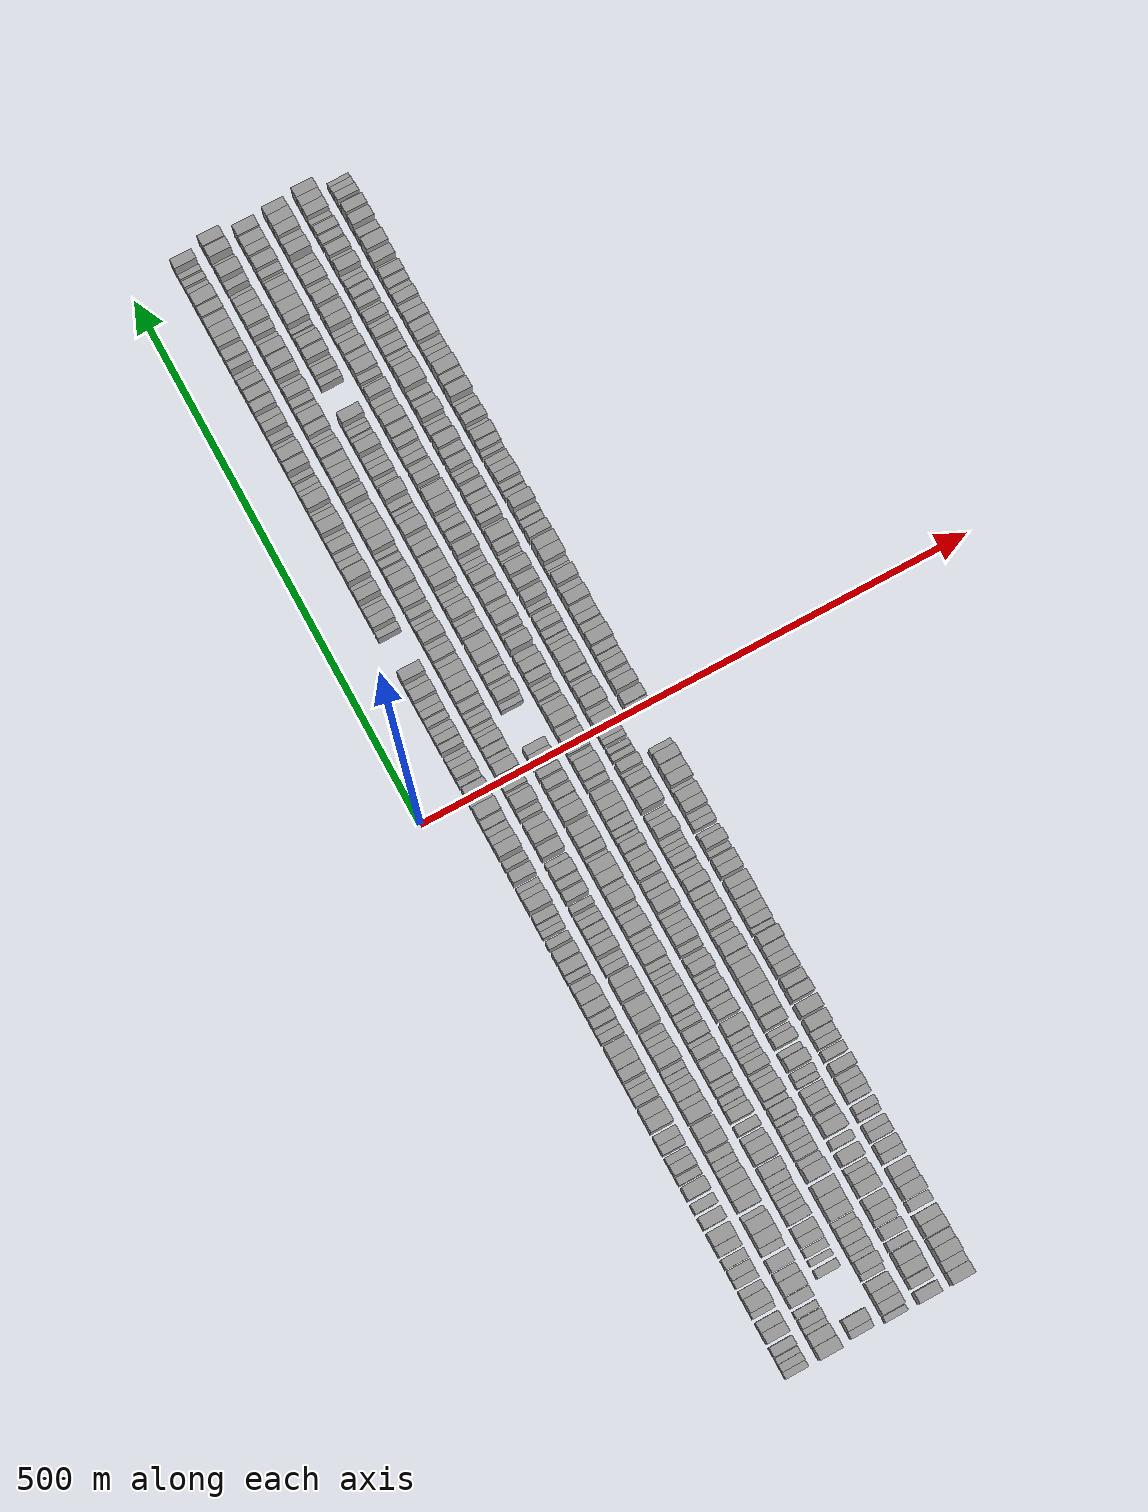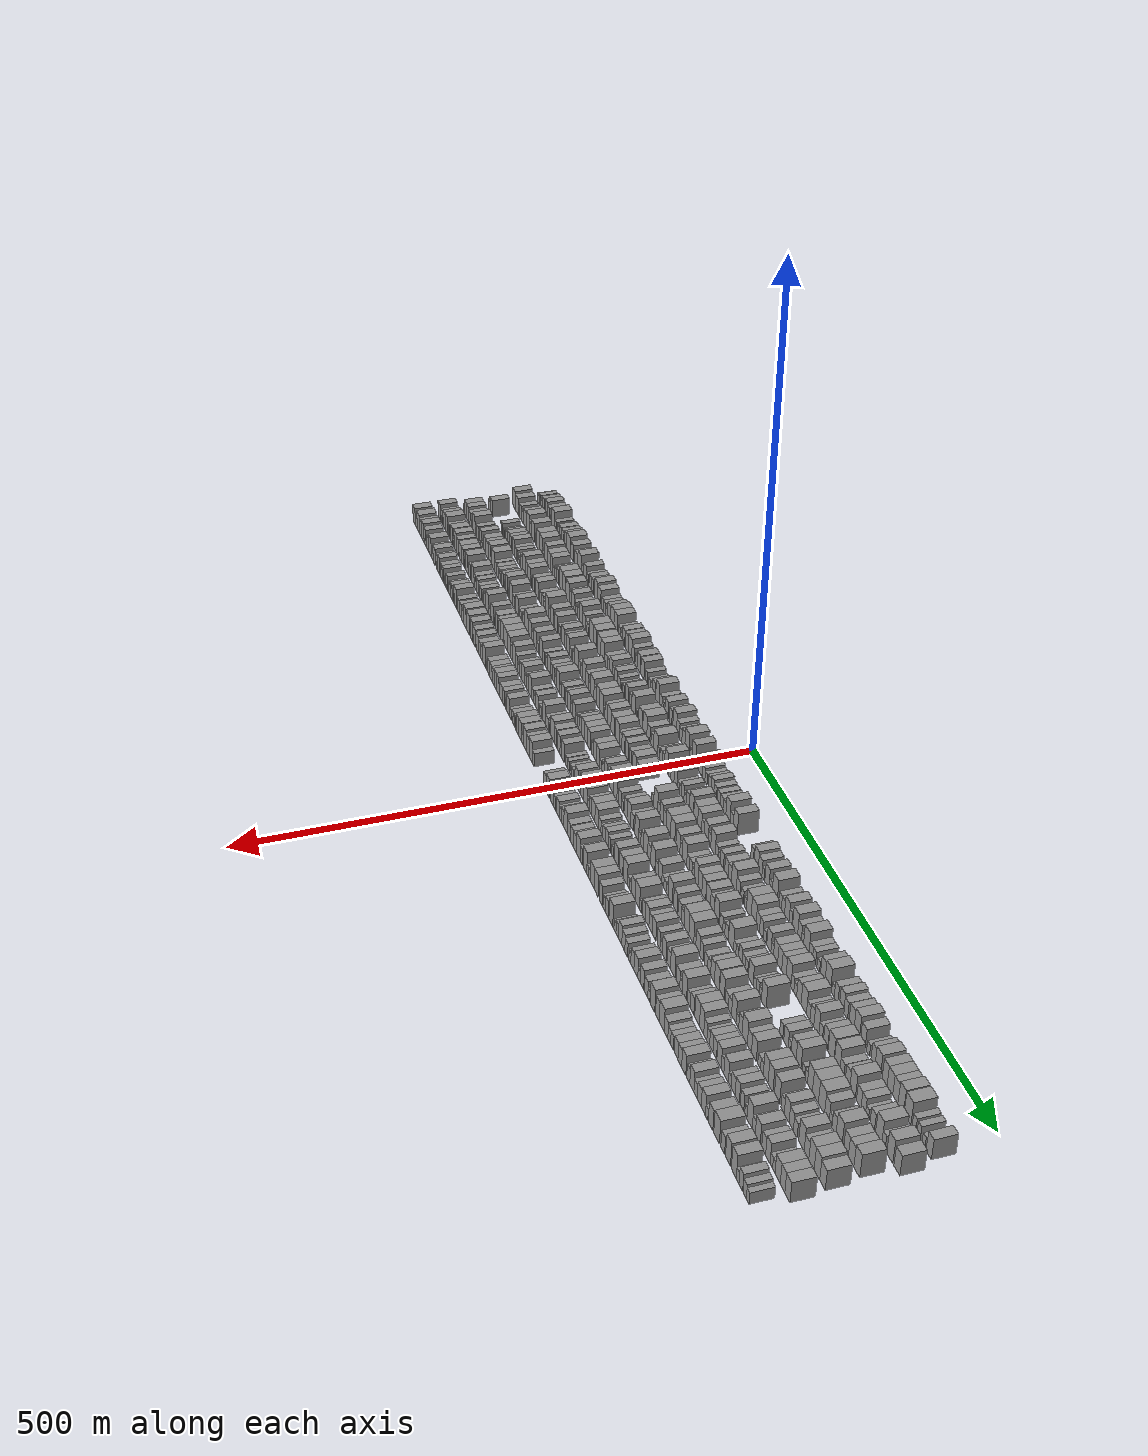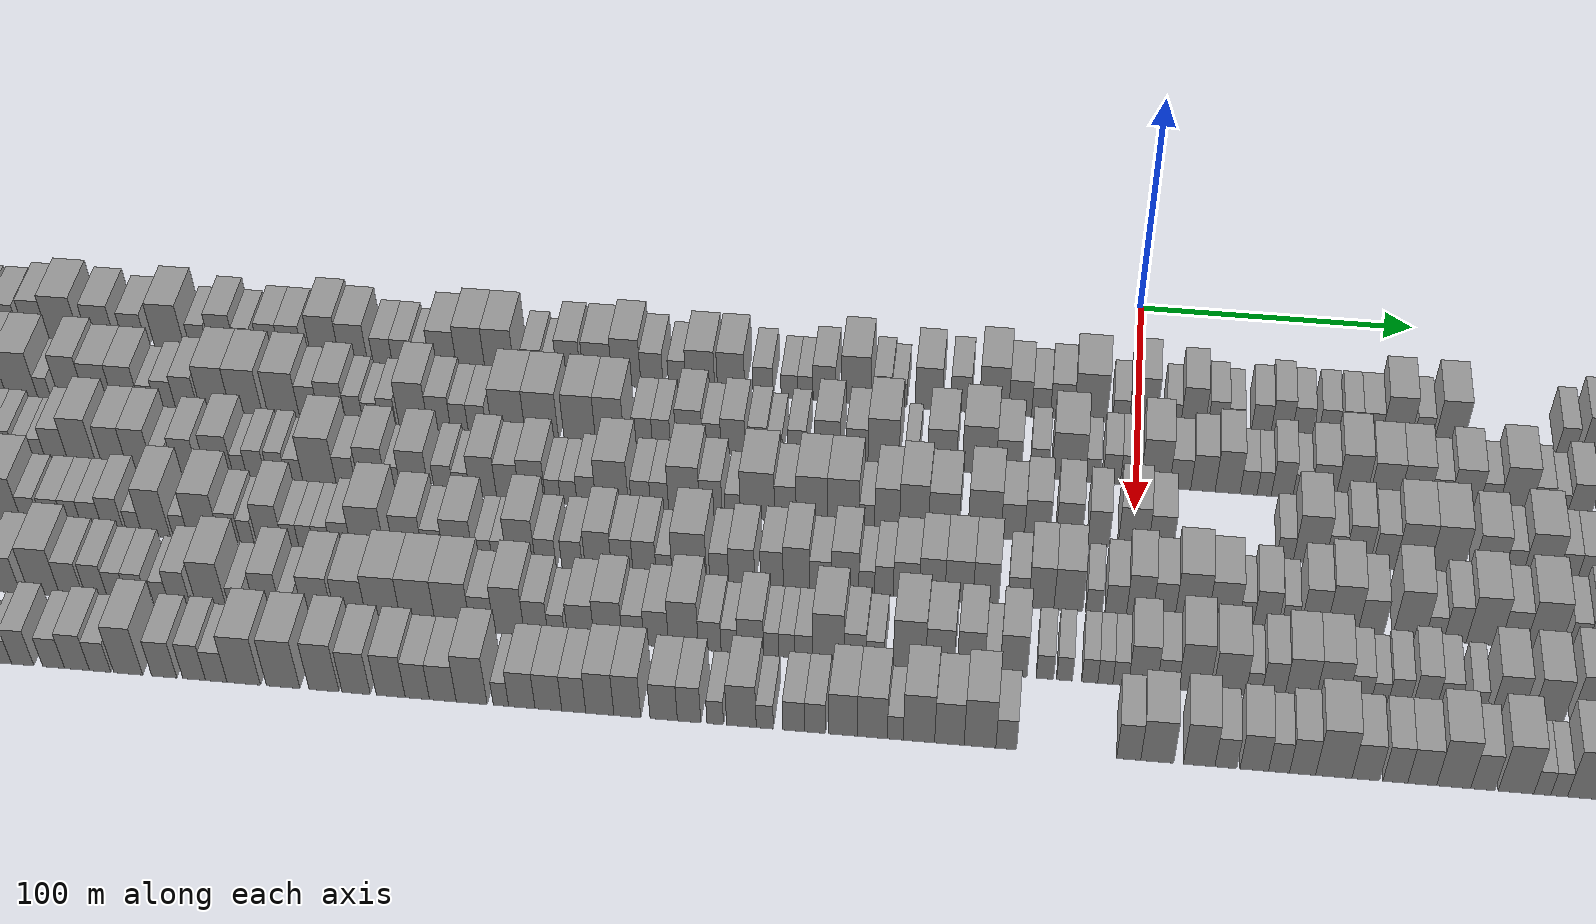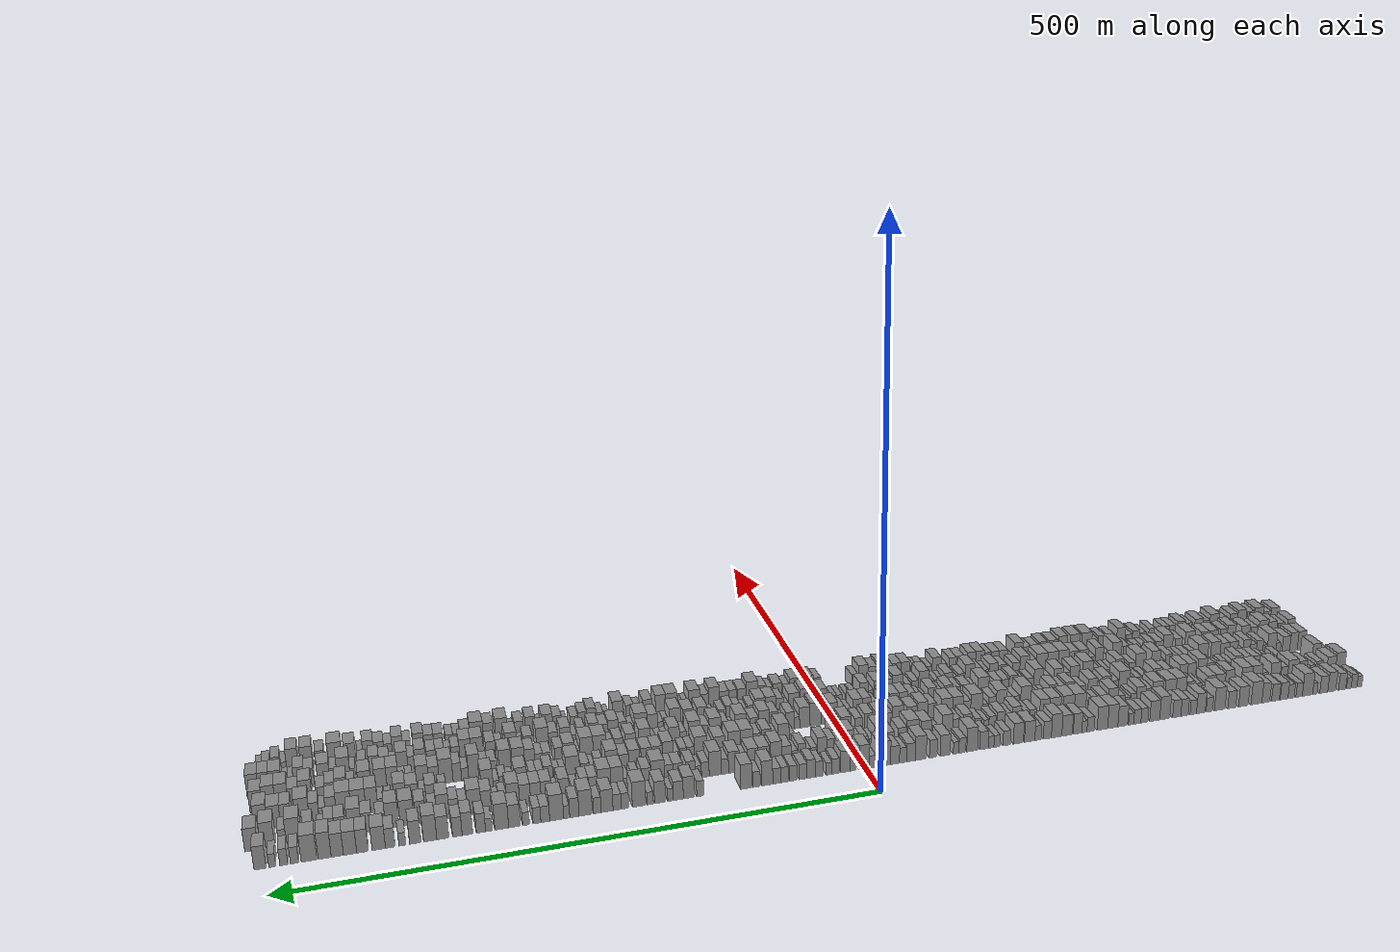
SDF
<sdf version="1.6">
 <world name="default">
  <scene>
   <sky><clouds><speed>12</speed></clouds></sky>
   <ambient>0.4 0.4 0.4 1</ambient>
   <background>0.7 0.7 0.7 1</background>
   <shadows>1</shadows>
  </scene>
  <gravity>0 0 -9.8066</gravity>
  <magnetic_field>6e-06 2.3e-05 -4.2e-05</magnetic_field>
  <physics default="0" name="default_physics" type="ode">
   <ode>
    <solver>
     <type>quick</type>
     <iters>10</iters>
     <sor>1.0</sor>
     <use_dynamic_moi_rescaling>0</use_dynamic_moi_rescaling>
    </solver>
    <constraints>
     <cfm>0</cfm>
     <erp>0.2</erp>
     <contact_max_correcting_vel>100</contact_max_correcting_vel>
     <contact_surface_layer>0.001</contact_surface_layer>
    </constraints>
   </ode>
   <max_step_size>0.004</max_step_size>
   <real_time_factor>1</real_time_factor>
   <real_time_update_rate>250</real_time_update_rate>
  </physics>
  <light name="sun" type="directional">
   <pose>0 0 10 0 0 0</pose>
   <diffuse>0.8 0.8 0.8 1</diffuse>
   <specular>0.2 0.2 0.2 1</specular>
   <attenuation>
    <range>1000</range>
    <constant>0.9</constant>
    <linear>0.01</linear>
    <quadratic>0.001</quadratic>
   </attenuation>
   <direction>-0.5 0.1 -0.9</direction>
  </light>
  <model name="building_1">
   <static>1</static>
   <pose>50.0000 -507.1129 0 0.000000 0.000000 0.000000</pose>
   <link name="link">
    <pose>0 0 6.00 0 0 0</pose>
    <collision name="collision"><geometry><box><size>20.0000 5.7743 12.0000</size></box></geometry></collision>
    <visual name="visual">
     <cast_shadows>0</cast_shadows>
     <geometry><box><size>20.0000 5.7743 12.0000</size></box></geometry>
     <material>
      <script>
       <uri>model://grey_wall/materials/scripts</uri>
       <uri>model://grey_wall/materials/textures</uri>
       <name>vrc/grey_wall</name>
      </script>
     </material>
    </visual>
   </link>
  </model>
  <model name="building_2">
   <static>1</static>
   <pose>50.0000 -500.9743 0 0.000000 0.000000 0.000000</pose>
   <link name="link">
    <pose>0 0 7.50 0 0 0</pose>
    <collision name="collision"><geometry><box><size>20.0000 6.5029 15.0000</size></box></geometry></collision>
    <visual name="visual">
     <cast_shadows>0</cast_shadows>
     <geometry><box><size>20.0000 6.5029 15.0000</size></box></geometry>
     <material>
      <script>
       <uri>model://grey_wall/materials/scripts</uri>
       <uri>model://grey_wall/materials/textures</uri>
       <name>vrc/grey_wall</name>
      </script>
     </material>
    </visual>
   </link>
  </model>
  <model name="building_3">
   <static>1</static>
   <pose>50.0000 -495.0810 0 0.000000 0.000000 0.000000</pose>
   <link name="link">
    <pose>0 0 6.00 0 0 0</pose>
    <collision name="collision"><geometry><box><size>20.0000 5.2837 12.0000</size></box></geometry></collision>
    <visual name="visual">
     <cast_shadows>0</cast_shadows>
     <geometry><box><size>20.0000 5.2837 12.0000</size></box></geometry>
     <material>
      <script>
       <uri>model://grey_wall/materials/scripts</uri>
       <uri>model://grey_wall/materials/textures</uri>
       <name>vrc/grey_wall</name>
      </script>
     </material>
    </visual>
   </link>
  </model>
  <model name="building_4">
   <static>1</static>
   <pose>50.0000 -487.4331 0 0.000000 0.000000 0.000000</pose>
   <link name="link">
    <pose>0 0 9.00 0 0 0</pose>
    <collision name="collision"><geometry><box><size>20.0000 8.0121 18.0000</size></box></geometry></collision>
    <visual name="visual">
     <cast_shadows>0</cast_shadows>
     <geometry><box><size>20.0000 8.0121 18.0000</size></box></geometry>
     <material>
      <script>
       <uri>model://grey_wall/materials/scripts</uri>
       <uri>model://grey_wall/materials/textures</uri>
       <name>vrc/grey_wall</name>
      </script>
     </material>
    </visual>
   </link>
  </model>
  <model name="building_5">
   <static>1</static>
   <pose>50.0000 -475.8678 0 0.000000 0.000000 0.000000</pose>
   <link name="link">
    <pose>0 0 10.50 0 0 0</pose>
    <collision name="collision"><geometry><box><size>20.0000 9.1184 21.0000</size></box></geometry></collision>
    <visual name="visual">
     <cast_shadows>0</cast_shadows>
     <geometry><box><size>20.0000 9.1184 21.0000</size></box></geometry>
     <material>
      <script>
       <uri>model://grey_wall/materials/scripts</uri>
       <uri>model://grey_wall/materials/textures</uri>
       <name>vrc/grey_wall</name>
      </script>
     </material>
    </visual>
   </link>
  </model>
  <model name="building_6">
   <static>1</static>
   <pose>50.0000 -466.8552 0 0.000000 0.000000 0.000000</pose>
   <link name="link">
    <pose>0 0 9.00 0 0 0</pose>
    <collision name="collision"><geometry><box><size>20.0000 8.9067 18.0000</size></box></geometry></collision>
    <visual name="visual">
     <cast_shadows>0</cast_shadows>
     <geometry><box><size>20.0000 8.9067 18.0000</size></box></geometry>
     <material>
      <script>
       <uri>model://grey_wall/materials/scripts</uri>
       <uri>model://grey_wall/materials/textures</uri>
       <name>vrc/grey_wall</name>
      </script>
     </material>
    </visual>
   </link>
  </model>
  <model name="building_7">
   <static>1</static>
   <pose>50.0000 -456.9294 0 0.000000 0.000000 0.000000</pose>
   <link name="link">
    <pose>0 0 6.00 0 0 0</pose>
    <collision name="collision"><geometry><box><size>20.0000 4.9449 12.0000</size></box></geometry></collision>
    <visual name="visual">
     <cast_shadows>0</cast_shadows>
     <geometry><box><size>20.0000 4.9449 12.0000</size></box></geometry>
     <material>
      <script>
       <uri>model://grey_wall/materials/scripts</uri>
       <uri>model://grey_wall/materials/textures</uri>
       <name>vrc/grey_wall</name>
      </script>
     </material>
    </visual>
   </link>
  </model>
  <model name="building_8">
   <static>1</static>
   <pose>50.0000 -448.7046 0 0.000000 0.000000 0.000000</pose>
   <link name="link">
    <pose>0 0 12.00 0 0 0</pose>
    <collision name="collision"><geometry><box><size>20.0000 11.5046 24.0000</size></box></geometry></collision>
    <visual name="visual">
     <cast_shadows>0</cast_shadows>
     <geometry><box><size>20.0000 11.5046 24.0000</size></box></geometry>
     <material>
      <script>
       <uri>model://grey_wall/materials/scripts</uri>
       <uri>model://grey_wall/materials/textures</uri>
       <name>vrc/grey_wall</name>
      </script>
     </material>
    </visual>
   </link>
  </model>
  <model name="building_9">
   <static>1</static>
   <pose>50.0000 -439.4274 0 0.000000 0.000000 0.000000</pose>
   <link name="link">
    <pose>0 0 7.50 0 0 0</pose>
    <collision name="collision"><geometry><box><size>20.0000 7.0497 15.0000</size></box></geometry></collision>
    <visual name="visual">
     <cast_shadows>0</cast_shadows>
     <geometry><box><size>20.0000 7.0497 15.0000</size></box></geometry>
     <material>
      <script>
       <uri>model://grey_wall/materials/scripts</uri>
       <uri>model://grey_wall/materials/textures</uri>
       <name>vrc/grey_wall</name>
      </script>
     </material>
    </visual>
   </link>
  </model>
  <model name="building_10">
   <static>1</static>
   <pose>50.0000 -430.5206 0 0.000000 0.000000 0.000000</pose>
   <link name="link">
    <pose>0 0 7.50 0 0 0</pose>
    <collision name="collision"><geometry><box><size>20.0000 6.7640 15.0000</size></box></geometry></collision>
    <visual name="visual">
     <cast_shadows>0</cast_shadows>
     <geometry><box><size>20.0000 6.7640 15.0000</size></box></geometry>
     <material>
      <script>
       <uri>model://grey_wall/materials/scripts</uri>
       <uri>model://grey_wall/materials/textures</uri>
       <name>vrc/grey_wall</name>
      </script>
     </material>
    </visual>
   </link>
  </model>
  <model name="building_11">
   <static>1</static>
   <pose>50.0000 -422.8623 0 0.000000 0.000000 0.000000</pose>
   <link name="link">
    <pose>0 0 9.00 0 0 0</pose>
    <collision name="collision"><geometry><box><size>20.0000 8.5525 18.0000</size></box></geometry></collision>
    <visual name="visual">
     <cast_shadows>0</cast_shadows>
     <geometry><box><size>20.0000 8.5525 18.0000</size></box></geometry>
     <material>
      <script>
       <uri>model://grey_wall/materials/scripts</uri>
       <uri>model://grey_wall/materials/textures</uri>
       <name>vrc/grey_wall</name>
      </script>
     </material>
    </visual>
   </link>
  </model>
  <model name="building_12">
   <static>1</static>
   <pose>50.0000 -413.3588 0 0.000000 0.000000 0.000000</pose>
   <link name="link">
    <pose>0 0 9.00 0 0 0</pose>
    <collision name="collision"><geometry><box><size>20.0000 8.4544 18.0000</size></box></geometry></collision>
    <visual name="visual">
     <cast_shadows>0</cast_shadows>
     <geometry><box><size>20.0000 8.4544 18.0000</size></box></geometry>
     <material>
      <script>
       <uri>model://grey_wall/materials/scripts</uri>
       <uri>model://grey_wall/materials/textures</uri>
       <name>vrc/grey_wall</name>
      </script>
     </material>
    </visual>
   </link>
  </model>
  <model name="building_13">
   <static>1</static>
   <pose>50.0000 -402.8247 0 0.000000 0.000000 0.000000</pose>
   <link name="link">
    <pose>0 0 10.50 0 0 0</pose>
    <collision name="collision"><geometry><box><size>20.0000 8.6138 21.0000</size></box></geometry></collision>
    <visual name="visual">
     <cast_shadows>0</cast_shadows>
     <geometry><box><size>20.0000 8.6138 21.0000</size></box></geometry>
     <material>
      <script>
       <uri>model://grey_wall/materials/scripts</uri>
       <uri>model://grey_wall/materials/textures</uri>
       <name>vrc/grey_wall</name>
      </script>
     </material>
    </visual>
   </link>
  </model>
  <model name="building_14">
   <static>1</static>
   <pose>50.0000 -392.5506 0 0.000000 0.000000 0.000000</pose>
   <link name="link">
    <pose>0 0 12.00 0 0 0</pose>
    <collision name="collision"><geometry><box><size>20.0000 11.9344 24.0000</size></box></geometry></collision>
    <visual name="visual">
     <cast_shadows>0</cast_shadows>
     <geometry><box><size>20.0000 11.9344 24.0000</size></box></geometry>
     <material>
      <script>
       <uri>model://grey_wall/materials/scripts</uri>
       <uri>model://grey_wall/materials/textures</uri>
       <name>vrc/grey_wall</name>
      </script>
     </material>
    </visual>
   </link>
  </model>
  <model name="building_15">
   <static>1</static>
   <pose>50.0000 -378.4107 0 0.000000 0.000000 0.000000</pose>
   <link name="link">
    <pose>0 0 10.50 0 0 0</pose>
    <collision name="collision"><geometry><box><size>20.0000 10.3454 21.0000</size></box></geometry></collision>
    <visual name="visual">
     <cast_shadows>0</cast_shadows>
     <geometry><box><size>20.0000 10.3454 21.0000</size></box></geometry>
     <material>
      <script>
       <uri>model://grey_wall/materials/scripts</uri>
       <uri>model://grey_wall/materials/textures</uri>
       <name>vrc/grey_wall</name>
      </script>
     </material>
    </visual>
   </link>
  </model>
  <model name="building_16">
   <static>1</static>
   <pose>50.0000 -365.9358 0 0.000000 0.000000 0.000000</pose>
   <link name="link">
    <pose>0 0 9.00 0 0 0</pose>
    <collision name="collision"><geometry><box><size>20.0000 8.6044 18.0000</size></box></geometry></collision>
    <visual name="visual">
     <cast_shadows>0</cast_shadows>
     <geometry><box><size>20.0000 8.6044 18.0000</size></box></geometry>
     <material>
      <script>
       <uri>model://grey_wall/materials/scripts</uri>
       <uri>model://grey_wall/materials/textures</uri>
       <name>vrc/grey_wall</name>
      </script>
     </material>
    </visual>
   </link>
  </model>
  <model name="building_17">
   <static>1</static>
   <pose>50.0000 -352.9570 0 0.000000 0.000000 0.000000</pose>
   <link name="link">
    <pose>0 0 12.00 0 0 0</pose>
    <collision name="collision"><geometry><box><size>20.0000 11.3531 24.0000</size></box></geometry></collision>
    <visual name="visual">
     <cast_shadows>0</cast_shadows>
     <geometry><box><size>20.0000 11.3531 24.0000</size></box></geometry>
     <material>
      <script>
       <uri>model://grey_wall/materials/scripts</uri>
       <uri>model://grey_wall/materials/textures</uri>
       <name>vrc/grey_wall</name>
      </script>
     </material>
    </visual>
   </link>
  </model>
  <model name="building_18">
   <static>1</static>
   <pose>50.0000 -341.8874 0 0.000000 0.000000 0.000000</pose>
   <link name="link">
    <pose>0 0 7.50 0 0 0</pose>
    <collision name="collision"><geometry><box><size>20.0000 6.7861 15.0000</size></box></geometry></collision>
    <visual name="visual">
     <cast_shadows>0</cast_shadows>
     <geometry><box><size>20.0000 6.7861 15.0000</size></box></geometry>
     <material>
      <script>
       <uri>model://grey_wall/materials/scripts</uri>
       <uri>model://grey_wall/materials/textures</uri>
       <name>vrc/grey_wall</name>
      </script>
     </material>
    </visual>
   </link>
  </model>
  <model name="building_19">
   <static>1</static>
   <pose>50.0000 -332.8574 0 0.000000 0.000000 0.000000</pose>
   <link name="link">
    <pose>0 0 10.50 0 0 0</pose>
    <collision name="collision"><geometry><box><size>20.0000 9.2741 21.0000</size></box></geometry></collision>
    <visual name="visual">
     <cast_shadows>0</cast_shadows>
     <geometry><box><size>20.0000 9.2741 21.0000</size></box></geometry>
     <material>
      <script>
       <uri>model://grey_wall/materials/scripts</uri>
       <uri>model://grey_wall/materials/textures</uri>
       <name>vrc/grey_wall</name>
      </script>
     </material>
    </visual>
   </link>
  </model>
  <model name="building_20">
   <static>1</static>
   <pose>50.0000 -324.8339 0 0.000000 0.000000 0.000000</pose>
   <link name="link">
    <pose>0 0 7.50 0 0 0</pose>
    <collision name="collision"><geometry><box><size>20.0000 6.7730 15.0000</size></box></geometry></collision>
    <visual name="visual">
     <cast_shadows>0</cast_shadows>
     <geometry><box><size>20.0000 6.7730 15.0000</size></box></geometry>
     <material>
      <script>
       <uri>model://grey_wall/materials/scripts</uri>
       <uri>model://grey_wall/materials/textures</uri>
       <name>vrc/grey_wall</name>
      </script>
     </material>
    </visual>
   </link>
  </model>
  <model name="building_21">
   <static>1</static>
   <pose>50.0000 -315.5316 0 0.000000 0.000000 0.000000</pose>
   <link name="link">
    <pose>0 0 9.00 0 0 0</pose>
    <collision name="collision"><geometry><box><size>20.0000 7.8315 18.0000</size></box></geometry></collision>
    <visual name="visual">
     <cast_shadows>0</cast_shadows>
     <geometry><box><size>20.0000 7.8315 18.0000</size></box></geometry>
     <material>
      <script>
       <uri>model://grey_wall/materials/scripts</uri>
       <uri>model://grey_wall/materials/textures</uri>
       <name>vrc/grey_wall</name>
      </script>
     </material>
    </visual>
   </link>
  </model>
  <model name="building_22">
   <static>1</static>
   <pose>50.0000 -307.3242 0 0.000000 0.000000 0.000000</pose>
   <link name="link">
    <pose>0 0 9.00 0 0 0</pose>
    <collision name="collision"><geometry><box><size>20.0000 8.5833 18.0000</size></box></geometry></collision>
    <visual name="visual">
     <cast_shadows>0</cast_shadows>
     <geometry><box><size>20.0000 8.5833 18.0000</size></box></geometry>
     <material>
      <script>
       <uri>model://grey_wall/materials/scripts</uri>
       <uri>model://grey_wall/materials/textures</uri>
       <name>vrc/grey_wall</name>
      </script>
     </material>
    </visual>
   </link>
  </model>
  <model name="building_23">
   <static>1</static>
   <pose>50.0000 -294.7615 0 0.000000 0.000000 0.000000</pose>
   <link name="link">
    <pose>0 0 12.00 0 0 0</pose>
    <collision name="collision"><geometry><box><size>20.0000 10.5422 24.0000</size></box></geometry></collision>
    <visual name="visual">
     <cast_shadows>0</cast_shadows>
     <geometry><box><size>20.0000 10.5422 24.0000</size></box></geometry>
     <material>
      <script>
       <uri>model://grey_wall/materials/scripts</uri>
       <uri>model://grey_wall/materials/textures</uri>
       <name>vrc/grey_wall</name>
      </script>
     </material>
    </visual>
   </link>
  </model>
  <model name="building_24">
   <static>1</static>
   <pose>50.0000 -284.2985 0 0.000000 0.000000 0.000000</pose>
   <link name="link">
    <pose>0 0 10.50 0 0 0</pose>
    <collision name="collision"><geometry><box><size>20.0000 10.3838 21.0000</size></box></geometry></collision>
    <visual name="visual">
     <cast_shadows>0</cast_shadows>
     <geometry><box><size>20.0000 10.3838 21.0000</size></box></geometry>
     <material>
      <script>
       <uri>model://grey_wall/materials/scripts</uri>
       <uri>model://grey_wall/materials/textures</uri>
       <name>vrc/grey_wall</name>
      </script>
     </material>
    </visual>
   </link>
  </model>
  <model name="building_25">
   <static>1</static>
   <pose>50.0000 -273.5292 0 0.000000 0.000000 0.000000</pose>
   <link name="link">
    <pose>0 0 7.50 0 0 0</pose>
    <collision name="collision"><geometry><box><size>20.0000 7.1548 15.0000</size></box></geometry></collision>
    <visual name="visual">
     <cast_shadows>0</cast_shadows>
     <geometry><box><size>20.0000 7.1548 15.0000</size></box></geometry>
     <material>
      <script>
       <uri>model://grey_wall/materials/scripts</uri>
       <uri>model://grey_wall/materials/textures</uri>
       <name>vrc/grey_wall</name>
      </script>
     </material>
    </visual>
   </link>
  </model>
  <model name="building_26">
   <static>1</static>
   <pose>50.0000 -266.2333 0 0.000000 0.000000 0.000000</pose>
   <link name="link">
    <pose>0 0 7.50 0 0 0</pose>
    <collision name="collision"><geometry><box><size>20.0000 7.4371 15.0000</size></box></geometry></collision>
    <visual name="visual">
     <cast_shadows>0</cast_shadows>
     <geometry><box><size>20.0000 7.4371 15.0000</size></box></geometry>
     <material>
      <script>
       <uri>model://grey_wall/materials/scripts</uri>
       <uri>model://grey_wall/materials/textures</uri>
       <name>vrc/grey_wall</name>
      </script>
     </material>
    </visual>
   </link>
  </model>
  <model name="building_27">
   <static>1</static>
   <pose>50.0000 -259.8109 0 0.000000 0.000000 0.000000</pose>
   <link name="link">
    <pose>0 0 6.00 0 0 0</pose>
    <collision name="collision"><geometry><box><size>20.0000 5.4075 12.0000</size></box></geometry></collision>
    <visual name="visual">
     <cast_shadows>0</cast_shadows>
     <geometry><box><size>20.0000 5.4075 12.0000</size></box></geometry>
     <material>
      <script>
       <uri>model://grey_wall/materials/scripts</uri>
       <uri>model://grey_wall/materials/textures</uri>
       <name>vrc/grey_wall</name>
      </script>
     </material>
    </visual>
   </link>
  </model>
  <model name="building_28">
   <static>1</static>
   <pose>50.0000 -251.1375 0 0.000000 0.000000 0.000000</pose>
   <link name="link">
    <pose>0 0 10.50 0 0 0</pose>
    <collision name="collision"><geometry><box><size>20.0000 9.9392 21.0000</size></box></geometry></collision>
    <visual name="visual">
     <cast_shadows>0</cast_shadows>
     <geometry><box><size>20.0000 9.9392 21.0000</size></box></geometry>
     <material>
      <script>
       <uri>model://grey_wall/materials/scripts</uri>
       <uri>model://grey_wall/materials/textures</uri>
       <name>vrc/grey_wall</name>
      </script>
     </material>
    </visual>
   </link>
  </model>
  <model name="building_29">
   <static>1</static>
   <pose>50.0000 -240.9504 0 0.000000 0.000000 0.000000</pose>
   <link name="link">
    <pose>0 0 12.00 0 0 0</pose>
    <collision name="collision"><geometry><box><size>20.0000 10.4351 24.0000</size></box></geometry></collision>
    <visual name="visual">
     <cast_shadows>0</cast_shadows>
     <geometry><box><size>20.0000 10.4351 24.0000</size></box></geometry>
     <material>
      <script>
       <uri>model://grey_wall/materials/scripts</uri>
       <uri>model://grey_wall/materials/textures</uri>
       <name>vrc/grey_wall</name>
      </script>
     </material>
    </visual>
   </link>
  </model>
  <model name="building_30">
   <static>1</static>
   <pose>50.0000 -230.3285 0 0.000000 0.000000 0.000000</pose>
   <link name="link">
    <pose>0 0 12.00 0 0 0</pose>
    <collision name="collision"><geometry><box><size>20.0000 10.8086 24.0000</size></box></geometry></collision>
    <visual name="visual">
     <cast_shadows>0</cast_shadows>
     <geometry><box><size>20.0000 10.8086 24.0000</size></box></geometry>
     <material>
      <script>
       <uri>model://grey_wall/materials/scripts</uri>
       <uri>model://grey_wall/materials/textures</uri>
       <name>vrc/grey_wall</name>
      </script>
     </material>
    </visual>
   </link>
  </model>
  <model name="building_31">
   <static>1</static>
   <pose>50.0000 -218.2917 0 0.000000 0.000000 0.000000</pose>
   <link name="link">
    <pose>0 0 7.50 0 0 0</pose>
    <collision name="collision"><geometry><box><size>20.0000 7.2650 15.0000</size></box></geometry></collision>
    <visual name="visual">
     <cast_shadows>0</cast_shadows>
     <geometry><box><size>20.0000 7.2650 15.0000</size></box></geometry>
     <material>
      <script>
       <uri>model://grey_wall/materials/scripts</uri>
       <uri>model://grey_wall/materials/textures</uri>
       <name>vrc/grey_wall</name>
      </script>
     </material>
    </visual>
   </link>
  </model>
  <model name="building_32">
   <static>1</static>
   <pose>50.0000 -212.0230 0 0.000000 0.000000 0.000000</pose>
   <link name="link">
    <pose>0 0 6.00 0 0 0</pose>
    <collision name="collision"><geometry><box><size>20.0000 5.2725 12.0000</size></box></geometry></collision>
    <visual name="visual">
     <cast_shadows>0</cast_shadows>
     <geometry><box><size>20.0000 5.2725 12.0000</size></box></geometry>
     <material>
      <script>
       <uri>model://grey_wall/materials/scripts</uri>
       <uri>model://grey_wall/materials/textures</uri>
       <name>vrc/grey_wall</name>
      </script>
     </material>
    </visual>
   </link>
  </model>
  <model name="building_33">
   <static>1</static>
   <pose>50.0000 -205.0334 0 0.000000 0.000000 0.000000</pose>
   <link name="link">
    <pose>0 0 10.50 0 0 0</pose>
    <collision name="collision"><geometry><box><size>20.0000 8.7068 21.0000</size></box></geometry></collision>
    <visual name="visual">
     <cast_shadows>0</cast_shadows>
     <geometry><box><size>20.0000 8.7068 21.0000</size></box></geometry>
     <material>
      <script>
       <uri>model://grey_wall/materials/scripts</uri>
       <uri>model://grey_wall/materials/textures</uri>
       <name>vrc/grey_wall</name>
      </script>
     </material>
    </visual>
   </link>
  </model>
  <model name="building_34">
   <static>1</static>
   <pose>50.0000 -194.4521 0 0.000000 0.000000 0.000000</pose>
   <link name="link">
    <pose>0 0 10.50 0 0 0</pose>
    <collision name="collision"><geometry><box><size>20.0000 10.4557 21.0000</size></box></geometry></collision>
    <visual name="visual">
     <cast_shadows>0</cast_shadows>
     <geometry><box><size>20.0000 10.4557 21.0000</size></box></geometry>
     <material>
      <script>
       <uri>model://grey_wall/materials/scripts</uri>
       <uri>model://grey_wall/materials/textures</uri>
       <name>vrc/grey_wall</name>
      </script>
     </material>
    </visual>
   </link>
  </model>
  <model name="building_35">
   <static>1</static>
   <pose>50.0000 -183.9868 0 0.000000 0.000000 0.000000</pose>
   <link name="link">
    <pose>0 0 12.00 0 0 0</pose>
    <collision name="collision"><geometry><box><size>20.0000 10.4749 24.0000</size></box></geometry></collision>
    <visual name="visual">
     <cast_shadows>0</cast_shadows>
     <geometry><box><size>20.0000 10.4749 24.0000</size></box></geometry>
     <material>
      <script>
       <uri>model://grey_wall/materials/scripts</uri>
       <uri>model://grey_wall/materials/textures</uri>
       <name>vrc/grey_wall</name>
      </script>
     </material>
    </visual>
   </link>
  </model>
  <model name="building_36">
   <static>1</static>
   <pose>50.0000 -174.6977 0 0.000000 0.000000 0.000000</pose>
   <link name="link">
    <pose>0 0 9.00 0 0 0</pose>
    <collision name="collision"><geometry><box><size>20.0000 8.1034 18.0000</size></box></geometry></collision>
    <visual name="visual">
     <cast_shadows>0</cast_shadows>
     <geometry><box><size>20.0000 8.1034 18.0000</size></box></geometry>
     <material>
      <script>
       <uri>model://grey_wall/materials/scripts</uri>
       <uri>model://grey_wall/materials/textures</uri>
       <name>vrc/grey_wall</name>
      </script>
     </material>
    </visual>
   </link>
  </model>
  <model name="building_37">
   <static>1</static>
   <pose>50.0000 -165.4682 0 0.000000 0.000000 0.000000</pose>
   <link name="link">
    <pose>0 0 7.50 0 0 0</pose>
    <collision name="collision"><geometry><box><size>20.0000 6.3556 15.0000</size></box></geometry></collision>
    <visual name="visual">
     <cast_shadows>0</cast_shadows>
     <geometry><box><size>20.0000 6.3556 15.0000</size></box></geometry>
     <material>
      <script>
       <uri>model://grey_wall/materials/scripts</uri>
       <uri>model://grey_wall/materials/textures</uri>
       <name>vrc/grey_wall</name>
      </script>
     </material>
    </visual>
   </link>
  </model>
  <model name="building_38">
   <static>1</static>
   <pose>50.0000 -157.0802 0 0.000000 0.000000 0.000000</pose>
   <link name="link">
    <pose>0 0 10.50 0 0 0</pose>
    <collision name="collision"><geometry><box><size>20.0000 10.4205 21.0000</size></box></geometry></collision>
    <visual name="visual">
     <cast_shadows>0</cast_shadows>
     <geometry><box><size>20.0000 10.4205 21.0000</size></box></geometry>
     <material>
      <script>
       <uri>model://grey_wall/materials/scripts</uri>
       <uri>model://grey_wall/materials/textures</uri>
       <name>vrc/grey_wall</name>
      </script>
     </material>
    </visual>
   </link>
  </model>
  <model name="building_39">
   <static>1</static>
   <pose>50.0000 -145.9283 0 0.000000 0.000000 0.000000</pose>
   <link name="link">
    <pose>0 0 10.50 0 0 0</pose>
    <collision name="collision"><geometry><box><size>20.0000 9.8833 21.0000</size></box></geometry></collision>
    <visual name="visual">
     <cast_shadows>0</cast_shadows>
     <geometry><box><size>20.0000 9.8833 21.0000</size></box></geometry>
     <material>
      <script>
       <uri>model://grey_wall/materials/scripts</uri>
       <uri>model://grey_wall/materials/textures</uri>
       <name>vrc/grey_wall</name>
      </script>
     </material>
    </visual>
   </link>
  </model>
  <model name="building_40">
   <static>1</static>
   <pose>50.0000 -134.4075 0 0.000000 0.000000 0.000000</pose>
   <link name="link">
    <pose>0 0 7.50 0 0 0</pose>
    <collision name="collision"><geometry><box><size>20.0000 7.1582 15.0000</size></box></geometry></collision>
    <visual name="visual">
     <cast_shadows>0</cast_shadows>
     <geometry><box><size>20.0000 7.1582 15.0000</size></box></geometry>
     <material>
      <script>
       <uri>model://grey_wall/materials/scripts</uri>
       <uri>model://grey_wall/materials/textures</uri>
       <name>vrc/grey_wall</name>
      </script>
     </material>
    </visual>
   </link>
  </model>
  <model name="building_41">
   <static>1</static>
   <pose>50.0000 -124.8479 0 0.000000 0.000000 0.000000</pose>
   <link name="link">
    <pose>0 0 6.00 0 0 0</pose>
    <collision name="collision"><geometry><box><size>20.0000 5.9610 12.0000</size></box></geometry></collision>
    <visual name="visual">
     <cast_shadows>0</cast_shadows>
     <geometry><box><size>20.0000 5.9610 12.0000</size></box></geometry>
     <material>
      <script>
       <uri>model://grey_wall/materials/scripts</uri>
       <uri>model://grey_wall/materials/textures</uri>
       <name>vrc/grey_wall</name>
      </script>
     </material>
    </visual>
   </link>
  </model>
  <model name="building_42">
   <static>1</static>
   <pose>50.0000 -119.0805 0 0.000000 0.000000 0.000000</pose>
   <link name="link">
    <pose>0 0 6.00 0 0 0</pose>
    <collision name="collision"><geometry><box><size>20.0000 5.5739 12.0000</size></box></geometry></collision>
    <visual name="visual">
     <cast_shadows>0</cast_shadows>
     <geometry><box><size>20.0000 5.5739 12.0000</size></box></geometry>
     <material>
      <script>
       <uri>model://grey_wall/materials/scripts</uri>
       <uri>model://grey_wall/materials/textures</uri>
       <name>vrc/grey_wall</name>
      </script>
     </material>
    </visual>
   </link>
  </model>
  <model name="building_43">
   <static>1</static>
   <pose>50.0000 -112.1648 0 0.000000 0.000000 0.000000</pose>
   <link name="link">
    <pose>0 0 9.00 0 0 0</pose>
    <collision name="collision"><geometry><box><size>20.0000 8.2574 18.0000</size></box></geometry></collision>
    <visual name="visual">
     <cast_shadows>0</cast_shadows>
     <geometry><box><size>20.0000 8.2574 18.0000</size></box></geometry>
     <material>
      <script>
       <uri>model://grey_wall/materials/scripts</uri>
       <uri>model://grey_wall/materials/textures</uri>
       <name>vrc/grey_wall</name>
      </script>
     </material>
    </visual>
   </link>
  </model>
  <model name="building_44">
   <static>1</static>
   <pose>50.0000 -100.7540 0 0.000000 0.000000 0.000000</pose>
   <link name="link">
    <pose>0 0 12.00 0 0 0</pose>
    <collision name="collision"><geometry><box><size>20.0000 10.5642 24.0000</size></box></geometry></collision>
    <visual name="visual">
     <cast_shadows>0</cast_shadows>
     <geometry><box><size>20.0000 10.5642 24.0000</size></box></geometry>
     <material>
      <script>
       <uri>model://grey_wall/materials/scripts</uri>
       <uri>model://grey_wall/materials/textures</uri>
       <name>vrc/grey_wall</name>
      </script>
     </material>
    </visual>
   </link>
  </model>
  <model name="building_45">
   <static>1</static>
   <pose>50.0000 -91.1865 0 0.000000 0.000000 0.000000</pose>
   <link name="link">
    <pose>0 0 7.50 0 0 0</pose>
    <collision name="collision"><geometry><box><size>20.0000 6.5709 15.0000</size></box></geometry></collision>
    <visual name="visual">
     <cast_shadows>0</cast_shadows>
     <geometry><box><size>20.0000 6.5709 15.0000</size></box></geometry>
     <material>
      <script>
       <uri>model://grey_wall/materials/scripts</uri>
       <uri>model://grey_wall/materials/textures</uri>
       <name>vrc/grey_wall</name>
      </script>
     </material>
    </visual>
   </link>
  </model>
  <model name="building_46">
   <static>1</static>
   <pose>50.0000 -85.2072 0 0.000000 0.000000 0.000000</pose>
   <link name="link">
    <pose>0 0 6.00 0 0 0</pose>
    <collision name="collision"><geometry><box><size>20.0000 5.3876 12.0000</size></box></geometry></collision>
    <visual name="visual">
     <cast_shadows>0</cast_shadows>
     <geometry><box><size>20.0000 5.3876 12.0000</size></box></geometry>
     <material>
      <script>
       <uri>model://grey_wall/materials/scripts</uri>
       <uri>model://grey_wall/materials/textures</uri>
       <name>vrc/grey_wall</name>
      </script>
     </material>
    </visual>
   </link>
  </model>
  <model name="building_47">
   <static>1</static>
   <pose>50.0000 -74.6740 0 0.000000 0.000000 0.000000</pose>
   <link name="link">
    <pose>0 0 10.50 0 0 0</pose>
    <collision name="collision"><geometry><box><size>20.0000 9.6788 21.0000</size></box></geometry></collision>
    <visual name="visual">
     <cast_shadows>0</cast_shadows>
     <geometry><box><size>20.0000 9.6788 21.0000</size></box></geometry>
     <material>
      <script>
       <uri>model://grey_wall/materials/scripts</uri>
       <uri>model://grey_wall/materials/textures</uri>
       <name>vrc/grey_wall</name>
      </script>
     </material>
    </visual>
   </link>
  </model>
  <model name="building_48">
   <static>1</static>
   <pose>50.0000 -63.1917 0 0.000000 0.000000 0.000000</pose>
   <link name="link">
    <pose>0 0 9.00 0 0 0</pose>
    <collision name="collision"><geometry><box><size>20.0000 7.2860 18.0000</size></box></geometry></collision>
    <visual name="visual">
     <cast_shadows>0</cast_shadows>
     <geometry><box><size>20.0000 7.2860 18.0000</size></box></geometry>
     <material>
      <script>
       <uri>model://grey_wall/materials/scripts</uri>
       <uri>model://grey_wall/materials/textures</uri>
       <name>vrc/grey_wall</name>
      </script>
     </material>
    </visual>
   </link>
  </model>
  <model name="building_49">
   <static>1</static>
   <pose>50.0000 -51.3033 0 0.000000 0.000000 0.000000</pose>
   <link name="link">
    <pose>0 0 12.00 0 0 0</pose>
    <collision name="collision"><geometry><box><size>20.0000 10.4907 24.0000</size></box></geometry></collision>
    <visual name="visual">
     <cast_shadows>0</cast_shadows>
     <geometry><box><size>20.0000 10.4907 24.0000</size></box></geometry>
     <material>
      <script>
       <uri>model://grey_wall/materials/scripts</uri>
       <uri>model://grey_wall/materials/textures</uri>
       <name>vrc/grey_wall</name>
      </script>
     </material>
    </visual>
   </link>
  </model>
  <model name="building_50">
   <static>1</static>
   <pose>50.0000 -41.9349 0 0.000000 0.000000 0.000000</pose>
   <link name="link">
    <pose>0 0 9.00 0 0 0</pose>
    <collision name="collision"><geometry><box><size>20.0000 8.2460 18.0000</size></box></geometry></collision>
    <visual name="visual">
     <cast_shadows>0</cast_shadows>
     <geometry><box><size>20.0000 8.2460 18.0000</size></box></geometry>
     <material>
      <script>
       <uri>model://grey_wall/materials/scripts</uri>
       <uri>model://grey_wall/materials/textures</uri>
       <name>vrc/grey_wall</name>
      </script>
     </material>
    </visual>
   </link>
  </model>
  <model name="building_51">
   <static>1</static>
   <pose>50.0000 -34.5024 0 0.000000 0.000000 0.000000</pose>
   <link name="link">
    <pose>0 0 7.50 0 0 0</pose>
    <collision name="collision"><geometry><box><size>20.0000 6.6191 15.0000</size></box></geometry></collision>
    <visual name="visual">
     <cast_shadows>0</cast_shadows>
     <geometry><box><size>20.0000 6.6191 15.0000</size></box></geometry>
     <material>
      <script>
       <uri>model://grey_wall/materials/scripts</uri>
       <uri>model://grey_wall/materials/textures</uri>
       <name>vrc/grey_wall</name>
      </script>
     </material>
    </visual>
   </link>
  </model>
  <model name="building_52">
   <static>1</static>
   <pose>50.0000 -27.0388 0 0.000000 0.000000 0.000000</pose>
   <link name="link">
    <pose>0 0 9.00 0 0 0</pose>
    <collision name="collision"><geometry><box><size>20.0000 8.3081 18.0000</size></box></geometry></collision>
    <visual name="visual">
     <cast_shadows>0</cast_shadows>
     <geometry><box><size>20.0000 8.3081 18.0000</size></box></geometry>
     <material>
      <script>
       <uri>model://grey_wall/materials/scripts</uri>
       <uri>model://grey_wall/materials/textures</uri>
       <name>vrc/grey_wall</name>
      </script>
     </material>
    </visual>
   </link>
  </model>
  <model name="building_53">
   <static>1</static>
   <pose>50.0000 -16.9919 0 0.000000 0.000000 0.000000</pose>
   <link name="link">
    <pose>0 0 12.00 0 0 0</pose>
    <collision name="collision"><geometry><box><size>20.0000 11.7858 24.0000</size></box></geometry></collision>
    <visual name="visual">
     <cast_shadows>0</cast_shadows>
     <geometry><box><size>20.0000 11.7858 24.0000</size></box></geometry>
     <material>
      <script>
       <uri>model://grey_wall/materials/scripts</uri>
       <uri>model://grey_wall/materials/textures</uri>
       <name>vrc/grey_wall</name>
      </script>
     </material>
    </visual>
   </link>
  </model>
  <model name="building_54">
   <static>1</static>
   <pose>50.0000 -6.1153 0 0.000000 0.000000 0.000000</pose>
   <link name="link">
    <pose>0 0 6.00 0 0 0</pose>
    <collision name="collision"><geometry><box><size>20.0000 5.9674 12.0000</size></box></geometry></collision>
    <visual name="visual">
     <cast_shadows>0</cast_shadows>
     <geometry><box><size>20.0000 5.9674 12.0000</size></box></geometry>
     <material>
      <script>
       <uri>model://grey_wall/materials/scripts</uri>
       <uri>model://grey_wall/materials/textures</uri>
       <name>vrc/grey_wall</name>
      </script>
     </material>
    </visual>
   </link>
  </model>
  <model name="building_55">
   <static>1</static>
   <pose>50.0000 1.6876 0 0.000000 0.000000 0.000000</pose>
   <link name="link">
    <pose>0 0 12.00 0 0 0</pose>
    <collision name="collision"><geometry><box><size>20.0000 9.6382 24.0000</size></box></geometry></collision>
    <visual name="visual">
     <cast_shadows>0</cast_shadows>
     <geometry><box><size>20.0000 9.6382 24.0000</size></box></geometry>
     <material>
      <script>
       <uri>model://grey_wall/materials/scripts</uri>
       <uri>model://grey_wall/materials/textures</uri>
       <name>vrc/grey_wall</name>
      </script>
     </material>
    </visual>
   </link>
  </model>
  <model name="building_56">
   <static>1</static>
   <pose>50.0000 12.2809 0 0.000000 0.000000 0.000000</pose>
   <link name="link">
    <pose>0 0 6.00 0 0 0</pose>
    <collision name="collision"><geometry><box><size>20.0000 5.5483 12.0000</size></box></geometry></collision>
    <visual name="visual">
     <cast_shadows>0</cast_shadows>
     <geometry><box><size>20.0000 5.5483 12.0000</size></box></geometry>
     <material>
      <script>
       <uri>model://grey_wall/materials/scripts</uri>
       <uri>model://grey_wall/materials/textures</uri>
       <name>vrc/grey_wall</name>
      </script>
     </material>
    </visual>
   </link>
  </model>
  <model name="building_57">
   <static>1</static>
   <pose>50.0000 19.3455 0 0.000000 0.000000 0.000000</pose>
   <link name="link">
    <pose>0 0 10.50 0 0 0</pose>
    <collision name="collision"><geometry><box><size>20.0000 8.5810 21.0000</size></box></geometry></collision>
    <visual name="visual">
     <cast_shadows>0</cast_shadows>
     <geometry><box><size>20.0000 8.5810 21.0000</size></box></geometry>
     <material>
      <script>
       <uri>model://grey_wall/materials/scripts</uri>
       <uri>model://grey_wall/materials/textures</uri>
       <name>vrc/grey_wall</name>
      </script>
     </material>
    </visual>
   </link>
  </model>
  <model name="building_58">
   <static>1</static>
   <pose>50.0000 28.0210 0 0.000000 0.000000 0.000000</pose>
   <link name="link">
    <pose>0 0 7.50 0 0 0</pose>
    <collision name="collision"><geometry><box><size>20.0000 6.7700 15.0000</size></box></geometry></collision>
    <visual name="visual">
     <cast_shadows>0</cast_shadows>
     <geometry><box><size>20.0000 6.7700 15.0000</size></box></geometry>
     <material>
      <script>
       <uri>model://grey_wall/materials/scripts</uri>
       <uri>model://grey_wall/materials/textures</uri>
       <name>vrc/grey_wall</name>
      </script>
     </material>
    </visual>
   </link>
  </model>
  <model name="building_59">
   <static>1</static>
   <pose>50.0000 34.2155 0 0.000000 0.000000 0.000000</pose>
   <link name="link">
    <pose>0 0 6.00 0 0 0</pose>
    <collision name="collision"><geometry><box><size>20.0000 5.6189 12.0000</size></box></geometry></collision>
    <visual name="visual">
     <cast_shadows>0</cast_shadows>
     <geometry><box><size>20.0000 5.6189 12.0000</size></box></geometry>
     <material>
      <script>
       <uri>model://grey_wall/materials/scripts</uri>
       <uri>model://grey_wall/materials/textures</uri>
       <name>vrc/grey_wall</name>
      </script>
     </material>
    </visual>
   </link>
  </model>
  <model name="building_60">
   <static>1</static>
   <pose>50.0000 43.4858 0 0.000000 0.000000 0.000000</pose>
   <link name="link">
    <pose>0 0 7.50 0 0 0</pose>
    <collision name="collision"><geometry><box><size>20.0000 6.9217 15.0000</size></box></geometry></collision>
    <visual name="visual">
     <cast_shadows>0</cast_shadows>
     <geometry><box><size>20.0000 6.9217 15.0000</size></box></geometry>
     <material>
      <script>
       <uri>model://grey_wall/materials/scripts</uri>
       <uri>model://grey_wall/materials/textures</uri>
       <name>vrc/grey_wall</name>
      </script>
     </material>
    </visual>
   </link>
  </model>
  <model name="building_61">
   <static>1</static>
   <pose>50.0000 50.6278 0 0.000000 0.000000 0.000000</pose>
   <link name="link">
    <pose>0 0 9.00 0 0 0</pose>
    <collision name="collision"><geometry><box><size>20.0000 7.3623 18.0000</size></box></geometry></collision>
    <visual name="visual">
     <cast_shadows>0</cast_shadows>
     <geometry><box><size>20.0000 7.3623 18.0000</size></box></geometry>
     <material>
      <script>
       <uri>model://grey_wall/materials/scripts</uri>
       <uri>model://grey_wall/materials/textures</uri>
       <name>vrc/grey_wall</name>
      </script>
     </material>
    </visual>
   </link>
  </model>
  <model name="building_62">
   <static>1</static>
   <pose>50.0000 57.8925 0 0.000000 0.000000 0.000000</pose>
   <link name="link">
    <pose>0 0 7.50 0 0 0</pose>
    <collision name="collision"><geometry><box><size>20.0000 7.1673 15.0000</size></box></geometry></collision>
    <visual name="visual">
     <cast_shadows>0</cast_shadows>
     <geometry><box><size>20.0000 7.1673 15.0000</size></box></geometry>
     <material>
      <script>
       <uri>model://grey_wall/materials/scripts</uri>
       <uri>model://grey_wall/materials/textures</uri>
       <name>vrc/grey_wall</name>
      </script>
     </material>
    </visual>
   </link>
  </model>
  <model name="building_63">
   <static>1</static>
   <pose>50.0000 66.8989 0 0.000000 0.000000 0.000000</pose>
   <link name="link">
    <pose>0 0 7.50 0 0 0</pose>
    <collision name="collision"><geometry><box><size>20.0000 6.8454 15.0000</size></box></geometry></collision>
    <visual name="visual">
     <cast_shadows>0</cast_shadows>
     <geometry><box><size>20.0000 6.8454 15.0000</size></box></geometry>
     <material>
      <script>
       <uri>model://grey_wall/materials/scripts</uri>
       <uri>model://grey_wall/materials/textures</uri>
       <name>vrc/grey_wall</name>
      </script>
     </material>
    </visual>
   </link>
  </model>
  <model name="building_64">
   <static>1</static>
   <pose>50.0000 74.6538 0 0.000000 0.000000 0.000000</pose>
   <link name="link">
    <pose>0 0 7.50 0 0 0</pose>
    <collision name="collision"><geometry><box><size>20.0000 6.6643 15.0000</size></box></geometry></collision>
    <visual name="visual">
     <cast_shadows>0</cast_shadows>
     <geometry><box><size>20.0000 6.6643 15.0000</size></box></geometry>
     <material>
      <script>
       <uri>model://grey_wall/materials/scripts</uri>
       <uri>model://grey_wall/materials/textures</uri>
       <name>vrc/grey_wall</name>
      </script>
     </material>
    </visual>
   </link>
  </model>
  <model name="building_65">
   <static>1</static>
   <pose>50.0000 81.7126 0 0.000000 0.000000 0.000000</pose>
   <link name="link">
    <pose>0 0 7.50 0 0 0</pose>
    <collision name="collision"><geometry><box><size>20.0000 7.4533 15.0000</size></box></geometry></collision>
    <visual name="visual">
     <cast_shadows>0</cast_shadows>
     <geometry><box><size>20.0000 7.4533 15.0000</size></box></geometry>
     <material>
      <script>
       <uri>model://grey_wall/materials/scripts</uri>
       <uri>model://grey_wall/materials/textures</uri>
       <name>vrc/grey_wall</name>
      </script>
     </material>
    </visual>
   </link>
  </model>
  <model name="building_66">
   <static>1</static>
   <pose>50.0000 90.5444 0 0.000000 0.000000 0.000000</pose>
   <link name="link">
    <pose>0 0 12.00 0 0 0</pose>
    <collision name="collision"><geometry><box><size>20.0000 10.2104 24.0000</size></box></geometry></collision>
    <visual name="visual">
     <cast_shadows>0</cast_shadows>
     <geometry><box><size>20.0000 10.2104 24.0000</size></box></geometry>
     <material>
      <script>
       <uri>model://grey_wall/materials/scripts</uri>
       <uri>model://grey_wall/materials/textures</uri>
       <name>vrc/grey_wall</name>
      </script>
     </material>
    </visual>
   </link>
  </model>
  <model name="building_67">
   <static>1</static>
   <pose>50.0000 99.7578 0 0.000000 0.000000 0.000000</pose>
   <link name="link">
    <pose>0 0 7.50 0 0 0</pose>
    <collision name="collision"><geometry><box><size>20.0000 6.2163 15.0000</size></box></geometry></collision>
    <visual name="visual">
     <cast_shadows>0</cast_shadows>
     <geometry><box><size>20.0000 6.2163 15.0000</size></box></geometry>
     <material>
      <script>
       <uri>model://grey_wall/materials/scripts</uri>
       <uri>model://grey_wall/materials/textures</uri>
       <name>vrc/grey_wall</name>
      </script>
     </material>
    </visual>
   </link>
  </model>
  <model name="building_68">
   <static>1</static>
   <pose>50.0000 108.9361 0 0.000000 0.000000 0.000000</pose>
   <link name="link">
    <pose>0 0 12.00 0 0 0</pose>
    <collision name="collision"><geometry><box><size>20.0000 10.1404 24.0000</size></box></geometry></collision>
    <visual name="visual">
     <cast_shadows>0</cast_shadows>
     <geometry><box><size>20.0000 10.1404 24.0000</size></box></geometry>
     <material>
      <script>
       <uri>model://grey_wall/materials/scripts</uri>
       <uri>model://grey_wall/materials/textures</uri>
       <name>vrc/grey_wall</name>
      </script>
     </material>
    </visual>
   </link>
  </model>
  <model name="building_69">
   <static>1</static>
   <pose>50.0000 149.5872 0 0.000000 0.000000 0.000000</pose>
   <link name="link">
    <pose>0 0 7.50 0 0 0</pose>
    <collision name="collision"><geometry><box><size>20.0000 6.3872 15.0000</size></box></geometry></collision>
    <visual name="visual">
     <cast_shadows>0</cast_shadows>
     <geometry><box><size>20.0000 6.3872 15.0000</size></box></geometry>
     <material>
      <script>
       <uri>model://grey_wall/materials/scripts</uri>
       <uri>model://grey_wall/materials/textures</uri>
       <name>vrc/grey_wall</name>
      </script>
     </material>
    </visual>
   </link>
  </model>
  <model name="building_70">
   <static>1</static>
   <pose>50.0000 159.5993 0 0.000000 0.000000 0.000000</pose>
   <link name="link">
    <pose>0 0 10.50 0 0 0</pose>
    <collision name="collision"><geometry><box><size>20.0000 9.6369 21.0000</size></box></geometry></collision>
    <visual name="visual">
     <cast_shadows>0</cast_shadows>
     <geometry><box><size>20.0000 9.6369 21.0000</size></box></geometry>
     <material>
      <script>
       <uri>model://grey_wall/materials/scripts</uri>
       <uri>model://grey_wall/materials/textures</uri>
       <name>vrc/grey_wall</name>
      </script>
     </material>
    </visual>
   </link>
  </model>
  <model name="building_71">
   <static>1</static>
   <pose>50.0000 168.7643 0 0.000000 0.000000 0.000000</pose>
   <link name="link">
    <pose>0 0 9.00 0 0 0</pose>
    <collision name="collision"><geometry><box><size>20.0000 8.6932 18.0000</size></box></geometry></collision>
    <visual name="visual">
     <cast_shadows>0</cast_shadows>
     <geometry><box><size>20.0000 8.6932 18.0000</size></box></geometry>
     <material>
      <script>
       <uri>model://grey_wall/materials/scripts</uri>
       <uri>model://grey_wall/materials/textures</uri>
       <name>vrc/grey_wall</name>
      </script>
     </material>
    </visual>
   </link>
  </model>
  <model name="building_72">
   <static>1</static>
   <pose>50.0000 175.5228 0 0.000000 0.000000 0.000000</pose>
   <link name="link">
    <pose>0 0 6.00 0 0 0</pose>
    <collision name="collision"><geometry><box><size>20.0000 4.8237 12.0000</size></box></geometry></collision>
    <visual name="visual">
     <cast_shadows>0</cast_shadows>
     <geometry><box><size>20.0000 4.8237 12.0000</size></box></geometry>
     <material>
      <script>
       <uri>model://grey_wall/materials/scripts</uri>
       <uri>model://grey_wall/materials/textures</uri>
       <name>vrc/grey_wall</name>
      </script>
     </material>
    </visual>
   </link>
  </model>
  <model name="building_73">
   <static>1</static>
   <pose>50.0000 184.6478 0 0.000000 0.000000 0.000000</pose>
   <link name="link">
    <pose>0 0 10.50 0 0 0</pose>
    <collision name="collision"><geometry><box><size>20.0000 9.4262 21.0000</size></box></geometry></collision>
    <visual name="visual">
     <cast_shadows>0</cast_shadows>
     <geometry><box><size>20.0000 9.4262 21.0000</size></box></geometry>
     <material>
      <script>
       <uri>model://grey_wall/materials/scripts</uri>
       <uri>model://grey_wall/materials/textures</uri>
       <name>vrc/grey_wall</name>
      </script>
     </material>
    </visual>
   </link>
  </model>
  <model name="building_74">
   <static>1</static>
   <pose>50.0000 193.0706 0 0.000000 0.000000 0.000000</pose>
   <link name="link">
    <pose>0 0 6.00 0 0 0</pose>
    <collision name="collision"><geometry><box><size>20.0000 5.4195 12.0000</size></box></geometry></collision>
    <visual name="visual">
     <cast_shadows>0</cast_shadows>
     <geometry><box><size>20.0000 5.4195 12.0000</size></box></geometry>
     <material>
      <script>
       <uri>model://grey_wall/materials/scripts</uri>
       <uri>model://grey_wall/materials/textures</uri>
       <name>vrc/grey_wall</name>
      </script>
     </material>
    </visual>
   </link>
  </model>
  <model name="building_75">
   <static>1</static>
   <pose>50.0000 202.5491 0 0.000000 0.000000 0.000000</pose>
   <link name="link">
    <pose>0 0 12.00 0 0 0</pose>
    <collision name="collision"><geometry><box><size>20.0000 11.5376 24.0000</size></box></geometry></collision>
    <visual name="visual">
     <cast_shadows>0</cast_shadows>
     <geometry><box><size>20.0000 11.5376 24.0000</size></box></geometry>
     <material>
      <script>
       <uri>model://grey_wall/materials/scripts</uri>
       <uri>model://grey_wall/materials/textures</uri>
       <name>vrc/grey_wall</name>
      </script>
     </material>
    </visual>
   </link>
  </model>
  <model name="building_76">
   <static>1</static>
   <pose>50.0000 214.5191 0 0.000000 0.000000 0.000000</pose>
   <link name="link">
    <pose>0 0 7.50 0 0 0</pose>
    <collision name="collision"><geometry><box><size>20.0000 6.4022 15.0000</size></box></geometry></collision>
    <visual name="visual">
     <cast_shadows>0</cast_shadows>
     <geometry><box><size>20.0000 6.4022 15.0000</size></box></geometry>
     <material>
      <script>
       <uri>model://grey_wall/materials/scripts</uri>
       <uri>model://grey_wall/materials/textures</uri>
       <name>vrc/grey_wall</name>
      </script>
     </material>
    </visual>
   </link>
  </model>
  <model name="building_77">
   <static>1</static>
   <pose>50.0000 221.2365 0 0.000000 0.000000 0.000000</pose>
   <link name="link">
    <pose>0 0 7.50 0 0 0</pose>
    <collision name="collision"><geometry><box><size>20.0000 7.0326 15.0000</size></box></geometry></collision>
    <visual name="visual">
     <cast_shadows>0</cast_shadows>
     <geometry><box><size>20.0000 7.0326 15.0000</size></box></geometry>
     <material>
      <script>
       <uri>model://grey_wall/materials/scripts</uri>
       <uri>model://grey_wall/materials/textures</uri>
       <name>vrc/grey_wall</name>
      </script>
     </material>
    </visual>
   </link>
  </model>
  <model name="building_78">
   <static>1</static>
   <pose>50.0000 229.7647 0 0.000000 0.000000 0.000000</pose>
   <link name="link">
    <pose>0 0 10.50 0 0 0</pose>
    <collision name="collision"><geometry><box><size>20.0000 10.0237 21.0000</size></box></geometry></collision>
    <visual name="visual">
     <cast_shadows>0</cast_shadows>
     <geometry><box><size>20.0000 10.0237 21.0000</size></box></geometry>
     <material>
      <script>
       <uri>model://grey_wall/materials/scripts</uri>
       <uri>model://grey_wall/materials/textures</uri>
       <name>vrc/grey_wall</name>
      </script>
     </material>
    </visual>
   </link>
  </model>
  <model name="building_79">
   <static>1</static>
   <pose>50.0000 237.9701 0 0.000000 0.000000 0.000000</pose>
   <link name="link">
    <pose>0 0 7.50 0 0 0</pose>
    <collision name="collision"><geometry><box><size>20.0000 6.3873 15.0000</size></box></geometry></collision>
    <visual name="visual">
     <cast_shadows>0</cast_shadows>
     <geometry><box><size>20.0000 6.3873 15.0000</size></box></geometry>
     <material>
      <script>
       <uri>model://grey_wall/materials/scripts</uri>
       <uri>model://grey_wall/materials/textures</uri>
       <name>vrc/grey_wall</name>
      </script>
     </material>
    </visual>
   </link>
  </model>
  <model name="building_80">
   <static>1</static>
   <pose>50.0000 247.7538 0 0.000000 0.000000 0.000000</pose>
   <link name="link">
    <pose>0 0 12.00 0 0 0</pose>
    <collision name="collision"><geometry><box><size>20.0000 11.1800 24.0000</size></box></geometry></collision>
    <visual name="visual">
     <cast_shadows>0</cast_shadows>
     <geometry><box><size>20.0000 11.1800 24.0000</size></box></geometry>
     <material>
      <script>
       <uri>model://grey_wall/materials/scripts</uri>
       <uri>model://grey_wall/materials/textures</uri>
       <name>vrc/grey_wall</name>
      </script>
     </material>
    </visual>
   </link>
  </model>
  <model name="building_81">
   <static>1</static>
   <pose>50.0000 257.2533 0 0.000000 0.000000 0.000000</pose>
   <link name="link">
    <pose>0 0 9.00 0 0 0</pose>
    <collision name="collision"><geometry><box><size>20.0000 7.8191 18.0000</size></box></geometry></collision>
    <visual name="visual">
     <cast_shadows>0</cast_shadows>
     <geometry><box><size>20.0000 7.8191 18.0000</size></box></geometry>
     <material>
      <script>
       <uri>model://grey_wall/materials/scripts</uri>
       <uri>model://grey_wall/materials/textures</uri>
       <name>vrc/grey_wall</name>
      </script>
     </material>
    </visual>
   </link>
  </model>
  <model name="building_82">
   <static>1</static>
   <pose>50.0000 263.6505 0 0.000000 0.000000 0.000000</pose>
   <link name="link">
    <pose>0 0 6.00 0 0 0</pose>
    <collision name="collision"><geometry><box><size>20.0000 4.9752 12.0000</size></box></geometry></collision>
    <visual name="visual">
     <cast_shadows>0</cast_shadows>
     <geometry><box><size>20.0000 4.9752 12.0000</size></box></geometry>
     <material>
      <script>
       <uri>model://grey_wall/materials/scripts</uri>
       <uri>model://grey_wall/materials/textures</uri>
       <name>vrc/grey_wall</name>
      </script>
     </material>
    </visual>
   </link>
  </model>
  <model name="building_83">
   <static>1</static>
   <pose>50.0000 271.9562 0 0.000000 0.000000 0.000000</pose>
   <link name="link">
    <pose>0 0 12.00 0 0 0</pose>
    <collision name="collision"><geometry><box><size>20.0000 11.6362 24.0000</size></box></geometry></collision>
    <visual name="visual">
     <cast_shadows>0</cast_shadows>
     <geometry><box><size>20.0000 11.6362 24.0000</size></box></geometry>
     <material>
      <script>
       <uri>model://grey_wall/materials/scripts</uri>
       <uri>model://grey_wall/materials/textures</uri>
       <name>vrc/grey_wall</name>
      </script>
     </material>
    </visual>
   </link>
  </model>
  <model name="building_84">
   <static>1</static>
   <pose>50.0000 281.4406 0 0.000000 0.000000 0.000000</pose>
   <link name="link">
    <pose>0 0 7.50 0 0 0</pose>
    <collision name="collision"><geometry><box><size>20.0000 7.3326 15.0000</size></box></geometry></collision>
    <visual name="visual">
     <cast_shadows>0</cast_shadows>
     <geometry><box><size>20.0000 7.3326 15.0000</size></box></geometry>
     <material>
      <script>
       <uri>model://grey_wall/materials/scripts</uri>
       <uri>model://grey_wall/materials/textures</uri>
       <name>vrc/grey_wall</name>
      </script>
     </material>
    </visual>
   </link>
  </model>
  <model name="building_85">
   <static>1</static>
   <pose>50.0000 288.3060 0 0.000000 0.000000 0.000000</pose>
   <link name="link">
    <pose>0 0 7.50 0 0 0</pose>
    <collision name="collision"><geometry><box><size>20.0000 6.3982 15.0000</size></box></geometry></collision>
    <visual name="visual">
     <cast_shadows>0</cast_shadows>
     <geometry><box><size>20.0000 6.3982 15.0000</size></box></geometry>
     <material>
      <script>
       <uri>model://grey_wall/materials/scripts</uri>
       <uri>model://grey_wall/materials/textures</uri>
       <name>vrc/grey_wall</name>
      </script>
     </material>
    </visual>
   </link>
  </model>
  <model name="building_86">
   <static>1</static>
   <pose>50.0000 297.3018 0 0.000000 0.000000 0.000000</pose>
   <link name="link">
    <pose>0 0 6.00 0 0 0</pose>
    <collision name="collision"><geometry><box><size>20.0000 5.5934 12.0000</size></box></geometry></collision>
    <visual name="visual">
     <cast_shadows>0</cast_shadows>
     <geometry><box><size>20.0000 5.5934 12.0000</size></box></geometry>
     <material>
      <script>
       <uri>model://grey_wall/materials/scripts</uri>
       <uri>model://grey_wall/materials/textures</uri>
       <name>vrc/grey_wall</name>
      </script>
     </material>
    </visual>
   </link>
  </model>
  <model name="building_87">
   <static>1</static>
   <pose>50.0000 306.8211 0 0.000000 0.000000 0.000000</pose>
   <link name="link">
    <pose>0 0 10.50 0 0 0</pose>
    <collision name="collision"><geometry><box><size>20.0000 9.4453 21.0000</size></box></geometry></collision>
    <visual name="visual">
     <cast_shadows>0</cast_shadows>
     <geometry><box><size>20.0000 9.4453 21.0000</size></box></geometry>
     <material>
      <script>
       <uri>model://grey_wall/materials/scripts</uri>
       <uri>model://grey_wall/materials/textures</uri>
       <name>vrc/grey_wall</name>
      </script>
     </material>
    </visual>
   </link>
  </model>
  <model name="building_88">
   <static>1</static>
   <pose>50.0000 317.1719 0 0.000000 0.000000 0.000000</pose>
   <link name="link">
    <pose>0 0 12.00 0 0 0</pose>
    <collision name="collision"><geometry><box><size>20.0000 11.2561 24.0000</size></box></geometry></collision>
    <visual name="visual">
     <cast_shadows>0</cast_shadows>
     <geometry><box><size>20.0000 11.2561 24.0000</size></box></geometry>
     <material>
      <script>
       <uri>model://grey_wall/materials/scripts</uri>
       <uri>model://grey_wall/materials/textures</uri>
       <name>vrc/grey_wall</name>
      </script>
     </material>
    </visual>
   </link>
  </model>
  <model name="building_89">
   <static>1</static>
   <pose>50.0000 327.5423 0 0.000000 0.000000 0.000000</pose>
   <link name="link">
    <pose>0 0 6.00 0 0 0</pose>
    <collision name="collision"><geometry><box><size>20.0000 5.4848 12.0000</size></box></geometry></collision>
    <visual name="visual">
     <cast_shadows>0</cast_shadows>
     <geometry><box><size>20.0000 5.4848 12.0000</size></box></geometry>
     <material>
      <script>
       <uri>model://grey_wall/materials/scripts</uri>
       <uri>model://grey_wall/materials/textures</uri>
       <name>vrc/grey_wall</name>
      </script>
     </material>
    </visual>
   </link>
  </model>
  <model name="building_90">
   <static>1</static>
   <pose>50.0000 333.9742 0 0.000000 0.000000 0.000000</pose>
   <link name="link">
    <pose>0 0 9.00 0 0 0</pose>
    <collision name="collision"><geometry><box><size>20.0000 7.3790 18.0000</size></box></geometry></collision>
    <visual name="visual">
     <cast_shadows>0</cast_shadows>
     <geometry><box><size>20.0000 7.3790 18.0000</size></box></geometry>
     <material>
      <script>
       <uri>model://grey_wall/materials/scripts</uri>
       <uri>model://grey_wall/materials/textures</uri>
       <name>vrc/grey_wall</name>
      </script>
     </material>
    </visual>
   </link>
  </model>
  <model name="building_91">
   <static>1</static>
   <pose>50.0000 344.9111 0 0.000000 0.000000 0.000000</pose>
   <link name="link">
    <pose>0 0 10.50 0 0 0</pose>
    <collision name="collision"><geometry><box><size>20.0000 8.4949 21.0000</size></box></geometry></collision>
    <visual name="visual">
     <cast_shadows>0</cast_shadows>
     <geometry><box><size>20.0000 8.4949 21.0000</size></box></geometry>
     <material>
      <script>
       <uri>model://grey_wall/materials/scripts</uri>
       <uri>model://grey_wall/materials/textures</uri>
       <name>vrc/grey_wall</name>
      </script>
     </material>
    </visual>
   </link>
  </model>
  <model name="building_92">
   <static>1</static>
   <pose>50.0000 352.9924 0 0.000000 0.000000 0.000000</pose>
   <link name="link">
    <pose>0 0 9.00 0 0 0</pose>
    <collision name="collision"><geometry><box><size>20.0000 7.6675 18.0000</size></box></geometry></collision>
    <visual name="visual">
     <cast_shadows>0</cast_shadows>
     <geometry><box><size>20.0000 7.6675 18.0000</size></box></geometry>
     <material>
      <script>
       <uri>model://grey_wall/materials/scripts</uri>
       <uri>model://grey_wall/materials/textures</uri>
       <name>vrc/grey_wall</name>
      </script>
     </material>
    </visual>
   </link>
  </model>
  <model name="building_93">
   <static>1</static>
   <pose>50.0000 364.6114 0 0.000000 0.000000 0.000000</pose>
   <link name="link">
    <pose>0 0 10.50 0 0 0</pose>
    <collision name="collision"><geometry><box><size>20.0000 9.5706 21.0000</size></box></geometry></collision>
    <visual name="visual">
     <cast_shadows>0</cast_shadows>
     <geometry><box><size>20.0000 9.5706 21.0000</size></box></geometry>
     <material>
      <script>
       <uri>model://grey_wall/materials/scripts</uri>
       <uri>model://grey_wall/materials/textures</uri>
       <name>vrc/grey_wall</name>
      </script>
     </material>
    </visual>
   </link>
  </model>
  <model name="building_94">
   <static>1</static>
   <pose>50.0000 374.6663 0 0.000000 0.000000 0.000000</pose>
   <link name="link">
    <pose>0 0 12.00 0 0 0</pose>
    <collision name="collision"><geometry><box><size>20.0000 10.5391 24.0000</size></box></geometry></collision>
    <visual name="visual">
     <cast_shadows>0</cast_shadows>
     <geometry><box><size>20.0000 10.5391 24.0000</size></box></geometry>
     <material>
      <script>
       <uri>model://grey_wall/materials/scripts</uri>
       <uri>model://grey_wall/materials/textures</uri>
       <name>vrc/grey_wall</name>
      </script>
     </material>
    </visual>
   </link>
  </model>
  <model name="building_95">
   <static>1</static>
   <pose>50.0000 386.4221 0 0.000000 0.000000 0.000000</pose>
   <link name="link">
    <pose>0 0 10.50 0 0 0</pose>
    <collision name="collision"><geometry><box><size>20.0000 8.9727 21.0000</size></box></geometry></collision>
    <visual name="visual">
     <cast_shadows>0</cast_shadows>
     <geometry><box><size>20.0000 8.9727 21.0000</size></box></geometry>
     <material>
      <script>
       <uri>model://grey_wall/materials/scripts</uri>
       <uri>model://grey_wall/materials/textures</uri>
       <name>vrc/grey_wall</name>
      </script>
     </material>
    </visual>
   </link>
  </model>
  <model name="building_96">
   <static>1</static>
   <pose>50.0000 396.6335 0 0.000000 0.000000 0.000000</pose>
   <link name="link">
    <pose>0 0 6.00 0 0 0</pose>
    <collision name="collision"><geometry><box><size>20.0000 5.4501 12.0000</size></box></geometry></collision>
    <visual name="visual">
     <cast_shadows>0</cast_shadows>
     <geometry><box><size>20.0000 5.4501 12.0000</size></box></geometry>
     <material>
      <script>
       <uri>model://grey_wall/materials/scripts</uri>
       <uri>model://grey_wall/materials/textures</uri>
       <name>vrc/grey_wall</name>
      </script>
     </material>
    </visual>
   </link>
  </model>
  <model name="building_97">
   <static>1</static>
   <pose>50.0000 406.1082 0 0.000000 0.000000 0.000000</pose>
   <link name="link">
    <pose>0 0 9.00 0 0 0</pose>
    <collision name="collision"><geometry><box><size>20.0000 7.4992 18.0000</size></box></geometry></collision>
    <visual name="visual">
     <cast_shadows>0</cast_shadows>
     <geometry><box><size>20.0000 7.4992 18.0000</size></box></geometry>
     <material>
      <script>
       <uri>model://grey_wall/materials/scripts</uri>
       <uri>model://grey_wall/materials/textures</uri>
       <name>vrc/grey_wall</name>
      </script>
     </material>
    </visual>
   </link>
  </model>
  <model name="building_98">
   <static>1</static>
   <pose>50.0000 415.0534 0 0.000000 0.000000 0.000000</pose>
   <link name="link">
    <pose>0 0 10.50 0 0 0</pose>
    <collision name="collision"><geometry><box><size>20.0000 10.3913 21.0000</size></box></geometry></collision>
    <visual name="visual">
     <cast_shadows>0</cast_shadows>
     <geometry><box><size>20.0000 10.3913 21.0000</size></box></geometry>
     <material>
      <script>
       <uri>model://grey_wall/materials/scripts</uri>
       <uri>model://grey_wall/materials/textures</uri>
       <name>vrc/grey_wall</name>
      </script>
     </material>
    </visual>
   </link>
  </model>
  <model name="building_99">
   <static>1</static>
   <pose>50.0000 427.6912 0 0.000000 0.000000 0.000000</pose>
   <link name="link">
    <pose>0 0 10.50 0 0 0</pose>
    <collision name="collision"><geometry><box><size>20.0000 8.8844 21.0000</size></box></geometry></collision>
    <visual name="visual">
     <cast_shadows>0</cast_shadows>
     <geometry><box><size>20.0000 8.8844 21.0000</size></box></geometry>
     <material>
      <script>
       <uri>model://grey_wall/materials/scripts</uri>
       <uri>model://grey_wall/materials/textures</uri>
       <name>vrc/grey_wall</name>
      </script>
     </material>
    </visual>
   </link>
  </model>
  <model name="building_100">
   <static>1</static>
   <pose>50.0000 437.2732 0 0.000000 0.000000 0.000000</pose>
   <link name="link">
    <pose>0 0 10.50 0 0 0</pose>
    <collision name="collision"><geometry><box><size>20.0000 10.2796 21.0000</size></box></geometry></collision>
    <visual name="visual">
     <cast_shadows>0</cast_shadows>
     <geometry><box><size>20.0000 10.2796 21.0000</size></box></geometry>
     <material>
      <script>
       <uri>model://grey_wall/materials/scripts</uri>
       <uri>model://grey_wall/materials/textures</uri>
       <name>vrc/grey_wall</name>
      </script>
     </material>
    </visual>
   </link>
  </model>
  <model name="building_101">
   <static>1</static>
   <pose>50.0000 447.0912 0 0.000000 0.000000 0.000000</pose>
   <link name="link">
    <pose>0 0 10.50 0 0 0</pose>
    <collision name="collision"><geometry><box><size>20.0000 9.3565 21.0000</size></box></geometry></collision>
    <visual name="visual">
     <cast_shadows>0</cast_shadows>
     <geometry><box><size>20.0000 9.3565 21.0000</size></box></geometry>
     <material>
      <script>
       <uri>model://grey_wall/materials/scripts</uri>
       <uri>model://grey_wall/materials/textures</uri>
       <name>vrc/grey_wall</name>
      </script>
     </material>
    </visual>
   </link>
  </model>
  <model name="building_102">
   <static>1</static>
   <pose>50.0000 456.7532 0 0.000000 0.000000 0.000000</pose>
   <link name="link">
    <pose>0 0 12.00 0 0 0</pose>
    <collision name="collision"><geometry><box><size>20.0000 9.9675 24.0000</size></box></geometry></collision>
    <visual name="visual">
     <cast_shadows>0</cast_shadows>
     <geometry><box><size>20.0000 9.9675 24.0000</size></box></geometry>
     <material>
      <script>
       <uri>model://grey_wall/materials/scripts</uri>
       <uri>model://grey_wall/materials/textures</uri>
       <name>vrc/grey_wall</name>
      </script>
     </material>
    </visual>
   </link>
  </model>
  <model name="building_103">
   <static>1</static>
   <pose>50.0000 468.7152 0 0.000000 0.000000 0.000000</pose>
   <link name="link">
    <pose>0 0 12.00 0 0 0</pose>
    <collision name="collision"><geometry><box><size>20.0000 11.9565 24.0000</size></box></geometry></collision>
    <visual name="visual">
     <cast_shadows>0</cast_shadows>
     <geometry><box><size>20.0000 11.9565 24.0000</size></box></geometry>
     <material>
      <script>
       <uri>model://grey_wall/materials/scripts</uri>
       <uri>model://grey_wall/materials/textures</uri>
       <name>vrc/grey_wall</name>
      </script>
     </material>
    </visual>
   </link>
  </model>
  <model name="building_104">
   <static>1</static>
   <pose>50.0000 479.7528 0 0.000000 0.000000 0.000000</pose>
   <link name="link">
    <pose>0 0 7.50 0 0 0</pose>
    <collision name="collision"><geometry><box><size>20.0000 6.1187 15.0000</size></box></geometry></collision>
    <visual name="visual">
     <cast_shadows>0</cast_shadows>
     <geometry><box><size>20.0000 6.1187 15.0000</size></box></geometry>
     <material>
      <script>
       <uri>model://grey_wall/materials/scripts</uri>
       <uri>model://grey_wall/materials/textures</uri>
       <name>vrc/grey_wall</name>
      </script>
     </material>
    </visual>
   </link>
  </model>
  <model name="building_105">
   <static>1</static>
   <pose>50.0000 487.8474 0 0.000000 0.000000 0.000000</pose>
   <link name="link">
    <pose>0 0 7.50 0 0 0</pose>
    <collision name="collision"><geometry><box><size>20.0000 6.0703 15.0000</size></box></geometry></collision>
    <visual name="visual">
     <cast_shadows>0</cast_shadows>
     <geometry><box><size>20.0000 6.0703 15.0000</size></box></geometry>
     <material>
      <script>
       <uri>model://grey_wall/materials/scripts</uri>
       <uri>model://grey_wall/materials/textures</uri>
       <name>vrc/grey_wall</name>
      </script>
     </material>
    </visual>
   </link>
  </model>
  <model name="building_106">
   <static>1</static>
   <pose>50.0000 496.4762 0 0.000000 0.000000 0.000000</pose>
   <link name="link">
    <pose>0 0 6.00 0 0 0</pose>
    <collision name="collision"><geometry><box><size>20.0000 5.1874 12.0000</size></box></geometry></collision>
    <visual name="visual">
     <cast_shadows>0</cast_shadows>
     <geometry><box><size>20.0000 5.1874 12.0000</size></box></geometry>
     <material>
      <script>
       <uri>model://grey_wall/materials/scripts</uri>
       <uri>model://grey_wall/materials/textures</uri>
       <name>vrc/grey_wall</name>
      </script>
     </material>
    </visual>
   </link>
  </model>
  <model name="building_107">
   <static>1</static>
   <pose>50.0000 505.6253 0 0.000000 0.000000 0.000000</pose>
   <link name="link">
    <pose>0 0 10.50 0 0 0</pose>
    <collision name="collision"><geometry><box><size>20.0000 9.1107 21.0000</size></box></geometry></collision>
    <visual name="visual">
     <cast_shadows>0</cast_shadows>
     <geometry><box><size>20.0000 9.1107 21.0000</size></box></geometry>
     <material>
      <script>
       <uri>model://grey_wall/materials/scripts</uri>
       <uri>model://grey_wall/materials/textures</uri>
       <name>vrc/grey_wall</name>
      </script>
     </material>
    </visual>
   </link>
  </model>
  <model name="building_108">
   <static>1</static>
   <pose>79.0000 -504.6940 0 0.000000 0.000000 0.000000</pose>
   <link name="link">
    <pose>0 0 12.00 0 0 0</pose>
    <collision name="collision"><geometry><box><size>20.0000 10.6121 24.0000</size></box></geometry></collision>
    <visual name="visual">
     <cast_shadows>0</cast_shadows>
     <geometry><box><size>20.0000 10.6121 24.0000</size></box></geometry>
     <material>
      <script>
       <uri>model://grey_wall/materials/scripts</uri>
       <uri>model://grey_wall/materials/textures</uri>
       <name>vrc/grey_wall</name>
      </script>
     </material>
    </visual>
   </link>
  </model>
  <model name="building_109">
   <static>1</static>
   <pose>79.0000 -494.2660 0 0.000000 0.000000 0.000000</pose>
   <link name="link">
    <pose>0 0 10.50 0 0 0</pose>
    <collision name="collision"><geometry><box><size>20.0000 10.2439 21.0000</size></box></geometry></collision>
    <visual name="visual">
     <cast_shadows>0</cast_shadows>
     <geometry><box><size>20.0000 10.2439 21.0000</size></box></geometry>
     <material>
      <script>
       <uri>model://grey_wall/materials/scripts</uri>
       <uri>model://grey_wall/materials/textures</uri>
       <name>vrc/grey_wall</name>
      </script>
     </material>
    </visual>
   </link>
  </model>
  <model name="building_110">
   <static>1</static>
   <pose>79.0000 -486.6266 0 0.000000 0.000000 0.000000</pose>
   <link name="link">
    <pose>0 0 6.00 0 0 0</pose>
    <collision name="collision"><geometry><box><size>20.0000 5.0349 12.0000</size></box></geometry></collision>
    <visual name="visual">
     <cast_shadows>0</cast_shadows>
     <geometry><box><size>20.0000 5.0349 12.0000</size></box></geometry>
     <material>
      <script>
       <uri>model://grey_wall/materials/scripts</uri>
       <uri>model://grey_wall/materials/textures</uri>
       <name>vrc/grey_wall</name>
      </script>
     </material>
    </visual>
   </link>
  </model>
  <model name="building_111">
   <static>1</static>
   <pose>79.0000 -480.2095 0 0.000000 0.000000 0.000000</pose>
   <link name="link">
    <pose>0 0 9.00 0 0 0</pose>
    <collision name="collision"><geometry><box><size>20.0000 7.7994 18.0000</size></box></geometry></collision>
    <visual name="visual">
     <cast_shadows>0</cast_shadows>
     <geometry><box><size>20.0000 7.7994 18.0000</size></box></geometry>
     <material>
      <script>
       <uri>model://grey_wall/materials/scripts</uri>
       <uri>model://grey_wall/materials/textures</uri>
       <name>vrc/grey_wall</name>
      </script>
     </material>
    </visual>
   </link>
  </model>
  <model name="building_112">
   <static>1</static>
   <pose>79.0000 -472.3011 0 0.000000 0.000000 0.000000</pose>
   <link name="link">
    <pose>0 0 7.50 0 0 0</pose>
    <collision name="collision"><geometry><box><size>20.0000 6.0173 15.0000</size></box></geometry></collision>
    <visual name="visual">
     <cast_shadows>0</cast_shadows>
     <geometry><box><size>20.0000 6.0173 15.0000</size></box></geometry>
     <material>
      <script>
       <uri>model://grey_wall/materials/scripts</uri>
       <uri>model://grey_wall/materials/textures</uri>
       <name>vrc/grey_wall</name>
      </script>
     </material>
    </visual>
   </link>
  </model>
  <model name="building_113">
   <static>1</static>
   <pose>79.0000 -461.7940 0 0.000000 0.000000 0.000000</pose>
   <link name="link">
    <pose>0 0 10.50 0 0 0</pose>
    <collision name="collision"><geometry><box><size>20.0000 8.9969 21.0000</size></box></geometry></collision>
    <visual name="visual">
     <cast_shadows>0</cast_shadows>
     <geometry><box><size>20.0000 8.9969 21.0000</size></box></geometry>
     <material>
      <script>
       <uri>model://grey_wall/materials/scripts</uri>
       <uri>model://grey_wall/materials/textures</uri>
       <name>vrc/grey_wall</name>
      </script>
     </material>
    </visual>
   </link>
  </model>
  <model name="building_114">
   <static>1</static>
   <pose>79.0000 -450.5983 0 0.000000 0.000000 0.000000</pose>
   <link name="link">
    <pose>0 0 12.00 0 0 0</pose>
    <collision name="collision"><geometry><box><size>20.0000 11.3943 24.0000</size></box></geometry></collision>
    <visual name="visual">
     <cast_shadows>0</cast_shadows>
     <geometry><box><size>20.0000 11.3943 24.0000</size></box></geometry>
     <material>
      <script>
       <uri>model://grey_wall/materials/scripts</uri>
       <uri>model://grey_wall/materials/textures</uri>
       <name>vrc/grey_wall</name>
      </script>
     </material>
    </visual>
   </link>
  </model>
  <model name="building_115">
   <static>1</static>
   <pose>79.0000 -441.0901 0 0.000000 0.000000 0.000000</pose>
   <link name="link">
    <pose>0 0 9.00 0 0 0</pose>
    <collision name="collision"><geometry><box><size>20.0000 7.6221 18.0000</size></box></geometry></collision>
    <visual name="visual">
     <cast_shadows>0</cast_shadows>
     <geometry><box><size>20.0000 7.6221 18.0000</size></box></geometry>
     <material>
      <script>
       <uri>model://grey_wall/materials/scripts</uri>
       <uri>model://grey_wall/materials/textures</uri>
       <name>vrc/grey_wall</name>
      </script>
     </material>
    </visual>
   </link>
  </model>
  <model name="building_116">
   <static>1</static>
   <pose>79.0000 -430.9364 0 0.000000 0.000000 0.000000</pose>
   <link name="link">
    <pose>0 0 12.00 0 0 0</pose>
    <collision name="collision"><geometry><box><size>20.0000 10.6853 24.0000</size></box></geometry></collision>
    <visual name="visual">
     <cast_shadows>0</cast_shadows>
     <geometry><box><size>20.0000 10.6853 24.0000</size></box></geometry>
     <material>
      <script>
       <uri>model://grey_wall/materials/scripts</uri>
       <uri>model://grey_wall/materials/textures</uri>
       <name>vrc/grey_wall</name>
      </script>
     </material>
    </visual>
   </link>
  </model>
  <model name="building_117">
   <static>1</static>
   <pose>79.0000 -419.2947 0 0.000000 0.000000 0.000000</pose>
   <link name="link">
    <pose>0 0 7.50 0 0 0</pose>
    <collision name="collision"><geometry><box><size>20.0000 6.5981 15.0000</size></box></geometry></collision>
    <visual name="visual">
     <cast_shadows>0</cast_shadows>
     <geometry><box><size>20.0000 6.5981 15.0000</size></box></geometry>
     <material>
      <script>
       <uri>model://grey_wall/materials/scripts</uri>
       <uri>model://grey_wall/materials/textures</uri>
       <name>vrc/grey_wall</name>
      </script>
     </material>
    </visual>
   </link>
  </model>
  <model name="building_118">
   <static>1</static>
   <pose>79.0000 -410.3616 0 0.000000 0.000000 0.000000</pose>
   <link name="link">
    <pose>0 0 12.00 0 0 0</pose>
    <collision name="collision"><geometry><box><size>20.0000 11.2680 24.0000</size></box></geometry></collision>
    <visual name="visual">
     <cast_shadows>0</cast_shadows>
     <geometry><box><size>20.0000 11.2680 24.0000</size></box></geometry>
     <material>
      <script>
       <uri>model://grey_wall/materials/scripts</uri>
       <uri>model://grey_wall/materials/textures</uri>
       <name>vrc/grey_wall</name>
      </script>
     </material>
    </visual>
   </link>
  </model>
  <model name="building_119">
   <static>1</static>
   <pose>79.0000 -398.9051 0 0.000000 0.000000 0.000000</pose>
   <link name="link">
    <pose>0 0 12.00 0 0 0</pose>
    <collision name="collision"><geometry><box><size>20.0000 11.6450 24.0000</size></box></geometry></collision>
    <visual name="visual">
     <cast_shadows>0</cast_shadows>
     <geometry><box><size>20.0000 11.6450 24.0000</size></box></geometry>
     <material>
      <script>
       <uri>model://grey_wall/materials/scripts</uri>
       <uri>model://grey_wall/materials/textures</uri>
       <name>vrc/grey_wall</name>
      </script>
     </material>
    </visual>
   </link>
  </model>
  <model name="building_120">
   <static>1</static>
   <pose>79.0000 -390.5866 0 0.000000 0.000000 0.000000</pose>
   <link name="link">
    <pose>0 0 6.00 0 0 0</pose>
    <collision name="collision"><geometry><box><size>20.0000 4.9921 12.0000</size></box></geometry></collision>
    <visual name="visual">
     <cast_shadows>0</cast_shadows>
     <geometry><box><size>20.0000 4.9921 12.0000</size></box></geometry>
     <material>
      <script>
       <uri>model://grey_wall/materials/scripts</uri>
       <uri>model://grey_wall/materials/textures</uri>
       <name>vrc/grey_wall</name>
      </script>
     </material>
    </visual>
   </link>
  </model>
  <model name="building_121">
   <static>1</static>
   <pose>79.0000 -380.2615 0 0.000000 0.000000 0.000000</pose>
   <link name="link">
    <pose>0 0 12.00 0 0 0</pose>
    <collision name="collision"><geometry><box><size>20.0000 9.6580 24.0000</size></box></geometry></collision>
    <visual name="visual">
     <cast_shadows>0</cast_shadows>
     <geometry><box><size>20.0000 9.6580 24.0000</size></box></geometry>
     <material>
      <script>
       <uri>model://grey_wall/materials/scripts</uri>
       <uri>model://grey_wall/materials/textures</uri>
       <name>vrc/grey_wall</name>
      </script>
     </material>
    </visual>
   </link>
  </model>
  <model name="building_122">
   <static>1</static>
   <pose>79.0000 -370.3288 0 0.000000 0.000000 0.000000</pose>
   <link name="link">
    <pose>0 0 10.50 0 0 0</pose>
    <collision name="collision"><geometry><box><size>20.0000 10.2073 21.0000</size></box></geometry></collision>
    <visual name="visual">
     <cast_shadows>0</cast_shadows>
     <geometry><box><size>20.0000 10.2073 21.0000</size></box></geometry>
     <material>
      <script>
       <uri>model://grey_wall/materials/scripts</uri>
       <uri>model://grey_wall/materials/textures</uri>
       <name>vrc/grey_wall</name>
      </script>
     </material>
    </visual>
   </link>
  </model>
  <model name="building_123">
   <static>1</static>
   <pose>79.0000 -360.3785 0 0.000000 0.000000 0.000000</pose>
   <link name="link">
    <pose>0 0 10.50 0 0 0</pose>
    <collision name="collision"><geometry><box><size>20.0000 9.6934 21.0000</size></box></geometry></collision>
    <visual name="visual">
     <cast_shadows>0</cast_shadows>
     <geometry><box><size>20.0000 9.6934 21.0000</size></box></geometry>
     <material>
      <script>
       <uri>model://grey_wall/materials/scripts</uri>
       <uri>model://grey_wall/materials/textures</uri>
       <name>vrc/grey_wall</name>
      </script>
     </material>
    </visual>
   </link>
  </model>
  <model name="building_124">
   <static>1</static>
   <pose>79.0000 -352.6280 0 0.000000 0.000000 0.000000</pose>
   <link name="link">
    <pose>0 0 6.00 0 0 0</pose>
    <collision name="collision"><geometry><box><size>20.0000 5.8076 12.0000</size></box></geometry></collision>
    <visual name="visual">
     <cast_shadows>0</cast_shadows>
     <geometry><box><size>20.0000 5.8076 12.0000</size></box></geometry>
     <material>
      <script>
       <uri>model://grey_wall/materials/scripts</uri>
       <uri>model://grey_wall/materials/textures</uri>
       <name>vrc/grey_wall</name>
      </script>
     </material>
    </visual>
   </link>
  </model>
  <model name="building_125">
   <static>1</static>
   <pose>79.0000 -346.0457 0 0.000000 0.000000 0.000000</pose>
   <link name="link">
    <pose>0 0 7.50 0 0 0</pose>
    <collision name="collision"><geometry><box><size>20.0000 7.3569 15.0000</size></box></geometry></collision>
    <visual name="visual">
     <cast_shadows>0</cast_shadows>
     <geometry><box><size>20.0000 7.3569 15.0000</size></box></geometry>
     <material>
      <script>
       <uri>model://grey_wall/materials/scripts</uri>
       <uri>model://grey_wall/materials/textures</uri>
       <name>vrc/grey_wall</name>
      </script>
     </material>
    </visual>
   </link>
  </model>
  <model name="building_126">
   <static>1</static>
   <pose>79.0000 -338.2798 0 0.000000 0.000000 0.000000</pose>
   <link name="link">
    <pose>0 0 9.00 0 0 0</pose>
    <collision name="collision"><geometry><box><size>20.0000 8.1748 18.0000</size></box></geometry></collision>
    <visual name="visual">
     <cast_shadows>0</cast_shadows>
     <geometry><box><size>20.0000 8.1748 18.0000</size></box></geometry>
     <material>
      <script>
       <uri>model://grey_wall/materials/scripts</uri>
       <uri>model://grey_wall/materials/textures</uri>
       <name>vrc/grey_wall</name>
      </script>
     </material>
    </visual>
   </link>
  </model>
  <model name="building_127">
   <static>1</static>
   <pose>79.0000 -327.7085 0 0.000000 0.000000 0.000000</pose>
   <link name="link">
    <pose>0 0 12.00 0 0 0</pose>
    <collision name="collision"><geometry><box><size>20.0000 10.9678 24.0000</size></box></geometry></collision>
    <visual name="visual">
     <cast_shadows>0</cast_shadows>
     <geometry><box><size>20.0000 10.9678 24.0000</size></box></geometry>
     <material>
      <script>
       <uri>model://grey_wall/materials/scripts</uri>
       <uri>model://grey_wall/materials/textures</uri>
       <name>vrc/grey_wall</name>
      </script>
     </material>
    </visual>
   </link>
  </model>
  <model name="building_128">
   <static>1</static>
   <pose>79.0000 -316.3937 0 0.000000 0.000000 0.000000</pose>
   <link name="link">
    <pose>0 0 12.00 0 0 0</pose>
    <collision name="collision"><geometry><box><size>20.0000 11.6619 24.0000</size></box></geometry></collision>
    <visual name="visual">
     <cast_shadows>0</cast_shadows>
     <geometry><box><size>20.0000 11.6619 24.0000</size></box></geometry>
     <material>
      <script>
       <uri>model://grey_wall/materials/scripts</uri>
       <uri>model://grey_wall/materials/textures</uri>
       <name>vrc/grey_wall</name>
      </script>
     </material>
    </visual>
   </link>
  </model>
  <model name="building_129">
   <static>1</static>
   <pose>79.0000 -302.7986 0 0.000000 0.000000 0.000000</pose>
   <link name="link">
    <pose>0 0 12.00 0 0 0</pose>
    <collision name="collision"><geometry><box><size>20.0000 11.5283 24.0000</size></box></geometry></collision>
    <visual name="visual">
     <cast_shadows>0</cast_shadows>
     <geometry><box><size>20.0000 11.5283 24.0000</size></box></geometry>
     <material>
      <script>
       <uri>model://grey_wall/materials/scripts</uri>
       <uri>model://grey_wall/materials/textures</uri>
       <name>vrc/grey_wall</name>
      </script>
     </material>
    </visual>
   </link>
  </model>
  <model name="building_130">
   <static>1</static>
   <pose>79.0000 -293.4210 0 0.000000 0.000000 0.000000</pose>
   <link name="link">
    <pose>0 0 9.00 0 0 0</pose>
    <collision name="collision"><geometry><box><size>20.0000 7.2270 18.0000</size></box></geometry></collision>
    <visual name="visual">
     <cast_shadows>0</cast_shadows>
     <geometry><box><size>20.0000 7.2270 18.0000</size></box></geometry>
     <material>
      <script>
       <uri>model://grey_wall/materials/scripts</uri>
       <uri>model://grey_wall/materials/textures</uri>
       <name>vrc/grey_wall</name>
      </script>
     </material>
    </visual>
   </link>
  </model>
  <model name="building_131">
   <static>1</static>
   <pose>79.0000 -285.0231 0 0.000000 0.000000 0.000000</pose>
   <link name="link">
    <pose>0 0 10.50 0 0 0</pose>
    <collision name="collision"><geometry><box><size>20.0000 9.5687 21.0000</size></box></geometry></collision>
    <visual name="visual">
     <cast_shadows>0</cast_shadows>
     <geometry><box><size>20.0000 9.5687 21.0000</size></box></geometry>
     <material>
      <script>
       <uri>model://grey_wall/materials/scripts</uri>
       <uri>model://grey_wall/materials/textures</uri>
       <name>vrc/grey_wall</name>
      </script>
     </material>
    </visual>
   </link>
  </model>
  <model name="building_132">
   <static>1</static>
   <pose>79.0000 -277.0917 0 0.000000 0.000000 0.000000</pose>
   <link name="link">
    <pose>0 0 7.50 0 0 0</pose>
    <collision name="collision"><geometry><box><size>20.0000 6.2942 15.0000</size></box></geometry></collision>
    <visual name="visual">
     <cast_shadows>0</cast_shadows>
     <geometry><box><size>20.0000 6.2942 15.0000</size></box></geometry>
     <material>
      <script>
       <uri>model://grey_wall/materials/scripts</uri>
       <uri>model://grey_wall/materials/textures</uri>
       <name>vrc/grey_wall</name>
      </script>
     </material>
    </visual>
   </link>
  </model>
  <model name="building_133">
   <static>1</static>
   <pose>79.0000 -271.0221 0 0.000000 0.000000 0.000000</pose>
   <link name="link">
    <pose>0 0 6.00 0 0 0</pose>
    <collision name="collision"><geometry><box><size>20.0000 5.8450 12.0000</size></box></geometry></collision>
    <visual name="visual">
     <cast_shadows>0</cast_shadows>
     <geometry><box><size>20.0000 5.8450 12.0000</size></box></geometry>
     <material>
      <script>
       <uri>model://grey_wall/materials/scripts</uri>
       <uri>model://grey_wall/materials/textures</uri>
       <name>vrc/grey_wall</name>
      </script>
     </material>
    </visual>
   </link>
  </model>
  <model name="building_134">
   <static>1</static>
   <pose>79.0000 -265.0410 0 0.000000 0.000000 0.000000</pose>
   <link name="link">
    <pose>0 0 7.50 0 0 0</pose>
    <collision name="collision"><geometry><box><size>20.0000 6.1172 15.0000</size></box></geometry></collision>
    <visual name="visual">
     <cast_shadows>0</cast_shadows>
     <geometry><box><size>20.0000 6.1172 15.0000</size></box></geometry>
     <material>
      <script>
       <uri>model://grey_wall/materials/scripts</uri>
       <uri>model://grey_wall/materials/textures</uri>
       <name>vrc/grey_wall</name>
      </script>
     </material>
    </visual>
   </link>
  </model>
  <model name="building_135">
   <static>1</static>
   <pose>79.0000 -255.7287 0 0.000000 0.000000 0.000000</pose>
   <link name="link">
    <pose>0 0 12.00 0 0 0</pose>
    <collision name="collision"><geometry><box><size>20.0000 10.5073 24.0000</size></box></geometry></collision>
    <visual name="visual">
     <cast_shadows>0</cast_shadows>
     <geometry><box><size>20.0000 10.5073 24.0000</size></box></geometry>
     <material>
      <script>
       <uri>model://grey_wall/materials/scripts</uri>
       <uri>model://grey_wall/materials/textures</uri>
       <name>vrc/grey_wall</name>
      </script>
     </material>
    </visual>
   </link>
  </model>
  <model name="building_136">
   <static>1</static>
   <pose>79.0000 -246.3760 0 0.000000 0.000000 0.000000</pose>
   <link name="link">
    <pose>0 0 9.00 0 0 0</pose>
    <collision name="collision"><geometry><box><size>20.0000 8.1982 18.0000</size></box></geometry></collision>
    <visual name="visual">
     <cast_shadows>0</cast_shadows>
     <geometry><box><size>20.0000 8.1982 18.0000</size></box></geometry>
     <material>
      <script>
       <uri>model://grey_wall/materials/scripts</uri>
       <uri>model://grey_wall/materials/textures</uri>
       <name>vrc/grey_wall</name>
      </script>
     </material>
    </visual>
   </link>
  </model>
  <model name="building_137">
   <static>1</static>
   <pose>79.0000 -239.1618 0 0.000000 0.000000 0.000000</pose>
   <link name="link">
    <pose>0 0 7.50 0 0 0</pose>
    <collision name="collision"><geometry><box><size>20.0000 6.2302 15.0000</size></box></geometry></collision>
    <visual name="visual">
     <cast_shadows>0</cast_shadows>
     <geometry><box><size>20.0000 6.2302 15.0000</size></box></geometry>
     <material>
      <script>
       <uri>model://grey_wall/materials/scripts</uri>
       <uri>model://grey_wall/materials/textures</uri>
       <name>vrc/grey_wall</name>
      </script>
     </material>
    </visual>
   </link>
  </model>
  <model name="building_138">
   <static>1</static>
   <pose>79.0000 -232.7305 0 0.000000 0.000000 0.000000</pose>
   <link name="link">
    <pose>0 0 7.50 0 0 0</pose>
    <collision name="collision"><geometry><box><size>20.0000 6.6325 15.0000</size></box></geometry></collision>
    <visual name="visual">
     <cast_shadows>0</cast_shadows>
     <geometry><box><size>20.0000 6.6325 15.0000</size></box></geometry>
     <material>
      <script>
       <uri>model://grey_wall/materials/scripts</uri>
       <uri>model://grey_wall/materials/textures</uri>
       <name>vrc/grey_wall</name>
      </script>
     </material>
    </visual>
   </link>
  </model>
  <model name="building_139">
   <static>1</static>
   <pose>79.0000 -221.4599 0 0.000000 0.000000 0.000000</pose>
   <link name="link">
    <pose>0 0 12.00 0 0 0</pose>
    <collision name="collision"><geometry><box><size>20.0000 11.9085 24.0000</size></box></geometry></collision>
    <visual name="visual">
     <cast_shadows>0</cast_shadows>
     <geometry><box><size>20.0000 11.9085 24.0000</size></box></geometry>
     <material>
      <script>
       <uri>model://grey_wall/materials/scripts</uri>
       <uri>model://grey_wall/materials/textures</uri>
       <name>vrc/grey_wall</name>
      </script>
     </material>
    </visual>
   </link>
  </model>
  <model name="building_140">
   <static>1</static>
   <pose>79.0000 -209.5608 0 0.000000 0.000000 0.000000</pose>
   <link name="link">
    <pose>0 0 12.00 0 0 0</pose>
    <collision name="collision"><geometry><box><size>20.0000 11.8897 24.0000</size></box></geometry></collision>
    <visual name="visual">
     <cast_shadows>0</cast_shadows>
     <geometry><box><size>20.0000 11.8897 24.0000</size></box></geometry>
     <material>
      <script>
       <uri>model://grey_wall/materials/scripts</uri>
       <uri>model://grey_wall/materials/textures</uri>
       <name>vrc/grey_wall</name>
      </script>
     </material>
    </visual>
   </link>
  </model>
  <model name="building_141">
   <static>1</static>
   <pose>79.0000 -195.9877 0 0.000000 0.000000 0.000000</pose>
   <link name="link">
    <pose>0 0 12.00 0 0 0</pose>
    <collision name="collision"><geometry><box><size>20.0000 11.2566 24.0000</size></box></geometry></collision>
    <visual name="visual">
     <cast_shadows>0</cast_shadows>
     <geometry><box><size>20.0000 11.2566 24.0000</size></box></geometry>
     <material>
      <script>
       <uri>model://grey_wall/materials/scripts</uri>
       <uri>model://grey_wall/materials/textures</uri>
       <name>vrc/grey_wall</name>
      </script>
     </material>
    </visual>
   </link>
  </model>
  <model name="building_142">
   <static>1</static>
   <pose>79.0000 -185.2264 0 0.000000 0.000000 0.000000</pose>
   <link name="link">
    <pose>0 0 12.00 0 0 0</pose>
    <collision name="collision"><geometry><box><size>20.0000 10.2660 24.0000</size></box></geometry></collision>
    <visual name="visual">
     <cast_shadows>0</cast_shadows>
     <geometry><box><size>20.0000 10.2660 24.0000</size></box></geometry>
     <material>
      <script>
       <uri>model://grey_wall/materials/scripts</uri>
       <uri>model://grey_wall/materials/textures</uri>
       <name>vrc/grey_wall</name>
      </script>
     </material>
    </visual>
   </link>
  </model>
  <model name="building_143">
   <static>1</static>
   <pose>79.0000 -173.5516 0 0.000000 0.000000 0.000000</pose>
   <link name="link">
    <pose>0 0 7.50 0 0 0</pose>
    <collision name="collision"><geometry><box><size>20.0000 7.0835 15.0000</size></box></geometry></collision>
    <visual name="visual">
     <cast_shadows>0</cast_shadows>
     <geometry><box><size>20.0000 7.0835 15.0000</size></box></geometry>
     <material>
      <script>
       <uri>model://grey_wall/materials/scripts</uri>
       <uri>model://grey_wall/materials/textures</uri>
       <name>vrc/grey_wall</name>
      </script>
     </material>
    </visual>
   </link>
  </model>
  <model name="building_144">
   <static>1</static>
   <pose>79.0000 -166.8018 0 0.000000 0.000000 0.000000</pose>
   <link name="link">
    <pose>0 0 7.50 0 0 0</pose>
    <collision name="collision"><geometry><box><size>20.0000 6.4161 15.0000</size></box></geometry></collision>
    <visual name="visual">
     <cast_shadows>0</cast_shadows>
     <geometry><box><size>20.0000 6.4161 15.0000</size></box></geometry>
     <material>
      <script>
       <uri>model://grey_wall/materials/scripts</uri>
       <uri>model://grey_wall/materials/textures</uri>
       <name>vrc/grey_wall</name>
      </script>
     </material>
    </visual>
   </link>
  </model>
  <model name="building_145">
   <static>1</static>
   <pose>79.0000 -156.8905 0 0.000000 0.000000 0.000000</pose>
   <link name="link">
    <pose>0 0 10.50 0 0 0</pose>
    <collision name="collision"><geometry><box><size>20.0000 9.4064 21.0000</size></box></geometry></collision>
    <visual name="visual">
     <cast_shadows>0</cast_shadows>
     <geometry><box><size>20.0000 9.4064 21.0000</size></box></geometry>
     <material>
      <script>
       <uri>model://grey_wall/materials/scripts</uri>
       <uri>model://grey_wall/materials/textures</uri>
       <name>vrc/grey_wall</name>
      </script>
     </material>
    </visual>
   </link>
  </model>
  <model name="building_146">
   <static>1</static>
   <pose>79.0000 -148.9209 0 0.000000 0.000000 0.000000</pose>
   <link name="link">
    <pose>0 0 7.50 0 0 0</pose>
    <collision name="collision"><geometry><box><size>20.0000 6.5329 15.0000</size></box></geometry></collision>
    <visual name="visual">
     <cast_shadows>0</cast_shadows>
     <geometry><box><size>20.0000 6.5329 15.0000</size></box></geometry>
     <material>
      <script>
       <uri>model://grey_wall/materials/scripts</uri>
       <uri>model://grey_wall/materials/textures</uri>
       <name>vrc/grey_wall</name>
      </script>
     </material>
    </visual>
   </link>
  </model>
  <model name="building_147">
   <static>1</static>
   <pose>79.0000 -141.3865 0 0.000000 0.000000 0.000000</pose>
   <link name="link">
    <pose>0 0 9.00 0 0 0</pose>
    <collision name="collision"><geometry><box><size>20.0000 8.5359 18.0000</size></box></geometry></collision>
    <visual name="visual">
     <cast_shadows>0</cast_shadows>
     <geometry><box><size>20.0000 8.5359 18.0000</size></box></geometry>
     <material>
      <script>
       <uri>model://grey_wall/materials/scripts</uri>
       <uri>model://grey_wall/materials/textures</uri>
       <name>vrc/grey_wall</name>
      </script>
     </material>
    </visual>
   </link>
  </model>
  <model name="building_148">
   <static>1</static>
   <pose>79.0000 -132.6690 0 0.000000 0.000000 0.000000</pose>
   <link name="link">
    <pose>0 0 7.50 0 0 0</pose>
    <collision name="collision"><geometry><box><size>20.0000 6.8992 15.0000</size></box></geometry></collision>
    <visual name="visual">
     <cast_shadows>0</cast_shadows>
     <geometry><box><size>20.0000 6.8992 15.0000</size></box></geometry>
     <material>
      <script>
       <uri>model://grey_wall/materials/scripts</uri>
       <uri>model://grey_wall/materials/textures</uri>
       <name>vrc/grey_wall</name>
      </script>
     </material>
    </visual>
   </link>
  </model>
  <model name="building_149">
   <static>1</static>
   <pose>79.0000 -126.5856 0 0.000000 0.000000 0.000000</pose>
   <link name="link">
    <pose>0 0 6.00 0 0 0</pose>
    <collision name="collision"><geometry><box><size>20.0000 5.2676 12.0000</size></box></geometry></collision>
    <visual name="visual">
     <cast_shadows>0</cast_shadows>
     <geometry><box><size>20.0000 5.2676 12.0000</size></box></geometry>
     <material>
      <script>
       <uri>model://grey_wall/materials/scripts</uri>
       <uri>model://grey_wall/materials/textures</uri>
       <name>vrc/grey_wall</name>
      </script>
     </material>
    </visual>
   </link>
  </model>
  <model name="building_150">
   <static>1</static>
   <pose>79.0000 -118.7104 0 0.000000 0.000000 0.000000</pose>
   <link name="link">
    <pose>0 0 7.50 0 0 0</pose>
    <collision name="collision"><geometry><box><size>20.0000 6.4827 15.0000</size></box></geometry></collision>
    <visual name="visual">
     <cast_shadows>0</cast_shadows>
     <geometry><box><size>20.0000 6.4827 15.0000</size></box></geometry>
     <material>
      <script>
       <uri>model://grey_wall/materials/scripts</uri>
       <uri>model://grey_wall/materials/textures</uri>
       <name>vrc/grey_wall</name>
      </script>
     </material>
    </visual>
   </link>
  </model>
  <model name="building_151">
   <static>1</static>
   <pose>79.0000 -107.9693 0 0.000000 0.000000 0.000000</pose>
   <link name="link">
    <pose>0 0 10.50 0 0 0</pose>
    <collision name="collision"><geometry><box><size>20.0000 8.9994 21.0000</size></box></geometry></collision>
    <visual name="visual">
     <cast_shadows>0</cast_shadows>
     <geometry><box><size>20.0000 8.9994 21.0000</size></box></geometry>
     <material>
      <script>
       <uri>model://grey_wall/materials/scripts</uri>
       <uri>model://grey_wall/materials/textures</uri>
       <name>vrc/grey_wall</name>
      </script>
     </material>
    </visual>
   </link>
  </model>
  <model name="building_152">
   <static>1</static>
   <pose>79.0000 -97.6126 0 0.000000 0.000000 0.000000</pose>
   <link name="link">
    <pose>0 0 9.00 0 0 0</pose>
    <collision name="collision"><geometry><box><size>20.0000 7.7142 18.0000</size></box></geometry></collision>
    <visual name="visual">
     <cast_shadows>0</cast_shadows>
     <geometry><box><size>20.0000 7.7142 18.0000</size></box></geometry>
     <material>
      <script>
       <uri>model://grey_wall/materials/scripts</uri>
       <uri>model://grey_wall/materials/textures</uri>
       <name>vrc/grey_wall</name>
      </script>
     </material>
    </visual>
   </link>
  </model>
  <model name="building_153">
   <static>1</static>
   <pose>79.0000 -88.2612 0 0.000000 0.000000 0.000000</pose>
   <link name="link">
    <pose>0 0 12.00 0 0 0</pose>
    <collision name="collision"><geometry><box><size>20.0000 10.9885 24.0000</size></box></geometry></collision>
    <visual name="visual">
     <cast_shadows>0</cast_shadows>
     <geometry><box><size>20.0000 10.9885 24.0000</size></box></geometry>
     <material>
      <script>
       <uri>model://grey_wall/materials/scripts</uri>
       <uri>model://grey_wall/materials/textures</uri>
       <name>vrc/grey_wall</name>
      </script>
     </material>
    </visual>
   </link>
  </model>
  <model name="building_154">
   <static>1</static>
   <pose>79.0000 -78.3634 0 0.000000 0.000000 0.000000</pose>
   <link name="link">
    <pose>0 0 6.00 0 0 0</pose>
    <collision name="collision"><geometry><box><size>20.0000 4.8071 12.0000</size></box></geometry></collision>
    <visual name="visual">
     <cast_shadows>0</cast_shadows>
     <geometry><box><size>20.0000 4.8071 12.0000</size></box></geometry>
     <material>
      <script>
       <uri>model://grey_wall/materials/scripts</uri>
       <uri>model://grey_wall/materials/textures</uri>
       <name>vrc/grey_wall</name>
      </script>
     </material>
    </visual>
   </link>
  </model>
  <model name="building_155">
   <static>1</static>
   <pose>79.0000 -67.8437 0 0.000000 0.000000 0.000000</pose>
   <link name="link">
    <pose>0 0 10.50 0 0 0</pose>
    <collision name="collision"><geometry><box><size>20.0000 10.2322 21.0000</size></box></geometry></collision>
    <visual name="visual">
     <cast_shadows>0</cast_shadows>
     <geometry><box><size>20.0000 10.2322 21.0000</size></box></geometry>
     <material>
      <script>
       <uri>model://grey_wall/materials/scripts</uri>
       <uri>model://grey_wall/materials/textures</uri>
       <name>vrc/grey_wall</name>
      </script>
     </material>
    </visual>
   </link>
  </model>
  <model name="building_156">
   <static>1</static>
   <pose>79.0000 -54.8177 0 0.000000 0.000000 0.000000</pose>
   <link name="link">
    <pose>0 0 12.00 0 0 0</pose>
    <collision name="collision"><geometry><box><size>20.0000 11.8199 24.0000</size></box></geometry></collision>
    <visual name="visual">
     <cast_shadows>0</cast_shadows>
     <geometry><box><size>20.0000 11.8199 24.0000</size></box></geometry>
     <material>
      <script>
       <uri>model://grey_wall/materials/scripts</uri>
       <uri>model://grey_wall/materials/textures</uri>
       <name>vrc/grey_wall</name>
      </script>
     </material>
    </visual>
   </link>
  </model>
  <model name="building_157">
   <static>1</static>
   <pose>79.0000 -44.4747 0 0.000000 0.000000 0.000000</pose>
   <link name="link">
    <pose>0 0 9.00 0 0 0</pose>
    <collision name="collision"><geometry><box><size>20.0000 8.8660 18.0000</size></box></geometry></collision>
    <visual name="visual">
     <cast_shadows>0</cast_shadows>
     <geometry><box><size>20.0000 8.8660 18.0000</size></box></geometry>
     <material>
      <script>
       <uri>model://grey_wall/materials/scripts</uri>
       <uri>model://grey_wall/materials/textures</uri>
       <name>vrc/grey_wall</name>
      </script>
     </material>
    </visual>
   </link>
  </model>
  <model name="building_158">
   <static>1</static>
   <pose>79.0000 -33.8122 0 0.000000 0.000000 0.000000</pose>
   <link name="link">
    <pose>0 0 7.50 0 0 0</pose>
    <collision name="collision"><geometry><box><size>20.0000 6.4590 15.0000</size></box></geometry></collision>
    <visual name="visual">
     <cast_shadows>0</cast_shadows>
     <geometry><box><size>20.0000 6.4590 15.0000</size></box></geometry>
     <material>
      <script>
       <uri>model://grey_wall/materials/scripts</uri>
       <uri>model://grey_wall/materials/textures</uri>
       <name>vrc/grey_wall</name>
      </script>
     </material>
    </visual>
   </link>
  </model>
  <model name="building_159">
   <static>1</static>
   <pose>79.0000 -23.6908 0 0.000000 0.000000 0.000000</pose>
   <link name="link">
    <pose>0 0 12.00 0 0 0</pose>
    <collision name="collision"><geometry><box><size>20.0000 11.7838 24.0000</size></box></geometry></collision>
    <visual name="visual">
     <cast_shadows>0</cast_shadows>
     <geometry><box><size>20.0000 11.7838 24.0000</size></box></geometry>
     <material>
      <script>
       <uri>model://grey_wall/materials/scripts</uri>
       <uri>model://grey_wall/materials/textures</uri>
       <name>vrc/grey_wall</name>
      </script>
     </material>
    </visual>
   </link>
  </model>
  <model name="building_160">
   <static>1</static>
   <pose>79.0000 -15.2521 0 0.000000 0.000000 0.000000</pose>
   <link name="link">
    <pose>0 0 6.00 0 0 0</pose>
    <collision name="collision"><geometry><box><size>20.0000 5.0935 12.0000</size></box></geometry></collision>
    <visual name="visual">
     <cast_shadows>0</cast_shadows>
     <geometry><box><size>20.0000 5.0935 12.0000</size></box></geometry>
     <material>
      <script>
       <uri>model://grey_wall/materials/scripts</uri>
       <uri>model://grey_wall/materials/textures</uri>
       <name>vrc/grey_wall</name>
      </script>
     </material>
    </visual>
   </link>
  </model>
  <model name="building_161">
   <static>1</static>
   <pose>79.0000 -8.6338 0 0.000000 0.000000 0.000000</pose>
   <link name="link">
    <pose>0 0 7.50 0 0 0</pose>
    <collision name="collision"><geometry><box><size>20.0000 6.1432 15.0000</size></box></geometry></collision>
    <visual name="visual">
     <cast_shadows>0</cast_shadows>
     <geometry><box><size>20.0000 6.1432 15.0000</size></box></geometry>
     <material>
      <script>
       <uri>model://grey_wall/materials/scripts</uri>
       <uri>model://grey_wall/materials/textures</uri>
       <name>vrc/grey_wall</name>
      </script>
     </material>
    </visual>
   </link>
  </model>
  <model name="building_162">
   <static>1</static>
   <pose>79.0000 -2.0818 0 0.000000 0.000000 0.000000</pose>
   <link name="link">
    <pose>0 0 7.50 0 0 0</pose>
    <collision name="collision"><geometry><box><size>20.0000 6.9608 15.0000</size></box></geometry></collision>
    <visual name="visual">
     <cast_shadows>0</cast_shadows>
     <geometry><box><size>20.0000 6.9608 15.0000</size></box></geometry>
     <material>
      <script>
       <uri>model://grey_wall/materials/scripts</uri>
       <uri>model://grey_wall/materials/textures</uri>
       <name>vrc/grey_wall</name>
      </script>
     </material>
    </visual>
   </link>
  </model>
  <model name="building_163">
   <static>1</static>
   <pose>79.0000 6.4632 0 0.000000 0.000000 0.000000</pose>
   <link name="link">
    <pose>0 0 12.00 0 0 0</pose>
    <collision name="collision"><geometry><box><size>20.0000 10.1292 24.0000</size></box></geometry></collision>
    <visual name="visual">
     <cast_shadows>0</cast_shadows>
     <geometry><box><size>20.0000 10.1292 24.0000</size></box></geometry>
     <material>
      <script>
       <uri>model://grey_wall/materials/scripts</uri>
       <uri>model://grey_wall/materials/textures</uri>
       <name>vrc/grey_wall</name>
      </script>
     </material>
    </visual>
   </link>
  </model>
  <model name="building_164">
   <static>1</static>
   <pose>79.0000 15.2209 0 0.000000 0.000000 0.000000</pose>
   <link name="link">
    <pose>0 0 7.50 0 0 0</pose>
    <collision name="collision"><geometry><box><size>20.0000 7.3860 15.0000</size></box></geometry></collision>
    <visual name="visual">
     <cast_shadows>0</cast_shadows>
     <geometry><box><size>20.0000 7.3860 15.0000</size></box></geometry>
     <material>
      <script>
       <uri>model://grey_wall/materials/scripts</uri>
       <uri>model://grey_wall/materials/textures</uri>
       <name>vrc/grey_wall</name>
      </script>
     </material>
    </visual>
   </link>
  </model>
  <model name="building_165">
   <static>1</static>
   <pose>79.0000 23.1251 0 0.000000 0.000000 0.000000</pose>
   <link name="link">
    <pose>0 0 9.00 0 0 0</pose>
    <collision name="collision"><geometry><box><size>20.0000 8.4223 18.0000</size></box></geometry></collision>
    <visual name="visual">
     <cast_shadows>0</cast_shadows>
     <geometry><box><size>20.0000 8.4223 18.0000</size></box></geometry>
     <material>
      <script>
       <uri>model://grey_wall/materials/scripts</uri>
       <uri>model://grey_wall/materials/textures</uri>
       <name>vrc/grey_wall</name>
      </script>
     </material>
    </visual>
   </link>
  </model>
  <model name="building_166">
   <static>1</static>
   <pose>79.0000 31.6337 0 0.000000 0.000000 0.000000</pose>
   <link name="link">
    <pose>0 0 10.50 0 0 0</pose>
    <collision name="collision"><geometry><box><size>20.0000 8.5950 21.0000</size></box></geometry></collision>
    <visual name="visual">
     <cast_shadows>0</cast_shadows>
     <geometry><box><size>20.0000 8.5950 21.0000</size></box></geometry>
     <material>
      <script>
       <uri>model://grey_wall/materials/scripts</uri>
       <uri>model://grey_wall/materials/textures</uri>
       <name>vrc/grey_wall</name>
      </script>
     </material>
    </visual>
   </link>
  </model>
  <model name="building_167">
   <static>1</static>
   <pose>79.0000 38.8877 0 0.000000 0.000000 0.000000</pose>
   <link name="link">
    <pose>0 0 6.00 0 0 0</pose>
    <collision name="collision"><geometry><box><size>20.0000 5.9130 12.0000</size></box></geometry></collision>
    <visual name="visual">
     <cast_shadows>0</cast_shadows>
     <geometry><box><size>20.0000 5.9130 12.0000</size></box></geometry>
     <material>
      <script>
       <uri>model://grey_wall/materials/scripts</uri>
       <uri>model://grey_wall/materials/textures</uri>
       <name>vrc/grey_wall</name>
      </script>
     </material>
    </visual>
   </link>
  </model>
  <model name="building_168">
   <static>1</static>
   <pose>79.0000 44.2893 0 0.000000 0.000000 0.000000</pose>
   <link name="link">
    <pose>0 0 6.00 0 0 0</pose>
    <collision name="collision"><geometry><box><size>20.0000 4.8902 12.0000</size></box></geometry></collision>
    <visual name="visual">
     <cast_shadows>0</cast_shadows>
     <geometry><box><size>20.0000 4.8902 12.0000</size></box></geometry>
     <material>
      <script>
       <uri>model://grey_wall/materials/scripts</uri>
       <uri>model://grey_wall/materials/textures</uri>
       <name>vrc/grey_wall</name>
      </script>
     </material>
    </visual>
   </link>
  </model>
  <model name="building_169">
   <static>1</static>
   <pose>79.0000 50.4029 0 0.000000 0.000000 0.000000</pose>
   <link name="link">
    <pose>0 0 9.00 0 0 0</pose>
    <collision name="collision"><geometry><box><size>20.0000 7.3370 18.0000</size></box></geometry></collision>
    <visual name="visual">
     <cast_shadows>0</cast_shadows>
     <geometry><box><size>20.0000 7.3370 18.0000</size></box></geometry>
     <material>
      <script>
       <uri>model://grey_wall/materials/scripts</uri>
       <uri>model://grey_wall/materials/textures</uri>
       <name>vrc/grey_wall</name>
      </script>
     </material>
    </visual>
   </link>
  </model>
  <model name="building_170">
   <static>1</static>
   <pose>79.0000 56.9866 0 0.000000 0.000000 0.000000</pose>
   <link name="link">
    <pose>0 0 6.00 0 0 0</pose>
    <collision name="collision"><geometry><box><size>20.0000 5.8304 12.0000</size></box></geometry></collision>
    <visual name="visual">
     <cast_shadows>0</cast_shadows>
     <geometry><box><size>20.0000 5.8304 12.0000</size></box></geometry>
     <material>
      <script>
       <uri>model://grey_wall/materials/scripts</uri>
       <uri>model://grey_wall/materials/textures</uri>
       <name>vrc/grey_wall</name>
      </script>
     </material>
    </visual>
   </link>
  </model>
  <model name="building_171">
   <static>1</static>
   <pose>79.0000 64.2986 0 0.000000 0.000000 0.000000</pose>
   <link name="link">
    <pose>0 0 9.00 0 0 0</pose>
    <collision name="collision"><geometry><box><size>20.0000 8.7936 18.0000</size></box></geometry></collision>
    <visual name="visual">
     <cast_shadows>0</cast_shadows>
     <geometry><box><size>20.0000 8.7936 18.0000</size></box></geometry>
     <material>
      <script>
       <uri>model://grey_wall/materials/scripts</uri>
       <uri>model://grey_wall/materials/textures</uri>
       <name>vrc/grey_wall</name>
      </script>
     </material>
    </visual>
   </link>
  </model>
  <model name="building_172">
   <static>1</static>
   <pose>79.0000 73.8368 0 0.000000 0.000000 0.000000</pose>
   <link name="link">
    <pose>0 0 12.00 0 0 0</pose>
    <collision name="collision"><geometry><box><size>20.0000 10.2828 24.0000</size></box></geometry></collision>
    <visual name="visual">
     <cast_shadows>0</cast_shadows>
     <geometry><box><size>20.0000 10.2828 24.0000</size></box></geometry>
     <material>
      <script>
       <uri>model://grey_wall/materials/scripts</uri>
       <uri>model://grey_wall/materials/textures</uri>
       <name>vrc/grey_wall</name>
      </script>
     </material>
    </visual>
   </link>
  </model>
  <model name="building_173">
   <static>1</static>
   <pose>79.0000 85.1371 0 0.000000 0.000000 0.000000</pose>
   <link name="link">
    <pose>0 0 10.50 0 0 0</pose>
    <collision name="collision"><geometry><box><size>20.0000 10.3178 21.0000</size></box></geometry></collision>
    <visual name="visual">
     <cast_shadows>0</cast_shadows>
     <geometry><box><size>20.0000 10.3178 21.0000</size></box></geometry>
     <material>
      <script>
       <uri>model://grey_wall/materials/scripts</uri>
       <uri>model://grey_wall/materials/textures</uri>
       <name>vrc/grey_wall</name>
      </script>
     </material>
    </visual>
   </link>
  </model>
  <model name="building_174">
   <static>1</static>
   <pose>79.0000 95.3200 0 0.000000 0.000000 0.000000</pose>
   <link name="link">
    <pose>0 0 10.50 0 0 0</pose>
    <collision name="collision"><geometry><box><size>20.0000 10.0480 21.0000</size></box></geometry></collision>
    <visual name="visual">
     <cast_shadows>0</cast_shadows>
     <geometry><box><size>20.0000 10.0480 21.0000</size></box></geometry>
     <material>
      <script>
       <uri>model://grey_wall/materials/scripts</uri>
       <uri>model://grey_wall/materials/textures</uri>
       <name>vrc/grey_wall</name>
      </script>
     </material>
    </visual>
   </link>
  </model>
  <model name="building_175">
   <static>1</static>
   <pose>79.0000 103.8304 0 0.000000 0.000000 0.000000</pose>
   <link name="link">
    <pose>0 0 7.50 0 0 0</pose>
    <collision name="collision"><geometry><box><size>20.0000 6.9727 15.0000</size></box></geometry></collision>
    <visual name="visual">
     <cast_shadows>0</cast_shadows>
     <geometry><box><size>20.0000 6.9727 15.0000</size></box></geometry>
     <material>
      <script>
       <uri>model://grey_wall/materials/scripts</uri>
       <uri>model://grey_wall/materials/textures</uri>
       <name>vrc/grey_wall</name>
      </script>
     </material>
    </visual>
   </link>
  </model>
  <model name="building_176">
   <static>1</static>
   <pose>79.0000 112.3336 0 0.000000 0.000000 0.000000</pose>
   <link name="link">
    <pose>0 0 10.50 0 0 0</pose>
    <collision name="collision"><geometry><box><size>20.0000 10.0338 21.0000</size></box></geometry></collision>
    <visual name="visual">
     <cast_shadows>0</cast_shadows>
     <geometry><box><size>20.0000 10.0338 21.0000</size></box></geometry>
     <material>
      <script>
       <uri>model://grey_wall/materials/scripts</uri>
       <uri>model://grey_wall/materials/textures</uri>
       <name>vrc/grey_wall</name>
      </script>
     </material>
    </visual>
   </link>
  </model>
  <model name="building_177">
   <static>1</static>
   <pose>79.0000 120.6049 0 0.000000 0.000000 0.000000</pose>
   <link name="link">
    <pose>0 0 7.50 0 0 0</pose>
    <collision name="collision"><geometry><box><size>20.0000 6.5088 15.0000</size></box></geometry></collision>
    <visual name="visual">
     <cast_shadows>0</cast_shadows>
     <geometry><box><size>20.0000 6.5088 15.0000</size></box></geometry>
     <material>
      <script>
       <uri>model://grey_wall/materials/scripts</uri>
       <uri>model://grey_wall/materials/textures</uri>
       <name>vrc/grey_wall</name>
      </script>
     </material>
    </visual>
   </link>
  </model>
  <model name="building_178">
   <static>1</static>
   <pose>79.0000 129.3182 0 0.000000 0.000000 0.000000</pose>
   <link name="link">
    <pose>0 0 12.00 0 0 0</pose>
    <collision name="collision"><geometry><box><size>20.0000 10.9177 24.0000</size></box></geometry></collision>
    <visual name="visual">
     <cast_shadows>0</cast_shadows>
     <geometry><box><size>20.0000 10.9177 24.0000</size></box></geometry>
     <material>
      <script>
       <uri>model://grey_wall/materials/scripts</uri>
       <uri>model://grey_wall/materials/textures</uri>
       <name>vrc/grey_wall</name>
      </script>
     </material>
    </visual>
   </link>
  </model>
  <model name="building_179">
   <static>1</static>
   <pose>79.0000 138.2086 0 0.000000 0.000000 0.000000</pose>
   <link name="link">
    <pose>0 0 7.50 0 0 0</pose>
    <collision name="collision"><geometry><box><size>20.0000 6.8632 15.0000</size></box></geometry></collision>
    <visual name="visual">
     <cast_shadows>0</cast_shadows>
     <geometry><box><size>20.0000 6.8632 15.0000</size></box></geometry>
     <material>
      <script>
       <uri>model://grey_wall/materials/scripts</uri>
       <uri>model://grey_wall/materials/textures</uri>
       <name>vrc/grey_wall</name>
      </script>
     </material>
    </visual>
   </link>
  </model>
  <model name="building_180">
   <static>1</static>
   <pose>79.0000 144.4731 0 0.000000 0.000000 0.000000</pose>
   <link name="link">
    <pose>0 0 6.00 0 0 0</pose>
    <collision name="collision"><geometry><box><size>20.0000 5.6658 12.0000</size></box></geometry></collision>
    <visual name="visual">
     <cast_shadows>0</cast_shadows>
     <geometry><box><size>20.0000 5.6658 12.0000</size></box></geometry>
     <material>
      <script>
       <uri>model://grey_wall/materials/scripts</uri>
       <uri>model://grey_wall/materials/textures</uri>
       <name>vrc/grey_wall</name>
      </script>
     </material>
    </visual>
   </link>
  </model>
  <model name="building_181">
   <static>1</static>
   <pose>79.0000 151.2581 0 0.000000 0.000000 0.000000</pose>
   <link name="link">
    <pose>0 0 9.00 0 0 0</pose>
    <collision name="collision"><geometry><box><size>20.0000 7.9043 18.0000</size></box></geometry></collision>
    <visual name="visual">
     <cast_shadows>0</cast_shadows>
     <geometry><box><size>20.0000 7.9043 18.0000</size></box></geometry>
     <material>
      <script>
       <uri>model://grey_wall/materials/scripts</uri>
       <uri>model://grey_wall/materials/textures</uri>
       <name>vrc/grey_wall</name>
      </script>
     </material>
    </visual>
   </link>
  </model>
  <model name="building_182">
   <static>1</static>
   <pose>79.0000 162.4595 0 0.000000 0.000000 0.000000</pose>
   <link name="link">
    <pose>0 0 9.00 0 0 0</pose>
    <collision name="collision"><geometry><box><size>20.0000 8.4985 18.0000</size></box></geometry></collision>
    <visual name="visual">
     <cast_shadows>0</cast_shadows>
     <geometry><box><size>20.0000 8.4985 18.0000</size></box></geometry>
     <material>
      <script>
       <uri>model://grey_wall/materials/scripts</uri>
       <uri>model://grey_wall/materials/textures</uri>
       <name>vrc/grey_wall</name>
      </script>
     </material>
    </visual>
   </link>
  </model>
  <model name="building_183">
   <static>1</static>
   <pose>79.0000 170.4648 0 0.000000 0.000000 0.000000</pose>
   <link name="link">
    <pose>0 0 9.00 0 0 0</pose>
    <collision name="collision"><geometry><box><size>20.0000 7.5121 18.0000</size></box></geometry></collision>
    <visual name="visual">
     <cast_shadows>0</cast_shadows>
     <geometry><box><size>20.0000 7.5121 18.0000</size></box></geometry>
     <material>
      <script>
       <uri>model://grey_wall/materials/scripts</uri>
       <uri>model://grey_wall/materials/textures</uri>
       <name>vrc/grey_wall</name>
      </script>
     </material>
    </visual>
   </link>
  </model>
  <model name="building_184">
   <static>1</static>
   <pose>79.0000 180.1607 0 0.000000 0.000000 0.000000</pose>
   <link name="link">
    <pose>0 0 12.00 0 0 0</pose>
    <collision name="collision"><geometry><box><size>20.0000 11.8796 24.0000</size></box></geometry></collision>
    <visual name="visual">
     <cast_shadows>0</cast_shadows>
     <geometry><box><size>20.0000 11.8796 24.0000</size></box></geometry>
     <material>
      <script>
       <uri>model://grey_wall/materials/scripts</uri>
       <uri>model://grey_wall/materials/textures</uri>
       <name>vrc/grey_wall</name>
      </script>
     </material>
    </visual>
   </link>
  </model>
  <model name="building_185">
   <static>1</static>
   <pose>79.0000 190.2335 0 0.000000 0.000000 0.000000</pose>
   <link name="link">
    <pose>0 0 9.00 0 0 0</pose>
    <collision name="collision"><geometry><box><size>20.0000 8.2661 18.0000</size></box></geometry></collision>
    <visual name="visual">
     <cast_shadows>0</cast_shadows>
     <geometry><box><size>20.0000 8.2661 18.0000</size></box></geometry>
     <material>
      <script>
       <uri>model://grey_wall/materials/scripts</uri>
       <uri>model://grey_wall/materials/textures</uri>
       <name>vrc/grey_wall</name>
      </script>
     </material>
    </visual>
   </link>
  </model>
  <model name="building_186">
   <static>1</static>
   <pose>79.0000 199.6739 0 0.000000 0.000000 0.000000</pose>
   <link name="link">
    <pose>0 0 7.50 0 0 0</pose>
    <collision name="collision"><geometry><box><size>20.0000 6.6147 15.0000</size></box></geometry></collision>
    <visual name="visual">
     <cast_shadows>0</cast_shadows>
     <geometry><box><size>20.0000 6.6147 15.0000</size></box></geometry>
     <material>
      <script>
       <uri>model://grey_wall/materials/scripts</uri>
       <uri>model://grey_wall/materials/textures</uri>
       <name>vrc/grey_wall</name>
      </script>
     </material>
    </visual>
   </link>
  </model>
  <model name="building_187">
   <static>1</static>
   <pose>79.0000 207.6143 0 0.000000 0.000000 0.000000</pose>
   <link name="link">
    <pose>0 0 6.00 0 0 0</pose>
    <collision name="collision"><geometry><box><size>20.0000 5.2661 12.0000</size></box></geometry></collision>
    <visual name="visual">
     <cast_shadows>0</cast_shadows>
     <geometry><box><size>20.0000 5.2661 12.0000</size></box></geometry>
     <material>
      <script>
       <uri>model://grey_wall/materials/scripts</uri>
       <uri>model://grey_wall/materials/textures</uri>
       <name>vrc/grey_wall</name>
      </script>
     </material>
    </visual>
   </link>
  </model>
  <model name="building_188">
   <static>1</static>
   <pose>79.0000 215.5595 0 0.000000 0.000000 0.000000</pose>
   <link name="link">
    <pose>0 0 12.00 0 0 0</pose>
    <collision name="collision"><geometry><box><size>20.0000 10.6242 24.0000</size></box></geometry></collision>
    <visual name="visual">
     <cast_shadows>0</cast_shadows>
     <geometry><box><size>20.0000 10.6242 24.0000</size></box></geometry>
     <material>
      <script>
       <uri>model://grey_wall/materials/scripts</uri>
       <uri>model://grey_wall/materials/textures</uri>
       <name>vrc/grey_wall</name>
      </script>
     </material>
    </visual>
   </link>
  </model>
  <model name="building_189">
   <static>1</static>
   <pose>79.0000 226.5556 0 0.000000 0.000000 0.000000</pose>
   <link name="link">
    <pose>0 0 12.00 0 0 0</pose>
    <collision name="collision"><geometry><box><size>20.0000 11.3680 24.0000</size></box></geometry></collision>
    <visual name="visual">
     <cast_shadows>0</cast_shadows>
     <geometry><box><size>20.0000 11.3680 24.0000</size></box></geometry>
     <material>
      <script>
       <uri>model://grey_wall/materials/scripts</uri>
       <uri>model://grey_wall/materials/textures</uri>
       <name>vrc/grey_wall</name>
      </script>
     </material>
    </visual>
   </link>
  </model>
  <model name="building_190">
   <static>1</static>
   <pose>79.0000 236.1468 0 0.000000 0.000000 0.000000</pose>
   <link name="link">
    <pose>0 0 9.00 0 0 0</pose>
    <collision name="collision"><geometry><box><size>20.0000 7.8143 18.0000</size></box></geometry></collision>
    <visual name="visual">
     <cast_shadows>0</cast_shadows>
     <geometry><box><size>20.0000 7.8143 18.0000</size></box></geometry>
     <material>
      <script>
       <uri>model://grey_wall/materials/scripts</uri>
       <uri>model://grey_wall/materials/textures</uri>
       <name>vrc/grey_wall</name>
      </script>
     </material>
    </visual>
   </link>
  </model>
  <model name="building_191">
   <static>1</static>
   <pose>79.0000 243.8932 0 0.000000 0.000000 0.000000</pose>
   <link name="link">
    <pose>0 0 9.00 0 0 0</pose>
    <collision name="collision"><geometry><box><size>20.0000 7.6785 18.0000</size></box></geometry></collision>
    <visual name="visual">
     <cast_shadows>0</cast_shadows>
     <geometry><box><size>20.0000 7.6785 18.0000</size></box></geometry>
     <material>
      <script>
       <uri>model://grey_wall/materials/scripts</uri>
       <uri>model://grey_wall/materials/textures</uri>
       <name>vrc/grey_wall</name>
      </script>
     </material>
    </visual>
   </link>
  </model>
  <model name="building_192">
   <static>1</static>
   <pose>79.0000 251.6513 0 0.000000 0.000000 0.000000</pose>
   <link name="link">
    <pose>0 0 6.00 0 0 0</pose>
    <collision name="collision"><geometry><box><size>20.0000 5.8377 12.0000</size></box></geometry></collision>
    <visual name="visual">
     <cast_shadows>0</cast_shadows>
     <geometry><box><size>20.0000 5.8377 12.0000</size></box></geometry>
     <material>
      <script>
       <uri>model://grey_wall/materials/scripts</uri>
       <uri>model://grey_wall/materials/textures</uri>
       <name>vrc/grey_wall</name>
      </script>
     </material>
    </visual>
   </link>
  </model>
  <model name="building_193">
   <static>1</static>
   <pose>79.0000 261.1544 0 0.000000 0.000000 0.000000</pose>
   <link name="link">
    <pose>0 0 10.50 0 0 0</pose>
    <collision name="collision"><geometry><box><size>20.0000 9.1684 21.0000</size></box></geometry></collision>
    <visual name="visual">
     <cast_shadows>0</cast_shadows>
     <geometry><box><size>20.0000 9.1684 21.0000</size></box></geometry>
     <material>
      <script>
       <uri>model://grey_wall/materials/scripts</uri>
       <uri>model://grey_wall/materials/textures</uri>
       <name>vrc/grey_wall</name>
      </script>
     </material>
    </visual>
   </link>
  </model>
  <model name="building_194">
   <static>1</static>
   <pose>79.0000 268.5288 0 0.000000 0.000000 0.000000</pose>
   <link name="link">
    <pose>0 0 6.00 0 0 0</pose>
    <collision name="collision"><geometry><box><size>20.0000 5.5805 12.0000</size></box></geometry></collision>
    <visual name="visual">
     <cast_shadows>0</cast_shadows>
     <geometry><box><size>20.0000 5.5805 12.0000</size></box></geometry>
     <material>
      <script>
       <uri>model://grey_wall/materials/scripts</uri>
       <uri>model://grey_wall/materials/textures</uri>
       <name>vrc/grey_wall</name>
      </script>
     </material>
    </visual>
   </link>
  </model>
  <model name="building_195">
   <static>1</static>
   <pose>79.0000 275.9075 0 0.000000 0.000000 0.000000</pose>
   <link name="link">
    <pose>0 0 10.50 0 0 0</pose>
    <collision name="collision"><geometry><box><size>20.0000 9.1767 21.0000</size></box></geometry></collision>
    <visual name="visual">
     <cast_shadows>0</cast_shadows>
     <geometry><box><size>20.0000 9.1767 21.0000</size></box></geometry>
     <material>
      <script>
       <uri>model://grey_wall/materials/scripts</uri>
       <uri>model://grey_wall/materials/textures</uri>
       <name>vrc/grey_wall</name>
      </script>
     </material>
    </visual>
   </link>
  </model>
  <model name="building_196">
   <static>1</static>
   <pose>79.0000 284.8861 0 0.000000 0.000000 0.000000</pose>
   <link name="link">
    <pose>0 0 10.50 0 0 0</pose>
    <collision name="collision"><geometry><box><size>20.0000 8.7805 21.0000</size></box></geometry></collision>
    <visual name="visual">
     <cast_shadows>0</cast_shadows>
     <geometry><box><size>20.0000 8.7805 21.0000</size></box></geometry>
     <material>
      <script>
       <uri>model://grey_wall/materials/scripts</uri>
       <uri>model://grey_wall/materials/textures</uri>
       <name>vrc/grey_wall</name>
      </script>
     </material>
    </visual>
   </link>
  </model>
  <model name="building_197">
   <static>1</static>
   <pose>79.0000 293.8792 0 0.000000 0.000000 0.000000</pose>
   <link name="link">
    <pose>0 0 10.50 0 0 0</pose>
    <collision name="collision"><geometry><box><size>20.0000 9.2056 21.0000</size></box></geometry></collision>
    <visual name="visual">
     <cast_shadows>0</cast_shadows>
     <geometry><box><size>20.0000 9.2056 21.0000</size></box></geometry>
     <material>
      <script>
       <uri>model://grey_wall/materials/scripts</uri>
       <uri>model://grey_wall/materials/textures</uri>
       <name>vrc/grey_wall</name>
      </script>
     </material>
    </visual>
   </link>
  </model>
  <model name="building_198">
   <static>1</static>
   <pose>79.0000 303.7553 0 0.000000 0.000000 0.000000</pose>
   <link name="link">
    <pose>0 0 12.00 0 0 0</pose>
    <collision name="collision"><geometry><box><size>20.0000 10.5466 24.0000</size></box></geometry></collision>
    <visual name="visual">
     <cast_shadows>0</cast_shadows>
     <geometry><box><size>20.0000 10.5466 24.0000</size></box></geometry>
     <material>
      <script>
       <uri>model://grey_wall/materials/scripts</uri>
       <uri>model://grey_wall/materials/textures</uri>
       <name>vrc/grey_wall</name>
      </script>
     </material>
    </visual>
   </link>
  </model>
  <model name="building_199">
   <static>1</static>
   <pose>79.0000 312.1831 0 0.000000 0.000000 0.000000</pose>
   <link name="link">
    <pose>0 0 7.50 0 0 0</pose>
    <collision name="collision"><geometry><box><size>20.0000 6.3090 15.0000</size></box></geometry></collision>
    <visual name="visual">
     <cast_shadows>0</cast_shadows>
     <geometry><box><size>20.0000 6.3090 15.0000</size></box></geometry>
     <material>
      <script>
       <uri>model://grey_wall/materials/scripts</uri>
       <uri>model://grey_wall/materials/textures</uri>
       <name>vrc/grey_wall</name>
      </script>
     </material>
    </visual>
   </link>
  </model>
  <model name="building_200">
   <static>1</static>
   <pose>79.0000 318.2873 0 0.000000 0.000000 0.000000</pose>
   <link name="link">
    <pose>0 0 6.00 0 0 0</pose>
    <collision name="collision"><geometry><box><size>20.0000 5.8994 12.0000</size></box></geometry></collision>
    <visual name="visual">
     <cast_shadows>0</cast_shadows>
     <geometry><box><size>20.0000 5.8994 12.0000</size></box></geometry>
     <material>
      <script>
       <uri>model://grey_wall/materials/scripts</uri>
       <uri>model://grey_wall/materials/textures</uri>
       <name>vrc/grey_wall</name>
      </script>
     </material>
    </visual>
   </link>
  </model>
  <model name="building_201">
   <static>1</static>
   <pose>79.0000 325.7879 0 0.000000 0.000000 0.000000</pose>
   <link name="link">
    <pose>0 0 10.50 0 0 0</pose>
    <collision name="collision"><geometry><box><size>20.0000 9.1018 21.0000</size></box></geometry></collision>
    <visual name="visual">
     <cast_shadows>0</cast_shadows>
     <geometry><box><size>20.0000 9.1018 21.0000</size></box></geometry>
     <material>
      <script>
       <uri>model://grey_wall/materials/scripts</uri>
       <uri>model://grey_wall/materials/textures</uri>
       <name>vrc/grey_wall</name>
      </script>
     </material>
    </visual>
   </link>
  </model>
  <model name="building_202">
   <static>1</static>
   <pose>79.0000 335.9193 0 0.000000 0.000000 0.000000</pose>
   <link name="link">
    <pose>0 0 12.00 0 0 0</pose>
    <collision name="collision"><geometry><box><size>20.0000 11.1610 24.0000</size></box></geometry></collision>
    <visual name="visual">
     <cast_shadows>0</cast_shadows>
     <geometry><box><size>20.0000 11.1610 24.0000</size></box></geometry>
     <material>
      <script>
       <uri>model://grey_wall/materials/scripts</uri>
       <uri>model://grey_wall/materials/textures</uri>
       <name>vrc/grey_wall</name>
      </script>
     </material>
    </visual>
   </link>
  </model>
  <model name="building_203">
   <static>1</static>
   <pose>79.0000 345.1697 0 0.000000 0.000000 0.000000</pose>
   <link name="link">
    <pose>0 0 7.50 0 0 0</pose>
    <collision name="collision"><geometry><box><size>20.0000 7.3400 15.0000</size></box></geometry></collision>
    <visual name="visual">
     <cast_shadows>0</cast_shadows>
     <geometry><box><size>20.0000 7.3400 15.0000</size></box></geometry>
     <material>
      <script>
       <uri>model://grey_wall/materials/scripts</uri>
       <uri>model://grey_wall/materials/textures</uri>
       <name>vrc/grey_wall</name>
      </script>
     </material>
    </visual>
   </link>
  </model>
  <model name="building_204">
   <static>1</static>
   <pose>79.0000 352.7251 0 0.000000 0.000000 0.000000</pose>
   <link name="link">
    <pose>0 0 9.00 0 0 0</pose>
    <collision name="collision"><geometry><box><size>20.0000 7.7707 18.0000</size></box></geometry></collision>
    <visual name="visual">
     <cast_shadows>0</cast_shadows>
     <geometry><box><size>20.0000 7.7707 18.0000</size></box></geometry>
     <material>
      <script>
       <uri>model://grey_wall/materials/scripts</uri>
       <uri>model://grey_wall/materials/textures</uri>
       <name>vrc/grey_wall</name>
      </script>
     </material>
    </visual>
   </link>
  </model>
  <model name="building_205">
   <static>1</static>
   <pose>79.0000 361.6115 0 0.000000 0.000000 0.000000</pose>
   <link name="link">
    <pose>0 0 12.00 0 0 0</pose>
    <collision name="collision"><geometry><box><size>20.0000 10.0022 24.0000</size></box></geometry></collision>
    <visual name="visual">
     <cast_shadows>0</cast_shadows>
     <geometry><box><size>20.0000 10.0022 24.0000</size></box></geometry>
     <material>
      <script>
       <uri>model://grey_wall/materials/scripts</uri>
       <uri>model://grey_wall/materials/textures</uri>
       <name>vrc/grey_wall</name>
      </script>
     </material>
    </visual>
   </link>
  </model>
  <model name="building_206">
   <static>1</static>
   <pose>79.0000 370.1046 0 0.000000 0.000000 0.000000</pose>
   <link name="link">
    <pose>0 0 7.50 0 0 0</pose>
    <collision name="collision"><geometry><box><size>20.0000 6.9839 15.0000</size></box></geometry></collision>
    <visual name="visual">
     <cast_shadows>0</cast_shadows>
     <geometry><box><size>20.0000 6.9839 15.0000</size></box></geometry>
     <material>
      <script>
       <uri>model://grey_wall/materials/scripts</uri>
       <uri>model://grey_wall/materials/textures</uri>
       <name>vrc/grey_wall</name>
      </script>
     </material>
    </visual>
   </link>
  </model>
  <model name="building_207">
   <static>1</static>
   <pose>79.0000 379.7966 0 0.000000 0.000000 0.000000</pose>
   <link name="link">
    <pose>0 0 10.50 0 0 0</pose>
    <collision name="collision"><geometry><box><size>20.0000 8.4002 21.0000</size></box></geometry></collision>
    <visual name="visual">
     <cast_shadows>0</cast_shadows>
     <geometry><box><size>20.0000 8.4002 21.0000</size></box></geometry>
     <material>
      <script>
       <uri>model://grey_wall/materials/scripts</uri>
       <uri>model://grey_wall/materials/textures</uri>
       <name>vrc/grey_wall</name>
      </script>
     </material>
    </visual>
   </link>
  </model>
  <model name="building_208">
   <static>1</static>
   <pose>79.0000 390.7366 0 0.000000 0.000000 0.000000</pose>
   <link name="link">
    <pose>0 0 12.00 0 0 0</pose>
    <collision name="collision"><geometry><box><size>20.0000 11.4799 24.0000</size></box></geometry></collision>
    <visual name="visual">
     <cast_shadows>0</cast_shadows>
     <geometry><box><size>20.0000 11.4799 24.0000</size></box></geometry>
     <material>
      <script>
       <uri>model://grey_wall/materials/scripts</uri>
       <uri>model://grey_wall/materials/textures</uri>
       <name>vrc/grey_wall</name>
      </script>
     </material>
    </visual>
   </link>
  </model>
  <model name="building_209">
   <static>1</static>
   <pose>79.0000 402.7666 0 0.000000 0.000000 0.000000</pose>
   <link name="link">
    <pose>0 0 12.00 0 0 0</pose>
    <collision name="collision"><geometry><box><size>20.0000 10.5800 24.0000</size></box></geometry></collision>
    <visual name="visual">
     <cast_shadows>0</cast_shadows>
     <geometry><box><size>20.0000 10.5800 24.0000</size></box></geometry>
     <material>
      <script>
       <uri>model://grey_wall/materials/scripts</uri>
       <uri>model://grey_wall/materials/textures</uri>
       <name>vrc/grey_wall</name>
      </script>
     </material>
    </visual>
   </link>
  </model>
  <model name="building_210">
   <static>1</static>
   <pose>79.0000 411.7813 0 0.000000 0.000000 0.000000</pose>
   <link name="link">
    <pose>0 0 7.50 0 0 0</pose>
    <collision name="collision"><geometry><box><size>20.0000 7.4495 15.0000</size></box></geometry></collision>
    <visual name="visual">
     <cast_shadows>0</cast_shadows>
     <geometry><box><size>20.0000 7.4495 15.0000</size></box></geometry>
     <material>
      <script>
       <uri>model://grey_wall/materials/scripts</uri>
       <uri>model://grey_wall/materials/textures</uri>
       <name>vrc/grey_wall</name>
      </script>
     </material>
    </visual>
   </link>
  </model>
  <model name="building_211">
   <static>1</static>
   <pose>79.0000 422.7378 0 0.000000 0.000000 0.000000</pose>
   <link name="link">
    <pose>0 0 9.00 0 0 0</pose>
    <collision name="collision"><geometry><box><size>20.0000 8.4635 18.0000</size></box></geometry></collision>
    <visual name="visual">
     <cast_shadows>0</cast_shadows>
     <geometry><box><size>20.0000 8.4635 18.0000</size></box></geometry>
     <material>
      <script>
       <uri>model://grey_wall/materials/scripts</uri>
       <uri>model://grey_wall/materials/textures</uri>
       <name>vrc/grey_wall</name>
      </script>
     </material>
    </visual>
   </link>
  </model>
  <model name="building_212">
   <static>1</static>
   <pose>79.0000 432.3272 0 0.000000 0.000000 0.000000</pose>
   <link name="link">
    <pose>0 0 12.00 0 0 0</pose>
    <collision name="collision"><geometry><box><size>20.0000 10.7153 24.0000</size></box></geometry></collision>
    <visual name="visual">
     <cast_shadows>0</cast_shadows>
     <geometry><box><size>20.0000 10.7153 24.0000</size></box></geometry>
     <material>
      <script>
       <uri>model://grey_wall/materials/scripts</uri>
       <uri>model://grey_wall/materials/textures</uri>
       <name>vrc/grey_wall</name>
      </script>
     </material>
    </visual>
   </link>
  </model>
  <model name="building_213">
   <static>1</static>
   <pose>79.0000 443.9112 0 0.000000 0.000000 0.000000</pose>
   <link name="link">
    <pose>0 0 9.00 0 0 0</pose>
    <collision name="collision"><geometry><box><size>20.0000 8.4527 18.0000</size></box></geometry></collision>
    <visual name="visual">
     <cast_shadows>0</cast_shadows>
     <geometry><box><size>20.0000 8.4527 18.0000</size></box></geometry>
     <material>
      <script>
       <uri>model://grey_wall/materials/scripts</uri>
       <uri>model://grey_wall/materials/textures</uri>
       <name>vrc/grey_wall</name>
      </script>
     </material>
    </visual>
   </link>
  </model>
  <model name="building_214">
   <static>1</static>
   <pose>79.0000 452.0993 0 0.000000 0.000000 0.000000</pose>
   <link name="link">
    <pose>0 0 9.00 0 0 0</pose>
    <collision name="collision"><geometry><box><size>20.0000 7.9235 18.0000</size></box></geometry></collision>
    <visual name="visual">
     <cast_shadows>0</cast_shadows>
     <geometry><box><size>20.0000 7.9235 18.0000</size></box></geometry>
     <material>
      <script>
       <uri>model://grey_wall/materials/scripts</uri>
       <uri>model://grey_wall/materials/textures</uri>
       <name>vrc/grey_wall</name>
      </script>
     </material>
    </visual>
   </link>
  </model>
  <model name="building_215">
   <static>1</static>
   <pose>79.0000 458.8231 0 0.000000 0.000000 0.000000</pose>
   <link name="link">
    <pose>0 0 6.00 0 0 0</pose>
    <collision name="collision"><geometry><box><size>20.0000 5.5241 12.0000</size></box></geometry></collision>
    <visual name="visual">
     <cast_shadows>0</cast_shadows>
     <geometry><box><size>20.0000 5.5241 12.0000</size></box></geometry>
     <material>
      <script>
       <uri>model://grey_wall/materials/scripts</uri>
       <uri>model://grey_wall/materials/textures</uri>
       <name>vrc/grey_wall</name>
      </script>
     </material>
    </visual>
   </link>
  </model>
  <model name="building_216">
   <static>1</static>
   <pose>79.0000 468.6043 0 0.000000 0.000000 0.000000</pose>
   <link name="link">
    <pose>0 0 9.00 0 0 0</pose>
    <collision name="collision"><geometry><box><size>20.0000 8.0382 18.0000</size></box></geometry></collision>
    <visual name="visual">
     <cast_shadows>0</cast_shadows>
     <geometry><box><size>20.0000 8.0382 18.0000</size></box></geometry>
     <material>
      <script>
       <uri>model://grey_wall/materials/scripts</uri>
       <uri>model://grey_wall/materials/textures</uri>
       <name>vrc/grey_wall</name>
      </script>
     </material>
    </visual>
   </link>
  </model>
  <model name="building_217">
   <static>1</static>
   <pose>79.0000 480.2124 0 0.000000 0.000000 0.000000</pose>
   <link name="link">
    <pose>0 0 12.00 0 0 0</pose>
    <collision name="collision"><geometry><box><size>20.0000 11.1780 24.0000</size></box></geometry></collision>
    <visual name="visual">
     <cast_shadows>0</cast_shadows>
     <geometry><box><size>20.0000 11.1780 24.0000</size></box></geometry>
     <material>
      <script>
       <uri>model://grey_wall/materials/scripts</uri>
       <uri>model://grey_wall/materials/textures</uri>
       <name>vrc/grey_wall</name>
      </script>
     </material>
    </visual>
   </link>
  </model>
  <model name="building_218">
   <static>1</static>
   <pose>79.0000 488.8057 0 0.000000 0.000000 0.000000</pose>
   <link name="link">
    <pose>0 0 7.50 0 0 0</pose>
    <collision name="collision"><geometry><box><size>20.0000 6.0087 15.0000</size></box></geometry></collision>
    <visual name="visual">
     <cast_shadows>0</cast_shadows>
     <geometry><box><size>20.0000 6.0087 15.0000</size></box></geometry>
     <material>
      <script>
       <uri>model://grey_wall/materials/scripts</uri>
       <uri>model://grey_wall/materials/textures</uri>
       <name>vrc/grey_wall</name>
      </script>
     </material>
    </visual>
   </link>
  </model>
  <model name="building_219">
   <static>1</static>
   <pose>79.0000 500.1120 0 0.000000 0.000000 0.000000</pose>
   <link name="link">
    <pose>0 0 12.00 0 0 0</pose>
    <collision name="collision"><geometry><box><size>20.0000 10.6038 24.0000</size></box></geometry></collision>
    <visual name="visual">
     <cast_shadows>0</cast_shadows>
     <geometry><box><size>20.0000 10.6038 24.0000</size></box></geometry>
     <material>
      <script>
       <uri>model://grey_wall/materials/scripts</uri>
       <uri>model://grey_wall/materials/textures</uri>
       <name>vrc/grey_wall</name>
      </script>
     </material>
    </visual>
   </link>
  </model>
  <model name="building_220">
   <static>1</static>
   <pose>79.0000 512.6189 0 0.000000 0.000000 0.000000</pose>
   <link name="link">
    <pose>0 0 10.50 0 0 0</pose>
    <collision name="collision"><geometry><box><size>20.0000 10.4100 21.0000</size></box></geometry></collision>
    <visual name="visual">
     <cast_shadows>0</cast_shadows>
     <geometry><box><size>20.0000 10.4100 21.0000</size></box></geometry>
     <material>
      <script>
       <uri>model://grey_wall/materials/scripts</uri>
       <uri>model://grey_wall/materials/textures</uri>
       <name>vrc/grey_wall</name>
      </script>
     </material>
    </visual>
   </link>
  </model>
  <model name="building_221">
   <static>1</static>
   <pose>108.0000 -504.9345 0 0.000000 0.000000 0.000000</pose>
   <link name="link">
    <pose>0 0 7.50 0 0 0</pose>
    <collision name="collision"><geometry><box><size>20.0000 6.1309 15.0000</size></box></geometry></collision>
    <visual name="visual">
     <cast_shadows>0</cast_shadows>
     <geometry><box><size>20.0000 6.1309 15.0000</size></box></geometry>
     <material>
      <script>
       <uri>model://grey_wall/materials/scripts</uri>
       <uri>model://grey_wall/materials/textures</uri>
       <name>vrc/grey_wall</name>
      </script>
     </material>
    </visual>
   </link>
  </model>
  <model name="building_222">
   <static>1</static>
   <pose>108.0000 -496.9784 0 0.000000 0.000000 0.000000</pose>
   <link name="link">
    <pose>0 0 10.50 0 0 0</pose>
    <collision name="collision"><geometry><box><size>20.0000 9.7813 21.0000</size></box></geometry></collision>
    <visual name="visual">
     <cast_shadows>0</cast_shadows>
     <geometry><box><size>20.0000 9.7813 21.0000</size></box></geometry>
     <material>
      <script>
       <uri>model://grey_wall/materials/scripts</uri>
       <uri>model://grey_wall/materials/textures</uri>
       <name>vrc/grey_wall</name>
      </script>
     </material>
    </visual>
   </link>
  </model>
  <model name="building_223">
   <static>1</static>
   <pose>108.0000 -453.2452 0 0.000000 0.000000 0.000000</pose>
   <link name="link">
    <pose>0 0 7.50 0 0 0</pose>
    <collision name="collision"><geometry><box><size>20.0000 7.2284 15.0000</size></box></geometry></collision>
    <visual name="visual">
     <cast_shadows>0</cast_shadows>
     <geometry><box><size>20.0000 7.2284 15.0000</size></box></geometry>
     <material>
      <script>
       <uri>model://grey_wall/materials/scripts</uri>
       <uri>model://grey_wall/materials/textures</uri>
       <name>vrc/grey_wall</name>
      </script>
     </material>
    </visual>
   </link>
  </model>
  <model name="building_224">
   <static>1</static>
   <pose>108.0000 -443.9686 0 0.000000 0.000000 0.000000</pose>
   <link name="link">
    <pose>0 0 6.00 0 0 0</pose>
    <collision name="collision"><geometry><box><size>20.0000 5.3249 12.0000</size></box></geometry></collision>
    <visual name="visual">
     <cast_shadows>0</cast_shadows>
     <geometry><box><size>20.0000 5.3249 12.0000</size></box></geometry>
     <material>
      <script>
       <uri>model://grey_wall/materials/scripts</uri>
       <uri>model://grey_wall/materials/textures</uri>
       <name>vrc/grey_wall</name>
      </script>
     </material>
    </visual>
   </link>
  </model>
  <model name="building_225">
   <static>1</static>
   <pose>108.0000 -435.7074 0 0.000000 0.000000 0.000000</pose>
   <link name="link">
    <pose>0 0 7.50 0 0 0</pose>
    <collision name="collision"><geometry><box><size>20.0000 7.1974 15.0000</size></box></geometry></collision>
    <visual name="visual">
     <cast_shadows>0</cast_shadows>
     <geometry><box><size>20.0000 7.1974 15.0000</size></box></geometry>
     <material>
      <script>
       <uri>model://grey_wall/materials/scripts</uri>
       <uri>model://grey_wall/materials/textures</uri>
       <name>vrc/grey_wall</name>
      </script>
     </material>
    </visual>
   </link>
  </model>
  <model name="building_226">
   <static>1</static>
   <pose>108.0000 -427.0299 0 0.000000 0.000000 0.000000</pose>
   <link name="link">
    <pose>0 0 9.00 0 0 0</pose>
    <collision name="collision"><geometry><box><size>20.0000 8.1577 18.0000</size></box></geometry></collision>
    <visual name="visual">
     <cast_shadows>0</cast_shadows>
     <geometry><box><size>20.0000 8.1577 18.0000</size></box></geometry>
     <material>
      <script>
       <uri>model://grey_wall/materials/scripts</uri>
       <uri>model://grey_wall/materials/textures</uri>
       <name>vrc/grey_wall</name>
      </script>
     </material>
    </visual>
   </link>
  </model>
  <model name="building_227">
   <static>1</static>
   <pose>108.0000 -418.5067 0 0.000000 0.000000 0.000000</pose>
   <link name="link">
    <pose>0 0 9.00 0 0 0</pose>
    <collision name="collision"><geometry><box><size>20.0000 8.8886 18.0000</size></box></geometry></collision>
    <visual name="visual">
     <cast_shadows>0</cast_shadows>
     <geometry><box><size>20.0000 8.8886 18.0000</size></box></geometry>
     <material>
      <script>
       <uri>model://grey_wall/materials/scripts</uri>
       <uri>model://grey_wall/materials/textures</uri>
       <name>vrc/grey_wall</name>
      </script>
     </material>
    </visual>
   </link>
  </model>
  <model name="building_228">
   <static>1</static>
   <pose>108.0000 -407.6930 0 0.000000 0.000000 0.000000</pose>
   <link name="link">
    <pose>0 0 10.50 0 0 0</pose>
    <collision name="collision"><geometry><box><size>20.0000 8.7388 21.0000</size></box></geometry></collision>
    <visual name="visual">
     <cast_shadows>0</cast_shadows>
     <geometry><box><size>20.0000 8.7388 21.0000</size></box></geometry>
     <material>
      <script>
       <uri>model://grey_wall/materials/scripts</uri>
       <uri>model://grey_wall/materials/textures</uri>
       <name>vrc/grey_wall</name>
      </script>
     </material>
    </visual>
   </link>
  </model>
  <model name="building_229">
   <static>1</static>
   <pose>108.0000 -400.2310 0 0.000000 0.000000 0.000000</pose>
   <link name="link">
    <pose>0 0 7.50 0 0 0</pose>
    <collision name="collision"><geometry><box><size>20.0000 6.1852 15.0000</size></box></geometry></collision>
    <visual name="visual">
     <cast_shadows>0</cast_shadows>
     <geometry><box><size>20.0000 6.1852 15.0000</size></box></geometry>
     <material>
      <script>
       <uri>model://grey_wall/materials/scripts</uri>
       <uri>model://grey_wall/materials/textures</uri>
       <name>vrc/grey_wall</name>
      </script>
     </material>
    </visual>
   </link>
  </model>
  <model name="building_230">
   <static>1</static>
   <pose>108.0000 -394.1284 0 0.000000 0.000000 0.000000</pose>
   <link name="link">
    <pose>0 0 7.50 0 0 0</pose>
    <collision name="collision"><geometry><box><size>20.0000 6.0199 15.0000</size></box></geometry></collision>
    <visual name="visual">
     <cast_shadows>0</cast_shadows>
     <geometry><box><size>20.0000 6.0199 15.0000</size></box></geometry>
     <material>
      <script>
       <uri>model://grey_wall/materials/scripts</uri>
       <uri>model://grey_wall/materials/textures</uri>
       <name>vrc/grey_wall</name>
      </script>
     </material>
    </visual>
   </link>
  </model>
  <model name="building_231">
   <static>1</static>
   <pose>108.0000 -388.3992 0 0.000000 0.000000 0.000000</pose>
   <link name="link">
    <pose>0 0 6.00 0 0 0</pose>
    <collision name="collision"><geometry><box><size>20.0000 5.4384 12.0000</size></box></geometry></collision>
    <visual name="visual">
     <cast_shadows>0</cast_shadows>
     <geometry><box><size>20.0000 5.4384 12.0000</size></box></geometry>
     <material>
      <script>
       <uri>model://grey_wall/materials/scripts</uri>
       <uri>model://grey_wall/materials/textures</uri>
       <name>vrc/grey_wall</name>
      </script>
     </material>
    </visual>
   </link>
  </model>
  <model name="building_232">
   <static>1</static>
   <pose>108.0000 -383.0986 0 0.000000 0.000000 0.000000</pose>
   <link name="link">
    <pose>0 0 6.00 0 0 0</pose>
    <collision name="collision"><geometry><box><size>20.0000 5.1628 12.0000</size></box></geometry></collision>
    <visual name="visual">
     <cast_shadows>0</cast_shadows>
     <geometry><box><size>20.0000 5.1628 12.0000</size></box></geometry>
     <material>
      <script>
       <uri>model://grey_wall/materials/scripts</uri>
       <uri>model://grey_wall/materials/textures</uri>
       <name>vrc/grey_wall</name>
      </script>
     </material>
    </visual>
   </link>
  </model>
  <model name="building_233">
   <static>1</static>
   <pose>108.0000 -376.4783 0 0.000000 0.000000 0.000000</pose>
   <link name="link">
    <pose>0 0 9.00 0 0 0</pose>
    <collision name="collision"><geometry><box><size>20.0000 8.0779 18.0000</size></box></geometry></collision>
    <visual name="visual">
     <cast_shadows>0</cast_shadows>
     <geometry><box><size>20.0000 8.0779 18.0000</size></box></geometry>
     <material>
      <script>
       <uri>model://grey_wall/materials/scripts</uri>
       <uri>model://grey_wall/materials/textures</uri>
       <name>vrc/grey_wall</name>
      </script>
     </material>
    </visual>
   </link>
  </model>
  <model name="building_234">
   <static>1</static>
   <pose>108.0000 -367.3872 0 0.000000 0.000000 0.000000</pose>
   <link name="link">
    <pose>0 0 12.00 0 0 0</pose>
    <collision name="collision"><geometry><box><size>20.0000 10.1044 24.0000</size></box></geometry></collision>
    <visual name="visual">
     <cast_shadows>0</cast_shadows>
     <geometry><box><size>20.0000 10.1044 24.0000</size></box></geometry>
     <material>
      <script>
       <uri>model://grey_wall/materials/scripts</uri>
       <uri>model://grey_wall/materials/textures</uri>
       <name>vrc/grey_wall</name>
      </script>
     </material>
    </visual>
   </link>
  </model>
  <model name="building_235">
   <static>1</static>
   <pose>108.0000 -355.8454 0 0.000000 0.000000 0.000000</pose>
   <link name="link">
    <pose>0 0 10.50 0 0 0</pose>
    <collision name="collision"><geometry><box><size>20.0000 8.9792 21.0000</size></box></geometry></collision>
    <visual name="visual">
     <cast_shadows>0</cast_shadows>
     <geometry><box><size>20.0000 8.9792 21.0000</size></box></geometry>
     <material>
      <script>
       <uri>model://grey_wall/materials/scripts</uri>
       <uri>model://grey_wall/materials/textures</uri>
       <name>vrc/grey_wall</name>
      </script>
     </material>
    </visual>
   </link>
  </model>
  <model name="building_236">
   <static>1</static>
   <pose>108.0000 -346.7519 0 0.000000 0.000000 0.000000</pose>
   <link name="link">
    <pose>0 0 10.50 0 0 0</pose>
    <collision name="collision"><geometry><box><size>20.0000 9.2078 21.0000</size></box></geometry></collision>
    <visual name="visual">
     <cast_shadows>0</cast_shadows>
     <geometry><box><size>20.0000 9.2078 21.0000</size></box></geometry>
     <material>
      <script>
       <uri>model://grey_wall/materials/scripts</uri>
       <uri>model://grey_wall/materials/textures</uri>
       <name>vrc/grey_wall</name>
      </script>
     </material>
    </visual>
   </link>
  </model>
  <model name="building_237">
   <static>1</static>
   <pose>108.0000 -339.3486 0 0.000000 0.000000 0.000000</pose>
   <link name="link">
    <pose>0 0 6.00 0 0 0</pose>
    <collision name="collision"><geometry><box><size>20.0000 5.5988 12.0000</size></box></geometry></collision>
    <visual name="visual">
     <cast_shadows>0</cast_shadows>
     <geometry><box><size>20.0000 5.5988 12.0000</size></box></geometry>
     <material>
      <script>
       <uri>model://grey_wall/materials/scripts</uri>
       <uri>model://grey_wall/materials/textures</uri>
       <name>vrc/grey_wall</name>
      </script>
     </material>
    </visual>
   </link>
  </model>
  <model name="building_238">
   <static>1</static>
   <pose>108.0000 -330.2804 0 0.000000 0.000000 0.000000</pose>
   <link name="link">
    <pose>0 0 9.00 0 0 0</pose>
    <collision name="collision"><geometry><box><size>20.0000 8.5376 18.0000</size></box></geometry></collision>
    <visual name="visual">
     <cast_shadows>0</cast_shadows>
     <geometry><box><size>20.0000 8.5376 18.0000</size></box></geometry>
     <material>
      <script>
       <uri>model://grey_wall/materials/scripts</uri>
       <uri>model://grey_wall/materials/textures</uri>
       <name>vrc/grey_wall</name>
      </script>
     </material>
    </visual>
   </link>
  </model>
  <model name="building_239">
   <static>1</static>
   <pose>108.0000 -318.1459 0 0.000000 0.000000 0.000000</pose>
   <link name="link">
    <pose>0 0 10.50 0 0 0</pose>
    <collision name="collision"><geometry><box><size>20.0000 9.7313 21.0000</size></box></geometry></collision>
    <visual name="visual">
     <cast_shadows>0</cast_shadows>
     <geometry><box><size>20.0000 9.7313 21.0000</size></box></geometry>
     <material>
      <script>
       <uri>model://grey_wall/materials/scripts</uri>
       <uri>model://grey_wall/materials/textures</uri>
       <name>vrc/grey_wall</name>
      </script>
     </material>
    </visual>
   </link>
  </model>
  <model name="building_240">
   <static>1</static>
   <pose>108.0000 -310.8722 0 0.000000 0.000000 0.000000</pose>
   <link name="link">
    <pose>0 0 6.00 0 0 0</pose>
    <collision name="collision"><geometry><box><size>20.0000 4.8162 12.0000</size></box></geometry></collision>
    <visual name="visual">
     <cast_shadows>0</cast_shadows>
     <geometry><box><size>20.0000 4.8162 12.0000</size></box></geometry>
     <material>
      <script>
       <uri>model://grey_wall/materials/scripts</uri>
       <uri>model://grey_wall/materials/textures</uri>
       <name>vrc/grey_wall</name>
      </script>
     </material>
    </visual>
   </link>
  </model>
  <model name="building_241">
   <static>1</static>
   <pose>108.0000 -305.1281 0 0.000000 0.000000 0.000000</pose>
   <link name="link">
    <pose>0 0 7.50 0 0 0</pose>
    <collision name="collision"><geometry><box><size>20.0000 6.6720 15.0000</size></box></geometry></collision>
    <visual name="visual">
     <cast_shadows>0</cast_shadows>
     <geometry><box><size>20.0000 6.6720 15.0000</size></box></geometry>
     <material>
      <script>
       <uri>model://grey_wall/materials/scripts</uri>
       <uri>model://grey_wall/materials/textures</uri>
       <name>vrc/grey_wall</name>
      </script>
     </material>
    </visual>
   </link>
  </model>
  <model name="building_242">
   <static>1</static>
   <pose>108.0000 -297.6198 0 0.000000 0.000000 0.000000</pose>
   <link name="link">
    <pose>0 0 7.50 0 0 0</pose>
    <collision name="collision"><geometry><box><size>20.0000 6.3445 15.0000</size></box></geometry></collision>
    <visual name="visual">
     <cast_shadows>0</cast_shadows>
     <geometry><box><size>20.0000 6.3445 15.0000</size></box></geometry>
     <material>
      <script>
       <uri>model://grey_wall/materials/scripts</uri>
       <uri>model://grey_wall/materials/textures</uri>
       <name>vrc/grey_wall</name>
      </script>
     </material>
    </visual>
   </link>
  </model>
  <model name="building_243">
   <static>1</static>
   <pose>108.0000 -291.4867 0 0.000000 0.000000 0.000000</pose>
   <link name="link">
    <pose>0 0 6.00 0 0 0</pose>
    <collision name="collision"><geometry><box><size>20.0000 5.9217 12.0000</size></box></geometry></collision>
    <visual name="visual">
     <cast_shadows>0</cast_shadows>
     <geometry><box><size>20.0000 5.9217 12.0000</size></box></geometry>
     <material>
      <script>
       <uri>model://grey_wall/materials/scripts</uri>
       <uri>model://grey_wall/materials/textures</uri>
       <name>vrc/grey_wall</name>
      </script>
     </material>
    </visual>
   </link>
  </model>
  <model name="building_244">
   <static>1</static>
   <pose>108.0000 -282.6183 0 0.000000 0.000000 0.000000</pose>
   <link name="link">
    <pose>0 0 12.00 0 0 0</pose>
    <collision name="collision"><geometry><box><size>20.0000 11.8151 24.0000</size></box></geometry></collision>
    <visual name="visual">
     <cast_shadows>0</cast_shadows>
     <geometry><box><size>20.0000 11.8151 24.0000</size></box></geometry>
     <material>
      <script>
       <uri>model://grey_wall/materials/scripts</uri>
       <uri>model://grey_wall/materials/textures</uri>
       <name>vrc/grey_wall</name>
      </script>
     </material>
    </visual>
   </link>
  </model>
  <model name="building_245">
   <static>1</static>
   <pose>108.0000 -273.2292 0 0.000000 0.000000 0.000000</pose>
   <link name="link">
    <pose>0 0 7.50 0 0 0</pose>
    <collision name="collision"><geometry><box><size>20.0000 6.9633 15.0000</size></box></geometry></collision>
    <visual name="visual">
     <cast_shadows>0</cast_shadows>
     <geometry><box><size>20.0000 6.9633 15.0000</size></box></geometry>
     <material>
      <script>
       <uri>model://grey_wall/materials/scripts</uri>
       <uri>model://grey_wall/materials/textures</uri>
       <name>vrc/grey_wall</name>
      </script>
     </material>
    </visual>
   </link>
  </model>
  <model name="building_246">
   <static>1</static>
   <pose>108.0000 -263.8202 0 0.000000 0.000000 0.000000</pose>
   <link name="link">
    <pose>0 0 10.50 0 0 0</pose>
    <collision name="collision"><geometry><box><size>20.0000 9.8548 21.0000</size></box></geometry></collision>
    <visual name="visual">
     <cast_shadows>0</cast_shadows>
     <geometry><box><size>20.0000 9.8548 21.0000</size></box></geometry>
     <material>
      <script>
       <uri>model://grey_wall/materials/scripts</uri>
       <uri>model://grey_wall/materials/textures</uri>
       <name>vrc/grey_wall</name>
      </script>
     </material>
    </visual>
   </link>
  </model>
  <model name="building_247">
   <static>1</static>
   <pose>108.0000 -256.4093 0 0.000000 0.000000 0.000000</pose>
   <link name="link">
    <pose>0 0 6.00 0 0 0</pose>
    <collision name="collision"><geometry><box><size>20.0000 4.9670 12.0000</size></box></geometry></collision>
    <visual name="visual">
     <cast_shadows>0</cast_shadows>
     <geometry><box><size>20.0000 4.9670 12.0000</size></box></geometry>
     <material>
      <script>
       <uri>model://grey_wall/materials/scripts</uri>
       <uri>model://grey_wall/materials/textures</uri>
       <name>vrc/grey_wall</name>
      </script>
     </material>
    </visual>
   </link>
  </model>
  <model name="building_248">
   <static>1</static>
   <pose>108.0000 -248.9079 0 0.000000 0.000000 0.000000</pose>
   <link name="link">
    <pose>0 0 10.50 0 0 0</pose>
    <collision name="collision"><geometry><box><size>20.0000 10.0359 21.0000</size></box></geometry></collision>
    <visual name="visual">
     <cast_shadows>0</cast_shadows>
     <geometry><box><size>20.0000 10.0359 21.0000</size></box></geometry>
     <material>
      <script>
       <uri>model://grey_wall/materials/scripts</uri>
       <uri>model://grey_wall/materials/textures</uri>
       <name>vrc/grey_wall</name>
      </script>
     </material>
    </visual>
   </link>
  </model>
  <model name="building_249">
   <static>1</static>
   <pose>108.0000 -238.5203 0 0.000000 0.000000 0.000000</pose>
   <link name="link">
    <pose>0 0 7.50 0 0 0</pose>
    <collision name="collision"><geometry><box><size>20.0000 6.7394 15.0000</size></box></geometry></collision>
    <visual name="visual">
     <cast_shadows>0</cast_shadows>
     <geometry><box><size>20.0000 6.7394 15.0000</size></box></geometry>
     <material>
      <script>
       <uri>model://grey_wall/materials/scripts</uri>
       <uri>model://grey_wall/materials/textures</uri>
       <name>vrc/grey_wall</name>
      </script>
     </material>
    </visual>
   </link>
  </model>
  <model name="building_250">
   <static>1</static>
   <pose>108.0000 -232.2845 0 0.000000 0.000000 0.000000</pose>
   <link name="link">
    <pose>0 0 6.00 0 0 0</pose>
    <collision name="collision"><geometry><box><size>20.0000 5.7323 12.0000</size></box></geometry></collision>
    <visual name="visual">
     <cast_shadows>0</cast_shadows>
     <geometry><box><size>20.0000 5.7323 12.0000</size></box></geometry>
     <material>
      <script>
       <uri>model://grey_wall/materials/scripts</uri>
       <uri>model://grey_wall/materials/textures</uri>
       <name>vrc/grey_wall</name>
      </script>
     </material>
    </visual>
   </link>
  </model>
  <model name="building_251">
   <static>1</static>
   <pose>108.0000 -224.7598 0 0.000000 0.000000 0.000000</pose>
   <link name="link">
    <pose>0 0 10.50 0 0 0</pose>
    <collision name="collision"><geometry><box><size>20.0000 9.3171 21.0000</size></box></geometry></collision>
    <visual name="visual">
     <cast_shadows>0</cast_shadows>
     <geometry><box><size>20.0000 9.3171 21.0000</size></box></geometry>
     <material>
      <script>
       <uri>model://grey_wall/materials/scripts</uri>
       <uri>model://grey_wall/materials/textures</uri>
       <name>vrc/grey_wall</name>
      </script>
     </material>
    </visual>
   </link>
  </model>
  <model name="building_252">
   <static>1</static>
   <pose>108.0000 -216.0383 0 0.000000 0.000000 0.000000</pose>
   <link name="link">
    <pose>0 0 9.00 0 0 0</pose>
    <collision name="collision"><geometry><box><size>20.0000 8.1259 18.0000</size></box></geometry></collision>
    <visual name="visual">
     <cast_shadows>0</cast_shadows>
     <geometry><box><size>20.0000 8.1259 18.0000</size></box></geometry>
     <material>
      <script>
       <uri>model://grey_wall/materials/scripts</uri>
       <uri>model://grey_wall/materials/textures</uri>
       <name>vrc/grey_wall</name>
      </script>
     </material>
    </visual>
   </link>
  </model>
  <model name="building_253">
   <static>1</static>
   <pose>108.0000 -207.4296 0 0.000000 0.000000 0.000000</pose>
   <link name="link">
    <pose>0 0 10.50 0 0 0</pose>
    <collision name="collision"><geometry><box><size>20.0000 9.0914 21.0000</size></box></geometry></collision>
    <visual name="visual">
     <cast_shadows>0</cast_shadows>
     <geometry><box><size>20.0000 9.0914 21.0000</size></box></geometry>
     <material>
      <script>
       <uri>model://grey_wall/materials/scripts</uri>
       <uri>model://grey_wall/materials/textures</uri>
       <name>vrc/grey_wall</name>
      </script>
     </material>
    </visual>
   </link>
  </model>
  <model name="building_254">
   <static>1</static>
   <pose>108.0000 -200.2576 0 0.000000 0.000000 0.000000</pose>
   <link name="link">
    <pose>0 0 6.00 0 0 0</pose>
    <collision name="collision"><geometry><box><size>20.0000 5.2527 12.0000</size></box></geometry></collision>
    <visual name="visual">
     <cast_shadows>0</cast_shadows>
     <geometry><box><size>20.0000 5.2527 12.0000</size></box></geometry>
     <material>
      <script>
       <uri>model://grey_wall/materials/scripts</uri>
       <uri>model://grey_wall/materials/textures</uri>
       <name>vrc/grey_wall</name>
      </script>
     </material>
    </visual>
   </link>
  </model>
  <model name="building_255">
   <static>1</static>
   <pose>108.0000 -194.7560 0 0.000000 0.000000 0.000000</pose>
   <link name="link">
    <pose>0 0 6.00 0 0 0</pose>
    <collision name="collision"><geometry><box><size>20.0000 5.7504 12.0000</size></box></geometry></collision>
    <visual name="visual">
     <cast_shadows>0</cast_shadows>
     <geometry><box><size>20.0000 5.7504 12.0000</size></box></geometry>
     <material>
      <script>
       <uri>model://grey_wall/materials/scripts</uri>
       <uri>model://grey_wall/materials/textures</uri>
       <name>vrc/grey_wall</name>
      </script>
     </material>
    </visual>
   </link>
  </model>
  <model name="building_256">
   <static>1</static>
   <pose>108.0000 -188.5659 0 0.000000 0.000000 0.000000</pose>
   <link name="link">
    <pose>0 0 7.50 0 0 0</pose>
    <collision name="collision"><geometry><box><size>20.0000 6.6298 15.0000</size></box></geometry></collision>
    <visual name="visual">
     <cast_shadows>0</cast_shadows>
     <geometry><box><size>20.0000 6.6298 15.0000</size></box></geometry>
     <material>
      <script>
       <uri>model://grey_wall/materials/scripts</uri>
       <uri>model://grey_wall/materials/textures</uri>
       <name>vrc/grey_wall</name>
      </script>
     </material>
    </visual>
   </link>
  </model>
  <model name="building_257">
   <static>1</static>
   <pose>108.0000 -179.5536 0 0.000000 0.000000 0.000000</pose>
   <link name="link">
    <pose>0 0 12.00 0 0 0</pose>
    <collision name="collision"><geometry><box><size>20.0000 11.3948 24.0000</size></box></geometry></collision>
    <visual name="visual">
     <cast_shadows>0</cast_shadows>
     <geometry><box><size>20.0000 11.3948 24.0000</size></box></geometry>
     <material>
      <script>
       <uri>model://grey_wall/materials/scripts</uri>
       <uri>model://grey_wall/materials/textures</uri>
       <name>vrc/grey_wall</name>
      </script>
     </material>
    </visual>
   </link>
  </model>
  <model name="building_258">
   <static>1</static>
   <pose>108.0000 -169.4934 0 0.000000 0.000000 0.000000</pose>
   <link name="link">
    <pose>0 0 7.50 0 0 0</pose>
    <collision name="collision"><geometry><box><size>20.0000 6.7256 15.0000</size></box></geometry></collision>
    <visual name="visual">
     <cast_shadows>0</cast_shadows>
     <geometry><box><size>20.0000 6.7256 15.0000</size></box></geometry>
     <material>
      <script>
       <uri>model://grey_wall/materials/scripts</uri>
       <uri>model://grey_wall/materials/textures</uri>
       <name>vrc/grey_wall</name>
      </script>
     </material>
    </visual>
   </link>
  </model>
  <model name="building_259">
   <static>1</static>
   <pose>108.0000 -163.0175 0 0.000000 0.000000 0.000000</pose>
   <link name="link">
    <pose>0 0 7.50 0 0 0</pose>
    <collision name="collision"><geometry><box><size>20.0000 6.2262 15.0000</size></box></geometry></collision>
    <visual name="visual">
     <cast_shadows>0</cast_shadows>
     <geometry><box><size>20.0000 6.2262 15.0000</size></box></geometry>
     <material>
      <script>
       <uri>model://grey_wall/materials/scripts</uri>
       <uri>model://grey_wall/materials/textures</uri>
       <name>vrc/grey_wall</name>
      </script>
     </material>
    </visual>
   </link>
  </model>
  <model name="building_260">
   <static>1</static>
   <pose>108.0000 -154.5010 0 0.000000 0.000000 0.000000</pose>
   <link name="link">
    <pose>0 0 12.00 0 0 0</pose>
    <collision name="collision"><geometry><box><size>20.0000 10.8069 24.0000</size></box></geometry></collision>
    <visual name="visual">
     <cast_shadows>0</cast_shadows>
     <geometry><box><size>20.0000 10.8069 24.0000</size></box></geometry>
     <material>
      <script>
       <uri>model://grey_wall/materials/scripts</uri>
       <uri>model://grey_wall/materials/textures</uri>
       <name>vrc/grey_wall</name>
      </script>
     </material>
    </visual>
   </link>
  </model>
  <model name="building_261">
   <static>1</static>
   <pose>108.0000 -145.2001 0 0.000000 0.000000 0.000000</pose>
   <link name="link">
    <pose>0 0 9.00 0 0 0</pose>
    <collision name="collision"><geometry><box><size>20.0000 7.7949 18.0000</size></box></geometry></collision>
    <visual name="visual">
     <cast_shadows>0</cast_shadows>
     <geometry><box><size>20.0000 7.7949 18.0000</size></box></geometry>
     <material>
      <script>
       <uri>model://grey_wall/materials/scripts</uri>
       <uri>model://grey_wall/materials/textures</uri>
       <name>vrc/grey_wall</name>
      </script>
     </material>
    </visual>
   </link>
  </model>
  <model name="building_262">
   <static>1</static>
   <pose>108.0000 -137.6461 0 0.000000 0.000000 0.000000</pose>
   <link name="link">
    <pose>0 0 6.00 0 0 0</pose>
    <collision name="collision"><geometry><box><size>20.0000 5.3130 12.0000</size></box></geometry></collision>
    <visual name="visual">
     <cast_shadows>0</cast_shadows>
     <geometry><box><size>20.0000 5.3130 12.0000</size></box></geometry>
     <material>
      <script>
       <uri>model://grey_wall/materials/scripts</uri>
       <uri>model://grey_wall/materials/textures</uri>
       <name>vrc/grey_wall</name>
      </script>
     </material>
    </visual>
   </link>
  </model>
  <model name="building_263">
   <static>1</static>
   <pose>108.0000 -129.0631 0 0.000000 0.000000 0.000000</pose>
   <link name="link">
    <pose>0 0 12.00 0 0 0</pose>
    <collision name="collision"><geometry><box><size>20.0000 11.8531 24.0000</size></box></geometry></collision>
    <visual name="visual">
     <cast_shadows>0</cast_shadows>
     <geometry><box><size>20.0000 11.8531 24.0000</size></box></geometry>
     <material>
      <script>
       <uri>model://grey_wall/materials/scripts</uri>
       <uri>model://grey_wall/materials/textures</uri>
       <name>vrc/grey_wall</name>
      </script>
     </material>
    </visual>
   </link>
  </model>
  <model name="building_264">
   <static>1</static>
   <pose>108.0000 -119.4119 0 0.000000 0.000000 0.000000</pose>
   <link name="link">
    <pose>0 0 9.00 0 0 0</pose>
    <collision name="collision"><geometry><box><size>20.0000 7.4494 18.0000</size></box></geometry></collision>
    <visual name="visual">
     <cast_shadows>0</cast_shadows>
     <geometry><box><size>20.0000 7.4494 18.0000</size></box></geometry>
     <material>
      <script>
       <uri>model://grey_wall/materials/scripts</uri>
       <uri>model://grey_wall/materials/textures</uri>
       <name>vrc/grey_wall</name>
      </script>
     </material>
    </visual>
   </link>
  </model>
  <model name="building_265">
   <static>1</static>
   <pose>108.0000 -110.3323 0 0.000000 0.000000 0.000000</pose>
   <link name="link">
    <pose>0 0 12.00 0 0 0</pose>
    <collision name="collision"><geometry><box><size>20.0000 10.7097 24.0000</size></box></geometry></collision>
    <visual name="visual">
     <cast_shadows>0</cast_shadows>
     <geometry><box><size>20.0000 10.7097 24.0000</size></box></geometry>
     <material>
      <script>
       <uri>model://grey_wall/materials/scripts</uri>
       <uri>model://grey_wall/materials/textures</uri>
       <name>vrc/grey_wall</name>
      </script>
     </material>
    </visual>
   </link>
  </model>
  <model name="building_266">
   <static>1</static>
   <pose>108.0000 -99.4564 0 0.000000 0.000000 0.000000</pose>
   <link name="link">
    <pose>0 0 12.00 0 0 0</pose>
    <collision name="collision"><geometry><box><size>20.0000 11.0423 24.0000</size></box></geometry></collision>
    <visual name="visual">
     <cast_shadows>0</cast_shadows>
     <geometry><box><size>20.0000 11.0423 24.0000</size></box></geometry>
     <material>
      <script>
       <uri>model://grey_wall/materials/scripts</uri>
       <uri>model://grey_wall/materials/textures</uri>
       <name>vrc/grey_wall</name>
      </script>
     </material>
    </visual>
   </link>
  </model>
  <model name="building_267">
   <static>1</static>
   <pose>108.0000 -91.3241 0 0.000000 0.000000 0.000000</pose>
   <link name="link">
    <pose>0 0 6.00 0 0 0</pose>
    <collision name="collision"><geometry><box><size>20.0000 5.2223 12.0000</size></box></geometry></collision>
    <visual name="visual">
     <cast_shadows>0</cast_shadows>
     <geometry><box><size>20.0000 5.2223 12.0000</size></box></geometry>
     <material>
      <script>
       <uri>model://grey_wall/materials/scripts</uri>
       <uri>model://grey_wall/materials/textures</uri>
       <name>vrc/grey_wall</name>
      </script>
     </material>
    </visual>
   </link>
  </model>
  <model name="building_268">
   <static>1</static>
   <pose>108.0000 -84.4315 0 0.000000 0.000000 0.000000</pose>
   <link name="link">
    <pose>0 0 10.50 0 0 0</pose>
    <collision name="collision"><geometry><box><size>20.0000 8.5628 21.0000</size></box></geometry></collision>
    <visual name="visual">
     <cast_shadows>0</cast_shadows>
     <geometry><box><size>20.0000 8.5628 21.0000</size></box></geometry>
     <material>
      <script>
       <uri>model://grey_wall/materials/scripts</uri>
       <uri>model://grey_wall/materials/textures</uri>
       <name>vrc/grey_wall</name>
      </script>
     </material>
    </visual>
   </link>
  </model>
  <model name="building_269">
   <static>1</static>
   <pose>108.0000 -75.1806 0 0.000000 0.000000 0.000000</pose>
   <link name="link">
    <pose>0 0 12.00 0 0 0</pose>
    <collision name="collision"><geometry><box><size>20.0000 9.9392 24.0000</size></box></geometry></collision>
    <visual name="visual">
     <cast_shadows>0</cast_shadows>
     <geometry><box><size>20.0000 9.9392 24.0000</size></box></geometry>
     <material>
      <script>
       <uri>model://grey_wall/materials/scripts</uri>
       <uri>model://grey_wall/materials/textures</uri>
       <name>vrc/grey_wall</name>
      </script>
     </material>
    </visual>
   </link>
  </model>
  <model name="building_270">
   <static>1</static>
   <pose>108.0000 -64.9922 0 0.000000 0.000000 0.000000</pose>
   <link name="link">
    <pose>0 0 10.50 0 0 0</pose>
    <collision name="collision"><geometry><box><size>20.0000 10.4375 21.0000</size></box></geometry></collision>
    <visual name="visual">
     <cast_shadows>0</cast_shadows>
     <geometry><box><size>20.0000 10.4375 21.0000</size></box></geometry>
     <material>
      <script>
       <uri>model://grey_wall/materials/scripts</uri>
       <uri>model://grey_wall/materials/textures</uri>
       <name>vrc/grey_wall</name>
      </script>
     </material>
    </visual>
   </link>
  </model>
  <model name="building_271">
   <static>1</static>
   <pose>108.0000 -51.1246 0 0.000000 0.000000 0.000000</pose>
   <link name="link">
    <pose>0 0 12.00 0 0 0</pose>
    <collision name="collision"><geometry><box><size>20.0000 11.2977 24.0000</size></box></geometry></collision>
    <visual name="visual">
     <cast_shadows>0</cast_shadows>
     <geometry><box><size>20.0000 11.2977 24.0000</size></box></geometry>
     <material>
      <script>
       <uri>model://grey_wall/materials/scripts</uri>
       <uri>model://grey_wall/materials/textures</uri>
       <name>vrc/grey_wall</name>
      </script>
     </material>
    </visual>
   </link>
  </model>
  <model name="building_272">
   <static>1</static>
   <pose>108.0000 -41.4948 0 0.000000 0.000000 0.000000</pose>
   <link name="link">
    <pose>0 0 9.00 0 0 0</pose>
    <collision name="collision"><geometry><box><size>20.0000 7.9620 18.0000</size></box></geometry></collision>
    <visual name="visual">
     <cast_shadows>0</cast_shadows>
     <geometry><box><size>20.0000 7.9620 18.0000</size></box></geometry>
     <material>
      <script>
       <uri>model://grey_wall/materials/scripts</uri>
       <uri>model://grey_wall/materials/textures</uri>
       <name>vrc/grey_wall</name>
      </script>
     </material>
    </visual>
   </link>
  </model>
  <model name="building_273">
   <static>1</static>
   <pose>108.0000 -33.1777 0 0.000000 0.000000 0.000000</pose>
   <link name="link">
    <pose>0 0 10.50 0 0 0</pose>
    <collision name="collision"><geometry><box><size>20.0000 8.6722 21.0000</size></box></geometry></collision>
    <visual name="visual">
     <cast_shadows>0</cast_shadows>
     <geometry><box><size>20.0000 8.6722 21.0000</size></box></geometry>
     <material>
      <script>
       <uri>model://grey_wall/materials/scripts</uri>
       <uri>model://grey_wall/materials/textures</uri>
       <name>vrc/grey_wall</name>
      </script>
     </material>
    </visual>
   </link>
  </model>
  <model name="building_274">
   <static>1</static>
   <pose>108.0000 -22.4311 0 0.000000 0.000000 0.000000</pose>
   <link name="link">
    <pose>0 0 10.50 0 0 0</pose>
    <collision name="collision"><geometry><box><size>20.0000 8.8210 21.0000</size></box></geometry></collision>
    <visual name="visual">
     <cast_shadows>0</cast_shadows>
     <geometry><box><size>20.0000 8.8210 21.0000</size></box></geometry>
     <material>
      <script>
       <uri>model://grey_wall/materials/scripts</uri>
       <uri>model://grey_wall/materials/textures</uri>
       <name>vrc/grey_wall</name>
      </script>
     </material>
    </visual>
   </link>
  </model>
  <model name="building_275">
   <static>1</static>
   <pose>108.0000 -12.3391 0 0.000000 0.000000 0.000000</pose>
   <link name="link">
    <pose>0 0 9.00 0 0 0</pose>
    <collision name="collision"><geometry><box><size>20.0000 7.3630 18.0000</size></box></geometry></collision>
    <visual name="visual">
     <cast_shadows>0</cast_shadows>
     <geometry><box><size>20.0000 7.3630 18.0000</size></box></geometry>
     <material>
      <script>
       <uri>model://grey_wall/materials/scripts</uri>
       <uri>model://grey_wall/materials/textures</uri>
       <name>vrc/grey_wall</name>
      </script>
     </material>
    </visual>
   </link>
  </model>
  <model name="building_276">
   <static>1</static>
   <pose>108.0000 -0.5248 0 0.000000 0.000000 0.000000</pose>
   <link name="link">
    <pose>0 0 10.50 0 0 0</pose>
    <collision name="collision"><geometry><box><size>20.0000 10.2655 21.0000</size></box></geometry></collision>
    <visual name="visual">
     <cast_shadows>0</cast_shadows>
     <geometry><box><size>20.0000 10.2655 21.0000</size></box></geometry>
     <material>
      <script>
       <uri>model://grey_wall/materials/scripts</uri>
       <uri>model://grey_wall/materials/textures</uri>
       <name>vrc/grey_wall</name>
      </script>
     </material>
    </visual>
   </link>
  </model>
  <model name="building_277">
   <static>1</static>
   <pose>108.0000 8.8311 0 0.000000 0.000000 0.000000</pose>
   <link name="link">
    <pose>0 0 9.00 0 0 0</pose>
    <collision name="collision"><geometry><box><size>20.0000 8.4463 18.0000</size></box></geometry></collision>
    <visual name="visual">
     <cast_shadows>0</cast_shadows>
     <geometry><box><size>20.0000 8.4463 18.0000</size></box></geometry>
     <material>
      <script>
       <uri>model://grey_wall/materials/scripts</uri>
       <uri>model://grey_wall/materials/textures</uri>
       <name>vrc/grey_wall</name>
      </script>
     </material>
    </visual>
   </link>
  </model>
  <model name="building_278">
   <static>1</static>
   <pose>108.0000 50.7132 0 0.000000 0.000000 0.000000</pose>
   <link name="link">
    <pose>0 0 6.00 0 0 0</pose>
    <collision name="collision"><geometry><box><size>20.0000 5.7726 12.0000</size></box></geometry></collision>
    <visual name="visual">
     <cast_shadows>0</cast_shadows>
     <geometry><box><size>20.0000 5.7726 12.0000</size></box></geometry>
     <material>
      <script>
       <uri>model://grey_wall/materials/scripts</uri>
       <uri>model://grey_wall/materials/textures</uri>
       <name>vrc/grey_wall</name>
      </script>
     </material>
    </visual>
   </link>
  </model>
  <model name="building_279">
   <static>1</static>
   <pose>108.0000 58.9692 0 0.000000 0.000000 0.000000</pose>
   <link name="link">
    <pose>0 0 12.00 0 0 0</pose>
    <collision name="collision"><geometry><box><size>20.0000 10.7393 24.0000</size></box></geometry></collision>
    <visual name="visual">
     <cast_shadows>0</cast_shadows>
     <geometry><box><size>20.0000 10.7393 24.0000</size></box></geometry>
     <material>
      <script>
       <uri>model://grey_wall/materials/scripts</uri>
       <uri>model://grey_wall/materials/textures</uri>
       <name>vrc/grey_wall</name>
      </script>
     </material>
    </visual>
   </link>
  </model>
  <model name="building_280">
   <static>1</static>
   <pose>108.0000 67.4175 0 0.000000 0.000000 0.000000</pose>
   <link name="link">
    <pose>0 0 7.50 0 0 0</pose>
    <collision name="collision"><geometry><box><size>20.0000 6.1573 15.0000</size></box></geometry></collision>
    <visual name="visual">
     <cast_shadows>0</cast_shadows>
     <geometry><box><size>20.0000 6.1573 15.0000</size></box></geometry>
     <material>
      <script>
       <uri>model://grey_wall/materials/scripts</uri>
       <uri>model://grey_wall/materials/textures</uri>
       <name>vrc/grey_wall</name>
      </script>
     </material>
    </visual>
   </link>
  </model>
  <model name="building_281">
   <static>1</static>
   <pose>108.0000 74.7666 0 0.000000 0.000000 0.000000</pose>
   <link name="link">
    <pose>0 0 10.50 0 0 0</pose>
    <collision name="collision"><geometry><box><size>20.0000 8.5410 21.0000</size></box></geometry></collision>
    <visual name="visual">
     <cast_shadows>0</cast_shadows>
     <geometry><box><size>20.0000 8.5410 21.0000</size></box></geometry>
     <material>
      <script>
       <uri>model://grey_wall/materials/scripts</uri>
       <uri>model://grey_wall/materials/textures</uri>
       <name>vrc/grey_wall</name>
      </script>
     </material>
    </visual>
   </link>
  </model>
  <model name="building_282">
   <static>1</static>
   <pose>108.0000 83.7679 0 0.000000 0.000000 0.000000</pose>
   <link name="link">
    <pose>0 0 9.00 0 0 0</pose>
    <collision name="collision"><geometry><box><size>20.0000 7.4615 18.0000</size></box></geometry></collision>
    <visual name="visual">
     <cast_shadows>0</cast_shadows>
     <geometry><box><size>20.0000 7.4615 18.0000</size></box></geometry>
     <material>
      <script>
       <uri>model://grey_wall/materials/scripts</uri>
       <uri>model://grey_wall/materials/textures</uri>
       <name>vrc/grey_wall</name>
      </script>
     </material>
    </visual>
   </link>
  </model>
  <model name="building_283">
   <static>1</static>
   <pose>108.0000 93.1952 0 0.000000 0.000000 0.000000</pose>
   <link name="link">
    <pose>0 0 12.00 0 0 0</pose>
    <collision name="collision"><geometry><box><size>20.0000 11.3932 24.0000</size></box></geometry></collision>
    <visual name="visual">
     <cast_shadows>0</cast_shadows>
     <geometry><box><size>20.0000 11.3932 24.0000</size></box></geometry>
     <material>
      <script>
       <uri>model://grey_wall/materials/scripts</uri>
       <uri>model://grey_wall/materials/textures</uri>
       <name>vrc/grey_wall</name>
      </script>
     </material>
    </visual>
   </link>
  </model>
  <model name="building_284">
   <static>1</static>
   <pose>108.0000 104.5339 0 0.000000 0.000000 0.000000</pose>
   <link name="link">
    <pose>0 0 12.00 0 0 0</pose>
    <collision name="collision"><geometry><box><size>20.0000 11.2841 24.0000</size></box></geometry></collision>
    <visual name="visual">
     <cast_shadows>0</cast_shadows>
     <geometry><box><size>20.0000 11.2841 24.0000</size></box></geometry>
     <material>
      <script>
       <uri>model://grey_wall/materials/scripts</uri>
       <uri>model://grey_wall/materials/textures</uri>
       <name>vrc/grey_wall</name>
      </script>
     </material>
    </visual>
   </link>
  </model>
  <model name="building_285">
   <static>1</static>
   <pose>108.0000 118.3500 0 0.000000 0.000000 0.000000</pose>
   <link name="link">
    <pose>0 0 10.50 0 0 0</pose>
    <collision name="collision"><geometry><box><size>20.0000 10.3482 21.0000</size></box></geometry></collision>
    <visual name="visual">
     <cast_shadows>0</cast_shadows>
     <geometry><box><size>20.0000 10.3482 21.0000</size></box></geometry>
     <material>
      <script>
       <uri>model://grey_wall/materials/scripts</uri>
       <uri>model://grey_wall/materials/textures</uri>
       <name>vrc/grey_wall</name>
      </script>
     </material>
    </visual>
   </link>
  </model>
  <model name="building_286">
   <static>1</static>
   <pose>108.0000 126.5958 0 0.000000 0.000000 0.000000</pose>
   <link name="link">
    <pose>0 0 7.50 0 0 0</pose>
    <collision name="collision"><geometry><box><size>20.0000 6.1435 15.0000</size></box></geometry></collision>
    <visual name="visual">
     <cast_shadows>0</cast_shadows>
     <geometry><box><size>20.0000 6.1435 15.0000</size></box></geometry>
     <material>
      <script>
       <uri>model://grey_wall/materials/scripts</uri>
       <uri>model://grey_wall/materials/textures</uri>
       <name>vrc/grey_wall</name>
      </script>
     </material>
    </visual>
   </link>
  </model>
  <model name="building_287">
   <static>1</static>
   <pose>108.0000 135.4015 0 0.000000 0.000000 0.000000</pose>
   <link name="link">
    <pose>0 0 12.00 0 0 0</pose>
    <collision name="collision"><geometry><box><size>20.0000 11.4679 24.0000</size></box></geometry></collision>
    <visual name="visual">
     <cast_shadows>0</cast_shadows>
     <geometry><box><size>20.0000 11.4679 24.0000</size></box></geometry>
     <material>
      <script>
       <uri>model://grey_wall/materials/scripts</uri>
       <uri>model://grey_wall/materials/textures</uri>
       <name>vrc/grey_wall</name>
      </script>
     </material>
    </visual>
   </link>
  </model>
  <model name="building_288">
   <static>1</static>
   <pose>108.0000 144.4331 0 0.000000 0.000000 0.000000</pose>
   <link name="link">
    <pose>0 0 7.50 0 0 0</pose>
    <collision name="collision"><geometry><box><size>20.0000 6.5953 15.0000</size></box></geometry></collision>
    <visual name="visual">
     <cast_shadows>0</cast_shadows>
     <geometry><box><size>20.0000 6.5953 15.0000</size></box></geometry>
     <material>
      <script>
       <uri>model://grey_wall/materials/scripts</uri>
       <uri>model://grey_wall/materials/textures</uri>
       <name>vrc/grey_wall</name>
      </script>
     </material>
    </visual>
   </link>
  </model>
  <model name="building_289">
   <static>1</static>
   <pose>108.0000 151.0442 0 0.000000 0.000000 0.000000</pose>
   <link name="link">
    <pose>0 0 7.50 0 0 0</pose>
    <collision name="collision"><geometry><box><size>20.0000 6.6268 15.0000</size></box></geometry></collision>
    <visual name="visual">
     <cast_shadows>0</cast_shadows>
     <geometry><box><size>20.0000 6.6268 15.0000</size></box></geometry>
     <material>
      <script>
       <uri>model://grey_wall/materials/scripts</uri>
       <uri>model://grey_wall/materials/textures</uri>
       <name>vrc/grey_wall</name>
      </script>
     </material>
    </visual>
   </link>
  </model>
  <model name="building_290">
   <static>1</static>
   <pose>108.0000 157.1831 0 0.000000 0.000000 0.000000</pose>
   <link name="link">
    <pose>0 0 6.00 0 0 0</pose>
    <collision name="collision"><geometry><box><size>20.0000 5.6512 12.0000</size></box></geometry></collision>
    <visual name="visual">
     <cast_shadows>0</cast_shadows>
     <geometry><box><size>20.0000 5.6512 12.0000</size></box></geometry>
     <material>
      <script>
       <uri>model://grey_wall/materials/scripts</uri>
       <uri>model://grey_wall/materials/textures</uri>
       <name>vrc/grey_wall</name>
      </script>
     </material>
    </visual>
   </link>
  </model>
  <model name="building_291">
   <static>1</static>
   <pose>108.0000 164.8772 0 0.000000 0.000000 0.000000</pose>
   <link name="link">
    <pose>0 0 12.00 0 0 0</pose>
    <collision name="collision"><geometry><box><size>20.0000 9.7370 24.0000</size></box></geometry></collision>
    <visual name="visual">
     <cast_shadows>0</cast_shadows>
     <geometry><box><size>20.0000 9.7370 24.0000</size></box></geometry>
     <material>
      <script>
       <uri>model://grey_wall/materials/scripts</uri>
       <uri>model://grey_wall/materials/textures</uri>
       <name>vrc/grey_wall</name>
      </script>
     </material>
    </visual>
   </link>
  </model>
  <model name="building_292">
   <static>1</static>
   <pose>108.0000 174.4905 0 0.000000 0.000000 0.000000</pose>
   <link name="link">
    <pose>0 0 10.50 0 0 0</pose>
    <collision name="collision"><geometry><box><size>20.0000 9.4895 21.0000</size></box></geometry></collision>
    <visual name="visual">
     <cast_shadows>0</cast_shadows>
     <geometry><box><size>20.0000 9.4895 21.0000</size></box></geometry>
     <material>
      <script>
       <uri>model://grey_wall/materials/scripts</uri>
       <uri>model://grey_wall/materials/textures</uri>
       <name>vrc/grey_wall</name>
      </script>
     </material>
    </visual>
   </link>
  </model>
  <model name="building_293">
   <static>1</static>
   <pose>108.0000 184.0177 0 0.000000 0.000000 0.000000</pose>
   <link name="link">
    <pose>0 0 10.50 0 0 0</pose>
    <collision name="collision"><geometry><box><size>20.0000 9.5649 21.0000</size></box></geometry></collision>
    <visual name="visual">
     <cast_shadows>0</cast_shadows>
     <geometry><box><size>20.0000 9.5649 21.0000</size></box></geometry>
     <material>
      <script>
       <uri>model://grey_wall/materials/scripts</uri>
       <uri>model://grey_wall/materials/textures</uri>
       <name>vrc/grey_wall</name>
      </script>
     </material>
    </visual>
   </link>
  </model>
  <model name="building_294">
   <static>1</static>
   <pose>108.0000 194.8125 0 0.000000 0.000000 0.000000</pose>
   <link name="link">
    <pose>0 0 10.50 0 0 0</pose>
    <collision name="collision"><geometry><box><size>20.0000 10.0248 21.0000</size></box></geometry></collision>
    <visual name="visual">
     <cast_shadows>0</cast_shadows>
     <geometry><box><size>20.0000 10.0248 21.0000</size></box></geometry>
     <material>
      <script>
       <uri>model://grey_wall/materials/scripts</uri>
       <uri>model://grey_wall/materials/textures</uri>
       <name>vrc/grey_wall</name>
      </script>
     </material>
    </visual>
   </link>
  </model>
  <model name="building_295">
   <static>1</static>
   <pose>108.0000 204.0847 0 0.000000 0.000000 0.000000</pose>
   <link name="link">
    <pose>0 0 9.00 0 0 0</pose>
    <collision name="collision"><geometry><box><size>20.0000 8.5195 18.0000</size></box></geometry></collision>
    <visual name="visual">
     <cast_shadows>0</cast_shadows>
     <geometry><box><size>20.0000 8.5195 18.0000</size></box></geometry>
     <material>
      <script>
       <uri>model://grey_wall/materials/scripts</uri>
       <uri>model://grey_wall/materials/textures</uri>
       <name>vrc/grey_wall</name>
      </script>
     </material>
    </visual>
   </link>
  </model>
  <model name="building_296">
   <static>1</static>
   <pose>108.0000 214.7447 0 0.000000 0.000000 0.000000</pose>
   <link name="link">
    <pose>0 0 12.00 0 0 0</pose>
    <collision name="collision"><geometry><box><size>20.0000 10.8006 24.0000</size></box></geometry></collision>
    <visual name="visual">
     <cast_shadows>0</cast_shadows>
     <geometry><box><size>20.0000 10.8006 24.0000</size></box></geometry>
     <material>
      <script>
       <uri>model://grey_wall/materials/scripts</uri>
       <uri>model://grey_wall/materials/textures</uri>
       <name>vrc/grey_wall</name>
      </script>
     </material>
    </visual>
   </link>
  </model>
  <model name="building_297">
   <static>1</static>
   <pose>108.0000 225.7770 0 0.000000 0.000000 0.000000</pose>
   <link name="link">
    <pose>0 0 7.50 0 0 0</pose>
    <collision name="collision"><geometry><box><size>20.0000 7.2639 15.0000</size></box></geometry></collision>
    <visual name="visual">
     <cast_shadows>0</cast_shadows>
     <geometry><box><size>20.0000 7.2639 15.0000</size></box></geometry>
     <material>
      <script>
       <uri>model://grey_wall/materials/scripts</uri>
       <uri>model://grey_wall/materials/textures</uri>
       <name>vrc/grey_wall</name>
      </script>
     </material>
    </visual>
   </link>
  </model>
  <model name="building_298">
   <static>1</static>
   <pose>108.0000 231.8840 0 0.000000 0.000000 0.000000</pose>
   <link name="link">
    <pose>0 0 6.00 0 0 0</pose>
    <collision name="collision"><geometry><box><size>20.0000 4.9500 12.0000</size></box></geometry></collision>
    <visual name="visual">
     <cast_shadows>0</cast_shadows>
     <geometry><box><size>20.0000 4.9500 12.0000</size></box></geometry>
     <material>
      <script>
       <uri>model://grey_wall/materials/scripts</uri>
       <uri>model://grey_wall/materials/textures</uri>
       <name>vrc/grey_wall</name>
      </script>
     </material>
    </visual>
   </link>
  </model>
  <model name="building_299">
   <static>1</static>
   <pose>108.0000 238.1082 0 0.000000 0.000000 0.000000</pose>
   <link name="link">
    <pose>0 0 7.50 0 0 0</pose>
    <collision name="collision"><geometry><box><size>20.0000 7.4985 15.0000</size></box></geometry></collision>
    <visual name="visual">
     <cast_shadows>0</cast_shadows>
     <geometry><box><size>20.0000 7.4985 15.0000</size></box></geometry>
     <material>
      <script>
       <uri>model://grey_wall/materials/scripts</uri>
       <uri>model://grey_wall/materials/textures</uri>
       <name>vrc/grey_wall</name>
      </script>
     </material>
    </visual>
   </link>
  </model>
  <model name="building_300">
   <static>1</static>
   <pose>108.0000 248.8177 0 0.000000 0.000000 0.000000</pose>
   <link name="link">
    <pose>0 0 12.00 0 0 0</pose>
    <collision name="collision"><geometry><box><size>20.0000 11.9206 24.0000</size></box></geometry></collision>
    <visual name="visual">
     <cast_shadows>0</cast_shadows>
     <geometry><box><size>20.0000 11.9206 24.0000</size></box></geometry>
     <material>
      <script>
       <uri>model://grey_wall/materials/scripts</uri>
       <uri>model://grey_wall/materials/textures</uri>
       <name>vrc/grey_wall</name>
      </script>
     </material>
    </visual>
   </link>
  </model>
  <model name="building_301">
   <static>1</static>
   <pose>108.0000 257.3866 0 0.000000 0.000000 0.000000</pose>
   <link name="link">
    <pose>0 0 6.00 0 0 0</pose>
    <collision name="collision"><geometry><box><size>20.0000 5.2171 12.0000</size></box></geometry></collision>
    <visual name="visual">
     <cast_shadows>0</cast_shadows>
     <geometry><box><size>20.0000 5.2171 12.0000</size></box></geometry>
     <material>
      <script>
       <uri>model://grey_wall/materials/scripts</uri>
       <uri>model://grey_wall/materials/textures</uri>
       <name>vrc/grey_wall</name>
      </script>
     </material>
    </visual>
   </link>
  </model>
  <model name="building_302">
   <static>1</static>
   <pose>108.0000 262.5639 0 0.000000 0.000000 0.000000</pose>
   <link name="link">
    <pose>0 0 6.00 0 0 0</pose>
    <collision name="collision"><geometry><box><size>20.0000 5.1374 12.0000</size></box></geometry></collision>
    <visual name="visual">
     <cast_shadows>0</cast_shadows>
     <geometry><box><size>20.0000 5.1374 12.0000</size></box></geometry>
     <material>
      <script>
       <uri>model://grey_wall/materials/scripts</uri>
       <uri>model://grey_wall/materials/textures</uri>
       <name>vrc/grey_wall</name>
      </script>
     </material>
    </visual>
   </link>
  </model>
  <model name="building_303">
   <static>1</static>
   <pose>108.0000 270.0235 0 0.000000 0.000000 0.000000</pose>
   <link name="link">
    <pose>0 0 9.00 0 0 0</pose>
    <collision name="collision"><geometry><box><size>20.0000 7.7819 18.0000</size></box></geometry></collision>
    <visual name="visual">
     <cast_shadows>0</cast_shadows>
     <geometry><box><size>20.0000 7.7819 18.0000</size></box></geometry>
     <material>
      <script>
       <uri>model://grey_wall/materials/scripts</uri>
       <uri>model://grey_wall/materials/textures</uri>
       <name>vrc/grey_wall</name>
      </script>
     </material>
    </visual>
   </link>
  </model>
  <model name="building_304">
   <static>1</static>
   <pose>108.0000 277.1102 0 0.000000 0.000000 0.000000</pose>
   <link name="link">
    <pose>0 0 7.50 0 0 0</pose>
    <collision name="collision"><geometry><box><size>20.0000 6.3914 15.0000</size></box></geometry></collision>
    <visual name="visual">
     <cast_shadows>0</cast_shadows>
     <geometry><box><size>20.0000 6.3914 15.0000</size></box></geometry>
     <material>
      <script>
       <uri>model://grey_wall/materials/scripts</uri>
       <uri>model://grey_wall/materials/textures</uri>
       <name>vrc/grey_wall</name>
      </script>
     </material>
    </visual>
   </link>
  </model>
  <model name="building_305">
   <static>1</static>
   <pose>108.0000 283.3762 0 0.000000 0.000000 0.000000</pose>
   <link name="link">
    <pose>0 0 7.50 0 0 0</pose>
    <collision name="collision"><geometry><box><size>20.0000 6.1407 15.0000</size></box></geometry></collision>
    <visual name="visual">
     <cast_shadows>0</cast_shadows>
     <geometry><box><size>20.0000 6.1407 15.0000</size></box></geometry>
     <material>
      <script>
       <uri>model://grey_wall/materials/scripts</uri>
       <uri>model://grey_wall/materials/textures</uri>
       <name>vrc/grey_wall</name>
      </script>
     </material>
    </visual>
   </link>
  </model>
  <model name="building_306">
   <static>1</static>
   <pose>108.0000 293.6307 0 0.000000 0.000000 0.000000</pose>
   <link name="link">
    <pose>0 0 10.50 0 0 0</pose>
    <collision name="collision"><geometry><box><size>20.0000 10.3681 21.0000</size></box></geometry></collision>
    <visual name="visual">
     <cast_shadows>0</cast_shadows>
     <geometry><box><size>20.0000 10.3681 21.0000</size></box></geometry>
     <material>
      <script>
       <uri>model://grey_wall/materials/scripts</uri>
       <uri>model://grey_wall/materials/textures</uri>
       <name>vrc/grey_wall</name>
      </script>
     </material>
    </visual>
   </link>
  </model>
  <model name="building_307">
   <static>1</static>
   <pose>108.0000 302.7486 0 0.000000 0.000000 0.000000</pose>
   <link name="link">
    <pose>0 0 6.00 0 0 0</pose>
    <collision name="collision"><geometry><box><size>20.0000 5.8677 12.0000</size></box></geometry></collision>
    <visual name="visual">
     <cast_shadows>0</cast_shadows>
     <geometry><box><size>20.0000 5.8677 12.0000</size></box></geometry>
     <material>
      <script>
       <uri>model://grey_wall/materials/scripts</uri>
       <uri>model://grey_wall/materials/textures</uri>
       <name>vrc/grey_wall</name>
      </script>
     </material>
    </visual>
   </link>
  </model>
  <model name="building_308">
   <static>1</static>
   <pose>108.0000 308.8522 0 0.000000 0.000000 0.000000</pose>
   <link name="link">
    <pose>0 0 7.50 0 0 0</pose>
    <collision name="collision"><geometry><box><size>20.0000 6.3395 15.0000</size></box></geometry></collision>
    <visual name="visual">
     <cast_shadows>0</cast_shadows>
     <geometry><box><size>20.0000 6.3395 15.0000</size></box></geometry>
     <material>
      <script>
       <uri>model://grey_wall/materials/scripts</uri>
       <uri>model://grey_wall/materials/textures</uri>
       <name>vrc/grey_wall</name>
      </script>
     </material>
    </visual>
   </link>
  </model>
  <model name="building_309">
   <static>1</static>
   <pose>108.0000 314.5293 0 0.000000 0.000000 0.000000</pose>
   <link name="link">
    <pose>0 0 6.00 0 0 0</pose>
    <collision name="collision"><geometry><box><size>20.0000 5.0147 12.0000</size></box></geometry></collision>
    <visual name="visual">
     <cast_shadows>0</cast_shadows>
     <geometry><box><size>20.0000 5.0147 12.0000</size></box></geometry>
     <material>
      <script>
       <uri>model://grey_wall/materials/scripts</uri>
       <uri>model://grey_wall/materials/textures</uri>
       <name>vrc/grey_wall</name>
      </script>
     </material>
    </visual>
   </link>
  </model>
  <model name="building_310">
   <static>1</static>
   <pose>108.0000 322.1124 0 0.000000 0.000000 0.000000</pose>
   <link name="link">
    <pose>0 0 12.00 0 0 0</pose>
    <collision name="collision"><geometry><box><size>20.0000 10.1515 24.0000</size></box></geometry></collision>
    <visual name="visual">
     <cast_shadows>0</cast_shadows>
     <geometry><box><size>20.0000 10.1515 24.0000</size></box></geometry>
     <material>
      <script>
       <uri>model://grey_wall/materials/scripts</uri>
       <uri>model://grey_wall/materials/textures</uri>
       <name>vrc/grey_wall</name>
      </script>
     </material>
    </visual>
   </link>
  </model>
  <model name="building_311">
   <static>1</static>
   <pose>108.0000 359.2043 0 0.000000 0.000000 0.000000</pose>
   <link name="link">
    <pose>0 0 7.50 0 0 0</pose>
    <collision name="collision"><geometry><box><size>20.0000 6.6774 15.0000</size></box></geometry></collision>
    <visual name="visual">
     <cast_shadows>0</cast_shadows>
     <geometry><box><size>20.0000 6.6774 15.0000</size></box></geometry>
     <material>
      <script>
       <uri>model://grey_wall/materials/scripts</uri>
       <uri>model://grey_wall/materials/textures</uri>
       <name>vrc/grey_wall</name>
      </script>
     </material>
    </visual>
   </link>
  </model>
  <model name="building_312">
   <static>1</static>
   <pose>108.0000 368.9451 0 0.000000 0.000000 0.000000</pose>
   <link name="link">
    <pose>0 0 9.00 0 0 0</pose>
    <collision name="collision"><geometry><box><size>20.0000 8.8042 18.0000</size></box></geometry></collision>
    <visual name="visual">
     <cast_shadows>0</cast_shadows>
     <geometry><box><size>20.0000 8.8042 18.0000</size></box></geometry>
     <material>
      <script>
       <uri>model://grey_wall/materials/scripts</uri>
       <uri>model://grey_wall/materials/textures</uri>
       <name>vrc/grey_wall</name>
      </script>
     </material>
    </visual>
   </link>
  </model>
  <model name="building_313">
   <static>1</static>
   <pose>108.0000 375.8546 0 0.000000 0.000000 0.000000</pose>
   <link name="link">
    <pose>0 0 6.00 0 0 0</pose>
    <collision name="collision"><geometry><box><size>20.0000 5.0149 12.0000</size></box></geometry></collision>
    <visual name="visual">
     <cast_shadows>0</cast_shadows>
     <geometry><box><size>20.0000 5.0149 12.0000</size></box></geometry>
     <material>
      <script>
       <uri>model://grey_wall/materials/scripts</uri>
       <uri>model://grey_wall/materials/textures</uri>
       <name>vrc/grey_wall</name>
      </script>
     </material>
    </visual>
   </link>
  </model>
  <model name="building_314">
   <static>1</static>
   <pose>108.0000 384.3330 0 0.000000 0.000000 0.000000</pose>
   <link name="link">
    <pose>0 0 10.50 0 0 0</pose>
    <collision name="collision"><geometry><box><size>20.0000 9.9418 21.0000</size></box></geometry></collision>
    <visual name="visual">
     <cast_shadows>0</cast_shadows>
     <geometry><box><size>20.0000 9.9418 21.0000</size></box></geometry>
     <material>
      <script>
       <uri>model://grey_wall/materials/scripts</uri>
       <uri>model://grey_wall/materials/textures</uri>
       <name>vrc/grey_wall</name>
      </script>
     </material>
    </visual>
   </link>
  </model>
  <model name="building_315">
   <static>1</static>
   <pose>108.0000 394.2015 0 0.000000 0.000000 0.000000</pose>
   <link name="link">
    <pose>0 0 12.00 0 0 0</pose>
    <collision name="collision"><geometry><box><size>20.0000 9.7951 24.0000</size></box></geometry></collision>
    <visual name="visual">
     <cast_shadows>0</cast_shadows>
     <geometry><box><size>20.0000 9.7951 24.0000</size></box></geometry>
     <material>
      <script>
       <uri>model://grey_wall/materials/scripts</uri>
       <uri>model://grey_wall/materials/textures</uri>
       <name>vrc/grey_wall</name>
      </script>
     </material>
    </visual>
   </link>
  </model>
  <model name="building_316">
   <static>1</static>
   <pose>108.0000 403.8197 0 0.000000 0.000000 0.000000</pose>
   <link name="link">
    <pose>0 0 6.00 0 0 0</pose>
    <collision name="collision"><geometry><box><size>20.0000 5.4414 12.0000</size></box></geometry></collision>
    <visual name="visual">
     <cast_shadows>0</cast_shadows>
     <geometry><box><size>20.0000 5.4414 12.0000</size></box></geometry>
     <material>
      <script>
       <uri>model://grey_wall/materials/scripts</uri>
       <uri>model://grey_wall/materials/textures</uri>
       <name>vrc/grey_wall</name>
      </script>
     </material>
    </visual>
   </link>
  </model>
  <model name="building_317">
   <static>1</static>
   <pose>108.0000 410.0519 0 0.000000 0.000000 0.000000</pose>
   <link name="link">
    <pose>0 0 6.00 0 0 0</pose>
    <collision name="collision"><geometry><box><size>20.0000 5.0231 12.0000</size></box></geometry></collision>
    <visual name="visual">
     <cast_shadows>0</cast_shadows>
     <geometry><box><size>20.0000 5.0231 12.0000</size></box></geometry>
     <material>
      <script>
       <uri>model://grey_wall/materials/scripts</uri>
       <uri>model://grey_wall/materials/textures</uri>
       <name>vrc/grey_wall</name>
      </script>
     </material>
    </visual>
   </link>
  </model>
  <model name="building_318">
   <static>1</static>
   <pose>108.0000 417.3986 0 0.000000 0.000000 0.000000</pose>
   <link name="link">
    <pose>0 0 12.00 0 0 0</pose>
    <collision name="collision"><geometry><box><size>20.0000 9.6702 24.0000</size></box></geometry></collision>
    <visual name="visual">
     <cast_shadows>0</cast_shadows>
     <geometry><box><size>20.0000 9.6702 24.0000</size></box></geometry>
     <material>
      <script>
       <uri>model://grey_wall/materials/scripts</uri>
       <uri>model://grey_wall/materials/textures</uri>
       <name>vrc/grey_wall</name>
      </script>
     </material>
    </visual>
   </link>
  </model>
  <model name="building_319">
   <static>1</static>
   <pose>108.0000 428.1016 0 0.000000 0.000000 0.000000</pose>
   <link name="link">
    <pose>0 0 12.00 0 0 0</pose>
    <collision name="collision"><geometry><box><size>20.0000 11.7359 24.0000</size></box></geometry></collision>
    <visual name="visual">
     <cast_shadows>0</cast_shadows>
     <geometry><box><size>20.0000 11.7359 24.0000</size></box></geometry>
     <material>
      <script>
       <uri>model://grey_wall/materials/scripts</uri>
       <uri>model://grey_wall/materials/textures</uri>
       <name>vrc/grey_wall</name>
      </script>
     </material>
    </visual>
   </link>
  </model>
  <model name="building_320">
   <static>1</static>
   <pose>108.0000 439.9159 0 0.000000 0.000000 0.000000</pose>
   <link name="link">
    <pose>0 0 12.00 0 0 0</pose>
    <collision name="collision"><geometry><box><size>20.0000 11.8927 24.0000</size></box></geometry></collision>
    <visual name="visual">
     <cast_shadows>0</cast_shadows>
     <geometry><box><size>20.0000 11.8927 24.0000</size></box></geometry>
     <material>
      <script>
       <uri>model://grey_wall/materials/scripts</uri>
       <uri>model://grey_wall/materials/textures</uri>
       <name>vrc/grey_wall</name>
      </script>
     </material>
    </visual>
   </link>
  </model>
  <model name="building_321">
   <static>1</static>
   <pose>108.0000 450.1446 0 0.000000 0.000000 0.000000</pose>
   <link name="link">
    <pose>0 0 10.50 0 0 0</pose>
    <collision name="collision"><geometry><box><size>20.0000 8.5648 21.0000</size></box></geometry></collision>
    <visual name="visual">
     <cast_shadows>0</cast_shadows>
     <geometry><box><size>20.0000 8.5648 21.0000</size></box></geometry>
     <material>
      <script>
       <uri>model://grey_wall/materials/scripts</uri>
       <uri>model://grey_wall/materials/textures</uri>
       <name>vrc/grey_wall</name>
      </script>
     </material>
    </visual>
   </link>
  </model>
  <model name="building_322">
   <static>1</static>
   <pose>108.0000 457.1525 0 0.000000 0.000000 0.000000</pose>
   <link name="link">
    <pose>0 0 6.00 0 0 0</pose>
    <collision name="collision"><geometry><box><size>20.0000 5.4508 12.0000</size></box></geometry></collision>
    <visual name="visual">
     <cast_shadows>0</cast_shadows>
     <geometry><box><size>20.0000 5.4508 12.0000</size></box></geometry>
     <material>
      <script>
       <uri>model://grey_wall/materials/scripts</uri>
       <uri>model://grey_wall/materials/textures</uri>
       <name>vrc/grey_wall</name>
      </script>
     </material>
    </visual>
   </link>
  </model>
  <model name="building_323">
   <static>1</static>
   <pose>108.0000 463.6574 0 0.000000 0.000000 0.000000</pose>
   <link name="link">
    <pose>0 0 9.00 0 0 0</pose>
    <collision name="collision"><geometry><box><size>20.0000 7.5591 18.0000</size></box></geometry></collision>
    <visual name="visual">
     <cast_shadows>0</cast_shadows>
     <geometry><box><size>20.0000 7.5591 18.0000</size></box></geometry>
     <material>
      <script>
       <uri>model://grey_wall/materials/scripts</uri>
       <uri>model://grey_wall/materials/textures</uri>
       <name>vrc/grey_wall</name>
      </script>
     </material>
    </visual>
   </link>
  </model>
  <model name="building_324">
   <static>1</static>
   <pose>108.0000 473.0711 0 0.000000 0.000000 0.000000</pose>
   <link name="link">
    <pose>0 0 12.00 0 0 0</pose>
    <collision name="collision"><geometry><box><size>20.0000 11.2682 24.0000</size></box></geometry></collision>
    <visual name="visual">
     <cast_shadows>0</cast_shadows>
     <geometry><box><size>20.0000 11.2682 24.0000</size></box></geometry>
     <material>
      <script>
       <uri>model://grey_wall/materials/scripts</uri>
       <uri>model://grey_wall/materials/textures</uri>
       <name>vrc/grey_wall</name>
      </script>
     </material>
    </visual>
   </link>
  </model>
  <model name="building_325">
   <static>1</static>
   <pose>108.0000 485.9955 0 0.000000 0.000000 0.000000</pose>
   <link name="link">
    <pose>0 0 10.50 0 0 0</pose>
    <collision name="collision"><geometry><box><size>20.0000 8.5806 21.0000</size></box></geometry></collision>
    <visual name="visual">
     <cast_shadows>0</cast_shadows>
     <geometry><box><size>20.0000 8.5806 21.0000</size></box></geometry>
     <material>
      <script>
       <uri>model://grey_wall/materials/scripts</uri>
       <uri>model://grey_wall/materials/textures</uri>
       <name>vrc/grey_wall</name>
      </script>
     </material>
    </visual>
   </link>
  </model>
  <model name="building_326">
   <static>1</static>
   <pose>108.0000 495.3850 0 0.000000 0.000000 0.000000</pose>
   <link name="link">
    <pose>0 0 10.50 0 0 0</pose>
    <collision name="collision"><geometry><box><size>20.0000 10.1984 21.0000</size></box></geometry></collision>
    <visual name="visual">
     <cast_shadows>0</cast_shadows>
     <geometry><box><size>20.0000 10.1984 21.0000</size></box></geometry>
     <material>
      <script>
       <uri>model://grey_wall/materials/scripts</uri>
       <uri>model://grey_wall/materials/textures</uri>
       <name>vrc/grey_wall</name>
      </script>
     </material>
    </visual>
   </link>
  </model>
  <model name="building_327">
   <static>1</static>
   <pose>108.0000 505.7415 0 0.000000 0.000000 0.000000</pose>
   <link name="link">
    <pose>0 0 12.00 0 0 0</pose>
    <collision name="collision"><geometry><box><size>20.0000 10.5147 24.0000</size></box></geometry></collision>
    <visual name="visual">
     <cast_shadows>0</cast_shadows>
     <geometry><box><size>20.0000 10.5147 24.0000</size></box></geometry>
     <material>
      <script>
       <uri>model://grey_wall/materials/scripts</uri>
       <uri>model://grey_wall/materials/textures</uri>
       <name>vrc/grey_wall</name>
      </script>
     </material>
    </visual>
   </link>
  </model>
  <model name="building_328">
   <static>1</static>
   <pose>137.0000 -507.4512 0 0.000000 0.000000 0.000000</pose>
   <link name="link">
    <pose>0 0 6.00 0 0 0</pose>
    <collision name="collision"><geometry><box><size>20.0000 5.0975 12.0000</size></box></geometry></collision>
    <visual name="visual">
     <cast_shadows>0</cast_shadows>
     <geometry><box><size>20.0000 5.0975 12.0000</size></box></geometry>
     <material>
      <script>
       <uri>model://grey_wall/materials/scripts</uri>
       <uri>model://grey_wall/materials/textures</uri>
       <name>vrc/grey_wall</name>
      </script>
     </material>
    </visual>
   </link>
  </model>
  <model name="building_329">
   <static>1</static>
   <pose>137.0000 -499.2824 0 0.000000 0.000000 0.000000</pose>
   <link name="link">
    <pose>0 0 10.50 0 0 0</pose>
    <collision name="collision"><geometry><box><size>20.0000 9.2402 21.0000</size></box></geometry></collision>
    <visual name="visual">
     <cast_shadows>0</cast_shadows>
     <geometry><box><size>20.0000 9.2402 21.0000</size></box></geometry>
     <material>
      <script>
       <uri>model://grey_wall/materials/scripts</uri>
       <uri>model://grey_wall/materials/textures</uri>
       <name>vrc/grey_wall</name>
      </script>
     </material>
    </visual>
   </link>
  </model>
  <model name="building_330">
   <static>1</static>
   <pose>137.0000 -490.1812 0 0.000000 0.000000 0.000000</pose>
   <link name="link">
    <pose>0 0 10.50 0 0 0</pose>
    <collision name="collision"><geometry><box><size>20.0000 8.9622 21.0000</size></box></geometry></collision>
    <visual name="visual">
     <cast_shadows>0</cast_shadows>
     <geometry><box><size>20.0000 8.9622 21.0000</size></box></geometry>
     <material>
      <script>
       <uri>model://grey_wall/materials/scripts</uri>
       <uri>model://grey_wall/materials/textures</uri>
       <name>vrc/grey_wall</name>
      </script>
     </material>
    </visual>
   </link>
  </model>
  <model name="building_331">
   <static>1</static>
   <pose>137.0000 -481.2010 0 0.000000 0.000000 0.000000</pose>
   <link name="link">
    <pose>0 0 9.00 0 0 0</pose>
    <collision name="collision"><geometry><box><size>20.0000 8.9981 18.0000</size></box></geometry></collision>
    <visual name="visual">
     <cast_shadows>0</cast_shadows>
     <geometry><box><size>20.0000 8.9981 18.0000</size></box></geometry>
     <material>
      <script>
       <uri>model://grey_wall/materials/scripts</uri>
       <uri>model://grey_wall/materials/textures</uri>
       <name>vrc/grey_wall</name>
      </script>
     </material>
    </visual>
   </link>
  </model>
  <model name="building_332">
   <static>1</static>
   <pose>137.0000 -472.0316 0 0.000000 0.000000 0.000000</pose>
   <link name="link">
    <pose>0 0 6.00 0 0 0</pose>
    <collision name="collision"><geometry><box><size>20.0000 5.3407 12.0000</size></box></geometry></collision>
    <visual name="visual">
     <cast_shadows>0</cast_shadows>
     <geometry><box><size>20.0000 5.3407 12.0000</size></box></geometry>
     <material>
      <script>
       <uri>model://grey_wall/materials/scripts</uri>
       <uri>model://grey_wall/materials/textures</uri>
       <name>vrc/grey_wall</name>
      </script>
     </material>
    </visual>
   </link>
  </model>
  <model name="building_333">
   <static>1</static>
   <pose>137.0000 -464.2401 0 0.000000 0.000000 0.000000</pose>
   <link name="link">
    <pose>0 0 12.00 0 0 0</pose>
    <collision name="collision"><geometry><box><size>20.0000 10.2423 24.0000</size></box></geometry></collision>
    <visual name="visual">
     <cast_shadows>0</cast_shadows>
     <geometry><box><size>20.0000 10.2423 24.0000</size></box></geometry>
     <material>
      <script>
       <uri>model://grey_wall/materials/scripts</uri>
       <uri>model://grey_wall/materials/textures</uri>
       <name>vrc/grey_wall</name>
      </script>
     </material>
    </visual>
   </link>
  </model>
  <model name="building_334">
   <static>1</static>
   <pose>137.0000 -456.5639 0 0.000000 0.000000 0.000000</pose>
   <link name="link">
    <pose>0 0 6.00 0 0 0</pose>
    <collision name="collision"><geometry><box><size>20.0000 5.1101 12.0000</size></box></geometry></collision>
    <visual name="visual">
     <cast_shadows>0</cast_shadows>
     <geometry><box><size>20.0000 5.1101 12.0000</size></box></geometry>
     <material>
      <script>
       <uri>model://grey_wall/materials/scripts</uri>
       <uri>model://grey_wall/materials/textures</uri>
       <name>vrc/grey_wall</name>
      </script>
     </material>
    </visual>
   </link>
  </model>
  <model name="building_335">
   <static>1</static>
   <pose>137.0000 -450.2246 0 0.000000 0.000000 0.000000</pose>
   <link name="link">
    <pose>0 0 9.00 0 0 0</pose>
    <collision name="collision"><geometry><box><size>20.0000 7.5686 18.0000</size></box></geometry></collision>
    <visual name="visual">
     <cast_shadows>0</cast_shadows>
     <geometry><box><size>20.0000 7.5686 18.0000</size></box></geometry>
     <material>
      <script>
       <uri>model://grey_wall/materials/scripts</uri>
       <uri>model://grey_wall/materials/textures</uri>
       <name>vrc/grey_wall</name>
      </script>
     </material>
    </visual>
   </link>
  </model>
  <model name="building_336">
   <static>1</static>
   <pose>137.0000 -442.7728 0 0.000000 0.000000 0.000000</pose>
   <link name="link">
    <pose>0 0 7.50 0 0 0</pose>
    <collision name="collision"><geometry><box><size>20.0000 7.3348 15.0000</size></box></geometry></collision>
    <visual name="visual">
     <cast_shadows>0</cast_shadows>
     <geometry><box><size>20.0000 7.3348 15.0000</size></box></geometry>
     <material>
      <script>
       <uri>model://grey_wall/materials/scripts</uri>
       <uri>model://grey_wall/materials/textures</uri>
       <name>vrc/grey_wall</name>
      </script>
     </material>
    </visual>
   </link>
  </model>
  <model name="building_337">
   <static>1</static>
   <pose>137.0000 -434.9035 0 0.000000 0.000000 0.000000</pose>
   <link name="link">
    <pose>0 0 10.50 0 0 0</pose>
    <collision name="collision"><geometry><box><size>20.0000 8.4039 21.0000</size></box></geometry></collision>
    <visual name="visual">
     <cast_shadows>0</cast_shadows>
     <geometry><box><size>20.0000 8.4039 21.0000</size></box></geometry>
     <material>
      <script>
       <uri>model://grey_wall/materials/scripts</uri>
       <uri>model://grey_wall/materials/textures</uri>
       <name>vrc/grey_wall</name>
      </script>
     </material>
    </visual>
   </link>
  </model>
  <model name="building_338">
   <static>1</static>
   <pose>137.0000 -428.1678 0 0.000000 0.000000 0.000000</pose>
   <link name="link">
    <pose>0 0 6.00 0 0 0</pose>
    <collision name="collision"><geometry><box><size>20.0000 5.0674 12.0000</size></box></geometry></collision>
    <visual name="visual">
     <cast_shadows>0</cast_shadows>
     <geometry><box><size>20.0000 5.0674 12.0000</size></box></geometry>
     <material>
      <script>
       <uri>model://grey_wall/materials/scripts</uri>
       <uri>model://grey_wall/materials/textures</uri>
       <name>vrc/grey_wall</name>
      </script>
     </material>
    </visual>
   </link>
  </model>
  <model name="building_339">
   <static>1</static>
   <pose>137.0000 -419.8349 0 0.000000 0.000000 0.000000</pose>
   <link name="link">
    <pose>0 0 10.50 0 0 0</pose>
    <collision name="collision"><geometry><box><size>20.0000 9.5983 21.0000</size></box></geometry></collision>
    <visual name="visual">
     <cast_shadows>0</cast_shadows>
     <geometry><box><size>20.0000 9.5983 21.0000</size></box></geometry>
     <material>
      <script>
       <uri>model://grey_wall/materials/scripts</uri>
       <uri>model://grey_wall/materials/textures</uri>
       <name>vrc/grey_wall</name>
      </script>
     </material>
    </visual>
   </link>
  </model>
  <model name="building_340">
   <static>1</static>
   <pose>137.0000 -409.8062 0 0.000000 0.000000 0.000000</pose>
   <link name="link">
    <pose>0 0 10.50 0 0 0</pose>
    <collision name="collision"><geometry><box><size>20.0000 10.4593 21.0000</size></box></geometry></collision>
    <visual name="visual">
     <cast_shadows>0</cast_shadows>
     <geometry><box><size>20.0000 10.4593 21.0000</size></box></geometry>
     <material>
      <script>
       <uri>model://grey_wall/materials/scripts</uri>
       <uri>model://grey_wall/materials/textures</uri>
       <name>vrc/grey_wall</name>
      </script>
     </material>
    </visual>
   </link>
  </model>
  <model name="building_341">
   <static>1</static>
   <pose>137.0000 -399.1866 0 0.000000 0.000000 0.000000</pose>
   <link name="link">
    <pose>0 0 12.00 0 0 0</pose>
    <collision name="collision"><geometry><box><size>20.0000 10.7798 24.0000</size></box></geometry></collision>
    <visual name="visual">
     <cast_shadows>0</cast_shadows>
     <geometry><box><size>20.0000 10.7798 24.0000</size></box></geometry>
     <material>
      <script>
       <uri>model://grey_wall/materials/scripts</uri>
       <uri>model://grey_wall/materials/textures</uri>
       <name>vrc/grey_wall</name>
      </script>
     </material>
    </visual>
   </link>
  </model>
  <model name="building_342">
   <static>1</static>
   <pose>137.0000 -385.0255 0 0.000000 0.000000 0.000000</pose>
   <link name="link">
    <pose>0 0 12.00 0 0 0</pose>
    <collision name="collision"><geometry><box><size>20.0000 11.5424 24.0000</size></box></geometry></collision>
    <visual name="visual">
     <cast_shadows>0</cast_shadows>
     <geometry><box><size>20.0000 11.5424 24.0000</size></box></geometry>
     <material>
      <script>
       <uri>model://grey_wall/materials/scripts</uri>
       <uri>model://grey_wall/materials/textures</uri>
       <name>vrc/grey_wall</name>
      </script>
     </material>
    </visual>
   </link>
  </model>
  <model name="building_343">
   <static>1</static>
   <pose>137.0000 -376.0339 0 0.000000 0.000000 0.000000</pose>
   <link name="link">
    <pose>0 0 7.50 0 0 0</pose>
    <collision name="collision"><geometry><box><size>20.0000 6.4409 15.0000</size></box></geometry></collision>
    <visual name="visual">
     <cast_shadows>0</cast_shadows>
     <geometry><box><size>20.0000 6.4409 15.0000</size></box></geometry>
     <material>
      <script>
       <uri>model://grey_wall/materials/scripts</uri>
       <uri>model://grey_wall/materials/textures</uri>
       <name>vrc/grey_wall</name>
      </script>
     </material>
    </visual>
   </link>
  </model>
  <model name="building_344">
   <static>1</static>
   <pose>137.0000 -368.0827 0 0.000000 0.000000 0.000000</pose>
   <link name="link">
    <pose>0 0 7.50 0 0 0</pose>
    <collision name="collision"><geometry><box><size>20.0000 7.4615 15.0000</size></box></geometry></collision>
    <visual name="visual">
     <cast_shadows>0</cast_shadows>
     <geometry><box><size>20.0000 7.4615 15.0000</size></box></geometry>
     <material>
      <script>
       <uri>model://grey_wall/materials/scripts</uri>
       <uri>model://grey_wall/materials/textures</uri>
       <name>vrc/grey_wall</name>
      </script>
     </material>
    </visual>
   </link>
  </model>
  <model name="building_345">
   <static>1</static>
   <pose>137.0000 -361.2381 0 0.000000 0.000000 0.000000</pose>
   <link name="link">
    <pose>0 0 7.50 0 0 0</pose>
    <collision name="collision"><geometry><box><size>20.0000 6.2277 15.0000</size></box></geometry></collision>
    <visual name="visual">
     <cast_shadows>0</cast_shadows>
     <geometry><box><size>20.0000 6.2277 15.0000</size></box></geometry>
     <material>
      <script>
       <uri>model://grey_wall/materials/scripts</uri>
       <uri>model://grey_wall/materials/textures</uri>
       <name>vrc/grey_wall</name>
      </script>
     </material>
    </visual>
   </link>
  </model>
  <model name="building_346">
   <static>1</static>
   <pose>137.0000 -354.5457 0 0.000000 0.000000 0.000000</pose>
   <link name="link">
    <pose>0 0 7.50 0 0 0</pose>
    <collision name="collision"><geometry><box><size>20.0000 7.1572 15.0000</size></box></geometry></collision>
    <visual name="visual">
     <cast_shadows>0</cast_shadows>
     <geometry><box><size>20.0000 7.1572 15.0000</size></box></geometry>
     <material>
      <script>
       <uri>model://grey_wall/materials/scripts</uri>
       <uri>model://grey_wall/materials/textures</uri>
       <name>vrc/grey_wall</name>
      </script>
     </material>
    </visual>
   </link>
  </model>
  <model name="building_347">
   <static>1</static>
   <pose>137.0000 -347.2241 0 0.000000 0.000000 0.000000</pose>
   <link name="link">
    <pose>0 0 9.00 0 0 0</pose>
    <collision name="collision"><geometry><box><size>20.0000 7.4860 18.0000</size></box></geometry></collision>
    <visual name="visual">
     <cast_shadows>0</cast_shadows>
     <geometry><box><size>20.0000 7.4860 18.0000</size></box></geometry>
     <material>
      <script>
       <uri>model://grey_wall/materials/scripts</uri>
       <uri>model://grey_wall/materials/textures</uri>
       <name>vrc/grey_wall</name>
      </script>
     </material>
    </visual>
   </link>
  </model>
  <model name="building_348">
   <static>1</static>
   <pose>137.0000 -339.8704 0 0.000000 0.000000 0.000000</pose>
   <link name="link">
    <pose>0 0 6.00 0 0 0</pose>
    <collision name="collision"><geometry><box><size>20.0000 5.2214 12.0000</size></box></geometry></collision>
    <visual name="visual">
     <cast_shadows>0</cast_shadows>
     <geometry><box><size>20.0000 5.2214 12.0000</size></box></geometry>
     <material>
      <script>
       <uri>model://grey_wall/materials/scripts</uri>
       <uri>model://grey_wall/materials/textures</uri>
       <name>vrc/grey_wall</name>
      </script>
     </material>
    </visual>
   </link>
  </model>
  <model name="building_349">
   <static>1</static>
   <pose>137.0000 -332.3220 0 0.000000 0.000000 0.000000</pose>
   <link name="link">
    <pose>0 0 12.00 0 0 0</pose>
    <collision name="collision"><geometry><box><size>20.0000 9.8754 24.0000</size></box></geometry></collision>
    <visual name="visual">
     <cast_shadows>0</cast_shadows>
     <geometry><box><size>20.0000 9.8754 24.0000</size></box></geometry>
     <material>
      <script>
       <uri>model://grey_wall/materials/scripts</uri>
       <uri>model://grey_wall/materials/textures</uri>
       <name>vrc/grey_wall</name>
      </script>
     </material>
    </visual>
   </link>
  </model>
  <model name="building_350">
   <static>1</static>
   <pose>137.0000 -323.7280 0 0.000000 0.000000 0.000000</pose>
   <link name="link">
    <pose>0 0 6.00 0 0 0</pose>
    <collision name="collision"><geometry><box><size>20.0000 5.3126 12.0000</size></box></geometry></collision>
    <visual name="visual">
     <cast_shadows>0</cast_shadows>
     <geometry><box><size>20.0000 5.3126 12.0000</size></box></geometry>
     <material>
      <script>
       <uri>model://grey_wall/materials/scripts</uri>
       <uri>model://grey_wall/materials/textures</uri>
       <name>vrc/grey_wall</name>
      </script>
     </material>
    </visual>
   </link>
  </model>
  <model name="building_351">
   <static>1</static>
   <pose>137.0000 -315.5828 0 0.000000 0.000000 0.000000</pose>
   <link name="link">
    <pose>0 0 12.00 0 0 0</pose>
    <collision name="collision"><geometry><box><size>20.0000 10.9778 24.0000</size></box></geometry></collision>
    <visual name="visual">
     <cast_shadows>0</cast_shadows>
     <geometry><box><size>20.0000 10.9778 24.0000</size></box></geometry>
     <material>
      <script>
       <uri>model://grey_wall/materials/scripts</uri>
       <uri>model://grey_wall/materials/textures</uri>
       <name>vrc/grey_wall</name>
      </script>
     </material>
    </visual>
   </link>
  </model>
  <model name="building_352">
   <static>1</static>
   <pose>137.0000 -306.5352 0 0.000000 0.000000 0.000000</pose>
   <link name="link">
    <pose>0 0 7.50 0 0 0</pose>
    <collision name="collision"><geometry><box><size>20.0000 7.1174 15.0000</size></box></geometry></collision>
    <visual name="visual">
     <cast_shadows>0</cast_shadows>
     <geometry><box><size>20.0000 7.1174 15.0000</size></box></geometry>
     <material>
      <script>
       <uri>model://grey_wall/materials/scripts</uri>
       <uri>model://grey_wall/materials/textures</uri>
       <name>vrc/grey_wall</name>
      </script>
     </material>
    </visual>
   </link>
  </model>
  <model name="building_353">
   <static>1</static>
   <pose>137.0000 -300.5645 0 0.000000 0.000000 0.000000</pose>
   <link name="link">
    <pose>0 0 6.00 0 0 0</pose>
    <collision name="collision"><geometry><box><size>20.0000 4.8240 12.0000</size></box></geometry></collision>
    <visual name="visual">
     <cast_shadows>0</cast_shadows>
     <geometry><box><size>20.0000 4.8240 12.0000</size></box></geometry>
     <material>
      <script>
       <uri>model://grey_wall/materials/scripts</uri>
       <uri>model://grey_wall/materials/textures</uri>
       <name>vrc/grey_wall</name>
      </script>
     </material>
    </visual>
   </link>
  </model>
  <model name="building_354">
   <static>1</static>
   <pose>137.0000 -292.6557 0 0.000000 0.000000 0.000000</pose>
   <link name="link">
    <pose>0 0 10.50 0 0 0</pose>
    <collision name="collision"><geometry><box><size>20.0000 8.9936 21.0000</size></box></geometry></collision>
    <visual name="visual">
     <cast_shadows>0</cast_shadows>
     <geometry><box><size>20.0000 8.9936 21.0000</size></box></geometry>
     <material>
      <script>
       <uri>model://grey_wall/materials/scripts</uri>
       <uri>model://grey_wall/materials/textures</uri>
       <name>vrc/grey_wall</name>
      </script>
     </material>
    </visual>
   </link>
  </model>
  <model name="building_355">
   <static>1</static>
   <pose>137.0000 -285.3662 0 0.000000 0.000000 0.000000</pose>
   <link name="link">
    <pose>0 0 6.00 0 0 0</pose>
    <collision name="collision"><geometry><box><size>20.0000 5.5853 12.0000</size></box></geometry></collision>
    <visual name="visual">
     <cast_shadows>0</cast_shadows>
     <geometry><box><size>20.0000 5.5853 12.0000</size></box></geometry>
     <material>
      <script>
       <uri>model://grey_wall/materials/scripts</uri>
       <uri>model://grey_wall/materials/textures</uri>
       <name>vrc/grey_wall</name>
      </script>
     </material>
    </visual>
   </link>
  </model>
  <model name="building_356">
   <static>1</static>
   <pose>137.0000 -279.8580 0 0.000000 0.000000 0.000000</pose>
   <link name="link">
    <pose>0 0 6.00 0 0 0</pose>
    <collision name="collision"><geometry><box><size>20.0000 5.4311 12.0000</size></box></geometry></collision>
    <visual name="visual">
     <cast_shadows>0</cast_shadows>
     <geometry><box><size>20.0000 5.4311 12.0000</size></box></geometry>
     <material>
      <script>
       <uri>model://grey_wall/materials/scripts</uri>
       <uri>model://grey_wall/materials/textures</uri>
       <name>vrc/grey_wall</name>
      </script>
     </material>
    </visual>
   </link>
  </model>
  <model name="building_357">
   <static>1</static>
   <pose>137.0000 -274.2680 0 0.000000 0.000000 0.000000</pose>
   <link name="link">
    <pose>0 0 6.00 0 0 0</pose>
    <collision name="collision"><geometry><box><size>20.0000 5.7489 12.0000</size></box></geometry></collision>
    <visual name="visual">
     <cast_shadows>0</cast_shadows>
     <geometry><box><size>20.0000 5.7489 12.0000</size></box></geometry>
     <material>
      <script>
       <uri>model://grey_wall/materials/scripts</uri>
       <uri>model://grey_wall/materials/textures</uri>
       <name>vrc/grey_wall</name>
      </script>
     </material>
    </visual>
   </link>
  </model>
  <model name="building_358">
   <static>1</static>
   <pose>137.0000 -267.7893 0 0.000000 0.000000 0.000000</pose>
   <link name="link">
    <pose>0 0 7.50 0 0 0</pose>
    <collision name="collision"><geometry><box><size>20.0000 7.2085 15.0000</size></box></geometry></collision>
    <visual name="visual">
     <cast_shadows>0</cast_shadows>
     <geometry><box><size>20.0000 7.2085 15.0000</size></box></geometry>
     <material>
      <script>
       <uri>model://grey_wall/materials/scripts</uri>
       <uri>model://grey_wall/materials/textures</uri>
       <name>vrc/grey_wall</name>
      </script>
     </material>
    </visual>
   </link>
  </model>
  <model name="building_359">
   <static>1</static>
   <pose>137.0000 -258.3830 0 0.000000 0.000000 0.000000</pose>
   <link name="link">
    <pose>0 0 12.00 0 0 0</pose>
    <collision name="collision"><geometry><box><size>20.0000 11.6041 24.0000</size></box></geometry></collision>
    <visual name="visual">
     <cast_shadows>0</cast_shadows>
     <geometry><box><size>20.0000 11.6041 24.0000</size></box></geometry>
     <material>
      <script>
       <uri>model://grey_wall/materials/scripts</uri>
       <uri>model://grey_wall/materials/textures</uri>
       <name>vrc/grey_wall</name>
      </script>
     </material>
    </visual>
   </link>
  </model>
  <model name="building_360">
   <static>1</static>
   <pose>137.0000 -244.5359 0 0.000000 0.000000 0.000000</pose>
   <link name="link">
    <pose>0 0 10.50 0 0 0</pose>
    <collision name="collision"><geometry><box><size>20.0000 10.0902 21.0000</size></box></geometry></collision>
    <visual name="visual">
     <cast_shadows>0</cast_shadows>
     <geometry><box><size>20.0000 10.0902 21.0000</size></box></geometry>
     <material>
      <script>
       <uri>model://grey_wall/materials/scripts</uri>
       <uri>model://grey_wall/materials/textures</uri>
       <name>vrc/grey_wall</name>
      </script>
     </material>
    </visual>
   </link>
  </model>
  <model name="building_361">
   <static>1</static>
   <pose>137.0000 -235.9192 0 0.000000 0.000000 0.000000</pose>
   <link name="link">
    <pose>0 0 7.50 0 0 0</pose>
    <collision name="collision"><geometry><box><size>20.0000 7.1433 15.0000</size></box></geometry></collision>
    <visual name="visual">
     <cast_shadows>0</cast_shadows>
     <geometry><box><size>20.0000 7.1433 15.0000</size></box></geometry>
     <material>
      <script>
       <uri>model://grey_wall/materials/scripts</uri>
       <uri>model://grey_wall/materials/textures</uri>
       <name>vrc/grey_wall</name>
      </script>
     </material>
    </visual>
   </link>
  </model>
  <model name="building_362">
   <static>1</static>
   <pose>137.0000 -227.2579 0 0.000000 0.000000 0.000000</pose>
   <link name="link">
    <pose>0 0 10.50 0 0 0</pose>
    <collision name="collision"><geometry><box><size>20.0000 10.1791 21.0000</size></box></geometry></collision>
    <visual name="visual">
     <cast_shadows>0</cast_shadows>
     <geometry><box><size>20.0000 10.1791 21.0000</size></box></geometry>
     <material>
      <script>
       <uri>model://grey_wall/materials/scripts</uri>
       <uri>model://grey_wall/materials/textures</uri>
       <name>vrc/grey_wall</name>
      </script>
     </material>
    </visual>
   </link>
  </model>
  <model name="building_363">
   <static>1</static>
   <pose>137.0000 -218.4263 0 0.000000 0.000000 0.000000</pose>
   <link name="link">
    <pose>0 0 6.00 0 0 0</pose>
    <collision name="collision"><geometry><box><size>20.0000 5.4841 12.0000</size></box></geometry></collision>
    <visual name="visual">
     <cast_shadows>0</cast_shadows>
     <geometry><box><size>20.0000 5.4841 12.0000</size></box></geometry>
     <material>
      <script>
       <uri>model://grey_wall/materials/scripts</uri>
       <uri>model://grey_wall/materials/textures</uri>
       <name>vrc/grey_wall</name>
      </script>
     </material>
    </visual>
   </link>
  </model>
  <model name="building_364">
   <static>1</static>
   <pose>137.0000 -213.2080 0 0.000000 0.000000 0.000000</pose>
   <link name="link">
    <pose>0 0 6.00 0 0 0</pose>
    <collision name="collision"><geometry><box><size>20.0000 4.9526 12.0000</size></box></geometry></collision>
    <visual name="visual">
     <cast_shadows>0</cast_shadows>
     <geometry><box><size>20.0000 4.9526 12.0000</size></box></geometry>
     <material>
      <script>
       <uri>model://grey_wall/materials/scripts</uri>
       <uri>model://grey_wall/materials/textures</uri>
       <name>vrc/grey_wall</name>
      </script>
     </material>
    </visual>
   </link>
  </model>
  <model name="building_365">
   <static>1</static>
   <pose>137.0000 -205.8166 0 0.000000 0.000000 0.000000</pose>
   <link name="link">
    <pose>0 0 12.00 0 0 0</pose>
    <collision name="collision"><geometry><box><size>20.0000 9.8303 24.0000</size></box></geometry></collision>
    <visual name="visual">
     <cast_shadows>0</cast_shadows>
     <geometry><box><size>20.0000 9.8303 24.0000</size></box></geometry>
     <material>
      <script>
       <uri>model://grey_wall/materials/scripts</uri>
       <uri>model://grey_wall/materials/textures</uri>
       <name>vrc/grey_wall</name>
      </script>
     </material>
    </visual>
   </link>
  </model>
  <model name="building_366">
   <static>1</static>
   <pose>137.0000 -197.3915 0 0.000000 0.000000 0.000000</pose>
   <link name="link">
    <pose>0 0 7.50 0 0 0</pose>
    <collision name="collision"><geometry><box><size>20.0000 7.0199 15.0000</size></box></geometry></collision>
    <visual name="visual">
     <cast_shadows>0</cast_shadows>
     <geometry><box><size>20.0000 7.0199 15.0000</size></box></geometry>
     <material>
      <script>
       <uri>model://grey_wall/materials/scripts</uri>
       <uri>model://grey_wall/materials/textures</uri>
       <name>vrc/grey_wall</name>
      </script>
     </material>
    </visual>
   </link>
  </model>
  <model name="building_367">
   <static>1</static>
   <pose>137.0000 -188.3687 0 0.000000 0.000000 0.000000</pose>
   <link name="link">
    <pose>0 0 7.50 0 0 0</pose>
    <collision name="collision"><geometry><box><size>20.0000 7.0257 15.0000</size></box></geometry></collision>
    <visual name="visual">
     <cast_shadows>0</cast_shadows>
     <geometry><box><size>20.0000 7.0257 15.0000</size></box></geometry>
     <material>
      <script>
       <uri>model://grey_wall/materials/scripts</uri>
       <uri>model://grey_wall/materials/textures</uri>
       <name>vrc/grey_wall</name>
      </script>
     </material>
    </visual>
   </link>
  </model>
  <model name="building_368">
   <static>1</static>
   <pose>137.0000 -179.3715 0 0.000000 0.000000 0.000000</pose>
   <link name="link">
    <pose>0 0 10.50 0 0 0</pose>
    <collision name="collision"><geometry><box><size>20.0000 8.9686 21.0000</size></box></geometry></collision>
    <visual name="visual">
     <cast_shadows>0</cast_shadows>
     <geometry><box><size>20.0000 8.9686 21.0000</size></box></geometry>
     <material>
      <script>
       <uri>model://grey_wall/materials/scripts</uri>
       <uri>model://grey_wall/materials/textures</uri>
       <name>vrc/grey_wall</name>
      </script>
     </material>
    </visual>
   </link>
  </model>
  <model name="building_369">
   <static>1</static>
   <pose>137.0000 -171.2459 0 0.000000 0.000000 0.000000</pose>
   <link name="link">
    <pose>0 0 9.00 0 0 0</pose>
    <collision name="collision"><geometry><box><size>20.0000 7.2825 18.0000</size></box></geometry></collision>
    <visual name="visual">
     <cast_shadows>0</cast_shadows>
     <geometry><box><size>20.0000 7.2825 18.0000</size></box></geometry>
     <material>
      <script>
       <uri>model://grey_wall/materials/scripts</uri>
       <uri>model://grey_wall/materials/textures</uri>
       <name>vrc/grey_wall</name>
      </script>
     </material>
    </visual>
   </link>
  </model>
  <model name="building_370">
   <static>1</static>
   <pose>137.0000 -163.6743 0 0.000000 0.000000 0.000000</pose>
   <link name="link">
    <pose>0 0 9.00 0 0 0</pose>
    <collision name="collision"><geometry><box><size>20.0000 7.8607 18.0000</size></box></geometry></collision>
    <visual name="visual">
     <cast_shadows>0</cast_shadows>
     <geometry><box><size>20.0000 7.8607 18.0000</size></box></geometry>
     <material>
      <script>
       <uri>model://grey_wall/materials/scripts</uri>
       <uri>model://grey_wall/materials/textures</uri>
       <name>vrc/grey_wall</name>
      </script>
     </material>
    </visual>
   </link>
  </model>
  <model name="building_371">
   <static>1</static>
   <pose>137.0000 -157.0368 0 0.000000 0.000000 0.000000</pose>
   <link name="link">
    <pose>0 0 6.00 0 0 0</pose>
    <collision name="collision"><geometry><box><size>20.0000 5.4144 12.0000</size></box></geometry></collision>
    <visual name="visual">
     <cast_shadows>0</cast_shadows>
     <geometry><box><size>20.0000 5.4144 12.0000</size></box></geometry>
     <material>
      <script>
       <uri>model://grey_wall/materials/scripts</uri>
       <uri>model://grey_wall/materials/textures</uri>
       <name>vrc/grey_wall</name>
      </script>
     </material>
    </visual>
   </link>
  </model>
  <model name="building_372">
   <static>1</static>
   <pose>137.0000 -148.4753 0 0.000000 0.000000 0.000000</pose>
   <link name="link">
    <pose>0 0 12.00 0 0 0</pose>
    <collision name="collision"><geometry><box><size>20.0000 11.7086 24.0000</size></box></geometry></collision>
    <visual name="visual">
     <cast_shadows>0</cast_shadows>
     <geometry><box><size>20.0000 11.7086 24.0000</size></box></geometry>
     <material>
      <script>
       <uri>model://grey_wall/materials/scripts</uri>
       <uri>model://grey_wall/materials/textures</uri>
       <name>vrc/grey_wall</name>
      </script>
     </material>
    </visual>
   </link>
  </model>
  <model name="building_373">
   <static>1</static>
   <pose>137.0000 -138.3983 0 0.000000 0.000000 0.000000</pose>
   <link name="link">
    <pose>0 0 7.50 0 0 0</pose>
    <collision name="collision"><geometry><box><size>20.0000 6.4455 15.0000</size></box></geometry></collision>
    <visual name="visual">
     <cast_shadows>0</cast_shadows>
     <geometry><box><size>20.0000 6.4455 15.0000</size></box></geometry>
     <material>
      <script>
       <uri>model://grey_wall/materials/scripts</uri>
       <uri>model://grey_wall/materials/textures</uri>
       <name>vrc/grey_wall</name>
      </script>
     </material>
    </visual>
   </link>
  </model>
  <model name="building_374">
   <static>1</static>
   <pose>137.0000 -130.7742 0 0.000000 0.000000 0.000000</pose>
   <link name="link">
    <pose>0 0 9.00 0 0 0</pose>
    <collision name="collision"><geometry><box><size>20.0000 8.8028 18.0000</size></box></geometry></collision>
    <visual name="visual">
     <cast_shadows>0</cast_shadows>
     <geometry><box><size>20.0000 8.8028 18.0000</size></box></geometry>
     <material>
      <script>
       <uri>model://grey_wall/materials/scripts</uri>
       <uri>model://grey_wall/materials/textures</uri>
       <name>vrc/grey_wall</name>
      </script>
     </material>
    </visual>
   </link>
  </model>
  <model name="building_375">
   <static>1</static>
   <pose>137.0000 -120.5554 0 0.000000 0.000000 0.000000</pose>
   <link name="link">
    <pose>0 0 9.00 0 0 0</pose>
    <collision name="collision"><geometry><box><size>20.0000 7.6348 18.0000</size></box></geometry></collision>
    <visual name="visual">
     <cast_shadows>0</cast_shadows>
     <geometry><box><size>20.0000 7.6348 18.0000</size></box></geometry>
     <material>
      <script>
       <uri>model://grey_wall/materials/scripts</uri>
       <uri>model://grey_wall/materials/textures</uri>
       <name>vrc/grey_wall</name>
      </script>
     </material>
    </visual>
   </link>
  </model>
  <model name="building_376">
   <static>1</static>
   <pose>137.0000 -112.2969 0 0.000000 0.000000 0.000000</pose>
   <link name="link">
    <pose>0 0 10.50 0 0 0</pose>
    <collision name="collision"><geometry><box><size>20.0000 8.8823 21.0000</size></box></geometry></collision>
    <visual name="visual">
     <cast_shadows>0</cast_shadows>
     <geometry><box><size>20.0000 8.8823 21.0000</size></box></geometry>
     <material>
      <script>
       <uri>model://grey_wall/materials/scripts</uri>
       <uri>model://grey_wall/materials/textures</uri>
       <name>vrc/grey_wall</name>
      </script>
     </material>
    </visual>
   </link>
  </model>
  <model name="building_377">
   <static>1</static>
   <pose>137.0000 -104.1506 0 0.000000 0.000000 0.000000</pose>
   <link name="link">
    <pose>0 0 7.50 0 0 0</pose>
    <collision name="collision"><geometry><box><size>20.0000 7.4102 15.0000</size></box></geometry></collision>
    <visual name="visual">
     <cast_shadows>0</cast_shadows>
     <geometry><box><size>20.0000 7.4102 15.0000</size></box></geometry>
     <material>
      <script>
       <uri>model://grey_wall/materials/scripts</uri>
       <uri>model://grey_wall/materials/textures</uri>
       <name>vrc/grey_wall</name>
      </script>
     </material>
    </visual>
   </link>
  </model>
  <model name="building_378">
   <static>1</static>
   <pose>137.0000 -95.8927 0 0.000000 0.000000 0.000000</pose>
   <link name="link">
    <pose>0 0 10.50 0 0 0</pose>
    <collision name="collision"><geometry><box><size>20.0000 9.1056 21.0000</size></box></geometry></collision>
    <visual name="visual">
     <cast_shadows>0</cast_shadows>
     <geometry><box><size>20.0000 9.1056 21.0000</size></box></geometry>
     <material>
      <script>
       <uri>model://grey_wall/materials/scripts</uri>
       <uri>model://grey_wall/materials/textures</uri>
       <name>vrc/grey_wall</name>
      </script>
     </material>
    </visual>
   </link>
  </model>
  <model name="building_379">
   <static>1</static>
   <pose>137.0000 -88.6724 0 0.000000 0.000000 0.000000</pose>
   <link name="link">
    <pose>0 0 6.00 0 0 0</pose>
    <collision name="collision"><geometry><box><size>20.0000 5.3348 12.0000</size></box></geometry></collision>
    <visual name="visual">
     <cast_shadows>0</cast_shadows>
     <geometry><box><size>20.0000 5.3348 12.0000</size></box></geometry>
     <material>
      <script>
       <uri>model://grey_wall/materials/scripts</uri>
       <uri>model://grey_wall/materials/textures</uri>
       <name>vrc/grey_wall</name>
      </script>
     </material>
    </visual>
   </link>
  </model>
  <model name="building_380">
   <static>1</static>
   <pose>137.0000 -82.8788 0 0.000000 0.000000 0.000000</pose>
   <link name="link">
    <pose>0 0 7.50 0 0 0</pose>
    <collision name="collision"><geometry><box><size>20.0000 6.2525 15.0000</size></box></geometry></collision>
    <visual name="visual">
     <cast_shadows>0</cast_shadows>
     <geometry><box><size>20.0000 6.2525 15.0000</size></box></geometry>
     <material>
      <script>
       <uri>model://grey_wall/materials/scripts</uri>
       <uri>model://grey_wall/materials/textures</uri>
       <name>vrc/grey_wall</name>
      </script>
     </material>
    </visual>
   </link>
  </model>
  <model name="building_381">
   <static>1</static>
   <pose>137.0000 -75.3869 0 0.000000 0.000000 0.000000</pose>
   <link name="link">
    <pose>0 0 9.00 0 0 0</pose>
    <collision name="collision"><geometry><box><size>20.0000 8.7313 18.0000</size></box></geometry></collision>
    <visual name="visual">
     <cast_shadows>0</cast_shadows>
     <geometry><box><size>20.0000 8.7313 18.0000</size></box></geometry>
     <material>
      <script>
       <uri>model://grey_wall/materials/scripts</uri>
       <uri>model://grey_wall/materials/textures</uri>
       <name>vrc/grey_wall</name>
      </script>
     </material>
    </visual>
   </link>
  </model>
  <model name="building_382">
   <static>1</static>
   <pose>137.0000 -66.7642 0 0.000000 0.000000 0.000000</pose>
   <link name="link">
    <pose>0 0 10.50 0 0 0</pose>
    <collision name="collision"><geometry><box><size>20.0000 8.5143 21.0000</size></box></geometry></collision>
    <visual name="visual">
     <cast_shadows>0</cast_shadows>
     <geometry><box><size>20.0000 8.5143 21.0000</size></box></geometry>
     <material>
      <script>
       <uri>model://grey_wall/materials/scripts</uri>
       <uri>model://grey_wall/materials/textures</uri>
       <name>vrc/grey_wall</name>
      </script>
     </material>
    </visual>
   </link>
  </model>
  <model name="building_383">
   <static>1</static>
   <pose>137.0000 -57.7905 0 0.000000 0.000000 0.000000</pose>
   <link name="link">
    <pose>0 0 10.50 0 0 0</pose>
    <collision name="collision"><geometry><box><size>20.0000 9.4330 21.0000</size></box></geometry></collision>
    <visual name="visual">
     <cast_shadows>0</cast_shadows>
     <geometry><box><size>20.0000 9.4330 21.0000</size></box></geometry>
     <material>
      <script>
       <uri>model://grey_wall/materials/scripts</uri>
       <uri>model://grey_wall/materials/textures</uri>
       <name>vrc/grey_wall</name>
      </script>
     </material>
    </visual>
   </link>
  </model>
  <model name="building_384">
   <static>1</static>
   <pose>137.0000 -48.7882 0 0.000000 0.000000 0.000000</pose>
   <link name="link">
    <pose>0 0 10.50 0 0 0</pose>
    <collision name="collision"><geometry><box><size>20.0000 8.5717 21.0000</size></box></geometry></collision>
    <visual name="visual">
     <cast_shadows>0</cast_shadows>
     <geometry><box><size>20.0000 8.5717 21.0000</size></box></geometry>
     <material>
      <script>
       <uri>model://grey_wall/materials/scripts</uri>
       <uri>model://grey_wall/materials/textures</uri>
       <name>vrc/grey_wall</name>
      </script>
     </material>
    </visual>
   </link>
  </model>
  <model name="building_385">
   <static>1</static>
   <pose>137.0000 -38.0404 0 0.000000 0.000000 0.000000</pose>
   <link name="link">
    <pose>0 0 7.50 0 0 0</pose>
    <collision name="collision"><geometry><box><size>20.0000 6.9239 15.0000</size></box></geometry></collision>
    <visual name="visual">
     <cast_shadows>0</cast_shadows>
     <geometry><box><size>20.0000 6.9239 15.0000</size></box></geometry>
     <material>
      <script>
       <uri>model://grey_wall/materials/scripts</uri>
       <uri>model://grey_wall/materials/textures</uri>
       <name>vrc/grey_wall</name>
      </script>
     </material>
    </visual>
   </link>
  </model>
  <model name="building_386">
   <static>1</static>
   <pose>137.0000 -30.3674 0 0.000000 0.000000 0.000000</pose>
   <link name="link">
    <pose>0 0 10.50 0 0 0</pose>
    <collision name="collision"><geometry><box><size>20.0000 8.4222 21.0000</size></box></geometry></collision>
    <visual name="visual">
     <cast_shadows>0</cast_shadows>
     <geometry><box><size>20.0000 8.4222 21.0000</size></box></geometry>
     <material>
      <script>
       <uri>model://grey_wall/materials/scripts</uri>
       <uri>model://grey_wall/materials/textures</uri>
       <name>vrc/grey_wall</name>
      </script>
     </material>
    </visual>
   </link>
  </model>
  <model name="building_387">
   <static>1</static>
   <pose>137.0000 -21.3410 0 0.000000 0.000000 0.000000</pose>
   <link name="link">
    <pose>0 0 10.50 0 0 0</pose>
    <collision name="collision"><geometry><box><size>20.0000 9.6305 21.0000</size></box></geometry></collision>
    <visual name="visual">
     <cast_shadows>0</cast_shadows>
     <geometry><box><size>20.0000 9.6305 21.0000</size></box></geometry>
     <material>
      <script>
       <uri>model://grey_wall/materials/scripts</uri>
       <uri>model://grey_wall/materials/textures</uri>
       <name>vrc/grey_wall</name>
      </script>
     </material>
    </visual>
   </link>
  </model>
  <model name="building_388">
   <static>1</static>
   <pose>137.0000 -12.8335 0 0.000000 0.000000 0.000000</pose>
   <link name="link">
    <pose>0 0 6.00 0 0 0</pose>
    <collision name="collision"><geometry><box><size>20.0000 5.3845 12.0000</size></box></geometry></collision>
    <visual name="visual">
     <cast_shadows>0</cast_shadows>
     <geometry><box><size>20.0000 5.3845 12.0000</size></box></geometry>
     <material>
      <script>
       <uri>model://grey_wall/materials/scripts</uri>
       <uri>model://grey_wall/materials/textures</uri>
       <name>vrc/grey_wall</name>
      </script>
     </material>
    </visual>
   </link>
  </model>
  <model name="building_389">
   <static>1</static>
   <pose>137.0000 -5.6070 0 0.000000 0.000000 0.000000</pose>
   <link name="link">
    <pose>0 0 7.50 0 0 0</pose>
    <collision name="collision"><geometry><box><size>20.0000 7.0685 15.0000</size></box></geometry></collision>
    <visual name="visual">
     <cast_shadows>0</cast_shadows>
     <geometry><box><size>20.0000 7.0685 15.0000</size></box></geometry>
     <material>
      <script>
       <uri>model://grey_wall/materials/scripts</uri>
       <uri>model://grey_wall/materials/textures</uri>
       <name>vrc/grey_wall</name>
      </script>
     </material>
    </visual>
   </link>
  </model>
  <model name="building_390">
   <static>1</static>
   <pose>137.0000 2.2405 0 0.000000 0.000000 0.000000</pose>
   <link name="link">
    <pose>0 0 10.50 0 0 0</pose>
    <collision name="collision"><geometry><box><size>20.0000 8.6264 21.0000</size></box></geometry></collision>
    <visual name="visual">
     <cast_shadows>0</cast_shadows>
     <geometry><box><size>20.0000 8.6264 21.0000</size></box></geometry>
     <material>
      <script>
       <uri>model://grey_wall/materials/scripts</uri>
       <uri>model://grey_wall/materials/textures</uri>
       <name>vrc/grey_wall</name>
      </script>
     </material>
    </visual>
   </link>
  </model>
  <model name="building_391">
   <static>1</static>
   <pose>137.0000 10.2466 0 0.000000 0.000000 0.000000</pose>
   <link name="link">
    <pose>0 0 9.00 0 0 0</pose>
    <collision name="collision"><geometry><box><size>20.0000 7.3857 18.0000</size></box></geometry></collision>
    <visual name="visual">
     <cast_shadows>0</cast_shadows>
     <geometry><box><size>20.0000 7.3857 18.0000</size></box></geometry>
     <material>
      <script>
       <uri>model://grey_wall/materials/scripts</uri>
       <uri>model://grey_wall/materials/textures</uri>
       <name>vrc/grey_wall</name>
      </script>
     </material>
    </visual>
   </link>
  </model>
  <model name="building_392">
   <static>1</static>
   <pose>137.0000 19.3684 0 0.000000 0.000000 0.000000</pose>
   <link name="link">
    <pose>0 0 12.00 0 0 0</pose>
    <collision name="collision"><geometry><box><size>20.0000 10.8581 24.0000</size></box></geometry></collision>
    <visual name="visual">
     <cast_shadows>0</cast_shadows>
     <geometry><box><size>20.0000 10.8581 24.0000</size></box></geometry>
     <material>
      <script>
       <uri>model://grey_wall/materials/scripts</uri>
       <uri>model://grey_wall/materials/textures</uri>
       <name>vrc/grey_wall</name>
      </script>
     </material>
    </visual>
   </link>
  </model>
  <model name="building_393">
   <static>1</static>
   <pose>137.0000 29.8893 0 0.000000 0.000000 0.000000</pose>
   <link name="link">
    <pose>0 0 10.50 0 0 0</pose>
    <collision name="collision"><geometry><box><size>20.0000 10.1836 21.0000</size></box></geometry></collision>
    <visual name="visual">
     <cast_shadows>0</cast_shadows>
     <geometry><box><size>20.0000 10.1836 21.0000</size></box></geometry>
     <material>
      <script>
       <uri>model://grey_wall/materials/scripts</uri>
       <uri>model://grey_wall/materials/textures</uri>
       <name>vrc/grey_wall</name>
      </script>
     </material>
    </visual>
   </link>
  </model>
  <model name="building_394">
   <static>1</static>
   <pose>137.0000 37.4049 0 0.000000 0.000000 0.000000</pose>
   <link name="link">
    <pose>0 0 6.00 0 0 0</pose>
    <collision name="collision"><geometry><box><size>20.0000 4.8477 12.0000</size></box></geometry></collision>
    <visual name="visual">
     <cast_shadows>0</cast_shadows>
     <geometry><box><size>20.0000 4.8477 12.0000</size></box></geometry>
     <material>
      <script>
       <uri>model://grey_wall/materials/scripts</uri>
       <uri>model://grey_wall/materials/textures</uri>
       <name>vrc/grey_wall</name>
      </script>
     </material>
    </visual>
   </link>
  </model>
  <model name="building_395">
   <static>1</static>
   <pose>137.0000 43.8890 0 0.000000 0.000000 0.000000</pose>
   <link name="link">
    <pose>0 0 9.00 0 0 0</pose>
    <collision name="collision"><geometry><box><size>20.0000 8.1205 18.0000</size></box></geometry></collision>
    <visual name="visual">
     <cast_shadows>0</cast_shadows>
     <geometry><box><size>20.0000 8.1205 18.0000</size></box></geometry>
     <material>
      <script>
       <uri>model://grey_wall/materials/scripts</uri>
       <uri>model://grey_wall/materials/textures</uri>
       <name>vrc/grey_wall</name>
      </script>
     </material>
    </visual>
   </link>
  </model>
  <model name="building_396">
   <static>1</static>
   <pose>137.0000 51.6131 0 0.000000 0.000000 0.000000</pose>
   <link name="link">
    <pose>0 0 6.00 0 0 0</pose>
    <collision name="collision"><geometry><box><size>20.0000 5.3279 12.0000</size></box></geometry></collision>
    <visual name="visual">
     <cast_shadows>0</cast_shadows>
     <geometry><box><size>20.0000 5.3279 12.0000</size></box></geometry>
     <material>
      <script>
       <uri>model://grey_wall/materials/scripts</uri>
       <uri>model://grey_wall/materials/textures</uri>
       <name>vrc/grey_wall</name>
      </script>
     </material>
    </visual>
   </link>
  </model>
  <model name="building_397">
   <static>1</static>
   <pose>137.0000 59.5219 0 0.000000 0.000000 0.000000</pose>
   <link name="link">
    <pose>0 0 10.50 0 0 0</pose>
    <collision name="collision"><geometry><box><size>20.0000 8.4896 21.0000</size></box></geometry></collision>
    <visual name="visual">
     <cast_shadows>0</cast_shadows>
     <geometry><box><size>20.0000 8.4896 21.0000</size></box></geometry>
     <material>
      <script>
       <uri>model://grey_wall/materials/scripts</uri>
       <uri>model://grey_wall/materials/textures</uri>
       <name>vrc/grey_wall</name>
      </script>
     </material>
    </visual>
   </link>
  </model>
  <model name="building_398">
   <static>1</static>
   <pose>137.0000 68.8713 0 0.000000 0.000000 0.000000</pose>
   <link name="link">
    <pose>0 0 12.00 0 0 0</pose>
    <collision name="collision"><geometry><box><size>20.0000 10.2093 24.0000</size></box></geometry></collision>
    <visual name="visual">
     <cast_shadows>0</cast_shadows>
     <geometry><box><size>20.0000 10.2093 24.0000</size></box></geometry>
     <material>
      <script>
       <uri>model://grey_wall/materials/scripts</uri>
       <uri>model://grey_wall/materials/textures</uri>
       <name>vrc/grey_wall</name>
      </script>
     </material>
    </visual>
   </link>
  </model>
  <model name="building_399">
   <static>1</static>
   <pose>137.0000 78.1749 0 0.000000 0.000000 0.000000</pose>
   <link name="link">
    <pose>0 0 9.00 0 0 0</pose>
    <collision name="collision"><geometry><box><size>20.0000 8.3979 18.0000</size></box></geometry></collision>
    <visual name="visual">
     <cast_shadows>0</cast_shadows>
     <geometry><box><size>20.0000 8.3979 18.0000</size></box></geometry>
     <material>
      <script>
       <uri>model://grey_wall/materials/scripts</uri>
       <uri>model://grey_wall/materials/textures</uri>
       <name>vrc/grey_wall</name>
      </script>
     </material>
    </visual>
   </link>
  </model>
  <model name="building_400">
   <static>1</static>
   <pose>137.0000 90.7172 0 0.000000 0.000000 0.000000</pose>
   <link name="link">
    <pose>0 0 12.00 0 0 0</pose>
    <collision name="collision"><geometry><box><size>20.0000 10.6866 24.0000</size></box></geometry></collision>
    <visual name="visual">
     <cast_shadows>0</cast_shadows>
     <geometry><box><size>20.0000 10.6866 24.0000</size></box></geometry>
     <material>
      <script>
       <uri>model://grey_wall/materials/scripts</uri>
       <uri>model://grey_wall/materials/textures</uri>
       <name>vrc/grey_wall</name>
      </script>
     </material>
    </visual>
   </link>
  </model>
  <model name="building_401">
   <static>1</static>
   <pose>137.0000 99.0380 0 0.000000 0.000000 0.000000</pose>
   <link name="link">
    <pose>0 0 6.00 0 0 0</pose>
    <collision name="collision"><geometry><box><size>20.0000 5.9550 12.0000</size></box></geometry></collision>
    <visual name="visual">
     <cast_shadows>0</cast_shadows>
     <geometry><box><size>20.0000 5.9550 12.0000</size></box></geometry>
     <material>
      <script>
       <uri>model://grey_wall/materials/scripts</uri>
       <uri>model://grey_wall/materials/textures</uri>
       <name>vrc/grey_wall</name>
      </script>
     </material>
    </visual>
   </link>
  </model>
  <model name="building_402">
   <static>1</static>
   <pose>137.0000 105.6827 0 0.000000 0.000000 0.000000</pose>
   <link name="link">
    <pose>0 0 9.00 0 0 0</pose>
    <collision name="collision"><geometry><box><size>20.0000 7.3345 18.0000</size></box></geometry></collision>
    <visual name="visual">
     <cast_shadows>0</cast_shadows>
     <geometry><box><size>20.0000 7.3345 18.0000</size></box></geometry>
     <material>
      <script>
       <uri>model://grey_wall/materials/scripts</uri>
       <uri>model://grey_wall/materials/textures</uri>
       <name>vrc/grey_wall</name>
      </script>
     </material>
    </visual>
   </link>
  </model>
  <model name="building_403">
   <static>1</static>
   <pose>137.0000 114.8335 0 0.000000 0.000000 0.000000</pose>
   <link name="link">
    <pose>0 0 12.00 0 0 0</pose>
    <collision name="collision"><geometry><box><size>20.0000 10.9670 24.0000</size></box></geometry></collision>
    <visual name="visual">
     <cast_shadows>0</cast_shadows>
     <geometry><box><size>20.0000 10.9670 24.0000</size></box></geometry>
     <material>
      <script>
       <uri>model://grey_wall/materials/scripts</uri>
       <uri>model://grey_wall/materials/textures</uri>
       <name>vrc/grey_wall</name>
      </script>
     </material>
    </visual>
   </link>
  </model>
  <model name="building_404">
   <static>1</static>
   <pose>137.0000 124.3932 0 0.000000 0.000000 0.000000</pose>
   <link name="link">
    <pose>0 0 9.00 0 0 0</pose>
    <collision name="collision"><geometry><box><size>20.0000 8.1525 18.0000</size></box></geometry></collision>
    <visual name="visual">
     <cast_shadows>0</cast_shadows>
     <geometry><box><size>20.0000 8.1525 18.0000</size></box></geometry>
     <material>
      <script>
       <uri>model://grey_wall/materials/scripts</uri>
       <uri>model://grey_wall/materials/textures</uri>
       <name>vrc/grey_wall</name>
      </script>
     </material>
    </visual>
   </link>
  </model>
  <model name="building_405">
   <static>1</static>
   <pose>137.0000 134.1068 0 0.000000 0.000000 0.000000</pose>
   <link name="link">
    <pose>0 0 12.00 0 0 0</pose>
    <collision name="collision"><geometry><box><size>20.0000 11.2747 24.0000</size></box></geometry></collision>
    <visual name="visual">
     <cast_shadows>0</cast_shadows>
     <geometry><box><size>20.0000 11.2747 24.0000</size></box></geometry>
     <material>
      <script>
       <uri>model://grey_wall/materials/scripts</uri>
       <uri>model://grey_wall/materials/textures</uri>
       <name>vrc/grey_wall</name>
      </script>
     </material>
    </visual>
   </link>
  </model>
  <model name="building_406">
   <static>1</static>
   <pose>137.0000 144.8030 0 0.000000 0.000000 0.000000</pose>
   <link name="link">
    <pose>0 0 7.50 0 0 0</pose>
    <collision name="collision"><geometry><box><size>20.0000 6.1178 15.0000</size></box></geometry></collision>
    <visual name="visual">
     <cast_shadows>0</cast_shadows>
     <geometry><box><size>20.0000 6.1178 15.0000</size></box></geometry>
     <material>
      <script>
       <uri>model://grey_wall/materials/scripts</uri>
       <uri>model://grey_wall/materials/textures</uri>
       <name>vrc/grey_wall</name>
      </script>
     </material>
    </visual>
   </link>
  </model>
  <model name="building_407">
   <static>1</static>
   <pose>137.0000 152.7903 0 0.000000 0.000000 0.000000</pose>
   <link name="link">
    <pose>0 0 10.50 0 0 0</pose>
    <collision name="collision"><geometry><box><size>20.0000 9.8567 21.0000</size></box></geometry></collision>
    <visual name="visual">
     <cast_shadows>0</cast_shadows>
     <geometry><box><size>20.0000 9.8567 21.0000</size></box></geometry>
     <material>
      <script>
       <uri>model://grey_wall/materials/scripts</uri>
       <uri>model://grey_wall/materials/textures</uri>
       <name>vrc/grey_wall</name>
      </script>
     </material>
    </visual>
   </link>
  </model>
  <model name="building_408">
   <static>1</static>
   <pose>137.0000 160.4090 0 0.000000 0.000000 0.000000</pose>
   <link name="link">
    <pose>0 0 6.00 0 0 0</pose>
    <collision name="collision"><geometry><box><size>20.0000 5.3807 12.0000</size></box></geometry></collision>
    <visual name="visual">
     <cast_shadows>0</cast_shadows>
     <geometry><box><size>20.0000 5.3807 12.0000</size></box></geometry>
     <material>
      <script>
       <uri>model://grey_wall/materials/scripts</uri>
       <uri>model://grey_wall/materials/textures</uri>
       <name>vrc/grey_wall</name>
      </script>
     </material>
    </visual>
   </link>
  </model>
  <model name="building_409">
   <static>1</static>
   <pose>137.0000 165.9657 0 0.000000 0.000000 0.000000</pose>
   <link name="link">
    <pose>0 0 6.00 0 0 0</pose>
    <collision name="collision"><geometry><box><size>20.0000 5.7328 12.0000</size></box></geometry></collision>
    <visual name="visual">
     <cast_shadows>0</cast_shadows>
     <geometry><box><size>20.0000 5.7328 12.0000</size></box></geometry>
     <material>
      <script>
       <uri>model://grey_wall/materials/scripts</uri>
       <uri>model://grey_wall/materials/textures</uri>
       <name>vrc/grey_wall</name>
      </script>
     </material>
    </visual>
   </link>
  </model>
  <model name="building_410">
   <static>1</static>
   <pose>137.0000 171.5463 0 0.000000 0.000000 0.000000</pose>
   <link name="link">
    <pose>0 0 6.00 0 0 0</pose>
    <collision name="collision"><geometry><box><size>20.0000 5.4285 12.0000</size></box></geometry></collision>
    <visual name="visual">
     <cast_shadows>0</cast_shadows>
     <geometry><box><size>20.0000 5.4285 12.0000</size></box></geometry>
     <material>
      <script>
       <uri>model://grey_wall/materials/scripts</uri>
       <uri>model://grey_wall/materials/textures</uri>
       <name>vrc/grey_wall</name>
      </script>
     </material>
    </visual>
   </link>
  </model>
  <model name="building_411">
   <static>1</static>
   <pose>137.0000 179.5490 0 0.000000 0.000000 0.000000</pose>
   <link name="link">
    <pose>0 0 12.00 0 0 0</pose>
    <collision name="collision"><geometry><box><size>20.0000 10.5768 24.0000</size></box></geometry></collision>
    <visual name="visual">
     <cast_shadows>0</cast_shadows>
     <geometry><box><size>20.0000 10.5768 24.0000</size></box></geometry>
     <material>
      <script>
       <uri>model://grey_wall/materials/scripts</uri>
       <uri>model://grey_wall/materials/textures</uri>
       <name>vrc/grey_wall</name>
      </script>
     </material>
    </visual>
   </link>
  </model>
  <model name="building_412">
   <static>1</static>
   <pose>137.0000 192.4734 0 0.000000 0.000000 0.000000</pose>
   <link name="link">
    <pose>0 0 10.50 0 0 0</pose>
    <collision name="collision"><geometry><box><size>20.0000 9.2720 21.0000</size></box></geometry></collision>
    <visual name="visual">
     <cast_shadows>0</cast_shadows>
     <geometry><box><size>20.0000 9.2720 21.0000</size></box></geometry>
     <material>
      <script>
       <uri>model://grey_wall/materials/scripts</uri>
       <uri>model://grey_wall/materials/textures</uri>
       <name>vrc/grey_wall</name>
      </script>
     </material>
    </visual>
   </link>
  </model>
  <model name="building_413">
   <static>1</static>
   <pose>137.0000 203.2908 0 0.000000 0.000000 0.000000</pose>
   <link name="link">
    <pose>0 0 9.00 0 0 0</pose>
    <collision name="collision"><geometry><box><size>20.0000 8.3627 18.0000</size></box></geometry></collision>
    <visual name="visual">
     <cast_shadows>0</cast_shadows>
     <geometry><box><size>20.0000 8.3627 18.0000</size></box></geometry>
     <material>
      <script>
       <uri>model://grey_wall/materials/scripts</uri>
       <uri>model://grey_wall/materials/textures</uri>
       <name>vrc/grey_wall</name>
      </script>
     </material>
    </visual>
   </link>
  </model>
  <model name="building_414">
   <static>1</static>
   <pose>137.0000 210.8764 0 0.000000 0.000000 0.000000</pose>
   <link name="link">
    <pose>0 0 7.50 0 0 0</pose>
    <collision name="collision"><geometry><box><size>20.0000 6.8087 15.0000</size></box></geometry></collision>
    <visual name="visual">
     <cast_shadows>0</cast_shadows>
     <geometry><box><size>20.0000 6.8087 15.0000</size></box></geometry>
     <material>
      <script>
       <uri>model://grey_wall/materials/scripts</uri>
       <uri>model://grey_wall/materials/textures</uri>
       <name>vrc/grey_wall</name>
      </script>
     </material>
    </visual>
   </link>
  </model>
  <model name="building_415">
   <static>1</static>
   <pose>137.0000 220.1883 0 0.000000 0.000000 0.000000</pose>
   <link name="link">
    <pose>0 0 12.00 0 0 0</pose>
    <collision name="collision"><geometry><box><size>20.0000 11.8151 24.0000</size></box></geometry></collision>
    <visual name="visual">
     <cast_shadows>0</cast_shadows>
     <geometry><box><size>20.0000 11.8151 24.0000</size></box></geometry>
     <material>
      <script>
       <uri>model://grey_wall/materials/scripts</uri>
       <uri>model://grey_wall/materials/textures</uri>
       <name>vrc/grey_wall</name>
      </script>
     </material>
    </visual>
   </link>
  </model>
  <model name="building_416">
   <static>1</static>
   <pose>137.0000 231.8935 0 0.000000 0.000000 0.000000</pose>
   <link name="link">
    <pose>0 0 12.00 0 0 0</pose>
    <collision name="collision"><geometry><box><size>20.0000 11.5952 24.0000</size></box></geometry></collision>
    <visual name="visual">
     <cast_shadows>0</cast_shadows>
     <geometry><box><size>20.0000 11.5952 24.0000</size></box></geometry>
     <material>
      <script>
       <uri>model://grey_wall/materials/scripts</uri>
       <uri>model://grey_wall/materials/textures</uri>
       <name>vrc/grey_wall</name>
      </script>
     </material>
    </visual>
   </link>
  </model>
  <model name="building_417">
   <static>1</static>
   <pose>137.0000 240.1460 0 0.000000 0.000000 0.000000</pose>
   <link name="link">
    <pose>0 0 6.00 0 0 0</pose>
    <collision name="collision"><geometry><box><size>20.0000 4.9098 12.0000</size></box></geometry></collision>
    <visual name="visual">
     <cast_shadows>0</cast_shadows>
     <geometry><box><size>20.0000 4.9098 12.0000</size></box></geometry>
     <material>
      <script>
       <uri>model://grey_wall/materials/scripts</uri>
       <uri>model://grey_wall/materials/textures</uri>
       <name>vrc/grey_wall</name>
      </script>
     </material>
    </visual>
   </link>
  </model>
  <model name="building_418">
   <static>1</static>
   <pose>137.0000 247.5347 0 0.000000 0.000000 0.000000</pose>
   <link name="link">
    <pose>0 0 10.50 0 0 0</pose>
    <collision name="collision"><geometry><box><size>20.0000 9.8676 21.0000</size></box></geometry></collision>
    <visual name="visual">
     <cast_shadows>0</cast_shadows>
     <geometry><box><size>20.0000 9.8676 21.0000</size></box></geometry>
     <material>
      <script>
       <uri>model://grey_wall/materials/scripts</uri>
       <uri>model://grey_wall/materials/textures</uri>
       <name>vrc/grey_wall</name>
      </script>
     </material>
    </visual>
   </link>
  </model>
  <model name="building_419">
   <static>1</static>
   <pose>137.0000 256.3323 0 0.000000 0.000000 0.000000</pose>
   <link name="link">
    <pose>0 0 9.00 0 0 0</pose>
    <collision name="collision"><geometry><box><size>20.0000 7.7275 18.0000</size></box></geometry></collision>
    <visual name="visual">
     <cast_shadows>0</cast_shadows>
     <geometry><box><size>20.0000 7.7275 18.0000</size></box></geometry>
     <material>
      <script>
       <uri>model://grey_wall/materials/scripts</uri>
       <uri>model://grey_wall/materials/textures</uri>
       <name>vrc/grey_wall</name>
      </script>
     </material>
    </visual>
   </link>
  </model>
  <model name="building_420">
   <static>1</static>
   <pose>137.0000 266.8930 0 0.000000 0.000000 0.000000</pose>
   <link name="link">
    <pose>0 0 7.50 0 0 0</pose>
    <collision name="collision"><geometry><box><size>20.0000 7.3940 15.0000</size></box></geometry></collision>
    <visual name="visual">
     <cast_shadows>0</cast_shadows>
     <geometry><box><size>20.0000 7.3940 15.0000</size></box></geometry>
     <material>
      <script>
       <uri>model://grey_wall/materials/scripts</uri>
       <uri>model://grey_wall/materials/textures</uri>
       <name>vrc/grey_wall</name>
      </script>
     </material>
    </visual>
   </link>
  </model>
  <model name="building_421">
   <static>1</static>
   <pose>137.0000 274.1233 0 0.000000 0.000000 0.000000</pose>
   <link name="link">
    <pose>0 0 7.50 0 0 0</pose>
    <collision name="collision"><geometry><box><size>20.0000 7.0666 15.0000</size></box></geometry></collision>
    <visual name="visual">
     <cast_shadows>0</cast_shadows>
     <geometry><box><size>20.0000 7.0666 15.0000</size></box></geometry>
     <material>
      <script>
       <uri>model://grey_wall/materials/scripts</uri>
       <uri>model://grey_wall/materials/textures</uri>
       <name>vrc/grey_wall</name>
      </script>
     </material>
    </visual>
   </link>
  </model>
  <model name="building_422">
   <static>1</static>
   <pose>137.0000 282.0815 0 0.000000 0.000000 0.000000</pose>
   <link name="link">
    <pose>0 0 10.50 0 0 0</pose>
    <collision name="collision"><geometry><box><size>20.0000 8.8498 21.0000</size></box></geometry></collision>
    <visual name="visual">
     <cast_shadows>0</cast_shadows>
     <geometry><box><size>20.0000 8.8498 21.0000</size></box></geometry>
     <material>
      <script>
       <uri>model://grey_wall/materials/scripts</uri>
       <uri>model://grey_wall/materials/textures</uri>
       <name>vrc/grey_wall</name>
      </script>
     </material>
    </visual>
   </link>
  </model>
  <model name="building_423">
   <static>1</static>
   <pose>137.0000 291.9061 0 0.000000 0.000000 0.000000</pose>
   <link name="link">
    <pose>0 0 12.00 0 0 0</pose>
    <collision name="collision"><geometry><box><size>20.0000 10.7993 24.0000</size></box></geometry></collision>
    <visual name="visual">
     <cast_shadows>0</cast_shadows>
     <geometry><box><size>20.0000 10.7993 24.0000</size></box></geometry>
     <material>
      <script>
       <uri>model://grey_wall/materials/scripts</uri>
       <uri>model://grey_wall/materials/textures</uri>
       <name>vrc/grey_wall</name>
      </script>
     </material>
    </visual>
   </link>
  </model>
  <model name="building_424">
   <static>1</static>
   <pose>137.0000 303.5620 0 0.000000 0.000000 0.000000</pose>
   <link name="link">
    <pose>0 0 12.00 0 0 0</pose>
    <collision name="collision"><geometry><box><size>20.0000 10.5126 24.0000</size></box></geometry></collision>
    <visual name="visual">
     <cast_shadows>0</cast_shadows>
     <geometry><box><size>20.0000 10.5126 24.0000</size></box></geometry>
     <material>
      <script>
       <uri>model://grey_wall/materials/scripts</uri>
       <uri>model://grey_wall/materials/textures</uri>
       <name>vrc/grey_wall</name>
      </script>
     </material>
    </visual>
   </link>
  </model>
  <model name="building_425">
   <static>1</static>
   <pose>137.0000 314.5640 0 0.000000 0.000000 0.000000</pose>
   <link name="link">
    <pose>0 0 7.50 0 0 0</pose>
    <collision name="collision"><geometry><box><size>20.0000 7.4914 15.0000</size></box></geometry></collision>
    <visual name="visual">
     <cast_shadows>0</cast_shadows>
     <geometry><box><size>20.0000 7.4914 15.0000</size></box></geometry>
     <material>
      <script>
       <uri>model://grey_wall/materials/scripts</uri>
       <uri>model://grey_wall/materials/textures</uri>
       <name>vrc/grey_wall</name>
      </script>
     </material>
    </visual>
   </link>
  </model>
  <model name="building_426">
   <static>1</static>
   <pose>137.0000 321.8882 0 0.000000 0.000000 0.000000</pose>
   <link name="link">
    <pose>0 0 7.50 0 0 0</pose>
    <collision name="collision"><geometry><box><size>20.0000 7.1569 15.0000</size></box></geometry></collision>
    <visual name="visual">
     <cast_shadows>0</cast_shadows>
     <geometry><box><size>20.0000 7.1569 15.0000</size></box></geometry>
     <material>
      <script>
       <uri>model://grey_wall/materials/scripts</uri>
       <uri>model://grey_wall/materials/textures</uri>
       <name>vrc/grey_wall</name>
      </script>
     </material>
    </visual>
   </link>
  </model>
  <model name="building_427">
   <static>1</static>
   <pose>137.0000 330.3693 0 0.000000 0.000000 0.000000</pose>
   <link name="link">
    <pose>0 0 12.00 0 0 0</pose>
    <collision name="collision"><geometry><box><size>20.0000 9.8052 24.0000</size></box></geometry></collision>
    <visual name="visual">
     <cast_shadows>0</cast_shadows>
     <geometry><box><size>20.0000 9.8052 24.0000</size></box></geometry>
     <material>
      <script>
       <uri>model://grey_wall/materials/scripts</uri>
       <uri>model://grey_wall/materials/textures</uri>
       <name>vrc/grey_wall</name>
      </script>
     </material>
    </visual>
   </link>
  </model>
  <model name="building_428">
   <static>1</static>
   <pose>137.0000 338.2673 0 0.000000 0.000000 0.000000</pose>
   <link name="link">
    <pose>0 0 6.00 0 0 0</pose>
    <collision name="collision"><geometry><box><size>20.0000 5.9908 12.0000</size></box></geometry></collision>
    <visual name="visual">
     <cast_shadows>0</cast_shadows>
     <geometry><box><size>20.0000 5.9908 12.0000</size></box></geometry>
     <material>
      <script>
       <uri>model://grey_wall/materials/scripts</uri>
       <uri>model://grey_wall/materials/textures</uri>
       <name>vrc/grey_wall</name>
      </script>
     </material>
    </visual>
   </link>
  </model>
  <model name="building_429">
   <static>1</static>
   <pose>137.0000 344.8664 0 0.000000 0.000000 0.000000</pose>
   <link name="link">
    <pose>0 0 9.00 0 0 0</pose>
    <collision name="collision"><geometry><box><size>20.0000 7.2075 18.0000</size></box></geometry></collision>
    <visual name="visual">
     <cast_shadows>0</cast_shadows>
     <geometry><box><size>20.0000 7.2075 18.0000</size></box></geometry>
     <material>
      <script>
       <uri>model://grey_wall/materials/scripts</uri>
       <uri>model://grey_wall/materials/textures</uri>
       <name>vrc/grey_wall</name>
      </script>
     </material>
    </visual>
   </link>
  </model>
  <model name="building_430">
   <static>1</static>
   <pose>137.0000 354.2401 0 0.000000 0.000000 0.000000</pose>
   <link name="link">
    <pose>0 0 12.00 0 0 0</pose>
    <collision name="collision"><geometry><box><size>20.0000 11.5398 24.0000</size></box></geometry></collision>
    <visual name="visual">
     <cast_shadows>0</cast_shadows>
     <geometry><box><size>20.0000 11.5398 24.0000</size></box></geometry>
     <material>
      <script>
       <uri>model://grey_wall/materials/scripts</uri>
       <uri>model://grey_wall/materials/textures</uri>
       <name>vrc/grey_wall</name>
      </script>
     </material>
    </visual>
   </link>
  </model>
  <model name="building_431">
   <static>1</static>
   <pose>137.0000 364.4803 0 0.000000 0.000000 0.000000</pose>
   <link name="link">
    <pose>0 0 9.00 0 0 0</pose>
    <collision name="collision"><geometry><box><size>20.0000 8.9406 18.0000</size></box></geometry></collision>
    <visual name="visual">
     <cast_shadows>0</cast_shadows>
     <geometry><box><size>20.0000 8.9406 18.0000</size></box></geometry>
     <material>
      <script>
       <uri>model://grey_wall/materials/scripts</uri>
       <uri>model://grey_wall/materials/textures</uri>
       <name>vrc/grey_wall</name>
      </script>
     </material>
    </visual>
   </link>
  </model>
  <model name="building_432">
   <static>1</static>
   <pose>137.0000 374.0205 0 0.000000 0.000000 0.000000</pose>
   <link name="link">
    <pose>0 0 10.50 0 0 0</pose>
    <collision name="collision"><geometry><box><size>20.0000 10.1398 21.0000</size></box></geometry></collision>
    <visual name="visual">
     <cast_shadows>0</cast_shadows>
     <geometry><box><size>20.0000 10.1398 21.0000</size></box></geometry>
     <material>
      <script>
       <uri>model://grey_wall/materials/scripts</uri>
       <uri>model://grey_wall/materials/textures</uri>
       <name>vrc/grey_wall</name>
      </script>
     </material>
    </visual>
   </link>
  </model>
  <model name="building_433">
   <static>1</static>
   <pose>137.0000 385.0227 0 0.000000 0.000000 0.000000</pose>
   <link name="link">
    <pose>0 0 6.00 0 0 0</pose>
    <collision name="collision"><geometry><box><size>20.0000 5.8645 12.0000</size></box></geometry></collision>
    <visual name="visual">
     <cast_shadows>0</cast_shadows>
     <geometry><box><size>20.0000 5.8645 12.0000</size></box></geometry>
     <material>
      <script>
       <uri>model://grey_wall/materials/scripts</uri>
       <uri>model://grey_wall/materials/textures</uri>
       <name>vrc/grey_wall</name>
      </script>
     </material>
    </visual>
   </link>
  </model>
  <model name="building_434">
   <static>1</static>
   <pose>137.0000 390.8449 0 0.000000 0.000000 0.000000</pose>
   <link name="link">
    <pose>0 0 6.00 0 0 0</pose>
    <collision name="collision"><geometry><box><size>20.0000 5.7800 12.0000</size></box></geometry></collision>
    <visual name="visual">
     <cast_shadows>0</cast_shadows>
     <geometry><box><size>20.0000 5.7800 12.0000</size></box></geometry>
     <material>
      <script>
       <uri>model://grey_wall/materials/scripts</uri>
       <uri>model://grey_wall/materials/textures</uri>
       <name>vrc/grey_wall</name>
      </script>
     </material>
    </visual>
   </link>
  </model>
  <model name="building_435">
   <static>1</static>
   <pose>137.0000 398.6169 0 0.000000 0.000000 0.000000</pose>
   <link name="link">
    <pose>0 0 12.00 0 0 0</pose>
    <collision name="collision"><geometry><box><size>20.0000 9.7638 24.0000</size></box></geometry></collision>
    <visual name="visual">
     <cast_shadows>0</cast_shadows>
     <geometry><box><size>20.0000 9.7638 24.0000</size></box></geometry>
     <material>
      <script>
       <uri>model://grey_wall/materials/scripts</uri>
       <uri>model://grey_wall/materials/textures</uri>
       <name>vrc/grey_wall</name>
      </script>
     </material>
    </visual>
   </link>
  </model>
  <model name="building_436">
   <static>1</static>
   <pose>137.0000 408.4920 0 0.000000 0.000000 0.000000</pose>
   <link name="link">
    <pose>0 0 12.00 0 0 0</pose>
    <collision name="collision"><geometry><box><size>20.0000 9.9865 24.0000</size></box></geometry></collision>
    <visual name="visual">
     <cast_shadows>0</cast_shadows>
     <geometry><box><size>20.0000 9.9865 24.0000</size></box></geometry>
     <material>
      <script>
       <uri>model://grey_wall/materials/scripts</uri>
       <uri>model://grey_wall/materials/textures</uri>
       <name>vrc/grey_wall</name>
      </script>
     </material>
    </visual>
   </link>
  </model>
  <model name="building_437">
   <static>1</static>
   <pose>137.0000 421.6860 0 0.000000 0.000000 0.000000</pose>
   <link name="link">
    <pose>0 0 12.00 0 0 0</pose>
    <collision name="collision"><geometry><box><size>20.0000 10.4016 24.0000</size></box></geometry></collision>
    <visual name="visual">
     <cast_shadows>0</cast_shadows>
     <geometry><box><size>20.0000 10.4016 24.0000</size></box></geometry>
     <material>
      <script>
       <uri>model://grey_wall/materials/scripts</uri>
       <uri>model://grey_wall/materials/textures</uri>
       <name>vrc/grey_wall</name>
      </script>
     </material>
    </visual>
   </link>
  </model>
  <model name="building_438">
   <static>1</static>
   <pose>137.0000 433.1537 0 0.000000 0.000000 0.000000</pose>
   <link name="link">
    <pose>0 0 7.50 0 0 0</pose>
    <collision name="collision"><geometry><box><size>20.0000 6.5338 15.0000</size></box></geometry></collision>
    <visual name="visual">
     <cast_shadows>0</cast_shadows>
     <geometry><box><size>20.0000 6.5338 15.0000</size></box></geometry>
     <material>
      <script>
       <uri>model://grey_wall/materials/scripts</uri>
       <uri>model://grey_wall/materials/textures</uri>
       <name>vrc/grey_wall</name>
      </script>
     </material>
    </visual>
   </link>
  </model>
  <model name="building_439">
   <static>1</static>
   <pose>137.0000 441.1532 0 0.000000 0.000000 0.000000</pose>
   <link name="link">
    <pose>0 0 10.50 0 0 0</pose>
    <collision name="collision"><geometry><box><size>20.0000 9.4651 21.0000</size></box></geometry></collision>
    <visual name="visual">
     <cast_shadows>0</cast_shadows>
     <geometry><box><size>20.0000 9.4651 21.0000</size></box></geometry>
     <material>
      <script>
       <uri>model://grey_wall/materials/scripts</uri>
       <uri>model://grey_wall/materials/textures</uri>
       <name>vrc/grey_wall</name>
      </script>
     </material>
    </visual>
   </link>
  </model>
  <model name="building_440">
   <static>1</static>
   <pose>137.0000 450.0791 0 0.000000 0.000000 0.000000</pose>
   <link name="link">
    <pose>0 0 9.00 0 0 0</pose>
    <collision name="collision"><geometry><box><size>20.0000 8.3867 18.0000</size></box></geometry></collision>
    <visual name="visual">
     <cast_shadows>0</cast_shadows>
     <geometry><box><size>20.0000 8.3867 18.0000</size></box></geometry>
     <material>
      <script>
       <uri>model://grey_wall/materials/scripts</uri>
       <uri>model://grey_wall/materials/textures</uri>
       <name>vrc/grey_wall</name>
      </script>
     </material>
    </visual>
   </link>
  </model>
  <model name="building_441">
   <static>1</static>
   <pose>137.0000 458.0188 0 0.000000 0.000000 0.000000</pose>
   <link name="link">
    <pose>0 0 7.50 0 0 0</pose>
    <collision name="collision"><geometry><box><size>20.0000 7.4929 15.0000</size></box></geometry></collision>
    <visual name="visual">
     <cast_shadows>0</cast_shadows>
     <geometry><box><size>20.0000 7.4929 15.0000</size></box></geometry>
     <material>
      <script>
       <uri>model://grey_wall/materials/scripts</uri>
       <uri>model://grey_wall/materials/textures</uri>
       <name>vrc/grey_wall</name>
      </script>
     </material>
    </visual>
   </link>
  </model>
  <model name="building_442">
   <static>1</static>
   <pose>137.0000 470.0172 0 0.000000 0.000000 0.000000</pose>
   <link name="link">
    <pose>0 0 12.00 0 0 0</pose>
    <collision name="collision"><geometry><box><size>20.0000 10.5038 24.0000</size></box></geometry></collision>
    <visual name="visual">
     <cast_shadows>0</cast_shadows>
     <geometry><box><size>20.0000 10.5038 24.0000</size></box></geometry>
     <material>
      <script>
       <uri>model://grey_wall/materials/scripts</uri>
       <uri>model://grey_wall/materials/textures</uri>
       <name>vrc/grey_wall</name>
      </script>
     </material>
    </visual>
   </link>
  </model>
  <model name="building_443">
   <static>1</static>
   <pose>137.0000 479.7139 0 0.000000 0.000000 0.000000</pose>
   <link name="link">
    <pose>0 0 9.00 0 0 0</pose>
    <collision name="collision"><geometry><box><size>20.0000 8.8898 18.0000</size></box></geometry></collision>
    <visual name="visual">
     <cast_shadows>0</cast_shadows>
     <geometry><box><size>20.0000 8.8898 18.0000</size></box></geometry>
     <material>
      <script>
       <uri>model://grey_wall/materials/scripts</uri>
       <uri>model://grey_wall/materials/textures</uri>
       <name>vrc/grey_wall</name>
      </script>
     </material>
    </visual>
   </link>
  </model>
  <model name="building_444">
   <static>1</static>
   <pose>137.0000 489.1917 0 0.000000 0.000000 0.000000</pose>
   <link name="link">
    <pose>0 0 12.00 0 0 0</pose>
    <collision name="collision"><geometry><box><size>20.0000 10.0659 24.0000</size></box></geometry></collision>
    <visual name="visual">
     <cast_shadows>0</cast_shadows>
     <geometry><box><size>20.0000 10.0659 24.0000</size></box></geometry>
     <material>
      <script>
       <uri>model://grey_wall/materials/scripts</uri>
       <uri>model://grey_wall/materials/textures</uri>
       <name>vrc/grey_wall</name>
      </script>
     </material>
    </visual>
   </link>
  </model>
  <model name="building_445">
   <static>1</static>
   <pose>137.0000 499.4671 0 0.000000 0.000000 0.000000</pose>
   <link name="link">
    <pose>0 0 12.00 0 0 0</pose>
    <collision name="collision"><geometry><box><size>20.0000 10.4848 24.0000</size></box></geometry></collision>
    <visual name="visual">
     <cast_shadows>0</cast_shadows>
     <geometry><box><size>20.0000 10.4848 24.0000</size></box></geometry>
     <material>
      <script>
       <uri>model://grey_wall/materials/scripts</uri>
       <uri>model://grey_wall/materials/textures</uri>
       <name>vrc/grey_wall</name>
      </script>
     </material>
    </visual>
   </link>
  </model>
  <model name="building_446">
   <static>1</static>
   <pose>137.0000 509.8148 0 0.000000 0.000000 0.000000</pose>
   <link name="link">
    <pose>0 0 10.50 0 0 0</pose>
    <collision name="collision"><geometry><box><size>20.0000 10.2107 21.0000</size></box></geometry></collision>
    <visual name="visual">
     <cast_shadows>0</cast_shadows>
     <geometry><box><size>20.0000 10.2107 21.0000</size></box></geometry>
     <material>
      <script>
       <uri>model://grey_wall/materials/scripts</uri>
       <uri>model://grey_wall/materials/textures</uri>
       <name>vrc/grey_wall</name>
      </script>
     </material>
    </visual>
   </link>
  </model>
  <model name="building_447">
   <static>1</static>
   <pose>166.0000 -505.2337 0 0.000000 0.000000 0.000000</pose>
   <link name="link">
    <pose>0 0 10.50 0 0 0</pose>
    <collision name="collision"><geometry><box><size>20.0000 9.5325 21.0000</size></box></geometry></collision>
    <visual name="visual">
     <cast_shadows>0</cast_shadows>
     <geometry><box><size>20.0000 9.5325 21.0000</size></box></geometry>
     <material>
      <script>
       <uri>model://grey_wall/materials/scripts</uri>
       <uri>model://grey_wall/materials/textures</uri>
       <name>vrc/grey_wall</name>
      </script>
     </material>
    </visual>
   </link>
  </model>
  <model name="building_448">
   <static>1</static>
   <pose>166.0000 -493.3933 0 0.000000 0.000000 0.000000</pose>
   <link name="link">
    <pose>0 0 9.00 0 0 0</pose>
    <collision name="collision"><geometry><box><size>20.0000 8.1483 18.0000</size></box></geometry></collision>
    <visual name="visual">
     <cast_shadows>0</cast_shadows>
     <geometry><box><size>20.0000 8.1483 18.0000</size></box></geometry>
     <material>
      <script>
       <uri>model://grey_wall/materials/scripts</uri>
       <uri>model://grey_wall/materials/textures</uri>
       <name>vrc/grey_wall</name>
      </script>
     </material>
    </visual>
   </link>
  </model>
  <model name="building_449">
   <static>1</static>
   <pose>166.0000 -483.1605 0 0.000000 0.000000 0.000000</pose>
   <link name="link">
    <pose>0 0 10.50 0 0 0</pose>
    <collision name="collision"><geometry><box><size>20.0000 10.3173 21.0000</size></box></geometry></collision>
    <visual name="visual">
     <cast_shadows>0</cast_shadows>
     <geometry><box><size>20.0000 10.3173 21.0000</size></box></geometry>
     <material>
      <script>
       <uri>model://grey_wall/materials/scripts</uri>
       <uri>model://grey_wall/materials/textures</uri>
       <name>vrc/grey_wall</name>
      </script>
     </material>
    </visual>
   </link>
  </model>
  <model name="building_450">
   <static>1</static>
   <pose>166.0000 -472.3981 0 0.000000 0.000000 0.000000</pose>
   <link name="link">
    <pose>0 0 12.00 0 0 0</pose>
    <collision name="collision"><geometry><box><size>20.0000 11.2076 24.0000</size></box></geometry></collision>
    <visual name="visual">
     <cast_shadows>0</cast_shadows>
     <geometry><box><size>20.0000 11.2076 24.0000</size></box></geometry>
     <material>
      <script>
       <uri>model://grey_wall/materials/scripts</uri>
       <uri>model://grey_wall/materials/textures</uri>
       <name>vrc/grey_wall</name>
      </script>
     </material>
    </visual>
   </link>
  </model>
  <model name="building_451">
   <static>1</static>
   <pose>166.0000 -461.9822 0 0.000000 0.000000 0.000000</pose>
   <link name="link">
    <pose>0 0 9.00 0 0 0</pose>
    <collision name="collision"><geometry><box><size>20.0000 7.6242 18.0000</size></box></geometry></collision>
    <visual name="visual">
     <cast_shadows>0</cast_shadows>
     <geometry><box><size>20.0000 7.6242 18.0000</size></box></geometry>
     <material>
      <script>
       <uri>model://grey_wall/materials/scripts</uri>
       <uri>model://grey_wall/materials/textures</uri>
       <name>vrc/grey_wall</name>
      </script>
     </material>
    </visual>
   </link>
  </model>
  <model name="building_452">
   <static>1</static>
   <pose>166.0000 -451.0585 0 0.000000 0.000000 0.000000</pose>
   <link name="link">
    <pose>0 0 10.50 0 0 0</pose>
    <collision name="collision"><geometry><box><size>20.0000 10.2232 21.0000</size></box></geometry></collision>
    <visual name="visual">
     <cast_shadows>0</cast_shadows>
     <geometry><box><size>20.0000 10.2232 21.0000</size></box></geometry>
     <material>
      <script>
       <uri>model://grey_wall/materials/scripts</uri>
       <uri>model://grey_wall/materials/textures</uri>
       <name>vrc/grey_wall</name>
      </script>
     </material>
    </visual>
   </link>
  </model>
  <model name="building_453">
   <static>1</static>
   <pose>166.0000 -442.3233 0 0.000000 0.000000 0.000000</pose>
   <link name="link">
    <pose>0 0 6.00 0 0 0</pose>
    <collision name="collision"><geometry><box><size>20.0000 5.2472 12.0000</size></box></geometry></collision>
    <visual name="visual">
     <cast_shadows>0</cast_shadows>
     <geometry><box><size>20.0000 5.2472 12.0000</size></box></geometry>
     <material>
      <script>
       <uri>model://grey_wall/materials/scripts</uri>
       <uri>model://grey_wall/materials/textures</uri>
       <name>vrc/grey_wall</name>
      </script>
     </material>
    </visual>
   </link>
  </model>
  <model name="building_454">
   <static>1</static>
   <pose>166.0000 -434.8086 0 0.000000 0.000000 0.000000</pose>
   <link name="link">
    <pose>0 0 12.00 0 0 0</pose>
    <collision name="collision"><geometry><box><size>20.0000 9.7822 24.0000</size></box></geometry></collision>
    <visual name="visual">
     <cast_shadows>0</cast_shadows>
     <geometry><box><size>20.0000 9.7822 24.0000</size></box></geometry>
     <material>
      <script>
       <uri>model://grey_wall/materials/scripts</uri>
       <uri>model://grey_wall/materials/textures</uri>
       <name>vrc/grey_wall</name>
      </script>
     </material>
    </visual>
   </link>
  </model>
  <model name="building_455">
   <static>1</static>
   <pose>166.0000 -425.5867 0 0.000000 0.000000 0.000000</pose>
   <link name="link">
    <pose>0 0 10.50 0 0 0</pose>
    <collision name="collision"><geometry><box><size>20.0000 8.6617 21.0000</size></box></geometry></collision>
    <visual name="visual">
     <cast_shadows>0</cast_shadows>
     <geometry><box><size>20.0000 8.6617 21.0000</size></box></geometry>
     <material>
      <script>
       <uri>model://grey_wall/materials/scripts</uri>
       <uri>model://grey_wall/materials/textures</uri>
       <name>vrc/grey_wall</name>
      </script>
     </material>
    </visual>
   </link>
  </model>
  <model name="building_456">
   <static>1</static>
   <pose>166.0000 -414.0834 0 0.000000 0.000000 0.000000</pose>
   <link name="link">
    <pose>0 0 10.50 0 0 0</pose>
    <collision name="collision"><geometry><box><size>20.0000 10.3449 21.0000</size></box></geometry></collision>
    <visual name="visual">
     <cast_shadows>0</cast_shadows>
     <geometry><box><size>20.0000 10.3449 21.0000</size></box></geometry>
     <material>
      <script>
       <uri>model://grey_wall/materials/scripts</uri>
       <uri>model://grey_wall/materials/textures</uri>
       <name>vrc/grey_wall</name>
      </script>
     </material>
    </visual>
   </link>
  </model>
  <model name="building_457">
   <static>1</static>
   <pose>166.0000 -404.2522 0 0.000000 0.000000 0.000000</pose>
   <link name="link">
    <pose>0 0 10.50 0 0 0</pose>
    <collision name="collision"><geometry><box><size>20.0000 9.3176 21.0000</size></box></geometry></collision>
    <visual name="visual">
     <cast_shadows>0</cast_shadows>
     <geometry><box><size>20.0000 9.3176 21.0000</size></box></geometry>
     <material>
      <script>
       <uri>model://grey_wall/materials/scripts</uri>
       <uri>model://grey_wall/materials/textures</uri>
       <name>vrc/grey_wall</name>
      </script>
     </material>
    </visual>
   </link>
  </model>
  <model name="building_458">
   <static>1</static>
   <pose>166.0000 -397.1398 0 0.000000 0.000000 0.000000</pose>
   <link name="link">
    <pose>0 0 6.00 0 0 0</pose>
    <collision name="collision"><geometry><box><size>20.0000 4.9072 12.0000</size></box></geometry></collision>
    <visual name="visual">
     <cast_shadows>0</cast_shadows>
     <geometry><box><size>20.0000 4.9072 12.0000</size></box></geometry>
     <material>
      <script>
       <uri>model://grey_wall/materials/scripts</uri>
       <uri>model://grey_wall/materials/textures</uri>
       <name>vrc/grey_wall</name>
      </script>
     </material>
    </visual>
   </link>
  </model>
  <model name="building_459">
   <static>1</static>
   <pose>166.0000 -387.0199 0 0.000000 0.000000 0.000000</pose>
   <link name="link">
    <pose>0 0 12.00 0 0 0</pose>
    <collision name="collision"><geometry><box><size>20.0000 11.3327 24.0000</size></box></geometry></collision>
    <visual name="visual">
     <cast_shadows>0</cast_shadows>
     <geometry><box><size>20.0000 11.3327 24.0000</size></box></geometry>
     <material>
      <script>
       <uri>model://grey_wall/materials/scripts</uri>
       <uri>model://grey_wall/materials/textures</uri>
       <name>vrc/grey_wall</name>
      </script>
     </material>
    </visual>
   </link>
  </model>
  <model name="building_460">
   <static>1</static>
   <pose>166.0000 -374.3533 0 0.000000 0.000000 0.000000</pose>
   <link name="link">
    <pose>0 0 9.00 0 0 0</pose>
    <collision name="collision"><geometry><box><size>20.0000 8.0005 18.0000</size></box></geometry></collision>
    <visual name="visual">
     <cast_shadows>0</cast_shadows>
     <geometry><box><size>20.0000 8.0005 18.0000</size></box></geometry>
     <material>
      <script>
       <uri>model://grey_wall/materials/scripts</uri>
       <uri>model://grey_wall/materials/textures</uri>
       <name>vrc/grey_wall</name>
      </script>
     </material>
    </visual>
   </link>
  </model>
  <model name="building_461">
   <static>1</static>
   <pose>166.0000 -362.0020 0 0.000000 0.000000 0.000000</pose>
   <link name="link">
    <pose>0 0 12.00 0 0 0</pose>
    <collision name="collision"><geometry><box><size>20.0000 10.7020 24.0000</size></box></geometry></collision>
    <visual name="visual">
     <cast_shadows>0</cast_shadows>
     <geometry><box><size>20.0000 10.7020 24.0000</size></box></geometry>
     <material>
      <script>
       <uri>model://grey_wall/materials/scripts</uri>
       <uri>model://grey_wall/materials/textures</uri>
       <name>vrc/grey_wall</name>
      </script>
     </material>
    </visual>
   </link>
  </model>
  <model name="building_462">
   <static>1</static>
   <pose>166.0000 -352.6066 0 0.000000 0.000000 0.000000</pose>
   <link name="link">
    <pose>0 0 9.00 0 0 0</pose>
    <collision name="collision"><geometry><box><size>20.0000 8.0889 18.0000</size></box></geometry></collision>
    <visual name="visual">
     <cast_shadows>0</cast_shadows>
     <geometry><box><size>20.0000 8.0889 18.0000</size></box></geometry>
     <material>
      <script>
       <uri>model://grey_wall/materials/scripts</uri>
       <uri>model://grey_wall/materials/textures</uri>
       <name>vrc/grey_wall</name>
      </script>
     </material>
    </visual>
   </link>
  </model>
  <model name="building_463">
   <static>1</static>
   <pose>166.0000 -343.8611 0 0.000000 0.000000 0.000000</pose>
   <link name="link">
    <pose>0 0 9.00 0 0 0</pose>
    <collision name="collision"><geometry><box><size>20.0000 7.4020 18.0000</size></box></geometry></collision>
    <visual name="visual">
     <cast_shadows>0</cast_shadows>
     <geometry><box><size>20.0000 7.4020 18.0000</size></box></geometry>
     <material>
      <script>
       <uri>model://grey_wall/materials/scripts</uri>
       <uri>model://grey_wall/materials/textures</uri>
       <name>vrc/grey_wall</name>
      </script>
     </material>
    </visual>
   </link>
  </model>
  <model name="building_464">
   <static>1</static>
   <pose>166.0000 -336.8912 0 0.000000 0.000000 0.000000</pose>
   <link name="link">
    <pose>0 0 7.50 0 0 0</pose>
    <collision name="collision"><geometry><box><size>20.0000 6.5378 15.0000</size></box></geometry></collision>
    <visual name="visual">
     <cast_shadows>0</cast_shadows>
     <geometry><box><size>20.0000 6.5378 15.0000</size></box></geometry>
     <material>
      <script>
       <uri>model://grey_wall/materials/scripts</uri>
       <uri>model://grey_wall/materials/textures</uri>
       <name>vrc/grey_wall</name>
      </script>
     </material>
    </visual>
   </link>
  </model>
  <model name="building_465">
   <static>1</static>
   <pose>166.0000 -330.1317 0 0.000000 0.000000 0.000000</pose>
   <link name="link">
    <pose>0 0 7.50 0 0 0</pose>
    <collision name="collision"><geometry><box><size>20.0000 6.9814 15.0000</size></box></geometry></collision>
    <visual name="visual">
     <cast_shadows>0</cast_shadows>
     <geometry><box><size>20.0000 6.9814 15.0000</size></box></geometry>
     <material>
      <script>
       <uri>model://grey_wall/materials/scripts</uri>
       <uri>model://grey_wall/materials/textures</uri>
       <name>vrc/grey_wall</name>
      </script>
     </material>
    </visual>
   </link>
  </model>
  <model name="building_466">
   <static>1</static>
   <pose>166.0000 -321.9707 0 0.000000 0.000000 0.000000</pose>
   <link name="link">
    <pose>0 0 6.00 0 0 0</pose>
    <collision name="collision"><geometry><box><size>20.0000 5.3405 12.0000</size></box></geometry></collision>
    <visual name="visual">
     <cast_shadows>0</cast_shadows>
     <geometry><box><size>20.0000 5.3405 12.0000</size></box></geometry>
     <material>
      <script>
       <uri>model://grey_wall/materials/scripts</uri>
       <uri>model://grey_wall/materials/textures</uri>
       <name>vrc/grey_wall</name>
      </script>
     </material>
    </visual>
   </link>
  </model>
  <model name="building_467">
   <static>1</static>
   <pose>166.0000 -315.5801 0 0.000000 0.000000 0.000000</pose>
   <link name="link">
    <pose>0 0 9.00 0 0 0</pose>
    <collision name="collision"><geometry><box><size>20.0000 7.4407 18.0000</size></box></geometry></collision>
    <visual name="visual">
     <cast_shadows>0</cast_shadows>
     <geometry><box><size>20.0000 7.4407 18.0000</size></box></geometry>
     <material>
      <script>
       <uri>model://grey_wall/materials/scripts</uri>
       <uri>model://grey_wall/materials/textures</uri>
       <name>vrc/grey_wall</name>
      </script>
     </material>
    </visual>
   </link>
  </model>
  <model name="building_468">
   <static>1</static>
   <pose>166.0000 -304.7404 0 0.000000 0.000000 0.000000</pose>
   <link name="link">
    <pose>0 0 12.00 0 0 0</pose>
    <collision name="collision"><geometry><box><size>20.0000 10.2387 24.0000</size></box></geometry></collision>
    <visual name="visual">
     <cast_shadows>0</cast_shadows>
     <geometry><box><size>20.0000 10.2387 24.0000</size></box></geometry>
     <material>
      <script>
       <uri>model://grey_wall/materials/scripts</uri>
       <uri>model://grey_wall/materials/textures</uri>
       <name>vrc/grey_wall</name>
      </script>
     </material>
    </visual>
   </link>
  </model>
  <model name="building_469">
   <static>1</static>
   <pose>166.0000 -295.7487 0 0.000000 0.000000 0.000000</pose>
   <link name="link">
    <pose>0 0 6.00 0 0 0</pose>
    <collision name="collision"><geometry><box><size>20.0000 5.7447 12.0000</size></box></geometry></collision>
    <visual name="visual">
     <cast_shadows>0</cast_shadows>
     <geometry><box><size>20.0000 5.7447 12.0000</size></box></geometry>
     <material>
      <script>
       <uri>model://grey_wall/materials/scripts</uri>
       <uri>model://grey_wall/materials/textures</uri>
       <name>vrc/grey_wall</name>
      </script>
     </material>
    </visual>
   </link>
  </model>
  <model name="building_470">
   <static>1</static>
   <pose>166.0000 -285.4264 0 0.000000 0.000000 0.000000</pose>
   <link name="link">
    <pose>0 0 10.50 0 0 0</pose>
    <collision name="collision"><geometry><box><size>20.0000 8.8998 21.0000</size></box></geometry></collision>
    <visual name="visual">
     <cast_shadows>0</cast_shadows>
     <geometry><box><size>20.0000 8.8998 21.0000</size></box></geometry>
     <material>
      <script>
       <uri>model://grey_wall/materials/scripts</uri>
       <uri>model://grey_wall/materials/textures</uri>
       <name>vrc/grey_wall</name>
      </script>
     </material>
    </visual>
   </link>
  </model>
  <model name="building_471">
   <static>1</static>
   <pose>166.0000 -278.3225 0 0.000000 0.000000 0.000000</pose>
   <link name="link">
    <pose>0 0 6.00 0 0 0</pose>
    <collision name="collision"><geometry><box><size>20.0000 5.3080 12.0000</size></box></geometry></collision>
    <visual name="visual">
     <cast_shadows>0</cast_shadows>
     <geometry><box><size>20.0000 5.3080 12.0000</size></box></geometry>
     <material>
      <script>
       <uri>model://grey_wall/materials/scripts</uri>
       <uri>model://grey_wall/materials/textures</uri>
       <name>vrc/grey_wall</name>
      </script>
     </material>
    </visual>
   </link>
  </model>
  <model name="building_472">
   <static>1</static>
   <pose>166.0000 -268.6355 0 0.000000 0.000000 0.000000</pose>
   <link name="link">
    <pose>0 0 10.50 0 0 0</pose>
    <collision name="collision"><geometry><box><size>20.0000 10.0659 21.0000</size></box></geometry></collision>
    <visual name="visual">
     <cast_shadows>0</cast_shadows>
     <geometry><box><size>20.0000 10.0659 21.0000</size></box></geometry>
     <material>
      <script>
       <uri>model://grey_wall/materials/scripts</uri>
       <uri>model://grey_wall/materials/textures</uri>
       <name>vrc/grey_wall</name>
      </script>
     </material>
    </visual>
   </link>
  </model>
  <model name="building_473">
   <static>1</static>
   <pose>166.0000 -257.3540 0 0.000000 0.000000 0.000000</pose>
   <link name="link">
    <pose>0 0 10.50 0 0 0</pose>
    <collision name="collision"><geometry><box><size>20.0000 10.4971 21.0000</size></box></geometry></collision>
    <visual name="visual">
     <cast_shadows>0</cast_shadows>
     <geometry><box><size>20.0000 10.4971 21.0000</size></box></geometry>
     <material>
      <script>
       <uri>model://grey_wall/materials/scripts</uri>
       <uri>model://grey_wall/materials/textures</uri>
       <name>vrc/grey_wall</name>
      </script>
     </material>
    </visual>
   </link>
  </model>
  <model name="building_474">
   <static>1</static>
   <pose>166.0000 -246.3055 0 0.000000 0.000000 0.000000</pose>
   <link name="link">
    <pose>0 0 12.00 0 0 0</pose>
    <collision name="collision"><geometry><box><size>20.0000 11.6000 24.0000</size></box></geometry></collision>
    <visual name="visual">
     <cast_shadows>0</cast_shadows>
     <geometry><box><size>20.0000 11.6000 24.0000</size></box></geometry>
     <material>
      <script>
       <uri>model://grey_wall/materials/scripts</uri>
       <uri>model://grey_wall/materials/textures</uri>
       <name>vrc/grey_wall</name>
      </script>
     </material>
    </visual>
   </link>
  </model>
  <model name="building_475">
   <static>1</static>
   <pose>166.0000 -234.6823 0 0.000000 0.000000 0.000000</pose>
   <link name="link">
    <pose>0 0 12.00 0 0 0</pose>
    <collision name="collision"><geometry><box><size>20.0000 11.6463 24.0000</size></box></geometry></collision>
    <visual name="visual">
     <cast_shadows>0</cast_shadows>
     <geometry><box><size>20.0000 11.6463 24.0000</size></box></geometry>
     <material>
      <script>
       <uri>model://grey_wall/materials/scripts</uri>
       <uri>model://grey_wall/materials/textures</uri>
       <name>vrc/grey_wall</name>
      </script>
     </material>
    </visual>
   </link>
  </model>
  <model name="building_476">
   <static>1</static>
   <pose>166.0000 -223.0253 0 0.000000 0.000000 0.000000</pose>
   <link name="link">
    <pose>0 0 12.00 0 0 0</pose>
    <collision name="collision"><geometry><box><size>20.0000 11.6678 24.0000</size></box></geometry></collision>
    <visual name="visual">
     <cast_shadows>0</cast_shadows>
     <geometry><box><size>20.0000 11.6678 24.0000</size></box></geometry>
     <material>
      <script>
       <uri>model://grey_wall/materials/scripts</uri>
       <uri>model://grey_wall/materials/textures</uri>
       <name>vrc/grey_wall</name>
      </script>
     </material>
    </visual>
   </link>
  </model>
  <model name="building_477">
   <static>1</static>
   <pose>166.0000 -213.2385 0 0.000000 0.000000 0.000000</pose>
   <link name="link">
    <pose>0 0 9.00 0 0 0</pose>
    <collision name="collision"><geometry><box><size>20.0000 7.9056 18.0000</size></box></geometry></collision>
    <visual name="visual">
     <cast_shadows>0</cast_shadows>
     <geometry><box><size>20.0000 7.9056 18.0000</size></box></geometry>
     <material>
      <script>
       <uri>model://grey_wall/materials/scripts</uri>
       <uri>model://grey_wall/materials/textures</uri>
       <name>vrc/grey_wall</name>
      </script>
     </material>
    </visual>
   </link>
  </model>
  <model name="building_478">
   <static>1</static>
   <pose>166.0000 -204.2482 0 0.000000 0.000000 0.000000</pose>
   <link name="link">
    <pose>0 0 12.00 0 0 0</pose>
    <collision name="collision"><geometry><box><size>20.0000 10.0750 24.0000</size></box></geometry></collision>
    <visual name="visual">
     <cast_shadows>0</cast_shadows>
     <geometry><box><size>20.0000 10.0750 24.0000</size></box></geometry>
     <material>
      <script>
       <uri>model://grey_wall/materials/scripts</uri>
       <uri>model://grey_wall/materials/textures</uri>
       <name>vrc/grey_wall</name>
      </script>
     </material>
    </visual>
   </link>
  </model>
  <model name="building_479">
   <static>1</static>
   <pose>166.0000 -195.2585 0 0.000000 0.000000 0.000000</pose>
   <link name="link">
    <pose>0 0 9.00 0 0 0</pose>
    <collision name="collision"><geometry><box><size>20.0000 7.9044 18.0000</size></box></geometry></collision>
    <visual name="visual">
     <cast_shadows>0</cast_shadows>
     <geometry><box><size>20.0000 7.9044 18.0000</size></box></geometry>
     <material>
      <script>
       <uri>model://grey_wall/materials/scripts</uri>
       <uri>model://grey_wall/materials/textures</uri>
       <name>vrc/grey_wall</name>
      </script>
     </material>
    </visual>
   </link>
  </model>
  <model name="building_480">
   <static>1</static>
   <pose>166.0000 -188.5252 0 0.000000 0.000000 0.000000</pose>
   <link name="link">
    <pose>0 0 6.00 0 0 0</pose>
    <collision name="collision"><geometry><box><size>20.0000 5.5622 12.0000</size></box></geometry></collision>
    <visual name="visual">
     <cast_shadows>0</cast_shadows>
     <geometry><box><size>20.0000 5.5622 12.0000</size></box></geometry>
     <material>
      <script>
       <uri>model://grey_wall/materials/scripts</uri>
       <uri>model://grey_wall/materials/textures</uri>
       <name>vrc/grey_wall</name>
      </script>
     </material>
    </visual>
   </link>
  </model>
  <model name="building_481">
   <static>1</static>
   <pose>166.0000 -180.3434 0 0.000000 0.000000 0.000000</pose>
   <link name="link">
    <pose>0 0 9.00 0 0 0</pose>
    <collision name="collision"><geometry><box><size>20.0000 8.8013 18.0000</size></box></geometry></collision>
    <visual name="visual">
     <cast_shadows>0</cast_shadows>
     <geometry><box><size>20.0000 8.8013 18.0000</size></box></geometry>
     <material>
      <script>
       <uri>model://grey_wall/materials/scripts</uri>
       <uri>model://grey_wall/materials/textures</uri>
       <name>vrc/grey_wall</name>
      </script>
     </material>
    </visual>
   </link>
  </model>
  <model name="building_482">
   <static>1</static>
   <pose>166.0000 -171.2137 0 0.000000 0.000000 0.000000</pose>
   <link name="link">
    <pose>0 0 10.50 0 0 0</pose>
    <collision name="collision"><geometry><box><size>20.0000 9.4581 21.0000</size></box></geometry></collision>
    <visual name="visual">
     <cast_shadows>0</cast_shadows>
     <geometry><box><size>20.0000 9.4581 21.0000</size></box></geometry>
     <material>
      <script>
       <uri>model://grey_wall/materials/scripts</uri>
       <uri>model://grey_wall/materials/textures</uri>
       <name>vrc/grey_wall</name>
      </script>
     </material>
    </visual>
   </link>
  </model>
  <model name="building_483">
   <static>1</static>
   <pose>166.0000 -162.8928 0 0.000000 0.000000 0.000000</pose>
   <link name="link">
    <pose>0 0 7.50 0 0 0</pose>
    <collision name="collision"><geometry><box><size>20.0000 7.1836 15.0000</size></box></geometry></collision>
    <visual name="visual">
     <cast_shadows>0</cast_shadows>
     <geometry><box><size>20.0000 7.1836 15.0000</size></box></geometry>
     <material>
      <script>
       <uri>model://grey_wall/materials/scripts</uri>
       <uri>model://grey_wall/materials/textures</uri>
       <name>vrc/grey_wall</name>
      </script>
     </material>
    </visual>
   </link>
  </model>
  <model name="building_484">
   <static>1</static>
   <pose>166.0000 -155.2363 0 0.000000 0.000000 0.000000</pose>
   <link name="link">
    <pose>0 0 9.00 0 0 0</pose>
    <collision name="collision"><geometry><box><size>20.0000 8.1293 18.0000</size></box></geometry></collision>
    <visual name="visual">
     <cast_shadows>0</cast_shadows>
     <geometry><box><size>20.0000 8.1293 18.0000</size></box></geometry>
     <material>
      <script>
       <uri>model://grey_wall/materials/scripts</uri>
       <uri>model://grey_wall/materials/textures</uri>
       <name>vrc/grey_wall</name>
      </script>
     </material>
    </visual>
   </link>
  </model>
  <model name="building_485">
   <static>1</static>
   <pose>166.0000 -146.2356 0 0.000000 0.000000 0.000000</pose>
   <link name="link">
    <pose>0 0 12.00 0 0 0</pose>
    <collision name="collision"><geometry><box><size>20.0000 9.8722 24.0000</size></box></geometry></collision>
    <visual name="visual">
     <cast_shadows>0</cast_shadows>
     <geometry><box><size>20.0000 9.8722 24.0000</size></box></geometry>
     <material>
      <script>
       <uri>model://grey_wall/materials/scripts</uri>
       <uri>model://grey_wall/materials/textures</uri>
       <name>vrc/grey_wall</name>
      </script>
     </material>
    </visual>
   </link>
  </model>
  <model name="building_486">
   <static>1</static>
   <pose>166.0000 -137.5712 0 0.000000 0.000000 0.000000</pose>
   <link name="link">
    <pose>0 0 7.50 0 0 0</pose>
    <collision name="collision"><geometry><box><size>20.0000 7.4566 15.0000</size></box></geometry></collision>
    <visual name="visual">
     <cast_shadows>0</cast_shadows>
     <geometry><box><size>20.0000 7.4566 15.0000</size></box></geometry>
     <material>
      <script>
       <uri>model://grey_wall/materials/scripts</uri>
       <uri>model://grey_wall/materials/textures</uri>
       <name>vrc/grey_wall</name>
      </script>
     </material>
    </visual>
   </link>
  </model>
  <model name="building_487">
   <static>1</static>
   <pose>166.0000 -131.1493 0 0.000000 0.000000 0.000000</pose>
   <link name="link">
    <pose>0 0 6.00 0 0 0</pose>
    <collision name="collision"><geometry><box><size>20.0000 5.3871 12.0000</size></box></geometry></collision>
    <visual name="visual">
     <cast_shadows>0</cast_shadows>
     <geometry><box><size>20.0000 5.3871 12.0000</size></box></geometry>
     <material>
      <script>
       <uri>model://grey_wall/materials/scripts</uri>
       <uri>model://grey_wall/materials/textures</uri>
       <name>vrc/grey_wall</name>
      </script>
     </material>
    </visual>
   </link>
  </model>
  <model name="building_488">
   <static>1</static>
   <pose>166.0000 -124.1095 0 0.000000 0.000000 0.000000</pose>
   <link name="link">
    <pose>0 0 9.00 0 0 0</pose>
    <collision name="collision"><geometry><box><size>20.0000 8.6924 18.0000</size></box></geometry></collision>
    <visual name="visual">
     <cast_shadows>0</cast_shadows>
     <geometry><box><size>20.0000 8.6924 18.0000</size></box></geometry>
     <material>
      <script>
       <uri>model://grey_wall/materials/scripts</uri>
       <uri>model://grey_wall/materials/textures</uri>
       <name>vrc/grey_wall</name>
      </script>
     </material>
    </visual>
   </link>
  </model>
  <model name="building_489">
   <static>1</static>
   <pose>166.0000 -117.2900 0 0.000000 0.000000 0.000000</pose>
   <link name="link">
    <pose>0 0 6.00 0 0 0</pose>
    <collision name="collision"><geometry><box><size>20.0000 4.9468 12.0000</size></box></geometry></collision>
    <visual name="visual">
     <cast_shadows>0</cast_shadows>
     <geometry><box><size>20.0000 4.9468 12.0000</size></box></geometry>
     <material>
      <script>
       <uri>model://grey_wall/materials/scripts</uri>
       <uri>model://grey_wall/materials/textures</uri>
       <name>vrc/grey_wall</name>
      </script>
     </material>
    </visual>
   </link>
  </model>
  <model name="building_490">
   <static>1</static>
   <pose>166.0000 -112.2122 0 0.000000 0.000000 0.000000</pose>
   <link name="link">
    <pose>0 0 6.00 0 0 0</pose>
    <collision name="collision"><geometry><box><size>20.0000 5.2087 12.0000</size></box></geometry></collision>
    <visual name="visual">
     <cast_shadows>0</cast_shadows>
     <geometry><box><size>20.0000 5.2087 12.0000</size></box></geometry>
     <material>
      <script>
       <uri>model://grey_wall/materials/scripts</uri>
       <uri>model://grey_wall/materials/textures</uri>
       <name>vrc/grey_wall</name>
      </script>
     </material>
    </visual>
   </link>
  </model>
  <model name="building_491">
   <static>1</static>
   <pose>166.0000 -106.6579 0 0.000000 0.000000 0.000000</pose>
   <link name="link">
    <pose>0 0 6.00 0 0 0</pose>
    <collision name="collision"><geometry><box><size>20.0000 5.8998 12.0000</size></box></geometry></collision>
    <visual name="visual">
     <cast_shadows>0</cast_shadows>
     <geometry><box><size>20.0000 5.8998 12.0000</size></box></geometry>
     <material>
      <script>
       <uri>model://grey_wall/materials/scripts</uri>
       <uri>model://grey_wall/materials/textures</uri>
       <name>vrc/grey_wall</name>
      </script>
     </material>
    </visual>
   </link>
  </model>
  <model name="building_492">
   <static>1</static>
   <pose>166.0000 -98.5281 0 0.000000 0.000000 0.000000</pose>
   <link name="link">
    <pose>0 0 12.00 0 0 0</pose>
    <collision name="collision"><geometry><box><size>20.0000 10.3599 24.0000</size></box></geometry></collision>
    <visual name="visual">
     <cast_shadows>0</cast_shadows>
     <geometry><box><size>20.0000 10.3599 24.0000</size></box></geometry>
     <material>
      <script>
       <uri>model://grey_wall/materials/scripts</uri>
       <uri>model://grey_wall/materials/textures</uri>
       <name>vrc/grey_wall</name>
      </script>
     </material>
    </visual>
   </link>
  </model>
  <model name="building_493">
   <static>1</static>
   <pose>166.0000 -89.7589 0 0.000000 0.000000 0.000000</pose>
   <link name="link">
    <pose>0 0 7.50 0 0 0</pose>
    <collision name="collision"><geometry><box><size>20.0000 7.1785 15.0000</size></box></geometry></collision>
    <visual name="visual">
     <cast_shadows>0</cast_shadows>
     <geometry><box><size>20.0000 7.1785 15.0000</size></box></geometry>
     <material>
      <script>
       <uri>model://grey_wall/materials/scripts</uri>
       <uri>model://grey_wall/materials/textures</uri>
       <name>vrc/grey_wall</name>
      </script>
     </material>
    </visual>
   </link>
  </model>
  <model name="building_494">
   <static>1</static>
   <pose>166.0000 -83.1954 0 0.000000 0.000000 0.000000</pose>
   <link name="link">
    <pose>0 0 6.00 0 0 0</pose>
    <collision name="collision"><geometry><box><size>20.0000 5.9485 12.0000</size></box></geometry></collision>
    <visual name="visual">
     <cast_shadows>0</cast_shadows>
     <geometry><box><size>20.0000 5.9485 12.0000</size></box></geometry>
     <material>
      <script>
       <uri>model://grey_wall/materials/scripts</uri>
       <uri>model://grey_wall/materials/textures</uri>
       <name>vrc/grey_wall</name>
      </script>
     </material>
    </visual>
   </link>
  </model>
  <model name="building_495">
   <static>1</static>
   <pose>166.0000 -71.9259 0 0.000000 0.000000 0.000000</pose>
   <link name="link">
    <pose>0 0 12.00 0 0 0</pose>
    <collision name="collision"><geometry><box><size>20.0000 10.5905 24.0000</size></box></geometry></collision>
    <visual name="visual">
     <cast_shadows>0</cast_shadows>
     <geometry><box><size>20.0000 10.5905 24.0000</size></box></geometry>
     <material>
      <script>
       <uri>model://grey_wall/materials/scripts</uri>
       <uri>model://grey_wall/materials/textures</uri>
       <name>vrc/grey_wall</name>
      </script>
     </material>
    </visual>
   </link>
  </model>
  <model name="building_496">
   <static>1</static>
   <pose>166.0000 -61.9981 0 0.000000 0.000000 0.000000</pose>
   <link name="link">
    <pose>0 0 10.50 0 0 0</pose>
    <collision name="collision"><geometry><box><size>20.0000 9.2651 21.0000</size></box></geometry></collision>
    <visual name="visual">
     <cast_shadows>0</cast_shadows>
     <geometry><box><size>20.0000 9.2651 21.0000</size></box></geometry>
     <material>
      <script>
       <uri>model://grey_wall/materials/scripts</uri>
       <uri>model://grey_wall/materials/textures</uri>
       <name>vrc/grey_wall</name>
      </script>
     </material>
    </visual>
   </link>
  </model>
  <model name="building_497">
   <static>1</static>
   <pose>166.0000 -51.9217 0 0.000000 0.000000 0.000000</pose>
   <link name="link">
    <pose>0 0 10.50 0 0 0</pose>
    <collision name="collision"><geometry><box><size>20.0000 8.8877 21.0000</size></box></geometry></collision>
    <visual name="visual">
     <cast_shadows>0</cast_shadows>
     <geometry><box><size>20.0000 8.8877 21.0000</size></box></geometry>
     <material>
      <script>
       <uri>model://grey_wall/materials/scripts</uri>
       <uri>model://grey_wall/materials/textures</uri>
       <name>vrc/grey_wall</name>
      </script>
     </material>
    </visual>
   </link>
  </model>
  <model name="building_498">
   <static>1</static>
   <pose>166.0000 -44.9785 0 0.000000 0.000000 0.000000</pose>
   <link name="link">
    <pose>0 0 6.00 0 0 0</pose>
    <collision name="collision"><geometry><box><size>20.0000 4.9987 12.0000</size></box></geometry></collision>
    <visual name="visual">
     <cast_shadows>0</cast_shadows>
     <geometry><box><size>20.0000 4.9987 12.0000</size></box></geometry>
     <material>
      <script>
       <uri>model://grey_wall/materials/scripts</uri>
       <uri>model://grey_wall/materials/textures</uri>
       <name>vrc/grey_wall</name>
      </script>
     </material>
    </visual>
   </link>
  </model>
  <model name="building_499">
   <static>1</static>
   <pose>166.0000 -38.0386 0 0.000000 0.000000 0.000000</pose>
   <link name="link">
    <pose>0 0 10.50 0 0 0</pose>
    <collision name="collision"><geometry><box><size>20.0000 8.8812 21.0000</size></box></geometry></collision>
    <visual name="visual">
     <cast_shadows>0</cast_shadows>
     <geometry><box><size>20.0000 8.8812 21.0000</size></box></geometry>
     <material>
      <script>
       <uri>model://grey_wall/materials/scripts</uri>
       <uri>model://grey_wall/materials/textures</uri>
       <name>vrc/grey_wall</name>
      </script>
     </material>
    </visual>
   </link>
  </model>
  <model name="building_500">
   <static>1</static>
   <pose>166.0000 -27.7884 0 0.000000 0.000000 0.000000</pose>
   <link name="link">
    <pose>0 0 6.00 0 0 0</pose>
    <collision name="collision"><geometry><box><size>20.0000 5.6192 12.0000</size></box></geometry></collision>
    <visual name="visual">
     <cast_shadows>0</cast_shadows>
     <geometry><box><size>20.0000 5.6192 12.0000</size></box></geometry>
     <material>
      <script>
       <uri>model://grey_wall/materials/scripts</uri>
       <uri>model://grey_wall/materials/textures</uri>
       <name>vrc/grey_wall</name>
      </script>
     </material>
    </visual>
   </link>
  </model>
  <model name="building_501">
   <static>1</static>
   <pose>166.0000 -21.4084 0 0.000000 0.000000 0.000000</pose>
   <link name="link">
    <pose>0 0 6.00 0 0 0</pose>
    <collision name="collision"><geometry><box><size>20.0000 5.1408 12.0000</size></box></geometry></collision>
    <visual name="visual">
     <cast_shadows>0</cast_shadows>
     <geometry><box><size>20.0000 5.1408 12.0000</size></box></geometry>
     <material>
      <script>
       <uri>model://grey_wall/materials/scripts</uri>
       <uri>model://grey_wall/materials/textures</uri>
       <name>vrc/grey_wall</name>
      </script>
     </material>
    </visual>
   </link>
  </model>
  <model name="building_502">
   <static>1</static>
   <pose>166.0000 -13.2376 0 0.000000 0.000000 0.000000</pose>
   <link name="link">
    <pose>0 0 6.00 0 0 0</pose>
    <collision name="collision"><geometry><box><size>20.0000 5.2008 12.0000</size></box></geometry></collision>
    <visual name="visual">
     <cast_shadows>0</cast_shadows>
     <geometry><box><size>20.0000 5.2008 12.0000</size></box></geometry>
     <material>
      <script>
       <uri>model://grey_wall/materials/scripts</uri>
       <uri>model://grey_wall/materials/textures</uri>
       <name>vrc/grey_wall</name>
      </script>
     </material>
    </visual>
   </link>
  </model>
  <model name="building_503">
   <static>1</static>
   <pose>166.0000 -8.2053 0 0.000000 0.000000 0.000000</pose>
   <link name="link">
    <pose>0 0 6.00 0 0 0</pose>
    <collision name="collision"><geometry><box><size>20.0000 4.8637 12.0000</size></box></geometry></collision>
    <visual name="visual">
     <cast_shadows>0</cast_shadows>
     <geometry><box><size>20.0000 4.8637 12.0000</size></box></geometry>
     <material>
      <script>
       <uri>model://grey_wall/materials/scripts</uri>
       <uri>model://grey_wall/materials/textures</uri>
       <name>vrc/grey_wall</name>
      </script>
     </material>
    </visual>
   </link>
  </model>
  <model name="building_504">
   <static>1</static>
   <pose>166.0000 -3.2700 0 0.000000 0.000000 0.000000</pose>
   <link name="link">
    <pose>0 0 6.00 0 0 0</pose>
    <collision name="collision"><geometry><box><size>20.0000 5.0069 12.0000</size></box></geometry></collision>
    <visual name="visual">
     <cast_shadows>0</cast_shadows>
     <geometry><box><size>20.0000 5.0069 12.0000</size></box></geometry>
     <material>
      <script>
       <uri>model://grey_wall/materials/scripts</uri>
       <uri>model://grey_wall/materials/textures</uri>
       <name>vrc/grey_wall</name>
      </script>
     </material>
    </visual>
   </link>
  </model>
  <model name="building_505">
   <static>1</static>
   <pose>166.0000 3.8300 0 0.000000 0.000000 0.000000</pose>
   <link name="link">
    <pose>0 0 10.50 0 0 0</pose>
    <collision name="collision"><geometry><box><size>20.0000 9.1930 21.0000</size></box></geometry></collision>
    <visual name="visual">
     <cast_shadows>0</cast_shadows>
     <geometry><box><size>20.0000 9.1930 21.0000</size></box></geometry>
     <material>
      <script>
       <uri>model://grey_wall/materials/scripts</uri>
       <uri>model://grey_wall/materials/textures</uri>
       <name>vrc/grey_wall</name>
      </script>
     </material>
    </visual>
   </link>
  </model>
  <model name="building_506">
   <static>1</static>
   <pose>166.0000 11.8275 0 0.000000 0.000000 0.000000</pose>
   <link name="link">
    <pose>0 0 7.50 0 0 0</pose>
    <collision name="collision"><geometry><box><size>20.0000 6.8021 15.0000</size></box></geometry></collision>
    <visual name="visual">
     <cast_shadows>0</cast_shadows>
     <geometry><box><size>20.0000 6.8021 15.0000</size></box></geometry>
     <material>
      <script>
       <uri>model://grey_wall/materials/scripts</uri>
       <uri>model://grey_wall/materials/textures</uri>
       <name>vrc/grey_wall</name>
      </script>
     </material>
    </visual>
   </link>
  </model>
  <model name="building_507">
   <static>1</static>
   <pose>166.0000 20.3329 0 0.000000 0.000000 0.000000</pose>
   <link name="link">
    <pose>0 0 12.00 0 0 0</pose>
    <collision name="collision"><geometry><box><size>20.0000 10.2089 24.0000</size></box></geometry></collision>
    <visual name="visual">
     <cast_shadows>0</cast_shadows>
     <geometry><box><size>20.0000 10.2089 24.0000</size></box></geometry>
     <material>
      <script>
       <uri>model://grey_wall/materials/scripts</uri>
       <uri>model://grey_wall/materials/textures</uri>
       <name>vrc/grey_wall</name>
      </script>
     </material>
    </visual>
   </link>
  </model>
  <model name="building_508">
   <static>1</static>
   <pose>166.0000 31.6842 0 0.000000 0.000000 0.000000</pose>
   <link name="link">
    <pose>0 0 10.50 0 0 0</pose>
    <collision name="collision"><geometry><box><size>20.0000 10.4938 21.0000</size></box></geometry></collision>
    <visual name="visual">
     <cast_shadows>0</cast_shadows>
     <geometry><box><size>20.0000 10.4938 21.0000</size></box></geometry>
     <material>
      <script>
       <uri>model://grey_wall/materials/scripts</uri>
       <uri>model://grey_wall/materials/textures</uri>
       <name>vrc/grey_wall</name>
      </script>
     </material>
    </visual>
   </link>
  </model>
  <model name="building_509">
   <static>1</static>
   <pose>166.0000 39.4787 0 0.000000 0.000000 0.000000</pose>
   <link name="link">
    <pose>0 0 6.00 0 0 0</pose>
    <collision name="collision"><geometry><box><size>20.0000 5.0951 12.0000</size></box></geometry></collision>
    <visual name="visual">
     <cast_shadows>0</cast_shadows>
     <geometry><box><size>20.0000 5.0951 12.0000</size></box></geometry>
     <material>
      <script>
       <uri>model://grey_wall/materials/scripts</uri>
       <uri>model://grey_wall/materials/textures</uri>
       <name>vrc/grey_wall</name>
      </script>
     </material>
    </visual>
   </link>
  </model>
  <model name="building_510">
   <static>1</static>
   <pose>166.0000 45.7065 0 0.000000 0.000000 0.000000</pose>
   <link name="link">
    <pose>0 0 9.00 0 0 0</pose>
    <collision name="collision"><geometry><box><size>20.0000 7.3606 18.0000</size></box></geometry></collision>
    <visual name="visual">
     <cast_shadows>0</cast_shadows>
     <geometry><box><size>20.0000 7.3606 18.0000</size></box></geometry>
     <material>
      <script>
       <uri>model://grey_wall/materials/scripts</uri>
       <uri>model://grey_wall/materials/textures</uri>
       <name>vrc/grey_wall</name>
      </script>
     </material>
    </visual>
   </link>
  </model>
  <model name="building_511">
   <static>1</static>
   <pose>166.0000 54.3565 0 0.000000 0.000000 0.000000</pose>
   <link name="link">
    <pose>0 0 10.50 0 0 0</pose>
    <collision name="collision"><geometry><box><size>20.0000 9.9395 21.0000</size></box></geometry></collision>
    <visual name="visual">
     <cast_shadows>0</cast_shadows>
     <geometry><box><size>20.0000 9.9395 21.0000</size></box></geometry>
     <material>
      <script>
       <uri>model://grey_wall/materials/scripts</uri>
       <uri>model://grey_wall/materials/textures</uri>
       <name>vrc/grey_wall</name>
      </script>
     </material>
    </visual>
   </link>
  </model>
  <model name="building_512">
   <static>1</static>
   <pose>166.0000 64.4476 0 0.000000 0.000000 0.000000</pose>
   <link name="link">
    <pose>0 0 10.50 0 0 0</pose>
    <collision name="collision"><geometry><box><size>20.0000 10.2427 21.0000</size></box></geometry></collision>
    <visual name="visual">
     <cast_shadows>0</cast_shadows>
     <geometry><box><size>20.0000 10.2427 21.0000</size></box></geometry>
     <material>
      <script>
       <uri>model://grey_wall/materials/scripts</uri>
       <uri>model://grey_wall/materials/textures</uri>
       <name>vrc/grey_wall</name>
      </script>
     </material>
    </visual>
   </link>
  </model>
  <model name="building_513">
   <static>1</static>
   <pose>166.0000 73.1745 0 0.000000 0.000000 0.000000</pose>
   <link name="link">
    <pose>0 0 7.50 0 0 0</pose>
    <collision name="collision"><geometry><box><size>20.0000 7.2111 15.0000</size></box></geometry></collision>
    <visual name="visual">
     <cast_shadows>0</cast_shadows>
     <geometry><box><size>20.0000 7.2111 15.0000</size></box></geometry>
     <material>
      <script>
       <uri>model://grey_wall/materials/scripts</uri>
       <uri>model://grey_wall/materials/textures</uri>
       <name>vrc/grey_wall</name>
      </script>
     </material>
    </visual>
   </link>
  </model>
  <model name="building_514">
   <static>1</static>
   <pose>166.0000 79.4996 0 0.000000 0.000000 0.000000</pose>
   <link name="link">
    <pose>0 0 6.00 0 0 0</pose>
    <collision name="collision"><geometry><box><size>20.0000 5.4392 12.0000</size></box></geometry></collision>
    <visual name="visual">
     <cast_shadows>0</cast_shadows>
     <geometry><box><size>20.0000 5.4392 12.0000</size></box></geometry>
     <material>
      <script>
       <uri>model://grey_wall/materials/scripts</uri>
       <uri>model://grey_wall/materials/textures</uri>
       <name>vrc/grey_wall</name>
      </script>
     </material>
    </visual>
   </link>
  </model>
  <model name="building_515">
   <static>1</static>
   <pose>166.0000 85.6482 0 0.000000 0.000000 0.000000</pose>
   <link name="link">
    <pose>0 0 7.50 0 0 0</pose>
    <collision name="collision"><geometry><box><size>20.0000 6.8579 15.0000</size></box></geometry></collision>
    <visual name="visual">
     <cast_shadows>0</cast_shadows>
     <geometry><box><size>20.0000 6.8579 15.0000</size></box></geometry>
     <material>
      <script>
       <uri>model://grey_wall/materials/scripts</uri>
       <uri>model://grey_wall/materials/textures</uri>
       <name>vrc/grey_wall</name>
      </script>
     </material>
    </visual>
   </link>
  </model>
  <model name="building_516">
   <static>1</static>
   <pose>166.0000 93.9031 0 0.000000 0.000000 0.000000</pose>
   <link name="link">
    <pose>0 0 9.00 0 0 0</pose>
    <collision name="collision"><geometry><box><size>20.0000 7.6520 18.0000</size></box></geometry></collision>
    <visual name="visual">
     <cast_shadows>0</cast_shadows>
     <geometry><box><size>20.0000 7.6520 18.0000</size></box></geometry>
     <material>
      <script>
       <uri>model://grey_wall/materials/scripts</uri>
       <uri>model://grey_wall/materials/textures</uri>
       <name>vrc/grey_wall</name>
      </script>
     </material>
    </visual>
   </link>
  </model>
  <model name="building_517">
   <static>1</static>
   <pose>166.0000 101.2007 0 0.000000 0.000000 0.000000</pose>
   <link name="link">
    <pose>0 0 7.50 0 0 0</pose>
    <collision name="collision"><geometry><box><size>20.0000 6.9432 15.0000</size></box></geometry></collision>
    <visual name="visual">
     <cast_shadows>0</cast_shadows>
     <geometry><box><size>20.0000 6.9432 15.0000</size></box></geometry>
     <material>
      <script>
       <uri>model://grey_wall/materials/scripts</uri>
       <uri>model://grey_wall/materials/textures</uri>
       <name>vrc/grey_wall</name>
      </script>
     </material>
    </visual>
   </link>
  </model>
  <model name="building_518">
   <static>1</static>
   <pose>166.0000 110.3545 0 0.000000 0.000000 0.000000</pose>
   <link name="link">
    <pose>0 0 6.00 0 0 0</pose>
    <collision name="collision"><geometry><box><size>20.0000 5.3643 12.0000</size></box></geometry></collision>
    <visual name="visual">
     <cast_shadows>0</cast_shadows>
     <geometry><box><size>20.0000 5.3643 12.0000</size></box></geometry>
     <material>
      <script>
       <uri>model://grey_wall/materials/scripts</uri>
       <uri>model://grey_wall/materials/textures</uri>
       <name>vrc/grey_wall</name>
      </script>
     </material>
    </visual>
   </link>
  </model>
  <model name="building_519">
   <static>1</static>
   <pose>166.0000 120.0226 0 0.000000 0.000000 0.000000</pose>
   <link name="link">
    <pose>0 0 10.50 0 0 0</pose>
    <collision name="collision"><geometry><box><size>20.0000 9.9720 21.0000</size></box></geometry></collision>
    <visual name="visual">
     <cast_shadows>0</cast_shadows>
     <geometry><box><size>20.0000 9.9720 21.0000</size></box></geometry>
     <material>
      <script>
       <uri>model://grey_wall/materials/scripts</uri>
       <uri>model://grey_wall/materials/textures</uri>
       <name>vrc/grey_wall</name>
      </script>
     </material>
    </visual>
   </link>
  </model>
  <model name="building_520">
   <static>1</static>
   <pose>166.0000 133.0747 0 0.000000 0.000000 0.000000</pose>
   <link name="link">
    <pose>0 0 10.50 0 0 0</pose>
    <collision name="collision"><geometry><box><size>20.0000 10.1322 21.0000</size></box></geometry></collision>
    <visual name="visual">
     <cast_shadows>0</cast_shadows>
     <geometry><box><size>20.0000 10.1322 21.0000</size></box></geometry>
     <material>
      <script>
       <uri>model://grey_wall/materials/scripts</uri>
       <uri>model://grey_wall/materials/textures</uri>
       <name>vrc/grey_wall</name>
      </script>
     </material>
    </visual>
   </link>
  </model>
  <model name="building_521">
   <static>1</static>
   <pose>166.0000 145.5571 0 0.000000 0.000000 0.000000</pose>
   <link name="link">
    <pose>0 0 12.00 0 0 0</pose>
    <collision name="collision"><geometry><box><size>20.0000 10.8326 24.0000</size></box></geometry></collision>
    <visual name="visual">
     <cast_shadows>0</cast_shadows>
     <geometry><box><size>20.0000 10.8326 24.0000</size></box></geometry>
     <material>
      <script>
       <uri>model://grey_wall/materials/scripts</uri>
       <uri>model://grey_wall/materials/textures</uri>
       <name>vrc/grey_wall</name>
      </script>
     </material>
    </visual>
   </link>
  </model>
  <model name="building_522">
   <static>1</static>
   <pose>166.0000 153.6445 0 0.000000 0.000000 0.000000</pose>
   <link name="link">
    <pose>0 0 6.00 0 0 0</pose>
    <collision name="collision"><geometry><box><size>20.0000 5.3422 12.0000</size></box></geometry></collision>
    <visual name="visual">
     <cast_shadows>0</cast_shadows>
     <geometry><box><size>20.0000 5.3422 12.0000</size></box></geometry>
     <material>
      <script>
       <uri>model://grey_wall/materials/scripts</uri>
       <uri>model://grey_wall/materials/textures</uri>
       <name>vrc/grey_wall</name>
      </script>
     </material>
    </visual>
   </link>
  </model>
  <model name="building_523">
   <static>1</static>
   <pose>166.0000 159.0457 0 0.000000 0.000000 0.000000</pose>
   <link name="link">
    <pose>0 0 6.00 0 0 0</pose>
    <collision name="collision"><geometry><box><size>20.0000 5.4603 12.0000</size></box></geometry></collision>
    <visual name="visual">
     <cast_shadows>0</cast_shadows>
     <geometry><box><size>20.0000 5.4603 12.0000</size></box></geometry>
     <material>
      <script>
       <uri>model://grey_wall/materials/scripts</uri>
       <uri>model://grey_wall/materials/textures</uri>
       <name>vrc/grey_wall</name>
      </script>
     </material>
    </visual>
   </link>
  </model>
  <model name="building_524">
   <static>1</static>
   <pose>166.0000 166.5235 0 0.000000 0.000000 0.000000</pose>
   <link name="link">
    <pose>0 0 10.50 0 0 0</pose>
    <collision name="collision"><geometry><box><size>20.0000 9.4952 21.0000</size></box></geometry></collision>
    <visual name="visual">
     <cast_shadows>0</cast_shadows>
     <geometry><box><size>20.0000 9.4952 21.0000</size></box></geometry>
     <material>
      <script>
       <uri>model://grey_wall/materials/scripts</uri>
       <uri>model://grey_wall/materials/textures</uri>
       <name>vrc/grey_wall</name>
      </script>
     </material>
    </visual>
   </link>
  </model>
  <model name="building_525">
   <static>1</static>
   <pose>166.0000 177.2479 0 0.000000 0.000000 0.000000</pose>
   <link name="link">
    <pose>0 0 12.00 0 0 0</pose>
    <collision name="collision"><geometry><box><size>20.0000 11.9535 24.0000</size></box></geometry></collision>
    <visual name="visual">
     <cast_shadows>0</cast_shadows>
     <geometry><box><size>20.0000 11.9535 24.0000</size></box></geometry>
     <material>
      <script>
       <uri>model://grey_wall/materials/scripts</uri>
       <uri>model://grey_wall/materials/textures</uri>
       <name>vrc/grey_wall</name>
      </script>
     </material>
    </visual>
   </link>
  </model>
  <model name="building_526">
   <static>1</static>
   <pose>166.0000 185.8276 0 0.000000 0.000000 0.000000</pose>
   <link name="link">
    <pose>0 0 6.00 0 0 0</pose>
    <collision name="collision"><geometry><box><size>20.0000 5.2059 12.0000</size></box></geometry></collision>
    <visual name="visual">
     <cast_shadows>0</cast_shadows>
     <geometry><box><size>20.0000 5.2059 12.0000</size></box></geometry>
     <material>
      <script>
       <uri>model://grey_wall/materials/scripts</uri>
       <uri>model://grey_wall/materials/textures</uri>
       <name>vrc/grey_wall</name>
      </script>
     </material>
    </visual>
   </link>
  </model>
  <model name="building_527">
   <static>1</static>
   <pose>166.0000 194.1802 0 0.000000 0.000000 0.000000</pose>
   <link name="link">
    <pose>0 0 9.00 0 0 0</pose>
    <collision name="collision"><geometry><box><size>20.0000 7.4992 18.0000</size></box></geometry></collision>
    <visual name="visual">
     <cast_shadows>0</cast_shadows>
     <geometry><box><size>20.0000 7.4992 18.0000</size></box></geometry>
     <material>
      <script>
       <uri>model://grey_wall/materials/scripts</uri>
       <uri>model://grey_wall/materials/textures</uri>
       <name>vrc/grey_wall</name>
      </script>
     </material>
    </visual>
   </link>
  </model>
  <model name="building_528">
   <static>1</static>
   <pose>166.0000 202.6551 0 0.000000 0.000000 0.000000</pose>
   <link name="link">
    <pose>0 0 10.50 0 0 0</pose>
    <collision name="collision"><geometry><box><size>20.0000 9.4507 21.0000</size></box></geometry></collision>
    <visual name="visual">
     <cast_shadows>0</cast_shadows>
     <geometry><box><size>20.0000 9.4507 21.0000</size></box></geometry>
     <material>
      <script>
       <uri>model://grey_wall/materials/scripts</uri>
       <uri>model://grey_wall/materials/textures</uri>
       <name>vrc/grey_wall</name>
      </script>
     </material>
    </visual>
   </link>
  </model>
  <model name="building_529">
   <static>1</static>
   <pose>166.0000 211.6954 0 0.000000 0.000000 0.000000</pose>
   <link name="link">
    <pose>0 0 9.00 0 0 0</pose>
    <collision name="collision"><geometry><box><size>20.0000 8.6298 18.0000</size></box></geometry></collision>
    <visual name="visual">
     <cast_shadows>0</cast_shadows>
     <geometry><box><size>20.0000 8.6298 18.0000</size></box></geometry>
     <material>
      <script>
       <uri>model://grey_wall/materials/scripts</uri>
       <uri>model://grey_wall/materials/textures</uri>
       <name>vrc/grey_wall</name>
      </script>
     </material>
    </visual>
   </link>
  </model>
  <model name="building_530">
   <static>1</static>
   <pose>166.0000 220.5561 0 0.000000 0.000000 0.000000</pose>
   <link name="link">
    <pose>0 0 10.50 0 0 0</pose>
    <collision name="collision"><geometry><box><size>20.0000 9.0916 21.0000</size></box></geometry></collision>
    <visual name="visual">
     <cast_shadows>0</cast_shadows>
     <geometry><box><size>20.0000 9.0916 21.0000</size></box></geometry>
     <material>
      <script>
       <uri>model://grey_wall/materials/scripts</uri>
       <uri>model://grey_wall/materials/textures</uri>
       <name>vrc/grey_wall</name>
      </script>
     </material>
    </visual>
   </link>
  </model>
  <model name="building_531">
   <static>1</static>
   <pose>166.0000 231.7239 0 0.000000 0.000000 0.000000</pose>
   <link name="link">
    <pose>0 0 9.00 0 0 0</pose>
    <collision name="collision"><geometry><box><size>20.0000 7.2439 18.0000</size></box></geometry></collision>
    <visual name="visual">
     <cast_shadows>0</cast_shadows>
     <geometry><box><size>20.0000 7.2439 18.0000</size></box></geometry>
     <material>
      <script>
       <uri>model://grey_wall/materials/scripts</uri>
       <uri>model://grey_wall/materials/textures</uri>
       <name>vrc/grey_wall</name>
      </script>
     </material>
    </visual>
   </link>
  </model>
  <model name="building_532">
   <static>1</static>
   <pose>166.0000 238.3146 0 0.000000 0.000000 0.000000</pose>
   <link name="link">
    <pose>0 0 6.00 0 0 0</pose>
    <collision name="collision"><geometry><box><size>20.0000 5.9373 12.0000</size></box></geometry></collision>
    <visual name="visual">
     <cast_shadows>0</cast_shadows>
     <geometry><box><size>20.0000 5.9373 12.0000</size></box></geometry>
     <material>
      <script>
       <uri>model://grey_wall/materials/scripts</uri>
       <uri>model://grey_wall/materials/textures</uri>
       <name>vrc/grey_wall</name>
      </script>
     </material>
    </visual>
   </link>
  </model>
  <model name="building_533">
   <static>1</static>
   <pose>166.0000 246.0061 0 0.000000 0.000000 0.000000</pose>
   <link name="link">
    <pose>0 0 10.50 0 0 0</pose>
    <collision name="collision"><geometry><box><size>20.0000 9.4457 21.0000</size></box></geometry></collision>
    <visual name="visual">
     <cast_shadows>0</cast_shadows>
     <geometry><box><size>20.0000 9.4457 21.0000</size></box></geometry>
     <material>
      <script>
       <uri>model://grey_wall/materials/scripts</uri>
       <uri>model://grey_wall/materials/textures</uri>
       <name>vrc/grey_wall</name>
      </script>
     </material>
    </visual>
   </link>
  </model>
  <model name="building_534">
   <static>1</static>
   <pose>166.0000 256.9655 0 0.000000 0.000000 0.000000</pose>
   <link name="link">
    <pose>0 0 9.00 0 0 0</pose>
    <collision name="collision"><geometry><box><size>20.0000 8.4731 18.0000</size></box></geometry></collision>
    <visual name="visual">
     <cast_shadows>0</cast_shadows>
     <geometry><box><size>20.0000 8.4731 18.0000</size></box></geometry>
     <material>
      <script>
       <uri>model://grey_wall/materials/scripts</uri>
       <uri>model://grey_wall/materials/textures</uri>
       <name>vrc/grey_wall</name>
      </script>
     </material>
    </visual>
   </link>
  </model>
  <model name="building_535">
   <static>1</static>
   <pose>166.0000 266.7513 0 0.000000 0.000000 0.000000</pose>
   <link name="link">
    <pose>0 0 12.00 0 0 0</pose>
    <collision name="collision"><geometry><box><size>20.0000 11.0986 24.0000</size></box></geometry></collision>
    <visual name="visual">
     <cast_shadows>0</cast_shadows>
     <geometry><box><size>20.0000 11.0986 24.0000</size></box></geometry>
     <material>
      <script>
       <uri>model://grey_wall/materials/scripts</uri>
       <uri>model://grey_wall/materials/textures</uri>
       <name>vrc/grey_wall</name>
      </script>
     </material>
    </visual>
   </link>
  </model>
  <model name="building_536">
   <static>1</static>
   <pose>166.0000 279.4743 0 0.000000 0.000000 0.000000</pose>
   <link name="link">
    <pose>0 0 9.00 0 0 0</pose>
    <collision name="collision"><geometry><box><size>20.0000 8.3474 18.0000</size></box></geometry></collision>
    <visual name="visual">
     <cast_shadows>0</cast_shadows>
     <geometry><box><size>20.0000 8.3474 18.0000</size></box></geometry>
     <material>
      <script>
       <uri>model://grey_wall/materials/scripts</uri>
       <uri>model://grey_wall/materials/textures</uri>
       <name>vrc/grey_wall</name>
      </script>
     </material>
    </visual>
   </link>
  </model>
  <model name="building_537">
   <static>1</static>
   <pose>166.0000 286.4531 0 0.000000 0.000000 0.000000</pose>
   <link name="link">
    <pose>0 0 6.00 0 0 0</pose>
    <collision name="collision"><geometry><box><size>20.0000 5.6103 12.0000</size></box></geometry></collision>
    <visual name="visual">
     <cast_shadows>0</cast_shadows>
     <geometry><box><size>20.0000 5.6103 12.0000</size></box></geometry>
     <material>
      <script>
       <uri>model://grey_wall/materials/scripts</uri>
       <uri>model://grey_wall/materials/textures</uri>
       <name>vrc/grey_wall</name>
      </script>
     </material>
    </visual>
   </link>
  </model>
  <model name="building_538">
   <static>1</static>
   <pose>166.0000 294.5525 0 0.000000 0.000000 0.000000</pose>
   <link name="link">
    <pose>0 0 12.00 0 0 0</pose>
    <collision name="collision"><geometry><box><size>20.0000 10.5884 24.0000</size></box></geometry></collision>
    <visual name="visual">
     <cast_shadows>0</cast_shadows>
     <geometry><box><size>20.0000 10.5884 24.0000</size></box></geometry>
     <material>
      <script>
       <uri>model://grey_wall/materials/scripts</uri>
       <uri>model://grey_wall/materials/textures</uri>
       <name>vrc/grey_wall</name>
      </script>
     </material>
    </visual>
   </link>
  </model>
  <model name="building_539">
   <static>1</static>
   <pose>166.0000 305.2228 0 0.000000 0.000000 0.000000</pose>
   <link name="link">
    <pose>0 0 7.50 0 0 0</pose>
    <collision name="collision"><geometry><box><size>20.0000 6.7522 15.0000</size></box></geometry></collision>
    <visual name="visual">
     <cast_shadows>0</cast_shadows>
     <geometry><box><size>20.0000 6.7522 15.0000</size></box></geometry>
     <material>
      <script>
       <uri>model://grey_wall/materials/scripts</uri>
       <uri>model://grey_wall/materials/textures</uri>
       <name>vrc/grey_wall</name>
      </script>
     </material>
    </visual>
   </link>
  </model>
  <model name="building_540">
   <static>1</static>
   <pose>166.0000 312.7634 0 0.000000 0.000000 0.000000</pose>
   <link name="link">
    <pose>0 0 9.00 0 0 0</pose>
    <collision name="collision"><geometry><box><size>20.0000 8.3290 18.0000</size></box></geometry></collision>
    <visual name="visual">
     <cast_shadows>0</cast_shadows>
     <geometry><box><size>20.0000 8.3290 18.0000</size></box></geometry>
     <material>
      <script>
       <uri>model://grey_wall/materials/scripts</uri>
       <uri>model://grey_wall/materials/textures</uri>
       <name>vrc/grey_wall</name>
      </script>
     </material>
    </visual>
   </link>
  </model>
  <model name="building_541">
   <static>1</static>
   <pose>166.0000 324.3075 0 0.000000 0.000000 0.000000</pose>
   <link name="link">
    <pose>0 0 12.00 0 0 0</pose>
    <collision name="collision"><geometry><box><size>20.0000 10.7593 24.0000</size></box></geometry></collision>
    <visual name="visual">
     <cast_shadows>0</cast_shadows>
     <geometry><box><size>20.0000 10.7593 24.0000</size></box></geometry>
     <material>
      <script>
       <uri>model://grey_wall/materials/scripts</uri>
       <uri>model://grey_wall/materials/textures</uri>
       <name>vrc/grey_wall</name>
      </script>
     </material>
    </visual>
   </link>
  </model>
  <model name="building_542">
   <static>1</static>
   <pose>166.0000 334.6249 0 0.000000 0.000000 0.000000</pose>
   <link name="link">
    <pose>0 0 12.00 0 0 0</pose>
    <collision name="collision"><geometry><box><size>20.0000 9.8756 24.0000</size></box></geometry></collision>
    <visual name="visual">
     <cast_shadows>0</cast_shadows>
     <geometry><box><size>20.0000 9.8756 24.0000</size></box></geometry>
     <material>
      <script>
       <uri>model://grey_wall/materials/scripts</uri>
       <uri>model://grey_wall/materials/textures</uri>
       <name>vrc/grey_wall</name>
      </script>
     </material>
    </visual>
   </link>
  </model>
  <model name="building_543">
   <static>1</static>
   <pose>166.0000 343.1630 0 0.000000 0.000000 0.000000</pose>
   <link name="link">
    <pose>0 0 9.00 0 0 0</pose>
    <collision name="collision"><geometry><box><size>20.0000 7.2007 18.0000</size></box></geometry></collision>
    <visual name="visual">
     <cast_shadows>0</cast_shadows>
     <geometry><box><size>20.0000 7.2007 18.0000</size></box></geometry>
     <material>
      <script>
       <uri>model://grey_wall/materials/scripts</uri>
       <uri>model://grey_wall/materials/textures</uri>
       <name>vrc/grey_wall</name>
      </script>
     </material>
    </visual>
   </link>
  </model>
  <model name="building_544">
   <static>1</static>
   <pose>166.0000 349.7685 0 0.000000 0.000000 0.000000</pose>
   <link name="link">
    <pose>0 0 7.50 0 0 0</pose>
    <collision name="collision"><geometry><box><size>20.0000 6.0102 15.0000</size></box></geometry></collision>
    <visual name="visual">
     <cast_shadows>0</cast_shadows>
     <geometry><box><size>20.0000 6.0102 15.0000</size></box></geometry>
     <material>
      <script>
       <uri>model://grey_wall/materials/scripts</uri>
       <uri>model://grey_wall/materials/textures</uri>
       <name>vrc/grey_wall</name>
      </script>
     </material>
    </visual>
   </link>
  </model>
  <model name="building_545">
   <static>1</static>
   <pose>166.0000 356.5333 0 0.000000 0.000000 0.000000</pose>
   <link name="link">
    <pose>0 0 9.00 0 0 0</pose>
    <collision name="collision"><geometry><box><size>20.0000 7.5193 18.0000</size></box></geometry></collision>
    <visual name="visual">
     <cast_shadows>0</cast_shadows>
     <geometry><box><size>20.0000 7.5193 18.0000</size></box></geometry>
     <material>
      <script>
       <uri>model://grey_wall/materials/scripts</uri>
       <uri>model://grey_wall/materials/textures</uri>
       <name>vrc/grey_wall</name>
      </script>
     </material>
    </visual>
   </link>
  </model>
  <model name="building_546">
   <static>1</static>
   <pose>166.0000 364.1255 0 0.000000 0.000000 0.000000</pose>
   <link name="link">
    <pose>0 0 9.00 0 0 0</pose>
    <collision name="collision"><geometry><box><size>20.0000 7.6651 18.0000</size></box></geometry></collision>
    <visual name="visual">
     <cast_shadows>0</cast_shadows>
     <geometry><box><size>20.0000 7.6651 18.0000</size></box></geometry>
     <material>
      <script>
       <uri>model://grey_wall/materials/scripts</uri>
       <uri>model://grey_wall/materials/textures</uri>
       <name>vrc/grey_wall</name>
      </script>
     </material>
    </visual>
   </link>
  </model>
  <model name="building_547">
   <static>1</static>
   <pose>166.0000 373.6065 0 0.000000 0.000000 0.000000</pose>
   <link name="link">
    <pose>0 0 10.50 0 0 0</pose>
    <collision name="collision"><geometry><box><size>20.0000 9.2970 21.0000</size></box></geometry></collision>
    <visual name="visual">
     <cast_shadows>0</cast_shadows>
     <geometry><box><size>20.0000 9.2970 21.0000</size></box></geometry>
     <material>
      <script>
       <uri>model://grey_wall/materials/scripts</uri>
       <uri>model://grey_wall/materials/textures</uri>
       <name>vrc/grey_wall</name>
      </script>
     </material>
    </visual>
   </link>
  </model>
  <model name="building_548">
   <static>1</static>
   <pose>166.0000 381.2584 0 0.000000 0.000000 0.000000</pose>
   <link name="link">
    <pose>0 0 7.50 0 0 0</pose>
    <collision name="collision"><geometry><box><size>20.0000 6.0067 15.0000</size></box></geometry></collision>
    <visual name="visual">
     <cast_shadows>0</cast_shadows>
     <geometry><box><size>20.0000 6.0067 15.0000</size></box></geometry>
     <material>
      <script>
       <uri>model://grey_wall/materials/scripts</uri>
       <uri>model://grey_wall/materials/textures</uri>
       <name>vrc/grey_wall</name>
      </script>
     </material>
    </visual>
   </link>
  </model>
  <model name="building_549">
   <static>1</static>
   <pose>166.0000 389.1217 0 0.000000 0.000000 0.000000</pose>
   <link name="link">
    <pose>0 0 10.50 0 0 0</pose>
    <collision name="collision"><geometry><box><size>20.0000 9.7200 21.0000</size></box></geometry></collision>
    <visual name="visual">
     <cast_shadows>0</cast_shadows>
     <geometry><box><size>20.0000 9.7200 21.0000</size></box></geometry>
     <material>
      <script>
       <uri>model://grey_wall/materials/scripts</uri>
       <uri>model://grey_wall/materials/textures</uri>
       <name>vrc/grey_wall</name>
      </script>
     </material>
    </visual>
   </link>
  </model>
  <model name="building_550">
   <static>1</static>
   <pose>166.0000 396.7816 0 0.000000 0.000000 0.000000</pose>
   <link name="link">
    <pose>0 0 6.00 0 0 0</pose>
    <collision name="collision"><geometry><box><size>20.0000 5.5998 12.0000</size></box></geometry></collision>
    <visual name="visual">
     <cast_shadows>0</cast_shadows>
     <geometry><box><size>20.0000 5.5998 12.0000</size></box></geometry>
     <material>
      <script>
       <uri>model://grey_wall/materials/scripts</uri>
       <uri>model://grey_wall/materials/textures</uri>
       <name>vrc/grey_wall</name>
      </script>
     </material>
    </visual>
   </link>
  </model>
  <model name="building_551">
   <static>1</static>
   <pose>166.0000 403.8834 0 0.000000 0.000000 0.000000</pose>
   <link name="link">
    <pose>0 0 9.00 0 0 0</pose>
    <collision name="collision"><geometry><box><size>20.0000 8.6037 18.0000</size></box></geometry></collision>
    <visual name="visual">
     <cast_shadows>0</cast_shadows>
     <geometry><box><size>20.0000 8.6037 18.0000</size></box></geometry>
     <material>
      <script>
       <uri>model://grey_wall/materials/scripts</uri>
       <uri>model://grey_wall/materials/textures</uri>
       <name>vrc/grey_wall</name>
      </script>
     </material>
    </visual>
   </link>
  </model>
  <model name="building_552">
   <static>1</static>
   <pose>166.0000 412.5836 0 0.000000 0.000000 0.000000</pose>
   <link name="link">
    <pose>0 0 10.50 0 0 0</pose>
    <collision name="collision"><geometry><box><size>20.0000 8.7968 21.0000</size></box></geometry></collision>
    <visual name="visual">
     <cast_shadows>0</cast_shadows>
     <geometry><box><size>20.0000 8.7968 21.0000</size></box></geometry>
     <material>
      <script>
       <uri>model://grey_wall/materials/scripts</uri>
       <uri>model://grey_wall/materials/textures</uri>
       <name>vrc/grey_wall</name>
      </script>
     </material>
    </visual>
   </link>
  </model>
  <model name="building_553">
   <static>1</static>
   <pose>166.0000 422.6330 0 0.000000 0.000000 0.000000</pose>
   <link name="link">
    <pose>0 0 9.00 0 0 0</pose>
    <collision name="collision"><geometry><box><size>20.0000 7.3021 18.0000</size></box></geometry></collision>
    <visual name="visual">
     <cast_shadows>0</cast_shadows>
     <geometry><box><size>20.0000 7.3021 18.0000</size></box></geometry>
     <material>
      <script>
       <uri>model://grey_wall/materials/scripts</uri>
       <uri>model://grey_wall/materials/textures</uri>
       <name>vrc/grey_wall</name>
      </script>
     </material>
    </visual>
   </link>
  </model>
  <model name="building_554">
   <static>1</static>
   <pose>166.0000 430.6932 0 0.000000 0.000000 0.000000</pose>
   <link name="link">
    <pose>0 0 6.00 0 0 0</pose>
    <collision name="collision"><geometry><box><size>20.0000 4.8182 12.0000</size></box></geometry></collision>
    <visual name="visual">
     <cast_shadows>0</cast_shadows>
     <geometry><box><size>20.0000 4.8182 12.0000</size></box></geometry>
     <material>
      <script>
       <uri>model://grey_wall/materials/scripts</uri>
       <uri>model://grey_wall/materials/textures</uri>
       <name>vrc/grey_wall</name>
      </script>
     </material>
    </visual>
   </link>
  </model>
  <model name="building_555">
   <static>1</static>
   <pose>166.0000 438.4333 0 0.000000 0.000000 0.000000</pose>
   <link name="link">
    <pose>0 0 12.00 0 0 0</pose>
    <collision name="collision"><geometry><box><size>20.0000 10.6619 24.0000</size></box></geometry></collision>
    <visual name="visual">
     <cast_shadows>0</cast_shadows>
     <geometry><box><size>20.0000 10.6619 24.0000</size></box></geometry>
     <material>
      <script>
       <uri>model://grey_wall/materials/scripts</uri>
       <uri>model://grey_wall/materials/textures</uri>
       <name>vrc/grey_wall</name>
      </script>
     </material>
    </visual>
   </link>
  </model>
  <model name="building_556">
   <static>1</static>
   <pose>166.0000 446.8958 0 0.000000 0.000000 0.000000</pose>
   <link name="link">
    <pose>0 0 7.50 0 0 0</pose>
    <collision name="collision"><geometry><box><size>20.0000 6.2632 15.0000</size></box></geometry></collision>
    <visual name="visual">
     <cast_shadows>0</cast_shadows>
     <geometry><box><size>20.0000 6.2632 15.0000</size></box></geometry>
     <material>
      <script>
       <uri>model://grey_wall/materials/scripts</uri>
       <uri>model://grey_wall/materials/textures</uri>
       <name>vrc/grey_wall</name>
      </script>
     </material>
    </visual>
   </link>
  </model>
  <model name="building_557">
   <static>1</static>
   <pose>166.0000 455.0126 0 0.000000 0.000000 0.000000</pose>
   <link name="link">
    <pose>0 0 10.50 0 0 0</pose>
    <collision name="collision"><geometry><box><size>20.0000 9.9702 21.0000</size></box></geometry></collision>
    <visual name="visual">
     <cast_shadows>0</cast_shadows>
     <geometry><box><size>20.0000 9.9702 21.0000</size></box></geometry>
     <material>
      <script>
       <uri>model://grey_wall/materials/scripts</uri>
       <uri>model://grey_wall/materials/textures</uri>
       <name>vrc/grey_wall</name>
      </script>
     </material>
    </visual>
   </link>
  </model>
  <model name="building_558">
   <static>1</static>
   <pose>166.0000 466.9604 0 0.000000 0.000000 0.000000</pose>
   <link name="link">
    <pose>0 0 9.00 0 0 0</pose>
    <collision name="collision"><geometry><box><size>20.0000 7.9254 18.0000</size></box></geometry></collision>
    <visual name="visual">
     <cast_shadows>0</cast_shadows>
     <geometry><box><size>20.0000 7.9254 18.0000</size></box></geometry>
     <material>
      <script>
       <uri>model://grey_wall/materials/scripts</uri>
       <uri>model://grey_wall/materials/textures</uri>
       <name>vrc/grey_wall</name>
      </script>
     </material>
    </visual>
   </link>
  </model>
  <model name="building_559">
   <static>1</static>
   <pose>166.0000 475.2242 0 0.000000 0.000000 0.000000</pose>
   <link name="link">
    <pose>0 0 10.50 0 0 0</pose>
    <collision name="collision"><geometry><box><size>20.0000 8.6022 21.0000</size></box></geometry></collision>
    <visual name="visual">
     <cast_shadows>0</cast_shadows>
     <geometry><box><size>20.0000 8.6022 21.0000</size></box></geometry>
     <material>
      <script>
       <uri>model://grey_wall/materials/scripts</uri>
       <uri>model://grey_wall/materials/textures</uri>
       <name>vrc/grey_wall</name>
      </script>
     </material>
    </visual>
   </link>
  </model>
  <model name="building_560">
   <static>1</static>
   <pose>166.0000 482.0080 0 0.000000 0.000000 0.000000</pose>
   <link name="link">
    <pose>0 0 6.00 0 0 0</pose>
    <collision name="collision"><geometry><box><size>20.0000 4.9654 12.0000</size></box></geometry></collision>
    <visual name="visual">
     <cast_shadows>0</cast_shadows>
     <geometry><box><size>20.0000 4.9654 12.0000</size></box></geometry>
     <material>
      <script>
       <uri>model://grey_wall/materials/scripts</uri>
       <uri>model://grey_wall/materials/textures</uri>
       <name>vrc/grey_wall</name>
      </script>
     </material>
    </visual>
   </link>
  </model>
  <model name="building_561">
   <static>1</static>
   <pose>166.0000 486.9217 0 0.000000 0.000000 0.000000</pose>
   <link name="link">
    <pose>0 0 6.00 0 0 0</pose>
    <collision name="collision"><geometry><box><size>20.0000 4.8622 12.0000</size></box></geometry></collision>
    <visual name="visual">
     <cast_shadows>0</cast_shadows>
     <geometry><box><size>20.0000 4.8622 12.0000</size></box></geometry>
     <material>
      <script>
       <uri>model://grey_wall/materials/scripts</uri>
       <uri>model://grey_wall/materials/textures</uri>
       <name>vrc/grey_wall</name>
      </script>
     </material>
    </visual>
   </link>
  </model>
  <model name="building_562">
   <static>1</static>
   <pose>166.0000 494.4430 0 0.000000 0.000000 0.000000</pose>
   <link name="link">
    <pose>0 0 10.50 0 0 0</pose>
    <collision name="collision"><geometry><box><size>20.0000 10.1804 21.0000</size></box></geometry></collision>
    <visual name="visual">
     <cast_shadows>0</cast_shadows>
     <geometry><box><size>20.0000 10.1804 21.0000</size></box></geometry>
     <material>
      <script>
       <uri>model://grey_wall/materials/scripts</uri>
       <uri>model://grey_wall/materials/textures</uri>
       <name>vrc/grey_wall</name>
      </script>
     </material>
    </visual>
   </link>
  </model>
  <model name="building_563">
   <static>1</static>
   <pose>166.0000 503.9563 0 0.000000 0.000000 0.000000</pose>
   <link name="link">
    <pose>0 0 10.50 0 0 0</pose>
    <collision name="collision"><geometry><box><size>20.0000 8.8462 21.0000</size></box></geometry></collision>
    <visual name="visual">
     <cast_shadows>0</cast_shadows>
     <geometry><box><size>20.0000 8.8462 21.0000</size></box></geometry>
     <material>
      <script>
       <uri>model://grey_wall/materials/scripts</uri>
       <uri>model://grey_wall/materials/textures</uri>
       <name>vrc/grey_wall</name>
      </script>
     </material>
    </visual>
   </link>
  </model>
  <model name="building_564">
   <static>1</static>
   <pose>166.0000 513.2491 0 0.000000 0.000000 0.000000</pose>
   <link name="link">
    <pose>0 0 10.50 0 0 0</pose>
    <collision name="collision"><geometry><box><size>20.0000 9.7396 21.0000</size></box></geometry></collision>
    <visual name="visual">
     <cast_shadows>0</cast_shadows>
     <geometry><box><size>20.0000 9.7396 21.0000</size></box></geometry>
     <material>
      <script>
       <uri>model://grey_wall/materials/scripts</uri>
       <uri>model://grey_wall/materials/textures</uri>
       <name>vrc/grey_wall</name>
      </script>
     </material>
    </visual>
   </link>
  </model>
  <model name="building_565">
   <static>1</static>
   <pose>195.0000 -504.7938 0 0.000000 0.000000 0.000000</pose>
   <link name="link">
    <pose>0 0 10.50 0 0 0</pose>
    <collision name="collision"><geometry><box><size>20.0000 10.4124 21.0000</size></box></geometry></collision>
    <visual name="visual">
     <cast_shadows>0</cast_shadows>
     <geometry><box><size>20.0000 10.4124 21.0000</size></box></geometry>
     <material>
      <script>
       <uri>model://grey_wall/materials/scripts</uri>
       <uri>model://grey_wall/materials/textures</uri>
       <name>vrc/grey_wall</name>
      </script>
     </material>
    </visual>
   </link>
  </model>
  <model name="building_566">
   <static>1</static>
   <pose>195.0000 -495.1299 0 0.000000 0.000000 0.000000</pose>
   <link name="link">
    <pose>0 0 9.00 0 0 0</pose>
    <collision name="collision"><geometry><box><size>20.0000 8.9155 18.0000</size></box></geometry></collision>
    <visual name="visual">
     <cast_shadows>0</cast_shadows>
     <geometry><box><size>20.0000 8.9155 18.0000</size></box></geometry>
     <material>
      <script>
       <uri>model://grey_wall/materials/scripts</uri>
       <uri>model://grey_wall/materials/textures</uri>
       <name>vrc/grey_wall</name>
      </script>
     </material>
    </visual>
   </link>
  </model>
  <model name="building_567">
   <static>1</static>
   <pose>195.0000 -484.9989 0 0.000000 0.000000 0.000000</pose>
   <link name="link">
    <pose>0 0 12.00 0 0 0</pose>
    <collision name="collision"><geometry><box><size>20.0000 11.3464 24.0000</size></box></geometry></collision>
    <visual name="visual">
     <cast_shadows>0</cast_shadows>
     <geometry><box><size>20.0000 11.3464 24.0000</size></box></geometry>
     <material>
      <script>
       <uri>model://grey_wall/materials/scripts</uri>
       <uri>model://grey_wall/materials/textures</uri>
       <name>vrc/grey_wall</name>
      </script>
     </material>
    </visual>
   </link>
  </model>
  <model name="building_568">
   <static>1</static>
   <pose>195.0000 -475.0340 0 0.000000 0.000000 0.000000</pose>
   <link name="link">
    <pose>0 0 10.50 0 0 0</pose>
    <collision name="collision"><geometry><box><size>20.0000 8.5834 21.0000</size></box></geometry></collision>
    <visual name="visual">
     <cast_shadows>0</cast_shadows>
     <geometry><box><size>20.0000 8.5834 21.0000</size></box></geometry>
     <material>
      <script>
       <uri>model://grey_wall/materials/scripts</uri>
       <uri>model://grey_wall/materials/textures</uri>
       <name>vrc/grey_wall</name>
      </script>
     </material>
    </visual>
   </link>
  </model>
  <model name="building_569">
   <static>1</static>
   <pose>195.0000 -464.7588 0 0.000000 0.000000 0.000000</pose>
   <link name="link">
    <pose>0 0 12.00 0 0 0</pose>
    <collision name="collision"><geometry><box><size>20.0000 9.9670 24.0000</size></box></geometry></collision>
    <visual name="visual">
     <cast_shadows>0</cast_shadows>
     <geometry><box><size>20.0000 9.9670 24.0000</size></box></geometry>
     <material>
      <script>
       <uri>model://grey_wall/materials/scripts</uri>
       <uri>model://grey_wall/materials/textures</uri>
       <name>vrc/grey_wall</name>
      </script>
     </material>
    </visual>
   </link>
  </model>
  <model name="building_570">
   <static>1</static>
   <pose>195.0000 -455.0877 0 0.000000 0.000000 0.000000</pose>
   <link name="link">
    <pose>0 0 10.50 0 0 0</pose>
    <collision name="collision"><geometry><box><size>20.0000 9.3752 21.0000</size></box></geometry></collision>
    <visual name="visual">
     <cast_shadows>0</cast_shadows>
     <geometry><box><size>20.0000 9.3752 21.0000</size></box></geometry>
     <material>
      <script>
       <uri>model://grey_wall/materials/scripts</uri>
       <uri>model://grey_wall/materials/textures</uri>
       <name>vrc/grey_wall</name>
      </script>
     </material>
    </visual>
   </link>
  </model>
  <model name="building_571">
   <static>1</static>
   <pose>195.0000 -443.0427 0 0.000000 0.000000 0.000000</pose>
   <link name="link">
    <pose>0 0 9.00 0 0 0</pose>
    <collision name="collision"><geometry><box><size>20.0000 8.7148 18.0000</size></box></geometry></collision>
    <visual name="visual">
     <cast_shadows>0</cast_shadows>
     <geometry><box><size>20.0000 8.7148 18.0000</size></box></geometry>
     <material>
      <script>
       <uri>model://grey_wall/materials/scripts</uri>
       <uri>model://grey_wall/materials/textures</uri>
       <name>vrc/grey_wall</name>
      </script>
     </material>
    </visual>
   </link>
  </model>
  <model name="building_572">
   <static>1</static>
   <pose>195.0000 -432.2899 0 0.000000 0.000000 0.000000</pose>
   <link name="link">
    <pose>0 0 12.00 0 0 0</pose>
    <collision name="collision"><geometry><box><size>20.0000 10.7906 24.0000</size></box></geometry></collision>
    <visual name="visual">
     <cast_shadows>0</cast_shadows>
     <geometry><box><size>20.0000 10.7906 24.0000</size></box></geometry>
     <material>
      <script>
       <uri>model://grey_wall/materials/scripts</uri>
       <uri>model://grey_wall/materials/textures</uri>
       <name>vrc/grey_wall</name>
      </script>
     </material>
    </visual>
   </link>
  </model>
  <model name="building_573">
   <static>1</static>
   <pose>195.0000 -422.9969 0 0.000000 0.000000 0.000000</pose>
   <link name="link">
    <pose>0 0 9.00 0 0 0</pose>
    <collision name="collision"><geometry><box><size>20.0000 7.7955 18.0000</size></box></geometry></collision>
    <visual name="visual">
     <cast_shadows>0</cast_shadows>
     <geometry><box><size>20.0000 7.7955 18.0000</size></box></geometry>
     <material>
      <script>
       <uri>model://grey_wall/materials/scripts</uri>
       <uri>model://grey_wall/materials/textures</uri>
       <name>vrc/grey_wall</name>
      </script>
     </material>
    </visual>
   </link>
  </model>
  <model name="building_574">
   <static>1</static>
   <pose>195.0000 -414.1646 0 0.000000 0.000000 0.000000</pose>
   <link name="link">
    <pose>0 0 10.50 0 0 0</pose>
    <collision name="collision"><geometry><box><size>20.0000 9.8691 21.0000</size></box></geometry></collision>
    <visual name="visual">
     <cast_shadows>0</cast_shadows>
     <geometry><box><size>20.0000 9.8691 21.0000</size></box></geometry>
     <material>
      <script>
       <uri>model://grey_wall/materials/scripts</uri>
       <uri>model://grey_wall/materials/textures</uri>
       <name>vrc/grey_wall</name>
      </script>
     </material>
    </visual>
   </link>
  </model>
  <model name="building_575">
   <static>1</static>
   <pose>195.0000 -402.4021 0 0.000000 0.000000 0.000000</pose>
   <link name="link">
    <pose>0 0 9.00 0 0 0</pose>
    <collision name="collision"><geometry><box><size>20.0000 7.6559 18.0000</size></box></geometry></collision>
    <visual name="visual">
     <cast_shadows>0</cast_shadows>
     <geometry><box><size>20.0000 7.6559 18.0000</size></box></geometry>
     <material>
      <script>
       <uri>model://grey_wall/materials/scripts</uri>
       <uri>model://grey_wall/materials/textures</uri>
       <name>vrc/grey_wall</name>
      </script>
     </material>
    </visual>
   </link>
  </model>
  <model name="building_576">
   <static>1</static>
   <pose>195.0000 -394.0129 0 0.000000 0.000000 0.000000</pose>
   <link name="link">
    <pose>0 0 10.50 0 0 0</pose>
    <collision name="collision"><geometry><box><size>20.0000 9.1226 21.0000</size></box></geometry></collision>
    <visual name="visual">
     <cast_shadows>0</cast_shadows>
     <geometry><box><size>20.0000 9.1226 21.0000</size></box></geometry>
     <material>
      <script>
       <uri>model://grey_wall/materials/scripts</uri>
       <uri>model://grey_wall/materials/textures</uri>
       <name>vrc/grey_wall</name>
      </script>
     </material>
    </visual>
   </link>
  </model>
  <model name="building_577">
   <static>1</static>
   <pose>195.0000 -383.5394 0 0.000000 0.000000 0.000000</pose>
   <link name="link">
    <pose>0 0 9.00 0 0 0</pose>
    <collision name="collision"><geometry><box><size>20.0000 7.8245 18.0000</size></box></geometry></collision>
    <visual name="visual">
     <cast_shadows>0</cast_shadows>
     <geometry><box><size>20.0000 7.8245 18.0000</size></box></geometry>
     <material>
      <script>
       <uri>model://grey_wall/materials/scripts</uri>
       <uri>model://grey_wall/materials/textures</uri>
       <name>vrc/grey_wall</name>
      </script>
     </material>
    </visual>
   </link>
  </model>
  <model name="building_578">
   <static>1</static>
   <pose>195.0000 -375.9768 0 0.000000 0.000000 0.000000</pose>
   <link name="link">
    <pose>0 0 9.00 0 0 0</pose>
    <collision name="collision"><geometry><box><size>20.0000 7.3006 18.0000</size></box></geometry></collision>
    <visual name="visual">
     <cast_shadows>0</cast_shadows>
     <geometry><box><size>20.0000 7.3006 18.0000</size></box></geometry>
     <material>
      <script>
       <uri>model://grey_wall/materials/scripts</uri>
       <uri>model://grey_wall/materials/textures</uri>
       <name>vrc/grey_wall</name>
      </script>
     </material>
    </visual>
   </link>
  </model>
  <model name="building_579">
   <static>1</static>
   <pose>195.0000 -366.4805 0 0.000000 0.000000 0.000000</pose>
   <link name="link">
    <pose>0 0 6.00 0 0 0</pose>
    <collision name="collision"><geometry><box><size>20.0000 5.6921 12.0000</size></box></geometry></collision>
    <visual name="visual">
     <cast_shadows>0</cast_shadows>
     <geometry><box><size>20.0000 5.6921 12.0000</size></box></geometry>
     <material>
      <script>
       <uri>model://grey_wall/materials/scripts</uri>
       <uri>model://grey_wall/materials/textures</uri>
       <name>vrc/grey_wall</name>
      </script>
     </material>
    </visual>
   </link>
  </model>
  <model name="building_580">
   <static>1</static>
   <pose>195.0000 -359.8817 0 0.000000 0.000000 0.000000</pose>
   <link name="link">
    <pose>0 0 9.00 0 0 0</pose>
    <collision name="collision"><geometry><box><size>20.0000 7.5054 18.0000</size></box></geometry></collision>
    <visual name="visual">
     <cast_shadows>0</cast_shadows>
     <geometry><box><size>20.0000 7.5054 18.0000</size></box></geometry>
     <material>
      <script>
       <uri>model://grey_wall/materials/scripts</uri>
       <uri>model://grey_wall/materials/textures</uri>
       <name>vrc/grey_wall</name>
      </script>
     </material>
    </visual>
   </link>
  </model>
  <model name="building_581">
   <static>1</static>
   <pose>195.0000 -349.4767 0 0.000000 0.000000 0.000000</pose>
   <link name="link">
    <pose>0 0 7.50 0 0 0</pose>
    <collision name="collision"><geometry><box><size>20.0000 7.3048 15.0000</size></box></geometry></collision>
    <visual name="visual">
     <cast_shadows>0</cast_shadows>
     <geometry><box><size>20.0000 7.3048 15.0000</size></box></geometry>
     <material>
      <script>
       <uri>model://grey_wall/materials/scripts</uri>
       <uri>model://grey_wall/materials/textures</uri>
       <name>vrc/grey_wall</name>
      </script>
     </material>
    </visual>
   </link>
  </model>
  <model name="building_582">
   <static>1</static>
   <pose>195.0000 -341.6586 0 0.000000 0.000000 0.000000</pose>
   <link name="link">
    <pose>0 0 9.00 0 0 0</pose>
    <collision name="collision"><geometry><box><size>20.0000 8.3313 18.0000</size></box></geometry></collision>
    <visual name="visual">
     <cast_shadows>0</cast_shadows>
     <geometry><box><size>20.0000 8.3313 18.0000</size></box></geometry>
     <material>
      <script>
       <uri>model://grey_wall/materials/scripts</uri>
       <uri>model://grey_wall/materials/textures</uri>
       <name>vrc/grey_wall</name>
      </script>
     </material>
    </visual>
   </link>
  </model>
  <model name="building_583">
   <static>1</static>
   <pose>195.0000 -333.9230 0 0.000000 0.000000 0.000000</pose>
   <link name="link">
    <pose>0 0 7.50 0 0 0</pose>
    <collision name="collision"><geometry><box><size>20.0000 7.1399 15.0000</size></box></geometry></collision>
    <visual name="visual">
     <cast_shadows>0</cast_shadows>
     <geometry><box><size>20.0000 7.1399 15.0000</size></box></geometry>
     <material>
      <script>
       <uri>model://grey_wall/materials/scripts</uri>
       <uri>model://grey_wall/materials/textures</uri>
       <name>vrc/grey_wall</name>
      </script>
     </material>
    </visual>
   </link>
  </model>
  <model name="building_584">
   <static>1</static>
   <pose>195.0000 -324.5136 0 0.000000 0.000000 0.000000</pose>
   <link name="link">
    <pose>0 0 12.00 0 0 0</pose>
    <collision name="collision"><geometry><box><size>20.0000 9.6788 24.0000</size></box></geometry></collision>
    <visual name="visual">
     <cast_shadows>0</cast_shadows>
     <geometry><box><size>20.0000 9.6788 24.0000</size></box></geometry>
     <material>
      <script>
       <uri>model://grey_wall/materials/scripts</uri>
       <uri>model://grey_wall/materials/textures</uri>
       <name>vrc/grey_wall</name>
      </script>
     </material>
    </visual>
   </link>
  </model>
  <model name="building_585">
   <static>1</static>
   <pose>195.0000 -312.4834 0 0.000000 0.000000 0.000000</pose>
   <link name="link">
    <pose>0 0 9.00 0 0 0</pose>
    <collision name="collision"><geometry><box><size>20.0000 8.3817 18.0000</size></box></geometry></collision>
    <visual name="visual">
     <cast_shadows>0</cast_shadows>
     <geometry><box><size>20.0000 8.3817 18.0000</size></box></geometry>
     <material>
      <script>
       <uri>model://grey_wall/materials/scripts</uri>
       <uri>model://grey_wall/materials/textures</uri>
       <name>vrc/grey_wall</name>
      </script>
     </material>
    </visual>
   </link>
  </model>
  <model name="building_586">
   <static>1</static>
   <pose>195.0000 -302.5234 0 0.000000 0.000000 0.000000</pose>
   <link name="link">
    <pose>0 0 9.00 0 0 0</pose>
    <collision name="collision"><geometry><box><size>20.0000 7.5382 18.0000</size></box></geometry></collision>
    <visual name="visual">
     <cast_shadows>0</cast_shadows>
     <geometry><box><size>20.0000 7.5382 18.0000</size></box></geometry>
     <material>
      <script>
       <uri>model://grey_wall/materials/scripts</uri>
       <uri>model://grey_wall/materials/textures</uri>
       <name>vrc/grey_wall</name>
      </script>
     </material>
    </visual>
   </link>
  </model>
  <model name="building_587">
   <static>1</static>
   <pose>195.0000 -295.1806 0 0.000000 0.000000 0.000000</pose>
   <link name="link">
    <pose>0 0 7.50 0 0 0</pose>
    <collision name="collision"><geometry><box><size>20.0000 7.1476 15.0000</size></box></geometry></collision>
    <visual name="visual">
     <cast_shadows>0</cast_shadows>
     <geometry><box><size>20.0000 7.1476 15.0000</size></box></geometry>
     <material>
      <script>
       <uri>model://grey_wall/materials/scripts</uri>
       <uri>model://grey_wall/materials/textures</uri>
       <name>vrc/grey_wall</name>
      </script>
     </material>
    </visual>
   </link>
  </model>
  <model name="building_588">
   <static>1</static>
   <pose>195.0000 -286.0624 0 0.000000 0.000000 0.000000</pose>
   <link name="link">
    <pose>0 0 12.00 0 0 0</pose>
    <collision name="collision"><geometry><box><size>20.0000 11.0888 24.0000</size></box></geometry></collision>
    <visual name="visual">
     <cast_shadows>0</cast_shadows>
     <geometry><box><size>20.0000 11.0888 24.0000</size></box></geometry>
     <material>
      <script>
       <uri>model://grey_wall/materials/scripts</uri>
       <uri>model://grey_wall/materials/textures</uri>
       <name>vrc/grey_wall</name>
      </script>
     </material>
    </visual>
   </link>
  </model>
  <model name="building_589">
   <static>1</static>
   <pose>195.0000 -272.9838 0 0.000000 0.000000 0.000000</pose>
   <link name="link">
    <pose>0 0 12.00 0 0 0</pose>
    <collision name="collision"><geometry><box><size>20.0000 11.0684 24.0000</size></box></geometry></collision>
    <visual name="visual">
     <cast_shadows>0</cast_shadows>
     <geometry><box><size>20.0000 11.0684 24.0000</size></box></geometry>
     <material>
      <script>
       <uri>model://grey_wall/materials/scripts</uri>
       <uri>model://grey_wall/materials/textures</uri>
       <name>vrc/grey_wall</name>
      </script>
     </material>
    </visual>
   </link>
  </model>
  <model name="building_590">
   <static>1</static>
   <pose>195.0000 -259.5005 0 0.000000 0.000000 0.000000</pose>
   <link name="link">
    <pose>0 0 12.00 0 0 0</pose>
    <collision name="collision"><geometry><box><size>20.0000 9.8980 24.0000</size></box></geometry></collision>
    <visual name="visual">
     <cast_shadows>0</cast_shadows>
     <geometry><box><size>20.0000 9.8980 24.0000</size></box></geometry>
     <material>
      <script>
       <uri>model://grey_wall/materials/scripts</uri>
       <uri>model://grey_wall/materials/textures</uri>
       <name>vrc/grey_wall</name>
      </script>
     </material>
    </visual>
   </link>
  </model>
  <model name="building_591">
   <static>1</static>
   <pose>195.0000 -248.8915 0 0.000000 0.000000 0.000000</pose>
   <link name="link">
    <pose>0 0 10.50 0 0 0</pose>
    <collision name="collision"><geometry><box><size>20.0000 9.3200 21.0000</size></box></geometry></collision>
    <visual name="visual">
     <cast_shadows>0</cast_shadows>
     <geometry><box><size>20.0000 9.3200 21.0000</size></box></geometry>
     <material>
      <script>
       <uri>model://grey_wall/materials/scripts</uri>
       <uri>model://grey_wall/materials/textures</uri>
       <name>vrc/grey_wall</name>
      </script>
     </material>
    </visual>
   </link>
  </model>
  <model name="building_592">
   <static>1</static>
   <pose>195.0000 -237.4932 0 0.000000 0.000000 0.000000</pose>
   <link name="link">
    <pose>0 0 10.50 0 0 0</pose>
    <collision name="collision"><geometry><box><size>20.0000 9.4766 21.0000</size></box></geometry></collision>
    <visual name="visual">
     <cast_shadows>0</cast_shadows>
     <geometry><box><size>20.0000 9.4766 21.0000</size></box></geometry>
     <material>
      <script>
       <uri>model://grey_wall/materials/scripts</uri>
       <uri>model://grey_wall/materials/textures</uri>
       <name>vrc/grey_wall</name>
      </script>
     </material>
    </visual>
   </link>
  </model>
  <model name="building_593">
   <static>1</static>
   <pose>195.0000 -228.7821 0 0.000000 0.000000 0.000000</pose>
   <link name="link">
    <pose>0 0 9.00 0 0 0</pose>
    <collision name="collision"><geometry><box><size>20.0000 7.9456 18.0000</size></box></geometry></collision>
    <visual name="visual">
     <cast_shadows>0</cast_shadows>
     <geometry><box><size>20.0000 7.9456 18.0000</size></box></geometry>
     <material>
      <script>
       <uri>model://grey_wall/materials/scripts</uri>
       <uri>model://grey_wall/materials/textures</uri>
       <name>vrc/grey_wall</name>
      </script>
     </material>
    </visual>
   </link>
  </model>
  <model name="building_594">
   <static>1</static>
   <pose>195.0000 -220.4039 0 0.000000 0.000000 0.000000</pose>
   <link name="link">
    <pose>0 0 9.00 0 0 0</pose>
    <collision name="collision"><geometry><box><size>20.0000 8.8108 18.0000</size></box></geometry></collision>
    <visual name="visual">
     <cast_shadows>0</cast_shadows>
     <geometry><box><size>20.0000 8.8108 18.0000</size></box></geometry>
     <material>
      <script>
       <uri>model://grey_wall/materials/scripts</uri>
       <uri>model://grey_wall/materials/textures</uri>
       <name>vrc/grey_wall</name>
      </script>
     </material>
    </visual>
   </link>
  </model>
  <model name="building_595">
   <static>1</static>
   <pose>195.0000 -210.9320 0 0.000000 0.000000 0.000000</pose>
   <link name="link">
    <pose>0 0 12.00 0 0 0</pose>
    <collision name="collision"><geometry><box><size>20.0000 10.1331 24.0000</size></box></geometry></collision>
    <visual name="visual">
     <cast_shadows>0</cast_shadows>
     <geometry><box><size>20.0000 10.1331 24.0000</size></box></geometry>
     <material>
      <script>
       <uri>model://grey_wall/materials/scripts</uri>
       <uri>model://grey_wall/materials/textures</uri>
       <name>vrc/grey_wall</name>
      </script>
     </material>
    </visual>
   </link>
  </model>
  <model name="building_596">
   <static>1</static>
   <pose>195.0000 -201.3652 0 0.000000 0.000000 0.000000</pose>
   <link name="link">
    <pose>0 0 6.00 0 0 0</pose>
    <collision name="collision"><geometry><box><size>20.0000 5.0005 12.0000</size></box></geometry></collision>
    <visual name="visual">
     <cast_shadows>0</cast_shadows>
     <geometry><box><size>20.0000 5.0005 12.0000</size></box></geometry>
     <material>
      <script>
       <uri>model://grey_wall/materials/scripts</uri>
       <uri>model://grey_wall/materials/textures</uri>
       <name>vrc/grey_wall</name>
      </script>
     </material>
    </visual>
   </link>
  </model>
  <model name="building_597">
   <static>1</static>
   <pose>195.0000 -194.5604 0 0.000000 0.000000 0.000000</pose>
   <link name="link">
    <pose>0 0 9.00 0 0 0</pose>
    <collision name="collision"><geometry><box><size>20.0000 8.6091 18.0000</size></box></geometry></collision>
    <visual name="visual">
     <cast_shadows>0</cast_shadows>
     <geometry><box><size>20.0000 8.6091 18.0000</size></box></geometry>
     <material>
      <script>
       <uri>model://grey_wall/materials/scripts</uri>
       <uri>model://grey_wall/materials/textures</uri>
       <name>vrc/grey_wall</name>
      </script>
     </material>
    </visual>
   </link>
  </model>
  <model name="building_598">
   <static>1</static>
   <pose>195.0000 -185.8907 0 0.000000 0.000000 0.000000</pose>
   <link name="link">
    <pose>0 0 9.00 0 0 0</pose>
    <collision name="collision"><geometry><box><size>20.0000 8.7302 18.0000</size></box></geometry></collision>
    <visual name="visual">
     <cast_shadows>0</cast_shadows>
     <geometry><box><size>20.0000 8.7302 18.0000</size></box></geometry>
     <material>
      <script>
       <uri>model://grey_wall/materials/scripts</uri>
       <uri>model://grey_wall/materials/textures</uri>
       <name>vrc/grey_wall</name>
      </script>
     </material>
    </visual>
   </link>
  </model>
  <model name="building_599">
   <static>1</static>
   <pose>195.0000 -177.6258 0 0.000000 0.000000 0.000000</pose>
   <link name="link">
    <pose>0 0 9.00 0 0 0</pose>
    <collision name="collision"><geometry><box><size>20.0000 7.7998 18.0000</size></box></geometry></collision>
    <visual name="visual">
     <cast_shadows>0</cast_shadows>
     <geometry><box><size>20.0000 7.7998 18.0000</size></box></geometry>
     <material>
      <script>
       <uri>model://grey_wall/materials/scripts</uri>
       <uri>model://grey_wall/materials/textures</uri>
       <name>vrc/grey_wall</name>
      </script>
     </material>
    </visual>
   </link>
  </model>
  <model name="building_600">
   <static>1</static>
   <pose>195.0000 -169.1599 0 0.000000 0.000000 0.000000</pose>
   <link name="link">
    <pose>0 0 10.50 0 0 0</pose>
    <collision name="collision"><geometry><box><size>20.0000 9.1319 21.0000</size></box></geometry></collision>
    <visual name="visual">
     <cast_shadows>0</cast_shadows>
     <geometry><box><size>20.0000 9.1319 21.0000</size></box></geometry>
     <material>
      <script>
       <uri>model://grey_wall/materials/scripts</uri>
       <uri>model://grey_wall/materials/textures</uri>
       <name>vrc/grey_wall</name>
      </script>
     </material>
    </visual>
   </link>
  </model>
  <model name="building_601">
   <static>1</static>
   <pose>195.0000 -160.2340 0 0.000000 0.000000 0.000000</pose>
   <link name="link">
    <pose>0 0 10.50 0 0 0</pose>
    <collision name="collision"><geometry><box><size>20.0000 8.7198 21.0000</size></box></geometry></collision>
    <visual name="visual">
     <cast_shadows>0</cast_shadows>
     <geometry><box><size>20.0000 8.7198 21.0000</size></box></geometry>
     <material>
      <script>
       <uri>model://grey_wall/materials/scripts</uri>
       <uri>model://grey_wall/materials/textures</uri>
       <name>vrc/grey_wall</name>
      </script>
     </material>
    </visual>
   </link>
  </model>
  <model name="building_602">
   <static>1</static>
   <pose>195.0000 -148.4536 0 0.000000 0.000000 0.000000</pose>
   <link name="link">
    <pose>0 0 9.00 0 0 0</pose>
    <collision name="collision"><geometry><box><size>20.0000 8.8411 18.0000</size></box></geometry></collision>
    <visual name="visual">
     <cast_shadows>0</cast_shadows>
     <geometry><box><size>20.0000 8.8411 18.0000</size></box></geometry>
     <material>
      <script>
       <uri>model://grey_wall/materials/scripts</uri>
       <uri>model://grey_wall/materials/textures</uri>
       <name>vrc/grey_wall</name>
      </script>
     </material>
    </visual>
   </link>
  </model>
  <model name="building_603">
   <static>1</static>
   <pose>195.0000 -140.2510 0 0.000000 0.000000 0.000000</pose>
   <link name="link">
    <pose>0 0 9.00 0 0 0</pose>
    <collision name="collision"><geometry><box><size>20.0000 7.5640 18.0000</size></box></geometry></collision>
    <visual name="visual">
     <cast_shadows>0</cast_shadows>
     <geometry><box><size>20.0000 7.5640 18.0000</size></box></geometry>
     <material>
      <script>
       <uri>model://grey_wall/materials/scripts</uri>
       <uri>model://grey_wall/materials/textures</uri>
       <name>vrc/grey_wall</name>
      </script>
     </material>
    </visual>
   </link>
  </model>
  <model name="building_604">
   <static>1</static>
   <pose>195.0000 -131.8045 0 0.000000 0.000000 0.000000</pose>
   <link name="link">
    <pose>0 0 6.00 0 0 0</pose>
    <collision name="collision"><geometry><box><size>20.0000 5.3291 12.0000</size></box></geometry></collision>
    <visual name="visual">
     <cast_shadows>0</cast_shadows>
     <geometry><box><size>20.0000 5.3291 12.0000</size></box></geometry>
     <material>
      <script>
       <uri>model://grey_wall/materials/scripts</uri>
       <uri>model://grey_wall/materials/textures</uri>
       <name>vrc/grey_wall</name>
      </script>
     </material>
    </visual>
   </link>
  </model>
  <model name="building_605">
   <static>1</static>
   <pose>195.0000 -123.3702 0 0.000000 0.000000 0.000000</pose>
   <link name="link">
    <pose>0 0 10.50 0 0 0</pose>
    <collision name="collision"><geometry><box><size>20.0000 9.5394 21.0000</size></box></geometry></collision>
    <visual name="visual">
     <cast_shadows>0</cast_shadows>
     <geometry><box><size>20.0000 9.5394 21.0000</size></box></geometry>
     <material>
      <script>
       <uri>model://grey_wall/materials/scripts</uri>
       <uri>model://grey_wall/materials/textures</uri>
       <name>vrc/grey_wall</name>
      </script>
     </material>
    </visual>
   </link>
  </model>
  <model name="building_606">
   <static>1</static>
   <pose>195.0000 -115.8494 0 0.000000 0.000000 0.000000</pose>
   <link name="link">
    <pose>0 0 6.00 0 0 0</pose>
    <collision name="collision"><geometry><box><size>20.0000 5.5024 12.0000</size></box></geometry></collision>
    <visual name="visual">
     <cast_shadows>0</cast_shadows>
     <geometry><box><size>20.0000 5.5024 12.0000</size></box></geometry>
     <material>
      <script>
       <uri>model://grey_wall/materials/scripts</uri>
       <uri>model://grey_wall/materials/textures</uri>
       <name>vrc/grey_wall</name>
      </script>
     </material>
    </visual>
   </link>
  </model>
  <model name="building_607">
   <static>1</static>
   <pose>195.0000 -106.5667 0 0.000000 0.000000 0.000000</pose>
   <link name="link">
    <pose>0 0 7.50 0 0 0</pose>
    <collision name="collision"><geometry><box><size>20.0000 7.0628 15.0000</size></box></geometry></collision>
    <visual name="visual">
     <cast_shadows>0</cast_shadows>
     <geometry><box><size>20.0000 7.0628 15.0000</size></box></geometry>
     <material>
      <script>
       <uri>model://grey_wall/materials/scripts</uri>
       <uri>model://grey_wall/materials/textures</uri>
       <name>vrc/grey_wall</name>
      </script>
     </material>
    </visual>
   </link>
  </model>
  <model name="building_608">
   <static>1</static>
   <pose>195.0000 -99.6846 0 0.000000 0.000000 0.000000</pose>
   <link name="link">
    <pose>0 0 7.50 0 0 0</pose>
    <collision name="collision"><geometry><box><size>20.0000 6.7014 15.0000</size></box></geometry></collision>
    <visual name="visual">
     <cast_shadows>0</cast_shadows>
     <geometry><box><size>20.0000 6.7014 15.0000</size></box></geometry>
     <material>
      <script>
       <uri>model://grey_wall/materials/scripts</uri>
       <uri>model://grey_wall/materials/textures</uri>
       <name>vrc/grey_wall</name>
      </script>
     </material>
    </visual>
   </link>
  </model>
  <model name="building_609">
   <static>1</static>
   <pose>195.0000 -90.7495 0 0.000000 0.000000 0.000000</pose>
   <link name="link">
    <pose>0 0 10.50 0 0 0</pose>
    <collision name="collision"><geometry><box><size>20.0000 9.1689 21.0000</size></box></geometry></collision>
    <visual name="visual">
     <cast_shadows>0</cast_shadows>
     <geometry><box><size>20.0000 9.1689 21.0000</size></box></geometry>
     <material>
      <script>
       <uri>model://grey_wall/materials/scripts</uri>
       <uri>model://grey_wall/materials/textures</uri>
       <name>vrc/grey_wall</name>
      </script>
     </material>
    </visual>
   </link>
  </model>
  <model name="building_610">
   <static>1</static>
   <pose>195.0000 -81.3643 0 0.000000 0.000000 0.000000</pose>
   <link name="link">
    <pose>0 0 10.50 0 0 0</pose>
    <collision name="collision"><geometry><box><size>20.0000 9.6015 21.0000</size></box></geometry></collision>
    <visual name="visual">
     <cast_shadows>0</cast_shadows>
     <geometry><box><size>20.0000 9.6015 21.0000</size></box></geometry>
     <material>
      <script>
       <uri>model://grey_wall/materials/scripts</uri>
       <uri>model://grey_wall/materials/textures</uri>
       <name>vrc/grey_wall</name>
      </script>
     </material>
    </visual>
   </link>
  </model>
  <model name="building_611">
   <static>1</static>
   <pose>195.0000 -74.0321 0 0.000000 0.000000 0.000000</pose>
   <link name="link">
    <pose>0 0 6.00 0 0 0</pose>
    <collision name="collision"><geometry><box><size>20.0000 5.0630 12.0000</size></box></geometry></collision>
    <visual name="visual">
     <cast_shadows>0</cast_shadows>
     <geometry><box><size>20.0000 5.0630 12.0000</size></box></geometry>
     <material>
      <script>
       <uri>model://grey_wall/materials/scripts</uri>
       <uri>model://grey_wall/materials/textures</uri>
       <name>vrc/grey_wall</name>
      </script>
     </material>
    </visual>
   </link>
  </model>
  <model name="building_612">
   <static>1</static>
   <pose>195.0000 -66.4953 0 0.000000 0.000000 0.000000</pose>
   <link name="link">
    <pose>0 0 12.00 0 0 0</pose>
    <collision name="collision"><geometry><box><size>20.0000 10.0106 24.0000</size></box></geometry></collision>
    <visual name="visual">
     <cast_shadows>0</cast_shadows>
     <geometry><box><size>20.0000 10.0106 24.0000</size></box></geometry>
     <material>
      <script>
       <uri>model://grey_wall/materials/scripts</uri>
       <uri>model://grey_wall/materials/textures</uri>
       <name>vrc/grey_wall</name>
      </script>
     </material>
    </visual>
   </link>
  </model>
  <model name="building_613">
   <static>1</static>
   <pose>195.0000 -56.8030 0 0.000000 0.000000 0.000000</pose>
   <link name="link">
    <pose>0 0 10.50 0 0 0</pose>
    <collision name="collision"><geometry><box><size>20.0000 9.3740 21.0000</size></box></geometry></collision>
    <visual name="visual">
     <cast_shadows>0</cast_shadows>
     <geometry><box><size>20.0000 9.3740 21.0000</size></box></geometry>
     <material>
      <script>
       <uri>model://grey_wall/materials/scripts</uri>
       <uri>model://grey_wall/materials/textures</uri>
       <name>vrc/grey_wall</name>
      </script>
     </material>
    </visual>
   </link>
  </model>
  <model name="building_614">
   <static>1</static>
   <pose>195.0000 -47.0674 0 0.000000 0.000000 0.000000</pose>
   <link name="link">
    <pose>0 0 12.00 0 0 0</pose>
    <collision name="collision"><geometry><box><size>20.0000 10.0973 24.0000</size></box></geometry></collision>
    <visual name="visual">
     <cast_shadows>0</cast_shadows>
     <geometry><box><size>20.0000 10.0973 24.0000</size></box></geometry>
     <material>
      <script>
       <uri>model://grey_wall/materials/scripts</uri>
       <uri>model://grey_wall/materials/textures</uri>
       <name>vrc/grey_wall</name>
      </script>
     </material>
    </visual>
   </link>
  </model>
  <model name="building_615">
   <static>1</static>
   <pose>195.0000 -38.7299 0 0.000000 0.000000 0.000000</pose>
   <link name="link">
    <pose>0 0 7.50 0 0 0</pose>
    <collision name="collision"><geometry><box><size>20.0000 6.5777 15.0000</size></box></geometry></collision>
    <visual name="visual">
     <cast_shadows>0</cast_shadows>
     <geometry><box><size>20.0000 6.5777 15.0000</size></box></geometry>
     <material>
      <script>
       <uri>model://grey_wall/materials/scripts</uri>
       <uri>model://grey_wall/materials/textures</uri>
       <name>vrc/grey_wall</name>
      </script>
     </material>
    </visual>
   </link>
  </model>
  <model name="building_616">
   <static>1</static>
   <pose>195.0000 0.0006 0 0.000000 0.000000 0.000000</pose>
   <link name="link">
    <pose>0 0 9.00 0 0 0</pose>
    <collision name="collision"><geometry><box><size>20.0000 7.6277 18.0000</size></box></geometry></collision>
    <visual name="visual">
     <cast_shadows>0</cast_shadows>
     <geometry><box><size>20.0000 7.6277 18.0000</size></box></geometry>
     <material>
      <script>
       <uri>model://grey_wall/materials/scripts</uri>
       <uri>model://grey_wall/materials/textures</uri>
       <name>vrc/grey_wall</name>
      </script>
     </material>
    </visual>
   </link>
  </model>
  <model name="building_617">
   <static>1</static>
   <pose>195.0000 9.0100 0 0.000000 0.000000 0.000000</pose>
   <link name="link">
    <pose>0 0 10.50 0 0 0</pose>
    <collision name="collision"><geometry><box><size>20.0000 10.3913 21.0000</size></box></geometry></collision>
    <visual name="visual">
     <cast_shadows>0</cast_shadows>
     <geometry><box><size>20.0000 10.3913 21.0000</size></box></geometry>
     <material>
      <script>
       <uri>model://grey_wall/materials/scripts</uri>
       <uri>model://grey_wall/materials/textures</uri>
       <name>vrc/grey_wall</name>
      </script>
     </material>
    </visual>
   </link>
  </model>
  <model name="building_618">
   <static>1</static>
   <pose>195.0000 22.1558 0 0.000000 0.000000 0.000000</pose>
   <link name="link">
    <pose>0 0 10.50 0 0 0</pose>
    <collision name="collision"><geometry><box><size>20.0000 9.9003 21.0000</size></box></geometry></collision>
    <visual name="visual">
     <cast_shadows>0</cast_shadows>
     <geometry><box><size>20.0000 9.9003 21.0000</size></box></geometry>
     <material>
      <script>
       <uri>model://grey_wall/materials/scripts</uri>
       <uri>model://grey_wall/materials/textures</uri>
       <name>vrc/grey_wall</name>
      </script>
     </material>
    </visual>
   </link>
  </model>
  <model name="building_619">
   <static>1</static>
   <pose>195.0000 30.5396 0 0.000000 0.000000 0.000000</pose>
   <link name="link">
    <pose>0 0 7.50 0 0 0</pose>
    <collision name="collision"><geometry><box><size>20.0000 6.8674 15.0000</size></box></geometry></collision>
    <visual name="visual">
     <cast_shadows>0</cast_shadows>
     <geometry><box><size>20.0000 6.8674 15.0000</size></box></geometry>
     <material>
      <script>
       <uri>model://grey_wall/materials/scripts</uri>
       <uri>model://grey_wall/materials/textures</uri>
       <name>vrc/grey_wall</name>
      </script>
     </material>
    </visual>
   </link>
  </model>
  <model name="building_620">
   <static>1</static>
   <pose>195.0000 39.4429 0 0.000000 0.000000 0.000000</pose>
   <link name="link">
    <pose>0 0 9.00 0 0 0</pose>
    <collision name="collision"><geometry><box><size>20.0000 8.9391 18.0000</size></box></geometry></collision>
    <visual name="visual">
     <cast_shadows>0</cast_shadows>
     <geometry><box><size>20.0000 8.9391 18.0000</size></box></geometry>
     <material>
      <script>
       <uri>model://grey_wall/materials/scripts</uri>
       <uri>model://grey_wall/materials/textures</uri>
       <name>vrc/grey_wall</name>
      </script>
     </material>
    </visual>
   </link>
  </model>
  <model name="building_621">
   <static>1</static>
   <pose>195.0000 47.1870 0 0.000000 0.000000 0.000000</pose>
   <link name="link">
    <pose>0 0 7.50 0 0 0</pose>
    <collision name="collision"><geometry><box><size>20.0000 6.5492 15.0000</size></box></geometry></collision>
    <visual name="visual">
     <cast_shadows>0</cast_shadows>
     <geometry><box><size>20.0000 6.5492 15.0000</size></box></geometry>
     <material>
      <script>
       <uri>model://grey_wall/materials/scripts</uri>
       <uri>model://grey_wall/materials/textures</uri>
       <name>vrc/grey_wall</name>
      </script>
     </material>
    </visual>
   </link>
  </model>
  <model name="building_622">
   <static>1</static>
   <pose>195.0000 54.5369 0 0.000000 0.000000 0.000000</pose>
   <link name="link">
    <pose>0 0 9.00 0 0 0</pose>
    <collision name="collision"><geometry><box><size>20.0000 8.1505 18.0000</size></box></geometry></collision>
    <visual name="visual">
     <cast_shadows>0</cast_shadows>
     <geometry><box><size>20.0000 8.1505 18.0000</size></box></geometry>
     <material>
      <script>
       <uri>model://grey_wall/materials/scripts</uri>
       <uri>model://grey_wall/materials/textures</uri>
       <name>vrc/grey_wall</name>
      </script>
     </material>
    </visual>
   </link>
  </model>
  <model name="building_623">
   <static>1</static>
   <pose>195.0000 64.2519 0 0.000000 0.000000 0.000000</pose>
   <link name="link">
    <pose>0 0 12.00 0 0 0</pose>
    <collision name="collision"><geometry><box><size>20.0000 11.2796 24.0000</size></box></geometry></collision>
    <visual name="visual">
     <cast_shadows>0</cast_shadows>
     <geometry><box><size>20.0000 11.2796 24.0000</size></box></geometry>
     <material>
      <script>
       <uri>model://grey_wall/materials/scripts</uri>
       <uri>model://grey_wall/materials/textures</uri>
       <name>vrc/grey_wall</name>
      </script>
     </material>
    </visual>
   </link>
  </model>
  <model name="building_624">
   <static>1</static>
   <pose>195.0000 74.2127 0 0.000000 0.000000 0.000000</pose>
   <link name="link">
    <pose>0 0 9.00 0 0 0</pose>
    <collision name="collision"><geometry><box><size>20.0000 8.6419 18.0000</size></box></geometry></collision>
    <visual name="visual">
     <cast_shadows>0</cast_shadows>
     <geometry><box><size>20.0000 8.6419 18.0000</size></box></geometry>
     <material>
      <script>
       <uri>model://grey_wall/materials/scripts</uri>
       <uri>model://grey_wall/materials/textures</uri>
       <name>vrc/grey_wall</name>
      </script>
     </material>
    </visual>
   </link>
  </model>
  <model name="building_625">
   <static>1</static>
   <pose>195.0000 83.3840 0 0.000000 0.000000 0.000000</pose>
   <link name="link">
    <pose>0 0 9.00 0 0 0</pose>
    <collision name="collision"><geometry><box><size>20.0000 7.7006 18.0000</size></box></geometry></collision>
    <visual name="visual">
     <cast_shadows>0</cast_shadows>
     <geometry><box><size>20.0000 7.7006 18.0000</size></box></geometry>
     <material>
      <script>
       <uri>model://grey_wall/materials/scripts</uri>
       <uri>model://grey_wall/materials/textures</uri>
       <name>vrc/grey_wall</name>
      </script>
     </material>
    </visual>
   </link>
  </model>
  <model name="building_626">
   <static>1</static>
   <pose>195.0000 91.7137 0 0.000000 0.000000 0.000000</pose>
   <link name="link">
    <pose>0 0 9.00 0 0 0</pose>
    <collision name="collision"><geometry><box><size>20.0000 8.9588 18.0000</size></box></geometry></collision>
    <visual name="visual">
     <cast_shadows>0</cast_shadows>
     <geometry><box><size>20.0000 8.9588 18.0000</size></box></geometry>
     <material>
      <script>
       <uri>model://grey_wall/materials/scripts</uri>
       <uri>model://grey_wall/materials/textures</uri>
       <name>vrc/grey_wall</name>
      </script>
     </material>
    </visual>
   </link>
  </model>
  <model name="building_627">
   <static>1</static>
   <pose>195.0000 101.4723 0 0.000000 0.000000 0.000000</pose>
   <link name="link">
    <pose>0 0 12.00 0 0 0</pose>
    <collision name="collision"><geometry><box><size>20.0000 10.5584 24.0000</size></box></geometry></collision>
    <visual name="visual">
     <cast_shadows>0</cast_shadows>
     <geometry><box><size>20.0000 10.5584 24.0000</size></box></geometry>
     <material>
      <script>
       <uri>model://grey_wall/materials/scripts</uri>
       <uri>model://grey_wall/materials/textures</uri>
       <name>vrc/grey_wall</name>
      </script>
     </material>
    </visual>
   </link>
  </model>
  <model name="building_628">
   <static>1</static>
   <pose>195.0000 110.4838 0 0.000000 0.000000 0.000000</pose>
   <link name="link">
    <pose>0 0 9.00 0 0 0</pose>
    <collision name="collision"><geometry><box><size>20.0000 7.4645 18.0000</size></box></geometry></collision>
    <visual name="visual">
     <cast_shadows>0</cast_shadows>
     <geometry><box><size>20.0000 7.4645 18.0000</size></box></geometry>
     <material>
      <script>
       <uri>model://grey_wall/materials/scripts</uri>
       <uri>model://grey_wall/materials/textures</uri>
       <name>vrc/grey_wall</name>
      </script>
     </material>
    </visual>
   </link>
  </model>
  <model name="building_629">
   <static>1</static>
   <pose>195.0000 120.7027 0 0.000000 0.000000 0.000000</pose>
   <link name="link">
    <pose>0 0 12.00 0 0 0</pose>
    <collision name="collision"><geometry><box><size>20.0000 10.9732 24.0000</size></box></geometry></collision>
    <visual name="visual">
     <cast_shadows>0</cast_shadows>
     <geometry><box><size>20.0000 10.9732 24.0000</size></box></geometry>
     <material>
      <script>
       <uri>model://grey_wall/materials/scripts</uri>
       <uri>model://grey_wall/materials/textures</uri>
       <name>vrc/grey_wall</name>
      </script>
     </material>
    </visual>
   </link>
  </model>
  <model name="building_630">
   <static>1</static>
   <pose>195.0000 128.7973 0 0.000000 0.000000 0.000000</pose>
   <link name="link">
    <pose>0 0 6.00 0 0 0</pose>
    <collision name="collision"><geometry><box><size>20.0000 5.2162 12.0000</size></box></geometry></collision>
    <visual name="visual">
     <cast_shadows>0</cast_shadows>
     <geometry><box><size>20.0000 5.2162 12.0000</size></box></geometry>
     <material>
      <script>
       <uri>model://grey_wall/materials/scripts</uri>
       <uri>model://grey_wall/materials/textures</uri>
       <name>vrc/grey_wall</name>
      </script>
     </material>
    </visual>
   </link>
  </model>
  <model name="building_631">
   <static>1</static>
   <pose>195.0000 133.9758 0 0.000000 0.000000 0.000000</pose>
   <link name="link">
    <pose>0 0 6.00 0 0 0</pose>
    <collision name="collision"><geometry><box><size>20.0000 5.1408 12.0000</size></box></geometry></collision>
    <visual name="visual">
     <cast_shadows>0</cast_shadows>
     <geometry><box><size>20.0000 5.1408 12.0000</size></box></geometry>
     <material>
      <script>
       <uri>model://grey_wall/materials/scripts</uri>
       <uri>model://grey_wall/materials/textures</uri>
       <name>vrc/grey_wall</name>
      </script>
     </material>
    </visual>
   </link>
  </model>
  <model name="building_632">
   <static>1</static>
   <pose>195.0000 142.1165 0 0.000000 0.000000 0.000000</pose>
   <link name="link">
    <pose>0 0 12.00 0 0 0</pose>
    <collision name="collision"><geometry><box><size>20.0000 11.1408 24.0000</size></box></geometry></collision>
    <visual name="visual">
     <cast_shadows>0</cast_shadows>
     <geometry><box><size>20.0000 11.1408 24.0000</size></box></geometry>
     <material>
      <script>
       <uri>model://grey_wall/materials/scripts</uri>
       <uri>model://grey_wall/materials/textures</uri>
       <name>vrc/grey_wall</name>
      </script>
     </material>
    </visual>
   </link>
  </model>
  <model name="building_633">
   <static>1</static>
   <pose>195.0000 152.6745 0 0.000000 0.000000 0.000000</pose>
   <link name="link">
    <pose>0 0 12.00 0 0 0</pose>
    <collision name="collision"><geometry><box><size>20.0000 9.9751 24.0000</size></box></geometry></collision>
    <visual name="visual">
     <cast_shadows>0</cast_shadows>
     <geometry><box><size>20.0000 9.9751 24.0000</size></box></geometry>
     <material>
      <script>
       <uri>model://grey_wall/materials/scripts</uri>
       <uri>model://grey_wall/materials/textures</uri>
       <name>vrc/grey_wall</name>
      </script>
     </material>
    </visual>
   </link>
  </model>
  <model name="building_634">
   <static>1</static>
   <pose>195.0000 165.0442 0 0.000000 0.000000 0.000000</pose>
   <link name="link">
    <pose>0 0 10.50 0 0 0</pose>
    <collision name="collision"><geometry><box><size>20.0000 8.7644 21.0000</size></box></geometry></collision>
    <visual name="visual">
     <cast_shadows>0</cast_shadows>
     <geometry><box><size>20.0000 8.7644 21.0000</size></box></geometry>
     <material>
      <script>
       <uri>model://grey_wall/materials/scripts</uri>
       <uri>model://grey_wall/materials/textures</uri>
       <name>vrc/grey_wall</name>
      </script>
     </material>
    </visual>
   </link>
  </model>
  <model name="building_635">
   <static>1</static>
   <pose>195.0000 174.8188 0 0.000000 0.000000 0.000000</pose>
   <link name="link">
    <pose>0 0 7.50 0 0 0</pose>
    <collision name="collision"><geometry><box><size>20.0000 6.7848 15.0000</size></box></geometry></collision>
    <visual name="visual">
     <cast_shadows>0</cast_shadows>
     <geometry><box><size>20.0000 6.7848 15.0000</size></box></geometry>
     <material>
      <script>
       <uri>model://grey_wall/materials/scripts</uri>
       <uri>model://grey_wall/materials/textures</uri>
       <name>vrc/grey_wall</name>
      </script>
     </material>
    </visual>
   </link>
  </model>
  <model name="building_636">
   <static>1</static>
   <pose>195.0000 181.9470 0 0.000000 0.000000 0.000000</pose>
   <link name="link">
    <pose>0 0 9.00 0 0 0</pose>
    <collision name="collision"><geometry><box><size>20.0000 7.4716 18.0000</size></box></geometry></collision>
    <visual name="visual">
     <cast_shadows>0</cast_shadows>
     <geometry><box><size>20.0000 7.4716 18.0000</size></box></geometry>
     <material>
      <script>
       <uri>model://grey_wall/materials/scripts</uri>
       <uri>model://grey_wall/materials/textures</uri>
       <name>vrc/grey_wall</name>
      </script>
     </material>
    </visual>
   </link>
  </model>
  <model name="building_637">
   <static>1</static>
   <pose>195.0000 192.8756 0 0.000000 0.000000 0.000000</pose>
   <link name="link">
    <pose>0 0 12.00 0 0 0</pose>
    <collision name="collision"><geometry><box><size>20.0000 10.3858 24.0000</size></box></geometry></collision>
    <visual name="visual">
     <cast_shadows>0</cast_shadows>
     <geometry><box><size>20.0000 10.3858 24.0000</size></box></geometry>
     <material>
      <script>
       <uri>model://grey_wall/materials/scripts</uri>
       <uri>model://grey_wall/materials/textures</uri>
       <name>vrc/grey_wall</name>
      </script>
     </material>
    </visual>
   </link>
  </model>
  <model name="building_638">
   <static>1</static>
   <pose>195.0000 203.7818 0 0.000000 0.000000 0.000000</pose>
   <link name="link">
    <pose>0 0 6.00 0 0 0</pose>
    <collision name="collision"><geometry><box><size>20.0000 5.4267 12.0000</size></box></geometry></collision>
    <visual name="visual">
     <cast_shadows>0</cast_shadows>
     <geometry><box><size>20.0000 5.4267 12.0000</size></box></geometry>
     <material>
      <script>
       <uri>model://grey_wall/materials/scripts</uri>
       <uri>model://grey_wall/materials/textures</uri>
       <name>vrc/grey_wall</name>
      </script>
     </material>
    </visual>
   </link>
  </model>
  <model name="building_639">
   <static>1</static>
   <pose>195.0000 209.9673 0 0.000000 0.000000 0.000000</pose>
   <link name="link">
    <pose>0 0 7.50 0 0 0</pose>
    <collision name="collision"><geometry><box><size>20.0000 6.9442 15.0000</size></box></geometry></collision>
    <visual name="visual">
     <cast_shadows>0</cast_shadows>
     <geometry><box><size>20.0000 6.9442 15.0000</size></box></geometry>
     <material>
      <script>
       <uri>model://grey_wall/materials/scripts</uri>
       <uri>model://grey_wall/materials/textures</uri>
       <name>vrc/grey_wall</name>
      </script>
     </material>
    </visual>
   </link>
  </model>
  <model name="building_640">
   <static>1</static>
   <pose>195.0000 217.6812 0 0.000000 0.000000 0.000000</pose>
   <link name="link">
    <pose>0 0 10.50 0 0 0</pose>
    <collision name="collision"><geometry><box><size>20.0000 8.4836 21.0000</size></box></geometry></collision>
    <visual name="visual">
     <cast_shadows>0</cast_shadows>
     <geometry><box><size>20.0000 8.4836 21.0000</size></box></geometry>
     <material>
      <script>
       <uri>model://grey_wall/materials/scripts</uri>
       <uri>model://grey_wall/materials/textures</uri>
       <name>vrc/grey_wall</name>
      </script>
     </material>
    </visual>
   </link>
  </model>
  <model name="building_641">
   <static>1</static>
   <pose>195.0000 225.8750 0 0.000000 0.000000 0.000000</pose>
   <link name="link">
    <pose>0 0 9.00 0 0 0</pose>
    <collision name="collision"><geometry><box><size>20.0000 7.9040 18.0000</size></box></geometry></collision>
    <visual name="visual">
     <cast_shadows>0</cast_shadows>
     <geometry><box><size>20.0000 7.9040 18.0000</size></box></geometry>
     <material>
      <script>
       <uri>model://grey_wall/materials/scripts</uri>
       <uri>model://grey_wall/materials/textures</uri>
       <name>vrc/grey_wall</name>
      </script>
     </material>
    </visual>
   </link>
  </model>
  <model name="building_642">
   <static>1</static>
   <pose>195.0000 233.5527 0 0.000000 0.000000 0.000000</pose>
   <link name="link">
    <pose>0 0 7.50 0 0 0</pose>
    <collision name="collision"><geometry><box><size>20.0000 7.4515 15.0000</size></box></geometry></collision>
    <visual name="visual">
     <cast_shadows>0</cast_shadows>
     <geometry><box><size>20.0000 7.4515 15.0000</size></box></geometry>
     <material>
      <script>
       <uri>model://grey_wall/materials/scripts</uri>
       <uri>model://grey_wall/materials/textures</uri>
       <name>vrc/grey_wall</name>
      </script>
     </material>
    </visual>
   </link>
  </model>
  <model name="building_643">
   <static>1</static>
   <pose>195.0000 242.7496 0 0.000000 0.000000 0.000000</pose>
   <link name="link">
    <pose>0 0 6.00 0 0 0</pose>
    <collision name="collision"><geometry><box><size>20.0000 4.9422 12.0000</size></box></geometry></collision>
    <visual name="visual">
     <cast_shadows>0</cast_shadows>
     <geometry><box><size>20.0000 4.9422 12.0000</size></box></geometry>
     <material>
      <script>
       <uri>model://grey_wall/materials/scripts</uri>
       <uri>model://grey_wall/materials/textures</uri>
       <name>vrc/grey_wall</name>
      </script>
     </material>
    </visual>
   </link>
  </model>
  <model name="building_644">
   <static>1</static>
   <pose>195.0000 249.2448 0 0.000000 0.000000 0.000000</pose>
   <link name="link">
    <pose>0 0 9.00 0 0 0</pose>
    <collision name="collision"><geometry><box><size>20.0000 8.0481 18.0000</size></box></geometry></collision>
    <visual name="visual">
     <cast_shadows>0</cast_shadows>
     <geometry><box><size>20.0000 8.0481 18.0000</size></box></geometry>
     <material>
      <script>
       <uri>model://grey_wall/materials/scripts</uri>
       <uri>model://grey_wall/materials/textures</uri>
       <name>vrc/grey_wall</name>
      </script>
     </material>
    </visual>
   </link>
  </model>
  <model name="building_645">
   <static>1</static>
   <pose>195.0000 258.1835 0 0.000000 0.000000 0.000000</pose>
   <link name="link">
    <pose>0 0 10.50 0 0 0</pose>
    <collision name="collision"><geometry><box><size>20.0000 9.8293 21.0000</size></box></geometry></collision>
    <visual name="visual">
     <cast_shadows>0</cast_shadows>
     <geometry><box><size>20.0000 9.8293 21.0000</size></box></geometry>
     <material>
      <script>
       <uri>model://grey_wall/materials/scripts</uri>
       <uri>model://grey_wall/materials/textures</uri>
       <name>vrc/grey_wall</name>
      </script>
     </material>
    </visual>
   </link>
  </model>
  <model name="building_646">
   <static>1</static>
   <pose>195.0000 266.0311 0 0.000000 0.000000 0.000000</pose>
   <link name="link">
    <pose>0 0 6.00 0 0 0</pose>
    <collision name="collision"><geometry><box><size>20.0000 5.8660 12.0000</size></box></geometry></collision>
    <visual name="visual">
     <cast_shadows>0</cast_shadows>
     <geometry><box><size>20.0000 5.8660 12.0000</size></box></geometry>
     <material>
      <script>
       <uri>model://grey_wall/materials/scripts</uri>
       <uri>model://grey_wall/materials/textures</uri>
       <name>vrc/grey_wall</name>
      </script>
     </material>
    </visual>
   </link>
  </model>
  <model name="building_647">
   <static>1</static>
   <pose>195.0000 273.4799 0 0.000000 0.000000 0.000000</pose>
   <link name="link">
    <pose>0 0 10.50 0 0 0</pose>
    <collision name="collision"><geometry><box><size>20.0000 9.0315 21.0000</size></box></geometry></collision>
    <visual name="visual">
     <cast_shadows>0</cast_shadows>
     <geometry><box><size>20.0000 9.0315 21.0000</size></box></geometry>
     <material>
      <script>
       <uri>model://grey_wall/materials/scripts</uri>
       <uri>model://grey_wall/materials/textures</uri>
       <name>vrc/grey_wall</name>
      </script>
     </material>
    </visual>
   </link>
  </model>
  <model name="building_648">
   <static>1</static>
   <pose>195.0000 283.9424 0 0.000000 0.000000 0.000000</pose>
   <link name="link">
    <pose>0 0 9.00 0 0 0</pose>
    <collision name="collision"><geometry><box><size>20.0000 7.8935 18.0000</size></box></geometry></collision>
    <visual name="visual">
     <cast_shadows>0</cast_shadows>
     <geometry><box><size>20.0000 7.8935 18.0000</size></box></geometry>
     <material>
      <script>
       <uri>model://grey_wall/materials/scripts</uri>
       <uri>model://grey_wall/materials/textures</uri>
       <name>vrc/grey_wall</name>
      </script>
     </material>
    </visual>
   </link>
  </model>
  <model name="building_649">
   <static>1</static>
   <pose>195.0000 290.4695 0 0.000000 0.000000 0.000000</pose>
   <link name="link">
    <pose>0 0 6.00 0 0 0</pose>
    <collision name="collision"><geometry><box><size>20.0000 5.1607 12.0000</size></box></geometry></collision>
    <visual name="visual">
     <cast_shadows>0</cast_shadows>
     <geometry><box><size>20.0000 5.1607 12.0000</size></box></geometry>
     <material>
      <script>
       <uri>model://grey_wall/materials/scripts</uri>
       <uri>model://grey_wall/materials/textures</uri>
       <name>vrc/grey_wall</name>
      </script>
     </material>
    </visual>
   </link>
  </model>
  <model name="building_650">
   <static>1</static>
   <pose>195.0000 299.5684 0 0.000000 0.000000 0.000000</pose>
   <link name="link">
    <pose>0 0 12.00 0 0 0</pose>
    <collision name="collision"><geometry><box><size>20.0000 11.0371 24.0000</size></box></geometry></collision>
    <visual name="visual">
     <cast_shadows>0</cast_shadows>
     <geometry><box><size>20.0000 11.0371 24.0000</size></box></geometry>
     <material>
      <script>
       <uri>model://grey_wall/materials/scripts</uri>
       <uri>model://grey_wall/materials/textures</uri>
       <name>vrc/grey_wall</name>
      </script>
     </material>
    </visual>
   </link>
  </model>
  <model name="building_651">
   <static>1</static>
   <pose>195.0000 311.4898 0 0.000000 0.000000 0.000000</pose>
   <link name="link">
    <pose>0 0 10.50 0 0 0</pose>
    <collision name="collision"><geometry><box><size>20.0000 8.8057 21.0000</size></box></geometry></collision>
    <visual name="visual">
     <cast_shadows>0</cast_shadows>
     <geometry><box><size>20.0000 8.8057 21.0000</size></box></geometry>
     <material>
      <script>
       <uri>model://grey_wall/materials/scripts</uri>
       <uri>model://grey_wall/materials/textures</uri>
       <name>vrc/grey_wall</name>
      </script>
     </material>
    </visual>
   </link>
  </model>
  <model name="building_652">
   <static>1</static>
   <pose>195.0000 321.7132 0 0.000000 0.000000 0.000000</pose>
   <link name="link">
    <pose>0 0 12.00 0 0 0</pose>
    <collision name="collision"><geometry><box><size>20.0000 11.6411 24.0000</size></box></geometry></collision>
    <visual name="visual">
     <cast_shadows>0</cast_shadows>
     <geometry><box><size>20.0000 11.6411 24.0000</size></box></geometry>
     <material>
      <script>
       <uri>model://grey_wall/materials/scripts</uri>
       <uri>model://grey_wall/materials/textures</uri>
       <name>vrc/grey_wall</name>
      </script>
     </material>
    </visual>
   </link>
  </model>
  <model name="building_653">
   <static>1</static>
   <pose>195.0000 331.8812 0 0.000000 0.000000 0.000000</pose>
   <link name="link">
    <pose>0 0 9.00 0 0 0</pose>
    <collision name="collision"><geometry><box><size>20.0000 8.6950 18.0000</size></box></geometry></collision>
    <visual name="visual">
     <cast_shadows>0</cast_shadows>
     <geometry><box><size>20.0000 8.6950 18.0000</size></box></geometry>
     <material>
      <script>
       <uri>model://grey_wall/materials/scripts</uri>
       <uri>model://grey_wall/materials/textures</uri>
       <name>vrc/grey_wall</name>
      </script>
     </material>
    </visual>
   </link>
  </model>
  <model name="building_654">
   <static>1</static>
   <pose>195.0000 339.4538 0 0.000000 0.000000 0.000000</pose>
   <link name="link">
    <pose>0 0 7.50 0 0 0</pose>
    <collision name="collision"><geometry><box><size>20.0000 6.4502 15.0000</size></box></geometry></collision>
    <visual name="visual">
     <cast_shadows>0</cast_shadows>
     <geometry><box><size>20.0000 6.4502 15.0000</size></box></geometry>
     <material>
      <script>
       <uri>model://grey_wall/materials/scripts</uri>
       <uri>model://grey_wall/materials/textures</uri>
       <name>vrc/grey_wall</name>
      </script>
     </material>
    </visual>
   </link>
  </model>
  <model name="building_655">
   <static>1</static>
   <pose>195.0000 346.0007 0 0.000000 0.000000 0.000000</pose>
   <link name="link">
    <pose>0 0 7.50 0 0 0</pose>
    <collision name="collision"><geometry><box><size>20.0000 6.6434 15.0000</size></box></geometry></collision>
    <visual name="visual">
     <cast_shadows>0</cast_shadows>
     <geometry><box><size>20.0000 6.6434 15.0000</size></box></geometry>
     <material>
      <script>
       <uri>model://grey_wall/materials/scripts</uri>
       <uri>model://grey_wall/materials/textures</uri>
       <name>vrc/grey_wall</name>
      </script>
     </material>
    </visual>
   </link>
  </model>
  <model name="building_656">
   <static>1</static>
   <pose>195.0000 355.5701 0 0.000000 0.000000 0.000000</pose>
   <link name="link">
    <pose>0 0 9.00 0 0 0</pose>
    <collision name="collision"><geometry><box><size>20.0000 8.4955 18.0000</size></box></geometry></collision>
    <visual name="visual">
     <cast_shadows>0</cast_shadows>
     <geometry><box><size>20.0000 8.4955 18.0000</size></box></geometry>
     <material>
      <script>
       <uri>model://grey_wall/materials/scripts</uri>
       <uri>model://grey_wall/materials/textures</uri>
       <name>vrc/grey_wall</name>
      </script>
     </material>
    </visual>
   </link>
  </model>
  <model name="building_657">
   <static>1</static>
   <pose>195.0000 364.0604 0 0.000000 0.000000 0.000000</pose>
   <link name="link">
    <pose>0 0 9.00 0 0 0</pose>
    <collision name="collision"><geometry><box><size>20.0000 8.4850 18.0000</size></box></geometry></collision>
    <visual name="visual">
     <cast_shadows>0</cast_shadows>
     <geometry><box><size>20.0000 8.4850 18.0000</size></box></geometry>
     <material>
      <script>
       <uri>model://grey_wall/materials/scripts</uri>
       <uri>model://grey_wall/materials/textures</uri>
       <name>vrc/grey_wall</name>
      </script>
     </material>
    </visual>
   </link>
  </model>
  <model name="building_658">
   <static>1</static>
   <pose>195.0000 372.9950 0 0.000000 0.000000 0.000000</pose>
   <link name="link">
    <pose>0 0 10.50 0 0 0</pose>
    <collision name="collision"><geometry><box><size>20.0000 9.3841 21.0000</size></box></geometry></collision>
    <visual name="visual">
     <cast_shadows>0</cast_shadows>
     <geometry><box><size>20.0000 9.3841 21.0000</size></box></geometry>
     <material>
      <script>
       <uri>model://grey_wall/materials/scripts</uri>
       <uri>model://grey_wall/materials/textures</uri>
       <name>vrc/grey_wall</name>
      </script>
     </material>
    </visual>
   </link>
  </model>
  <model name="building_659">
   <static>1</static>
   <pose>195.0000 383.1984 0 0.000000 0.000000 0.000000</pose>
   <link name="link">
    <pose>0 0 7.50 0 0 0</pose>
    <collision name="collision"><geometry><box><size>20.0000 7.0227 15.0000</size></box></geometry></collision>
    <visual name="visual">
     <cast_shadows>0</cast_shadows>
     <geometry><box><size>20.0000 7.0227 15.0000</size></box></geometry>
     <material>
      <script>
       <uri>model://grey_wall/materials/scripts</uri>
       <uri>model://grey_wall/materials/textures</uri>
       <name>vrc/grey_wall</name>
      </script>
     </material>
    </visual>
   </link>
  </model>
  <model name="building_660">
   <static>1</static>
   <pose>195.0000 391.2989 0 0.000000 0.000000 0.000000</pose>
   <link name="link">
    <pose>0 0 10.50 0 0 0</pose>
    <collision name="collision"><geometry><box><size>20.0000 9.1782 21.0000</size></box></geometry></collision>
    <visual name="visual">
     <cast_shadows>0</cast_shadows>
     <geometry><box><size>20.0000 9.1782 21.0000</size></box></geometry>
     <material>
      <script>
       <uri>model://grey_wall/materials/scripts</uri>
       <uri>model://grey_wall/materials/textures</uri>
       <name>vrc/grey_wall</name>
      </script>
     </material>
    </visual>
   </link>
  </model>
  <model name="building_661">
   <static>1</static>
   <pose>195.0000 399.3746 0 0.000000 0.000000 0.000000</pose>
   <link name="link">
    <pose>0 0 7.50 0 0 0</pose>
    <collision name="collision"><geometry><box><size>20.0000 6.9732 15.0000</size></box></geometry></collision>
    <visual name="visual">
     <cast_shadows>0</cast_shadows>
     <geometry><box><size>20.0000 6.9732 15.0000</size></box></geometry>
     <material>
      <script>
       <uri>model://grey_wall/materials/scripts</uri>
       <uri>model://grey_wall/materials/textures</uri>
       <name>vrc/grey_wall</name>
      </script>
     </material>
    </visual>
   </link>
  </model>
  <model name="building_662">
   <static>1</static>
   <pose>195.0000 407.3529 0 0.000000 0.000000 0.000000</pose>
   <link name="link">
    <pose>0 0 9.00 0 0 0</pose>
    <collision name="collision"><geometry><box><size>20.0000 8.9832 18.0000</size></box></geometry></collision>
    <visual name="visual">
     <cast_shadows>0</cast_shadows>
     <geometry><box><size>20.0000 8.9832 18.0000</size></box></geometry>
     <material>
      <script>
       <uri>model://grey_wall/materials/scripts</uri>
       <uri>model://grey_wall/materials/textures</uri>
       <name>vrc/grey_wall</name>
      </script>
     </material>
    </visual>
   </link>
  </model>
  <model name="building_663">
   <static>1</static>
   <pose>195.0000 416.4576 0 0.000000 0.000000 0.000000</pose>
   <link name="link">
    <pose>0 0 10.50 0 0 0</pose>
    <collision name="collision"><geometry><box><size>20.0000 9.2261 21.0000</size></box></geometry></collision>
    <visual name="visual">
     <cast_shadows>0</cast_shadows>
     <geometry><box><size>20.0000 9.2261 21.0000</size></box></geometry>
     <material>
      <script>
       <uri>model://grey_wall/materials/scripts</uri>
       <uri>model://grey_wall/materials/textures</uri>
       <name>vrc/grey_wall</name>
      </script>
     </material>
    </visual>
   </link>
  </model>
  <model name="building_664">
   <static>1</static>
   <pose>195.0000 423.6026 0 0.000000 0.000000 0.000000</pose>
   <link name="link">
    <pose>0 0 6.00 0 0 0</pose>
    <collision name="collision"><geometry><box><size>20.0000 5.0640 12.0000</size></box></geometry></collision>
    <visual name="visual">
     <cast_shadows>0</cast_shadows>
     <geometry><box><size>20.0000 5.0640 12.0000</size></box></geometry>
     <material>
      <script>
       <uri>model://grey_wall/materials/scripts</uri>
       <uri>model://grey_wall/materials/textures</uri>
       <name>vrc/grey_wall</name>
      </script>
     </material>
    </visual>
   </link>
  </model>
  <model name="building_665">
   <static>1</static>
   <pose>195.0000 432.0262 0 0.000000 0.000000 0.000000</pose>
   <link name="link">
    <pose>0 0 10.50 0 0 0</pose>
    <collision name="collision"><geometry><box><size>20.0000 9.7831 21.0000</size></box></geometry></collision>
    <visual name="visual">
     <cast_shadows>0</cast_shadows>
     <geometry><box><size>20.0000 9.7831 21.0000</size></box></geometry>
     <material>
      <script>
       <uri>model://grey_wall/materials/scripts</uri>
       <uri>model://grey_wall/materials/textures</uri>
       <name>vrc/grey_wall</name>
      </script>
     </material>
    </visual>
   </link>
  </model>
  <model name="building_666">
   <static>1</static>
   <pose>195.0000 444.8223 0 0.000000 0.000000 0.000000</pose>
   <link name="link">
    <pose>0 0 12.00 0 0 0</pose>
    <collision name="collision"><geometry><box><size>20.0000 11.8092 24.0000</size></box></geometry></collision>
    <visual name="visual">
     <cast_shadows>0</cast_shadows>
     <geometry><box><size>20.0000 11.8092 24.0000</size></box></geometry>
     <material>
      <script>
       <uri>model://grey_wall/materials/scripts</uri>
       <uri>model://grey_wall/materials/textures</uri>
       <name>vrc/grey_wall</name>
      </script>
     </material>
    </visual>
   </link>
  </model>
  <model name="building_667">
   <static>1</static>
   <pose>195.0000 457.6071 0 0.000000 0.000000 0.000000</pose>
   <link name="link">
    <pose>0 0 9.00 0 0 0</pose>
    <collision name="collision"><geometry><box><size>20.0000 7.7603 18.0000</size></box></geometry></collision>
    <visual name="visual">
     <cast_shadows>0</cast_shadows>
     <geometry><box><size>20.0000 7.7603 18.0000</size></box></geometry>
     <material>
      <script>
       <uri>model://grey_wall/materials/scripts</uri>
       <uri>model://grey_wall/materials/textures</uri>
       <name>vrc/grey_wall</name>
      </script>
     </material>
    </visual>
   </link>
  </model>
  <model name="building_668">
   <static>1</static>
   <pose>195.0000 468.5570 0 0.000000 0.000000 0.000000</pose>
   <link name="link">
    <pose>0 0 12.00 0 0 0</pose>
    <collision name="collision"><geometry><box><size>20.0000 10.1395 24.0000</size></box></geometry></collision>
    <visual name="visual">
     <cast_shadows>0</cast_shadows>
     <geometry><box><size>20.0000 10.1395 24.0000</size></box></geometry>
     <material>
      <script>
       <uri>model://grey_wall/materials/scripts</uri>
       <uri>model://grey_wall/materials/textures</uri>
       <name>vrc/grey_wall</name>
      </script>
     </material>
    </visual>
   </link>
  </model>
  <model name="building_669">
   <static>1</static>
   <pose>195.0000 480.5824 0 0.000000 0.000000 0.000000</pose>
   <link name="link">
    <pose>0 0 12.00 0 0 0</pose>
    <collision name="collision"><geometry><box><size>20.0000 9.9113 24.0000</size></box></geometry></collision>
    <visual name="visual">
     <cast_shadows>0</cast_shadows>
     <geometry><box><size>20.0000 9.9113 24.0000</size></box></geometry>
     <material>
      <script>
       <uri>model://grey_wall/materials/scripts</uri>
       <uri>model://grey_wall/materials/textures</uri>
       <name>vrc/grey_wall</name>
      </script>
     </material>
    </visual>
   </link>
  </model>
  <model name="building_670">
   <static>1</static>
   <pose>195.0000 488.2984 0 0.000000 0.000000 0.000000</pose>
   <link name="link">
    <pose>0 0 6.00 0 0 0</pose>
    <collision name="collision"><geometry><box><size>20.0000 5.5208 12.0000</size></box></geometry></collision>
    <visual name="visual">
     <cast_shadows>0</cast_shadows>
     <geometry><box><size>20.0000 5.5208 12.0000</size></box></geometry>
     <material>
      <script>
       <uri>model://grey_wall/materials/scripts</uri>
       <uri>model://grey_wall/materials/textures</uri>
       <name>vrc/grey_wall</name>
      </script>
     </material>
    </visual>
   </link>
  </model>
  <model name="building_671">
   <static>1</static>
   <pose>195.0000 494.7516 0 0.000000 0.000000 0.000000</pose>
   <link name="link">
    <pose>0 0 9.00 0 0 0</pose>
    <collision name="collision"><geometry><box><size>20.0000 7.3855 18.0000</size></box></geometry></collision>
    <visual name="visual">
     <cast_shadows>0</cast_shadows>
     <geometry><box><size>20.0000 7.3855 18.0000</size></box></geometry>
     <material>
      <script>
       <uri>model://grey_wall/materials/scripts</uri>
       <uri>model://grey_wall/materials/textures</uri>
       <name>vrc/grey_wall</name>
      </script>
     </material>
    </visual>
   </link>
  </model>
  <model name="building_672">
   <static>1</static>
   <pose>195.0000 502.6246 0 0.000000 0.000000 0.000000</pose>
   <link name="link">
    <pose>0 0 7.50 0 0 0</pose>
    <collision name="collision"><geometry><box><size>20.0000 6.3606 15.0000</size></box></geometry></collision>
    <visual name="visual">
     <cast_shadows>0</cast_shadows>
     <geometry><box><size>20.0000 6.3606 15.0000</size></box></geometry>
     <material>
      <script>
       <uri>model://grey_wall/materials/scripts</uri>
       <uri>model://grey_wall/materials/textures</uri>
       <name>vrc/grey_wall</name>
      </script>
     </material>
    </visual>
   </link>
  </model>
  <model name="building_673">
   <static>1</static>
   <pose>195.0000 508.4234 0 0.000000 0.000000 0.000000</pose>
   <link name="link">
    <pose>0 0 6.00 0 0 0</pose>
    <collision name="collision"><geometry><box><size>20.0000 5.2369 12.0000</size></box></geometry></collision>
    <visual name="visual">
     <cast_shadows>0</cast_shadows>
     <geometry><box><size>20.0000 5.2369 12.0000</size></box></geometry>
     <material>
      <script>
       <uri>model://grey_wall/materials/scripts</uri>
       <uri>model://grey_wall/materials/textures</uri>
       <name>vrc/grey_wall</name>
      </script>
     </material>
    </visual>
   </link>
  </model>
 </world>
</sdf>
